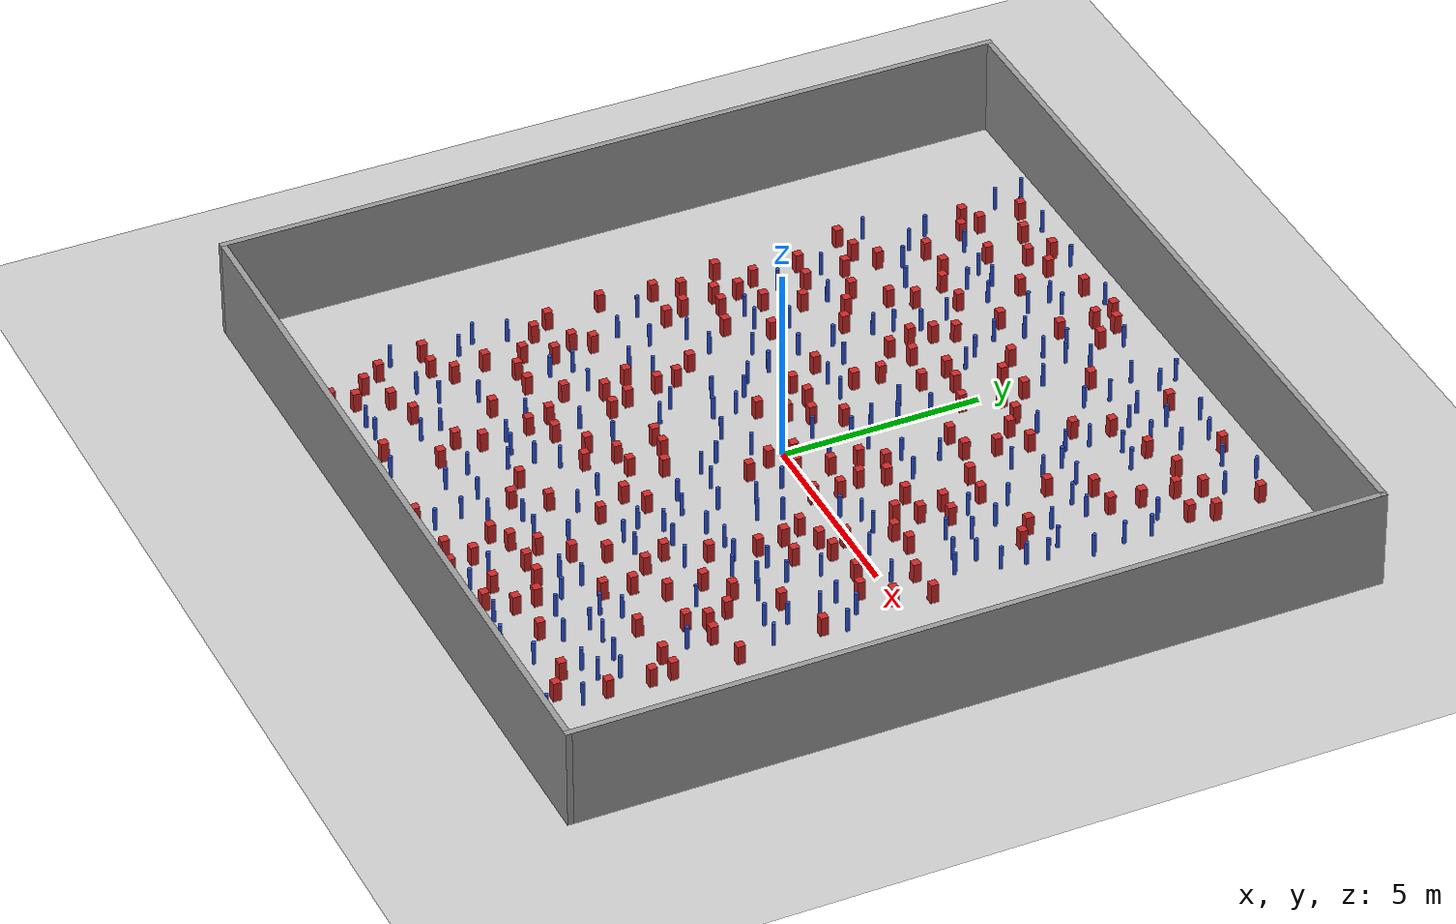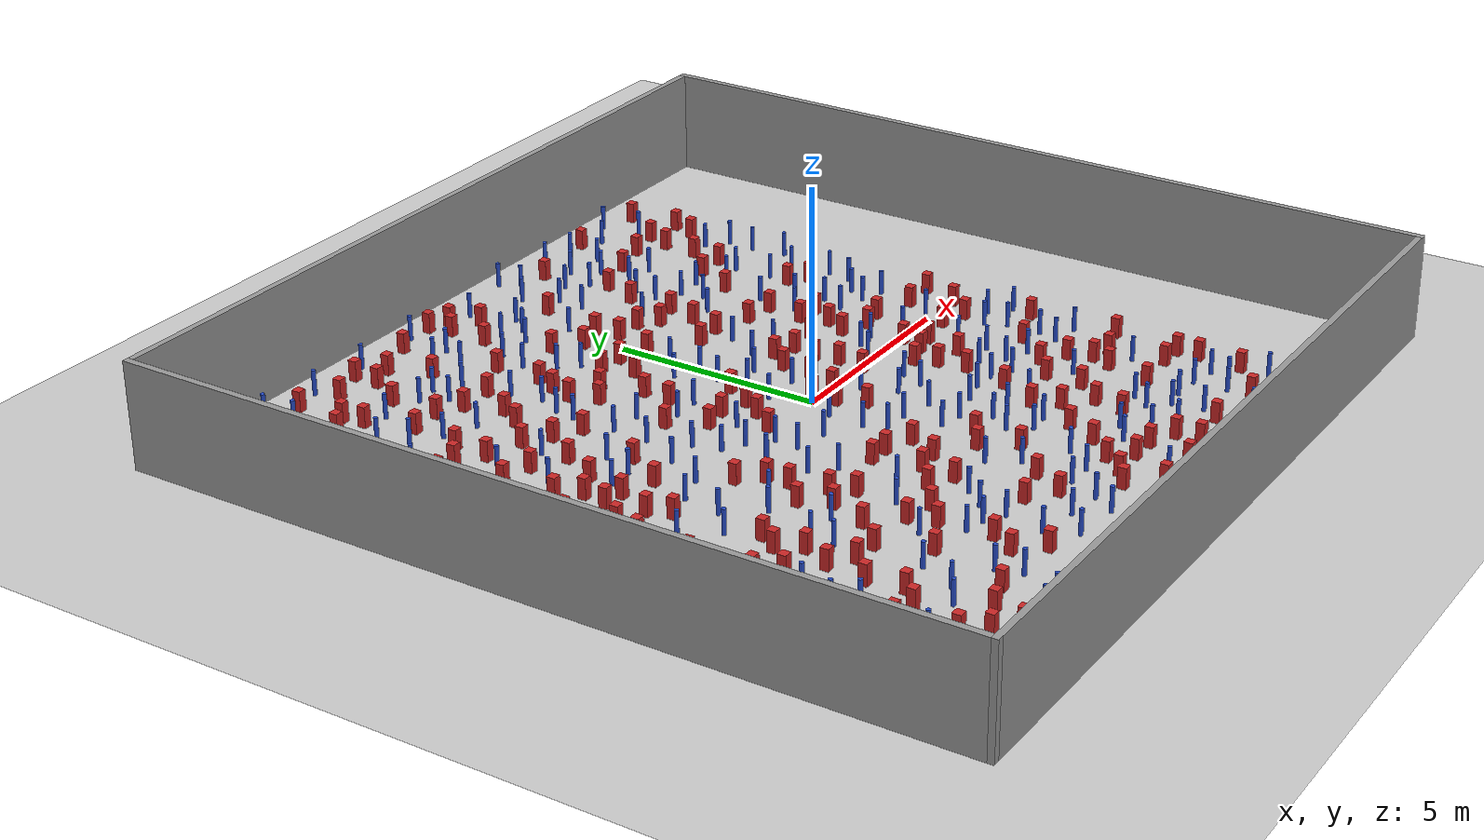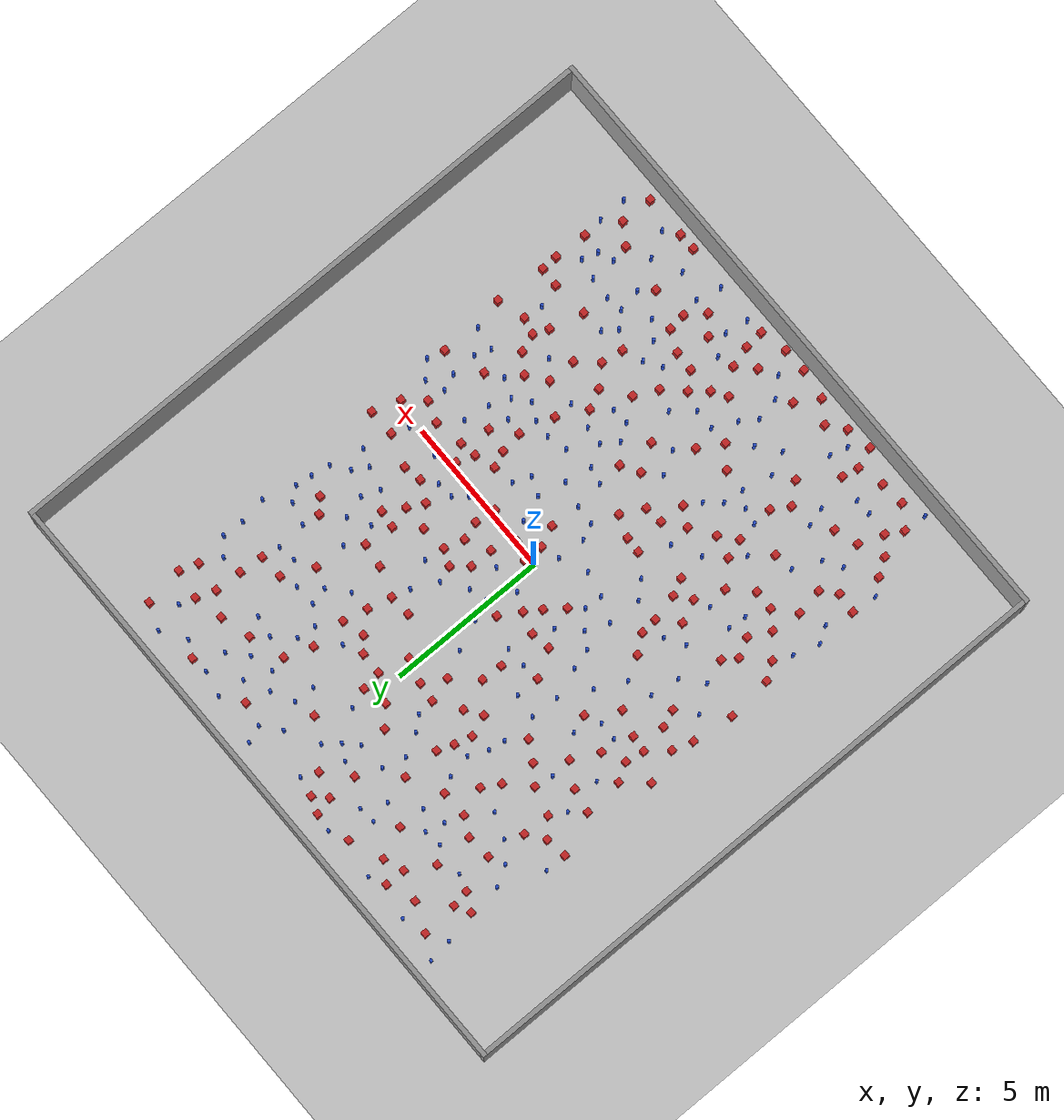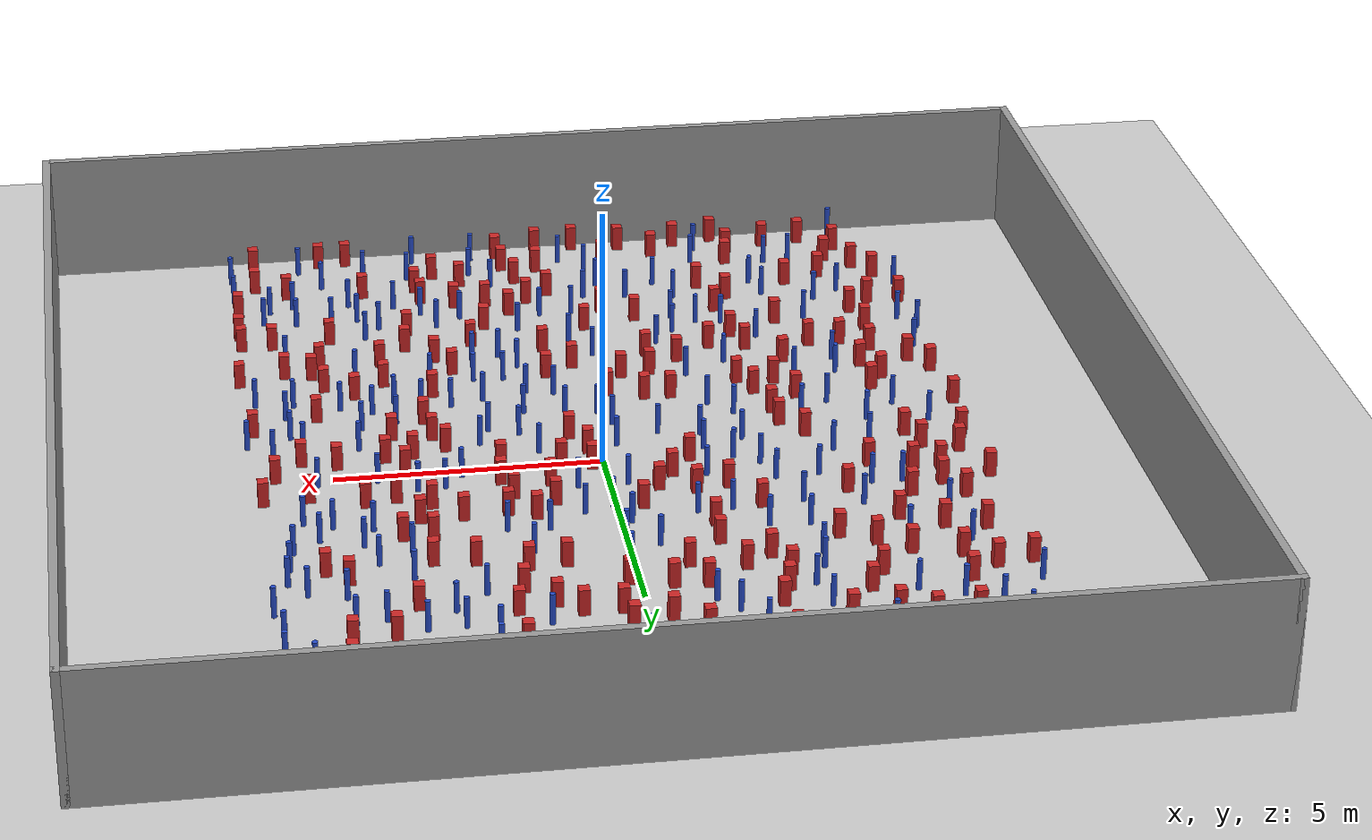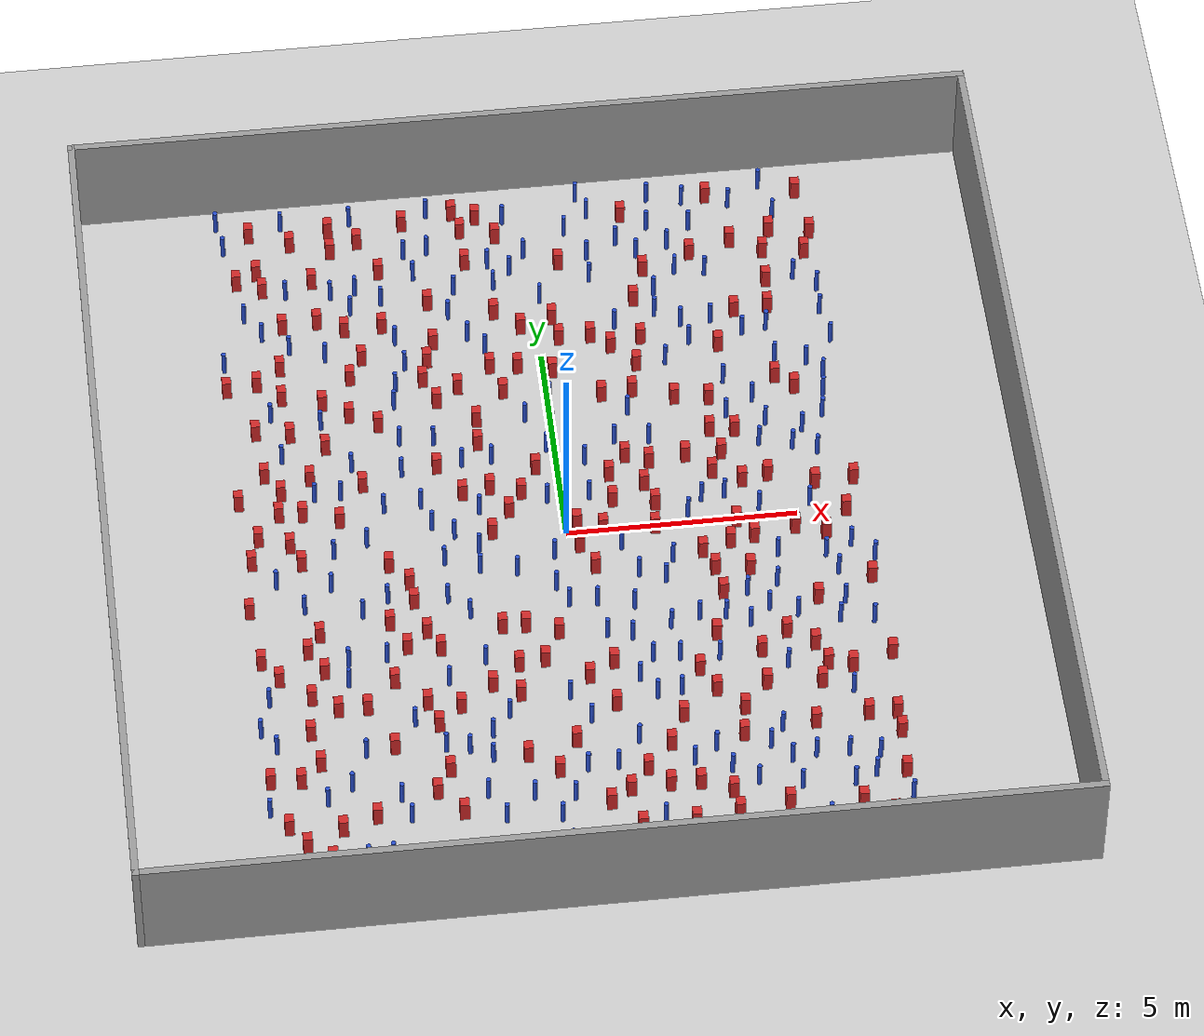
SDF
<sdf version="1.6">
 <world name="default">
  <light name="sun" type="directional">
   <pose>0 0 1000 0 -0 0</pose>
   <diffuse>0.8 0.8 0.8 1</diffuse>
   <specular>0.1 0.1 0.1 1</specular>
   <attenuation>
    <range>1000</range>
    <constant>0.9</constant>
    <linear>0.01</linear>
    <quadratic>0.001</quadratic>
   </attenuation>
   <direction>-0.5 0.5 -1</direction>
  </light>
  <model name="ground_plane">
   <static>1</static>
   <link name="link">
    <collision name="collision">
     <geometry><plane><normal>0 0 1</normal><size>100 100</size></plane></geometry>
     <surface><friction><ode><mu>100</mu><mu2>50</mu2></ode></friction></surface>
    </collision>
    <visual name="visual">
     <cast_shadows>0</cast_shadows>
     <geometry><plane><normal>0 0 1</normal><size>100 100</size></plane></geometry>
     <material>
      <ambient>1.0 1.0 1.0 1.0</ambient>
      <diffuse>0.8 0.8 0.8 1.0</diffuse>
      <specular>0.01 0.01 0.01 1.000000</specular>
     </material>
    </visual>
   </link>
  </model>
  <gravity>0 0 -9.8</gravity>
  <magnetic_field>6e-06 2.3e-05 -4.2e-05</magnetic_field>
  <atmosphere type="adiabatic"/>
  <physics name="default_physics" default="0" type="ode">
   <max_step_size>0.001</max_step_size>
   <real_time_factor>1</real_time_factor>
   <real_time_update_rate>1000</real_time_update_rate>
  </physics>
  <scene><ambient>0.4 0.4 0.4 1</ambient><background>0.7 0.7 0.7 1</background><shadows>1</shadows></scene>
  <spherical_coordinates>
   <surface_model>EARTH_WGS84</surface_model>
   <latitude_deg>0</latitude_deg>
   <longitude_deg>0</longitude_deg>
   <elevation>0</elevation>
   <heading_deg>0</heading_deg>
  </spherical_coordinates>
  <plugin name="gazebo_occupancy_map" filename="libgazebo_2Dmap_plugin.so">
   <map_resolution>0.05</map_resolution>
   <map_topic>generated_map</map_topic>
   <map_height>0.01</map_height>
   <map_size_x>50</map_size_x>
   <map_size_y>50</map_size_y>
  </plugin>
  <model name="NamedLocations">
   <static>true</static>
   <link name="DefaultStart"><pose>8.5 0 0 0 0 3.14</pose></link>
  </model>
  <model name="20x20_walls">
   <pose>0.044518 0.176112 0 0 -0 0</pose>
   <link name="Wall_1">
    <collision name="Wall_1_Collision">
     <geometry><box><size>20 0.15 2.5</size></box></geometry>
     <pose>0 0 1.25 0 -0 0</pose>
    </collision>
    <visual name="Wall_1_Visual">
     <pose>0 0 1.25 0 -0 0</pose>
     <geometry><box><size>20 0.15 2.5</size></box></geometry>
     <material>
      <script><uri>file://media/materials/scripts/gazebo.material</uri><name>Gazebo/Grey</name></script>
      <ambient>0.976471 0.992157 1 1</ambient>
     </material>
     <meta><layer>0</layer></meta>
    </visual>
    <pose>0 9.925 0 0 -0 0</pose>
   </link>
   <link name="Wall_3">
    <collision name="Wall_3_Collision">
     <geometry><box><size>20 0.15 2.5</size></box></geometry>
     <pose>0 0 1.25 0 -0 0</pose>
    </collision>
    <visual name="Wall_3_Visual">
     <pose>0 0 1.25 0 -0 0</pose>
     <geometry><box><size>20 0.15 2.5</size></box></geometry>
     <material>
      <script><uri>file://media/materials/scripts/gazebo.material</uri><name>Gazebo/Grey</name></script>
      <ambient>0.976471 0.992157 1 1</ambient>
     </material>
     <meta><layer>0</layer></meta>
    </visual>
    <pose>9.925 0 0 0 0 -1.5708</pose>
   </link>
   <link name="Wall_4">
    <collision name="Wall_4_Collision">
     <geometry><box><size>20 0.15 2.5</size></box></geometry>
     <pose>0 0 1.25 0 -0 0</pose>
    </collision>
    <visual name="Wall_4_Visual">
     <pose>0 0 1.25 0 -0 0</pose>
     <geometry><box><size>20 0.15 2.5</size></box></geometry>
     <material>
      <script><uri>file://media/materials/scripts/gazebo.material</uri><name>Gazebo/Grey</name></script>
      <ambient>0.976471 0.992157 1 1</ambient>
     </material>
     <meta><layer>0</layer></meta>
    </visual>
    <pose>0 -9.925 0 0 -0 3.14159</pose>
   </link>
   <link name="Wall_5">
    <collision name="Wall_5_Collision">
     <geometry><box><size>20 0.15 2.5</size></box></geometry>
     <pose>0 0 1.25 0 -0 0</pose>
    </collision>
    <visual name="Wall_5_Visual">
     <pose>0 0 1.25 0 -0 0</pose>
     <geometry><box><size>20 0.15 2.5</size></box></geometry>
     <material>
      <script><uri>file://media/materials/scripts/gazebo.material</uri><name>Gazebo/Grey</name></script>
      <ambient>0.976471 0.992157 1 1</ambient>
     </material>
     <meta><layer>0</layer></meta>
    </visual>
    <pose>-9.925 0 0 0 -0 1.5708</pose>
   </link>
   <static>1</static>
  </model>
  <model name="square_post_obstacle0">
   <static>true</static>
   <pose>5.91802541232 -9.29908358302 1.91545236811e-07 -7.35059704564e-06 1.12565212e-07 2.39332434364e-05</pose>
   <link name="link">
    <pose>0 0 0.25 0 -0 0</pose>
    <inertial>
     <mass>100</mass>
     <inertia>
      <ixx>0.166667</ixx>
      <ixy>0</ixy>
      <ixz>0</ixz>
      <iyy>0.166667</iyy>
      <iyz>0</iyz>
      <izz>0.166667</izz>
     </inertia>
    </inertial>
    <collision name="collision"><geometry><box><size>.2 .2 .5</size></box></geometry></collision>
    <visual name="visual">
     <geometry><box><size>.2 .2 .5</size></box></geometry>
     <material>
      <script><name>Gazebo/Red</name><uri>file://media/materials/scripts/gazebo.material</uri></script>
     </material>
    </visual>
   </link>
  </model>
  <model name="square_post_obstacle1">
   <static>true</static>
   <pose>5.17241559216 6.57983816717 1.91545236811e-07 -7.35059704564e-06 1.12565212e-07 2.39332434364e-05</pose>
   <link name="link">
    <pose>0 0 0.25 0 -0 0</pose>
    <inertial>
     <mass>100</mass>
     <inertia>
      <ixx>0.166667</ixx>
      <ixy>0</ixy>
      <ixz>0</ixz>
      <iyy>0.166667</iyy>
      <iyz>0</iyz>
      <izz>0.166667</izz>
     </inertia>
    </inertial>
    <collision name="collision"><geometry><box><size>.2 .2 .5</size></box></geometry></collision>
    <visual name="visual">
     <geometry><box><size>.2 .2 .5</size></box></geometry>
     <material>
      <script><name>Gazebo/Red</name><uri>file://media/materials/scripts/gazebo.material</uri></script>
     </material>
    </visual>
   </link>
  </model>
  <model name="pole_obstacle0">
   <static>true</static>
   <pose>-2.74047596833 8.22016565613 7.38925637345e-09 -8.47170692793e-08 1.24976764408e-08 -1.74513093041e-07</pose>
   <link name="link">
    <pose>0 0 0.3 0 -0 0</pose>
    <inertial>
     <mass>1</mass>
     <inertia><ixx>0.145833</ixx><ixy>0</ixy><ixz>0</ixz><iyy>0.145833</iyy><iyz>0</iyz><izz>0.125</izz></inertia>
    </inertial>
    <collision name="collision">
     <geometry><cylinder><radius>0.05</radius><length>.6</length></cylinder></geometry>
    </collision>
    <visual name="visual">
     <geometry><cylinder><radius>0.05</radius><length>.6</length></cylinder></geometry>
     <material>
      <script><name>Gazebo/Blue</name><uri>file://media/materials/scripts/gazebo.material</uri></script>
     </material>
    </visual>
   </link>
  </model>
  <model name="square_post_obstacle2">
   <static>true</static>
   <pose>-1.20168735869 -8.64444956129 1.91545236811e-07 -7.35059704564e-06 1.12565212e-07 2.39332434364e-05</pose>
   <link name="link">
    <pose>0 0 0.25 0 -0 0</pose>
    <inertial>
     <mass>100</mass>
     <inertia>
      <ixx>0.166667</ixx>
      <ixy>0</ixy>
      <ixz>0</ixz>
      <iyy>0.166667</iyy>
      <iyz>0</iyz>
      <izz>0.166667</izz>
     </inertia>
    </inertial>
    <collision name="collision"><geometry><box><size>.2 .2 .5</size></box></geometry></collision>
    <visual name="visual">
     <geometry><box><size>.2 .2 .5</size></box></geometry>
     <material>
      <script><name>Gazebo/Red</name><uri>file://media/materials/scripts/gazebo.material</uri></script>
     </material>
    </visual>
   </link>
  </model>
  <model name="pole_obstacle1">
   <static>true</static>
   <pose>-0.560717947316 3.22492922202 7.38925637345e-09 -8.47170692799e-08 1.2497676509e-08 -1.74513093016e-07</pose>
   <link name="link">
    <pose>0 0 0.3 0 -0 0</pose>
    <inertial>
     <mass>1</mass>
     <inertia><ixx>0.145833</ixx><ixy>0</ixy><ixz>0</ixz><iyy>0.145833</iyy><iyz>0</iyz><izz>0.125</izz></inertia>
    </inertial>
    <collision name="collision">
     <geometry><cylinder><radius>0.05</radius><length>.6</length></cylinder></geometry>
    </collision>
    <visual name="visual">
     <geometry><cylinder><radius>0.05</radius><length>.6</length></cylinder></geometry>
     <material>
      <script><name>Gazebo/Blue</name><uri>file://media/materials/scripts/gazebo.material</uri></script>
     </material>
    </visual>
   </link>
  </model>
  <model name="square_post_obstacle3">
   <static>true</static>
   <pose>3.19145135522 -5.20112439328 1.91545236811e-07 -7.35059704564e-06 1.12565212e-07 2.39332434364e-05</pose>
   <link name="link">
    <pose>0 0 0.25 0 -0 0</pose>
    <inertial>
     <mass>100</mass>
     <inertia>
      <ixx>0.166667</ixx>
      <ixy>0</ixy>
      <ixz>0</ixz>
      <iyy>0.166667</iyy>
      <iyz>0</iyz>
      <izz>0.166667</izz>
     </inertia>
    </inertial>
    <collision name="collision"><geometry><box><size>.2 .2 .5</size></box></geometry></collision>
    <visual name="visual">
     <geometry><box><size>.2 .2 .5</size></box></geometry>
     <material>
      <script><name>Gazebo/Red</name><uri>file://media/materials/scripts/gazebo.material</uri></script>
     </material>
    </visual>
   </link>
  </model>
  <model name="pole_obstacle2">
   <static>true</static>
   <pose>-5.3107187006 1.49005839693 7.38925637345e-09 -8.471706928e-08 1.24976765134e-08 -1.74513093015e-07</pose>
   <link name="link">
    <pose>0 0 0.3 0 -0 0</pose>
    <inertial>
     <mass>1</mass>
     <inertia><ixx>0.145833</ixx><ixy>0</ixy><ixz>0</ixz><iyy>0.145833</iyy><iyz>0</iyz><izz>0.125</izz></inertia>
    </inertial>
    <collision name="collision">
     <geometry><cylinder><radius>0.05</radius><length>.6</length></cylinder></geometry>
    </collision>
    <visual name="visual">
     <geometry><cylinder><radius>0.05</radius><length>.6</length></cylinder></geometry>
     <material>
      <script><name>Gazebo/Blue</name><uri>file://media/materials/scripts/gazebo.material</uri></script>
     </material>
    </visual>
   </link>
  </model>
  <model name="pole_obstacle3">
   <static>true</static>
   <pose>-4.98828440317 -3.05685536045 7.38925637345e-09 -8.47170692798e-08 1.24976764937e-08 -1.74513093023e-07</pose>
   <link name="link">
    <pose>0 0 0.3 0 -0 0</pose>
    <inertial>
     <mass>1</mass>
     <inertia><ixx>0.145833</ixx><ixy>0</ixy><ixz>0</ixz><iyy>0.145833</iyy><iyz>0</iyz><izz>0.125</izz></inertia>
    </inertial>
    <collision name="collision">
     <geometry><cylinder><radius>0.05</radius><length>.6</length></cylinder></geometry>
    </collision>
    <visual name="visual">
     <geometry><cylinder><radius>0.05</radius><length>.6</length></cylinder></geometry>
     <material>
      <script><name>Gazebo/Blue</name><uri>file://media/materials/scripts/gazebo.material</uri></script>
     </material>
    </visual>
   </link>
  </model>
  <model name="square_post_obstacle4">
   <static>true</static>
   <pose>0.591381948 -3.68222701026 1.91545236811e-07 -7.35059704564e-06 1.12565212e-07 2.39332434364e-05</pose>
   <link name="link">
    <pose>0 0 0.25 0 -0 0</pose>
    <inertial>
     <mass>100</mass>
     <inertia>
      <ixx>0.166667</ixx>
      <ixy>0</ixy>
      <ixz>0</ixz>
      <iyy>0.166667</iyy>
      <iyz>0</iyz>
      <izz>0.166667</izz>
     </inertia>
    </inertial>
    <collision name="collision"><geometry><box><size>.2 .2 .5</size></box></geometry></collision>
    <visual name="visual">
     <geometry><box><size>.2 .2 .5</size></box></geometry>
     <material>
      <script><name>Gazebo/Red</name><uri>file://media/materials/scripts/gazebo.material</uri></script>
     </material>
    </visual>
   </link>
  </model>
  <model name="square_post_obstacle5">
   <static>true</static>
   <pose>6.12620740187 7.31819296594 1.91545236811e-07 -7.35059704564e-06 1.12565212e-07 2.39332434364e-05</pose>
   <link name="link">
    <pose>0 0 0.25 0 -0 0</pose>
    <inertial>
     <mass>100</mass>
     <inertia>
      <ixx>0.166667</ixx>
      <ixy>0</ixy>
      <ixz>0</ixz>
      <iyy>0.166667</iyy>
      <iyz>0</iyz>
      <izz>0.166667</izz>
     </inertia>
    </inertial>
    <collision name="collision"><geometry><box><size>.2 .2 .5</size></box></geometry></collision>
    <visual name="visual">
     <geometry><box><size>.2 .2 .5</size></box></geometry>
     <material>
      <script><name>Gazebo/Red</name><uri>file://media/materials/scripts/gazebo.material</uri></script>
     </material>
    </visual>
   </link>
  </model>
  <model name="square_post_obstacle6">
   <static>true</static>
   <pose>2.74779495735 3.42681355464 1.91545236811e-07 -7.35059704564e-06 1.12565212e-07 2.39332434364e-05</pose>
   <link name="link">
    <pose>0 0 0.25 0 -0 0</pose>
    <inertial>
     <mass>100</mass>
     <inertia>
      <ixx>0.166667</ixx>
      <ixy>0</ixy>
      <ixz>0</ixz>
      <iyy>0.166667</iyy>
      <iyz>0</iyz>
      <izz>0.166667</izz>
     </inertia>
    </inertial>
    <collision name="collision"><geometry><box><size>.2 .2 .5</size></box></geometry></collision>
    <visual name="visual">
     <geometry><box><size>.2 .2 .5</size></box></geometry>
     <material>
      <script><name>Gazebo/Red</name><uri>file://media/materials/scripts/gazebo.material</uri></script>
     </material>
    </visual>
   </link>
  </model>
  <model name="pole_obstacle4">
   <static>true</static>
   <pose>-4.57300198142 -1.81196447435 7.38925637345e-09 -8.471706928e-08 1.24976765134e-08 -1.74513093015e-07</pose>
   <link name="link">
    <pose>0 0 0.3 0 -0 0</pose>
    <inertial>
     <mass>1</mass>
     <inertia><ixx>0.145833</ixx><ixy>0</ixy><ixz>0</ixz><iyy>0.145833</iyy><iyz>0</iyz><izz>0.125</izz></inertia>
    </inertial>
    <collision name="collision">
     <geometry><cylinder><radius>0.05</radius><length>.6</length></cylinder></geometry>
    </collision>
    <visual name="visual">
     <geometry><cylinder><radius>0.05</radius><length>.6</length></cylinder></geometry>
     <material>
      <script><name>Gazebo/Blue</name><uri>file://media/materials/scripts/gazebo.material</uri></script>
     </material>
    </visual>
   </link>
  </model>
  <model name="pole_obstacle5">
   <static>true</static>
   <pose>2.83213413651 9.30783360719 7.38925637345e-09 -8.47170692793e-08 1.24976764408e-08 -1.74513093041e-07</pose>
   <link name="link">
    <pose>0 0 0.3 0 -0 0</pose>
    <inertial>
     <mass>1</mass>
     <inertia><ixx>0.145833</ixx><ixy>0</ixy><ixz>0</ixz><iyy>0.145833</iyy><iyz>0</iyz><izz>0.125</izz></inertia>
    </inertial>
    <collision name="collision">
     <geometry><cylinder><radius>0.05</radius><length>.6</length></cylinder></geometry>
    </collision>
    <visual name="visual">
     <geometry><cylinder><radius>0.05</radius><length>.6</length></cylinder></geometry>
     <material>
      <script><name>Gazebo/Blue</name><uri>file://media/materials/scripts/gazebo.material</uri></script>
     </material>
    </visual>
   </link>
  </model>
  <model name="square_post_obstacle7">
   <static>true</static>
   <pose>1.96890873145 0.516541553531 1.91545236811e-07 -7.35059704564e-06 1.12565212e-07 2.39332434364e-05</pose>
   <link name="link">
    <pose>0 0 0.25 0 -0 0</pose>
    <inertial>
     <mass>100</mass>
     <inertia>
      <ixx>0.166667</ixx>
      <ixy>0</ixy>
      <ixz>0</ixz>
      <iyy>0.166667</iyy>
      <iyz>0</iyz>
      <izz>0.166667</izz>
     </inertia>
    </inertial>
    <collision name="collision"><geometry><box><size>.2 .2 .5</size></box></geometry></collision>
    <visual name="visual">
     <geometry><box><size>.2 .2 .5</size></box></geometry>
     <material>
      <script><name>Gazebo/Red</name><uri>file://media/materials/scripts/gazebo.material</uri></script>
     </material>
    </visual>
   </link>
  </model>
  <model name="square_post_obstacle8">
   <static>true</static>
   <pose>-6.50042134347 7.75709684066 1.91545236811e-07 -7.35059704564e-06 1.12565212e-07 2.39332434364e-05</pose>
   <link name="link">
    <pose>0 0 0.25 0 -0 0</pose>
    <inertial>
     <mass>100</mass>
     <inertia>
      <ixx>0.166667</ixx>
      <ixy>0</ixy>
      <ixz>0</ixz>
      <iyy>0.166667</iyy>
      <iyz>0</iyz>
      <izz>0.166667</izz>
     </inertia>
    </inertial>
    <collision name="collision"><geometry><box><size>.2 .2 .5</size></box></geometry></collision>
    <visual name="visual">
     <geometry><box><size>.2 .2 .5</size></box></geometry>
     <material>
      <script><name>Gazebo/Red</name><uri>file://media/materials/scripts/gazebo.material</uri></script>
     </material>
    </visual>
   </link>
  </model>
  <model name="pole_obstacle6">
   <static>true</static>
   <pose>-5.92039442164 2.6374540266 7.38925637345e-09 -8.47170692798e-08 1.24976764937e-08 -1.74513093023e-07</pose>
   <link name="link">
    <pose>0 0 0.3 0 -0 0</pose>
    <inertial>
     <mass>1</mass>
     <inertia><ixx>0.145833</ixx><ixy>0</ixy><ixz>0</ixz><iyy>0.145833</iyy><iyz>0</iyz><izz>0.125</izz></inertia>
    </inertial>
    <collision name="collision">
     <geometry><cylinder><radius>0.05</radius><length>.6</length></cylinder></geometry>
    </collision>
    <visual name="visual">
     <geometry><cylinder><radius>0.05</radius><length>.6</length></cylinder></geometry>
     <material>
      <script><name>Gazebo/Blue</name><uri>file://media/materials/scripts/gazebo.material</uri></script>
     </material>
    </visual>
   </link>
  </model>
  <model name="pole_obstacle7">
   <static>true</static>
   <pose>4.42884117087 1.99683691813 7.38925637345e-09 -8.471706928e-08 1.24976765177e-08 -1.74513093012e-07</pose>
   <link name="link">
    <pose>0 0 0.3 0 -0 0</pose>
    <inertial>
     <mass>1</mass>
     <inertia><ixx>0.145833</ixx><ixy>0</ixy><ixz>0</ixz><iyy>0.145833</iyy><iyz>0</iyz><izz>0.125</izz></inertia>
    </inertial>
    <collision name="collision">
     <geometry><cylinder><radius>0.05</radius><length>.6</length></cylinder></geometry>
    </collision>
    <visual name="visual">
     <geometry><cylinder><radius>0.05</radius><length>.6</length></cylinder></geometry>
     <material>
      <script><name>Gazebo/Blue</name><uri>file://media/materials/scripts/gazebo.material</uri></script>
     </material>
    </visual>
   </link>
  </model>
  <model name="square_post_obstacle9">
   <static>true</static>
   <pose>0.974941100024 -6.5548905209 1.91545236811e-07 -7.35059704564e-06 1.12565212e-07 2.39332434364e-05</pose>
   <link name="link">
    <pose>0 0 0.25 0 -0 0</pose>
    <inertial>
     <mass>100</mass>
     <inertia>
      <ixx>0.166667</ixx>
      <ixy>0</ixy>
      <ixz>0</ixz>
      <iyy>0.166667</iyy>
      <iyz>0</iyz>
      <izz>0.166667</izz>
     </inertia>
    </inertial>
    <collision name="collision"><geometry><box><size>.2 .2 .5</size></box></geometry></collision>
    <visual name="visual">
     <geometry><box><size>.2 .2 .5</size></box></geometry>
     <material>
      <script><name>Gazebo/Red</name><uri>file://media/materials/scripts/gazebo.material</uri></script>
     </material>
    </visual>
   </link>
  </model>
  <model name="square_post_obstacle10">
   <static>true</static>
   <pose>-5.74730264443 -0.327476296227 1.91545236811e-07 -7.35059704564e-06 1.12565212e-07 2.39332434364e-05</pose>
   <link name="link">
    <pose>0 0 0.25 0 -0 0</pose>
    <inertial>
     <mass>100</mass>
     <inertia>
      <ixx>0.166667</ixx>
      <ixy>0</ixy>
      <ixz>0</ixz>
      <iyy>0.166667</iyy>
      <iyz>0</iyz>
      <izz>0.166667</izz>
     </inertia>
    </inertial>
    <collision name="collision"><geometry><box><size>.2 .2 .5</size></box></geometry></collision>
    <visual name="visual">
     <geometry><box><size>.2 .2 .5</size></box></geometry>
     <material>
      <script><name>Gazebo/Red</name><uri>file://media/materials/scripts/gazebo.material</uri></script>
     </material>
    </visual>
   </link>
  </model>
  <model name="square_post_obstacle11">
   <static>true</static>
   <pose>-2.60580880805 2.04460660842 1.91545236811e-07 -7.35059704564e-06 1.12565212e-07 2.39332434364e-05</pose>
   <link name="link">
    <pose>0 0 0.25 0 -0 0</pose>
    <inertial>
     <mass>100</mass>
     <inertia>
      <ixx>0.166667</ixx>
      <ixy>0</ixy>
      <ixz>0</ixz>
      <iyy>0.166667</iyy>
      <iyz>0</iyz>
      <izz>0.166667</izz>
     </inertia>
    </inertial>
    <collision name="collision"><geometry><box><size>.2 .2 .5</size></box></geometry></collision>
    <visual name="visual">
     <geometry><box><size>.2 .2 .5</size></box></geometry>
     <material>
      <script><name>Gazebo/Red</name><uri>file://media/materials/scripts/gazebo.material</uri></script>
     </material>
    </visual>
   </link>
  </model>
  <model name="square_post_obstacle12">
   <static>true</static>
   <pose>-0.953486799942 3.99989411962 1.91545236811e-07 -7.35059704564e-06 1.12565212e-07 2.39332434364e-05</pose>
   <link name="link">
    <pose>0 0 0.25 0 -0 0</pose>
    <inertial>
     <mass>100</mass>
     <inertia>
      <ixx>0.166667</ixx>
      <ixy>0</ixy>
      <ixz>0</ixz>
      <iyy>0.166667</iyy>
      <iyz>0</iyz>
      <izz>0.166667</izz>
     </inertia>
    </inertial>
    <collision name="collision"><geometry><box><size>.2 .2 .5</size></box></geometry></collision>
    <visual name="visual">
     <geometry><box><size>.2 .2 .5</size></box></geometry>
     <material>
      <script><name>Gazebo/Red</name><uri>file://media/materials/scripts/gazebo.material</uri></script>
     </material>
    </visual>
   </link>
  </model>
  <model name="square_post_obstacle13">
   <static>true</static>
   <pose>-0.686878680234 -9.48801535259 1.91545236811e-07 -7.35059704564e-06 1.12565212e-07 2.39332434364e-05</pose>
   <link name="link">
    <pose>0 0 0.25 0 -0 0</pose>
    <inertial>
     <mass>100</mass>
     <inertia>
      <ixx>0.166667</ixx>
      <ixy>0</ixy>
      <ixz>0</ixz>
      <iyy>0.166667</iyy>
      <iyz>0</iyz>
      <izz>0.166667</izz>
     </inertia>
    </inertial>
    <collision name="collision"><geometry><box><size>.2 .2 .5</size></box></geometry></collision>
    <visual name="visual">
     <geometry><box><size>.2 .2 .5</size></box></geometry>
     <material>
      <script><name>Gazebo/Red</name><uri>file://media/materials/scripts/gazebo.material</uri></script>
     </material>
    </visual>
   </link>
  </model>
  <model name="pole_obstacle8">
   <static>true</static>
   <pose>-4.21248484026 -6.73208509425 7.38925637345e-09 -8.47170692796e-08 1.24976764786e-08 -1.74513093032e-07</pose>
   <link name="link">
    <pose>0 0 0.3 0 -0 0</pose>
    <inertial>
     <mass>1</mass>
     <inertia><ixx>0.145833</ixx><ixy>0</ixy><ixz>0</ixz><iyy>0.145833</iyy><iyz>0</iyz><izz>0.125</izz></inertia>
    </inertial>
    <collision name="collision">
     <geometry><cylinder><radius>0.05</radius><length>.6</length></cylinder></geometry>
    </collision>
    <visual name="visual">
     <geometry><cylinder><radius>0.05</radius><length>.6</length></cylinder></geometry>
     <material>
      <script><name>Gazebo/Blue</name><uri>file://media/materials/scripts/gazebo.material</uri></script>
     </material>
    </visual>
   </link>
  </model>
  <model name="square_post_obstacle14">
   <static>true</static>
   <pose>3.88749947179 4.82470724292 1.91545236811e-07 -7.35059704564e-06 1.12565212e-07 2.39332434364e-05</pose>
   <link name="link">
    <pose>0 0 0.25 0 -0 0</pose>
    <inertial>
     <mass>100</mass>
     <inertia>
      <ixx>0.166667</ixx>
      <ixy>0</ixy>
      <ixz>0</ixz>
      <iyy>0.166667</iyy>
      <iyz>0</iyz>
      <izz>0.166667</izz>
     </inertia>
    </inertial>
    <collision name="collision"><geometry><box><size>.2 .2 .5</size></box></geometry></collision>
    <visual name="visual">
     <geometry><box><size>.2 .2 .5</size></box></geometry>
     <material>
      <script><name>Gazebo/Red</name><uri>file://media/materials/scripts/gazebo.material</uri></script>
     </material>
    </visual>
   </link>
  </model>
  <model name="square_post_obstacle15">
   <static>true</static>
   <pose>-2.27690724691 -8.92274579487 1.91545236811e-07 -7.35059704564e-06 1.12565212e-07 2.39332434364e-05</pose>
   <link name="link">
    <pose>0 0 0.25 0 -0 0</pose>
    <inertial>
     <mass>100</mass>
     <inertia>
      <ixx>0.166667</ixx>
      <ixy>0</ixy>
      <ixz>0</ixz>
      <iyy>0.166667</iyy>
      <iyz>0</iyz>
      <izz>0.166667</izz>
     </inertia>
    </inertial>
    <collision name="collision"><geometry><box><size>.2 .2 .5</size></box></geometry></collision>
    <visual name="visual">
     <geometry><box><size>.2 .2 .5</size></box></geometry>
     <material>
      <script><name>Gazebo/Red</name><uri>file://media/materials/scripts/gazebo.material</uri></script>
     </material>
    </visual>
   </link>
  </model>
  <model name="square_post_obstacle16">
   <static>true</static>
   <pose>-3.45719369046 -6.68199653338 1.91545236811e-07 -7.35059704564e-06 1.12565212e-07 2.39332434364e-05</pose>
   <link name="link">
    <pose>0 0 0.25 0 -0 0</pose>
    <inertial>
     <mass>100</mass>
     <inertia>
      <ixx>0.166667</ixx>
      <ixy>0</ixy>
      <ixz>0</ixz>
      <iyy>0.166667</iyy>
      <iyz>0</iyz>
      <izz>0.166667</izz>
     </inertia>
    </inertial>
    <collision name="collision"><geometry><box><size>.2 .2 .5</size></box></geometry></collision>
    <visual name="visual">
     <geometry><box><size>.2 .2 .5</size></box></geometry>
     <material>
      <script><name>Gazebo/Red</name><uri>file://media/materials/scripts/gazebo.material</uri></script>
     </material>
    </visual>
   </link>
  </model>
  <model name="pole_obstacle9">
   <static>true</static>
   <pose>1.30406484558 2.3932725286 7.38925637345e-09 -8.47170692799e-08 1.24976765053e-08 -1.74513093017e-07</pose>
   <link name="link">
    <pose>0 0 0.3 0 -0 0</pose>
    <inertial>
     <mass>1</mass>
     <inertia><ixx>0.145833</ixx><ixy>0</ixy><ixz>0</ixz><iyy>0.145833</iyy><iyz>0</iyz><izz>0.125</izz></inertia>
    </inertial>
    <collision name="collision">
     <geometry><cylinder><radius>0.05</radius><length>.6</length></cylinder></geometry>
    </collision>
    <visual name="visual">
     <geometry><cylinder><radius>0.05</radius><length>.6</length></cylinder></geometry>
     <material>
      <script><name>Gazebo/Blue</name><uri>file://media/materials/scripts/gazebo.material</uri></script>
     </material>
    </visual>
   </link>
  </model>
  <model name="square_post_obstacle17">
   <static>true</static>
   <pose>-3.75734223442 3.34890527654 1.91545236811e-07 -7.35059704564e-06 1.12565212e-07 2.39332434364e-05</pose>
   <link name="link">
    <pose>0 0 0.25 0 -0 0</pose>
    <inertial>
     <mass>100</mass>
     <inertia>
      <ixx>0.166667</ixx>
      <ixy>0</ixy>
      <ixz>0</ixz>
      <iyy>0.166667</iyy>
      <iyz>0</iyz>
      <izz>0.166667</izz>
     </inertia>
    </inertial>
    <collision name="collision"><geometry><box><size>.2 .2 .5</size></box></geometry></collision>
    <visual name="visual">
     <geometry><box><size>.2 .2 .5</size></box></geometry>
     <material>
      <script><name>Gazebo/Red</name><uri>file://media/materials/scripts/gazebo.material</uri></script>
     </material>
    </visual>
   </link>
  </model>
  <model name="square_post_obstacle18">
   <static>true</static>
   <pose>4.48623797648 1.04986090024 1.91545236811e-07 -7.35059704564e-06 1.12565212e-07 2.39332434364e-05</pose>
   <link name="link">
    <pose>0 0 0.25 0 -0 0</pose>
    <inertial>
     <mass>100</mass>
     <inertia>
      <ixx>0.166667</ixx>
      <ixy>0</ixy>
      <ixz>0</ixz>
      <iyy>0.166667</iyy>
      <iyz>0</iyz>
      <izz>0.166667</izz>
     </inertia>
    </inertial>
    <collision name="collision"><geometry><box><size>.2 .2 .5</size></box></geometry></collision>
    <visual name="visual">
     <geometry><box><size>.2 .2 .5</size></box></geometry>
     <material>
      <script><name>Gazebo/Red</name><uri>file://media/materials/scripts/gazebo.material</uri></script>
     </material>
    </visual>
   </link>
  </model>
  <model name="pole_obstacle10">
   <static>true</static>
   <pose>2.98692102486 0.5763629176 7.38925637345e-09 -8.471706928e-08 1.24976765177e-08 -1.74513093012e-07</pose>
   <link name="link">
    <pose>0 0 0.3 0 -0 0</pose>
    <inertial>
     <mass>1</mass>
     <inertia><ixx>0.145833</ixx><ixy>0</ixy><ixz>0</ixz><iyy>0.145833</iyy><iyz>0</iyz><izz>0.125</izz></inertia>
    </inertial>
    <collision name="collision">
     <geometry><cylinder><radius>0.05</radius><length>.6</length></cylinder></geometry>
    </collision>
    <visual name="visual">
     <geometry><cylinder><radius>0.05</radius><length>.6</length></cylinder></geometry>
     <material>
      <script><name>Gazebo/Blue</name><uri>file://media/materials/scripts/gazebo.material</uri></script>
     </material>
    </visual>
   </link>
  </model>
  <model name="square_post_obstacle19">
   <static>true</static>
   <pose>-1.17114769434 4.74576161731 1.91545236811e-07 -7.35059704564e-06 1.12565212e-07 2.39332434364e-05</pose>
   <link name="link">
    <pose>0 0 0.25 0 -0 0</pose>
    <inertial>
     <mass>100</mass>
     <inertia>
      <ixx>0.166667</ixx>
      <ixy>0</ixy>
      <ixz>0</ixz>
      <iyy>0.166667</iyy>
      <iyz>0</iyz>
      <izz>0.166667</izz>
     </inertia>
    </inertial>
    <collision name="collision"><geometry><box><size>.2 .2 .5</size></box></geometry></collision>
    <visual name="visual">
     <geometry><box><size>.2 .2 .5</size></box></geometry>
     <material>
      <script><name>Gazebo/Red</name><uri>file://media/materials/scripts/gazebo.material</uri></script>
     </material>
    </visual>
   </link>
  </model>
  <model name="pole_obstacle11">
   <static>true</static>
   <pose>-0.171977113743 -1.9775579437 7.38925637345e-09 -8.471706928e-08 1.24976765063e-08 -1.74513093017e-07</pose>
   <link name="link">
    <pose>0 0 0.3 0 -0 0</pose>
    <inertial>
     <mass>1</mass>
     <inertia><ixx>0.145833</ixx><ixy>0</ixy><ixz>0</ixz><iyy>0.145833</iyy><iyz>0</iyz><izz>0.125</izz></inertia>
    </inertial>
    <collision name="collision">
     <geometry><cylinder><radius>0.05</radius><length>.6</length></cylinder></geometry>
    </collision>
    <visual name="visual">
     <geometry><cylinder><radius>0.05</radius><length>.6</length></cylinder></geometry>
     <material>
      <script><name>Gazebo/Blue</name><uri>file://media/materials/scripts/gazebo.material</uri></script>
     </material>
    </visual>
   </link>
  </model>
  <model name="square_post_obstacle20">
   <static>true</static>
   <pose>-2.42705209212 3.88906436774 1.91545236811e-07 -7.35059704564e-06 1.12565212e-07 2.39332434364e-05</pose>
   <link name="link">
    <pose>0 0 0.25 0 -0 0</pose>
    <inertial>
     <mass>100</mass>
     <inertia>
      <ixx>0.166667</ixx>
      <ixy>0</ixy>
      <ixz>0</ixz>
      <iyy>0.166667</iyy>
      <iyz>0</iyz>
      <izz>0.166667</izz>
     </inertia>
    </inertial>
    <collision name="collision"><geometry><box><size>.2 .2 .5</size></box></geometry></collision>
    <visual name="visual">
     <geometry><box><size>.2 .2 .5</size></box></geometry>
     <material>
      <script><name>Gazebo/Red</name><uri>file://media/materials/scripts/gazebo.material</uri></script>
     </material>
    </visual>
   </link>
  </model>
  <model name="pole_obstacle12">
   <static>true</static>
   <pose>-4.7468510527 1.48127857913 7.38925637345e-09 -8.471706928e-08 1.24976765134e-08 -1.74513093015e-07</pose>
   <link name="link">
    <pose>0 0 0.3 0 -0 0</pose>
    <inertial>
     <mass>1</mass>
     <inertia><ixx>0.145833</ixx><ixy>0</ixy><ixz>0</ixz><iyy>0.145833</iyy><iyz>0</iyz><izz>0.125</izz></inertia>
    </inertial>
    <collision name="collision">
     <geometry><cylinder><radius>0.05</radius><length>.6</length></cylinder></geometry>
    </collision>
    <visual name="visual">
     <geometry><cylinder><radius>0.05</radius><length>.6</length></cylinder></geometry>
     <material>
      <script><name>Gazebo/Blue</name><uri>file://media/materials/scripts/gazebo.material</uri></script>
     </material>
    </visual>
   </link>
  </model>
  <model name="square_post_obstacle21">
   <static>true</static>
   <pose>6.04395570483 -0.102435734392 1.91545236811e-07 -7.35059704564e-06 1.12565212e-07 2.39332434364e-05</pose>
   <link name="link">
    <pose>0 0 0.25 0 -0 0</pose>
    <inertial>
     <mass>100</mass>
     <inertia>
      <ixx>0.166667</ixx>
      <ixy>0</ixy>
      <ixz>0</ixz>
      <iyy>0.166667</iyy>
      <iyz>0</iyz>
      <izz>0.166667</izz>
     </inertia>
    </inertial>
    <collision name="collision"><geometry><box><size>.2 .2 .5</size></box></geometry></collision>
    <visual name="visual">
     <geometry><box><size>.2 .2 .5</size></box></geometry>
     <material>
      <script><name>Gazebo/Red</name><uri>file://media/materials/scripts/gazebo.material</uri></script>
     </material>
    </visual>
   </link>
  </model>
  <model name="pole_obstacle13">
   <static>true</static>
   <pose>3.72014007891 -8.66063864401 7.38925637345e-09 -8.47170692793e-08 1.24976764408e-08 -1.74513093041e-07</pose>
   <link name="link">
    <pose>0 0 0.3 0 -0 0</pose>
    <inertial>
     <mass>1</mass>
     <inertia><ixx>0.145833</ixx><ixy>0</ixy><ixz>0</ixz><iyy>0.145833</iyy><iyz>0</iyz><izz>0.125</izz></inertia>
    </inertial>
    <collision name="collision">
     <geometry><cylinder><radius>0.05</radius><length>.6</length></cylinder></geometry>
    </collision>
    <visual name="visual">
     <geometry><cylinder><radius>0.05</radius><length>.6</length></cylinder></geometry>
     <material>
      <script><name>Gazebo/Blue</name><uri>file://media/materials/scripts/gazebo.material</uri></script>
     </material>
    </visual>
   </link>
  </model>
  <model name="square_post_obstacle22">
   <static>true</static>
   <pose>-6.81083238746 -0.198538770943 1.91545236811e-07 -7.35059704564e-06 1.12565212e-07 2.39332434364e-05</pose>
   <link name="link">
    <pose>0 0 0.25 0 -0 0</pose>
    <inertial>
     <mass>100</mass>
     <inertia>
      <ixx>0.166667</ixx>
      <ixy>0</ixy>
      <ixz>0</ixz>
      <iyy>0.166667</iyy>
      <iyz>0</iyz>
      <izz>0.166667</izz>
     </inertia>
    </inertial>
    <collision name="collision"><geometry><box><size>.2 .2 .5</size></box></geometry></collision>
    <visual name="visual">
     <geometry><box><size>.2 .2 .5</size></box></geometry>
     <material>
      <script><name>Gazebo/Red</name><uri>file://media/materials/scripts/gazebo.material</uri></script>
     </material>
    </visual>
   </link>
  </model>
  <model name="pole_obstacle14">
   <static>true</static>
   <pose>3.11258376095 -2.67955882009 7.38925637345e-09 -8.47170692798e-08 1.24976764939e-08 -1.74513093025e-07</pose>
   <link name="link">
    <pose>0 0 0.3 0 -0 0</pose>
    <inertial>
     <mass>1</mass>
     <inertia><ixx>0.145833</ixx><ixy>0</ixy><ixz>0</ixz><iyy>0.145833</iyy><iyz>0</iyz><izz>0.125</izz></inertia>
    </inertial>
    <collision name="collision">
     <geometry><cylinder><radius>0.05</radius><length>.6</length></cylinder></geometry>
    </collision>
    <visual name="visual">
     <geometry><cylinder><radius>0.05</radius><length>.6</length></cylinder></geometry>
     <material>
      <script><name>Gazebo/Blue</name><uri>file://media/materials/scripts/gazebo.material</uri></script>
     </material>
    </visual>
   </link>
  </model>
  <model name="pole_obstacle15">
   <static>true</static>
   <pose>-3.9103735772 7.27797868932 7.38925637345e-09 -8.47170692798e-08 1.24976765033e-08 -1.74513093019e-07</pose>
   <link name="link">
    <pose>0 0 0.3 0 -0 0</pose>
    <inertial>
     <mass>1</mass>
     <inertia><ixx>0.145833</ixx><ixy>0</ixy><ixz>0</ixz><iyy>0.145833</iyy><iyz>0</iyz><izz>0.125</izz></inertia>
    </inertial>
    <collision name="collision">
     <geometry><cylinder><radius>0.05</radius><length>.6</length></cylinder></geometry>
    </collision>
    <visual name="visual">
     <geometry><cylinder><radius>0.05</radius><length>.6</length></cylinder></geometry>
     <material>
      <script><name>Gazebo/Blue</name><uri>file://media/materials/scripts/gazebo.material</uri></script>
     </material>
    </visual>
   </link>
  </model>
  <model name="pole_obstacle16">
   <static>true</static>
   <pose>-0.0484112616853 -5.11918985772 7.38925637345e-09 -8.47170692799e-08 1.24976765086e-08 -1.74513093017e-07</pose>
   <link name="link">
    <pose>0 0 0.3 0 -0 0</pose>
    <inertial>
     <mass>1</mass>
     <inertia><ixx>0.145833</ixx><ixy>0</ixy><ixz>0</ixz><iyy>0.145833</iyy><iyz>0</iyz><izz>0.125</izz></inertia>
    </inertial>
    <collision name="collision">
     <geometry><cylinder><radius>0.05</radius><length>.6</length></cylinder></geometry>
    </collision>
    <visual name="visual">
     <geometry><cylinder><radius>0.05</radius><length>.6</length></cylinder></geometry>
     <material>
      <script><name>Gazebo/Blue</name><uri>file://media/materials/scripts/gazebo.material</uri></script>
     </material>
    </visual>
   </link>
  </model>
  <model name="square_post_obstacle23">
   <static>true</static>
   <pose>-3.45728172434 -1.60527301583 1.91545236811e-07 -7.35059704564e-06 1.12565212e-07 2.39332434364e-05</pose>
   <link name="link">
    <pose>0 0 0.25 0 -0 0</pose>
    <inertial>
     <mass>100</mass>
     <inertia>
      <ixx>0.166667</ixx>
      <ixy>0</ixy>
      <ixz>0</ixz>
      <iyy>0.166667</iyy>
      <iyz>0</iyz>
      <izz>0.166667</izz>
     </inertia>
    </inertial>
    <collision name="collision"><geometry><box><size>.2 .2 .5</size></box></geometry></collision>
    <visual name="visual">
     <geometry><box><size>.2 .2 .5</size></box></geometry>
     <material>
      <script><name>Gazebo/Red</name><uri>file://media/materials/scripts/gazebo.material</uri></script>
     </material>
    </visual>
   </link>
  </model>
  <model name="pole_obstacle17">
   <static>true</static>
   <pose>-4.44216015125 2.24138379186 7.38925637345e-09 -8.47170692798e-08 1.24976764937e-08 -1.74513093023e-07</pose>
   <link name="link">
    <pose>0 0 0.3 0 -0 0</pose>
    <inertial>
     <mass>1</mass>
     <inertia><ixx>0.145833</ixx><ixy>0</ixy><ixz>0</ixz><iyy>0.145833</iyy><iyz>0</iyz><izz>0.125</izz></inertia>
    </inertial>
    <collision name="collision">
     <geometry><cylinder><radius>0.05</radius><length>.6</length></cylinder></geometry>
    </collision>
    <visual name="visual">
     <geometry><cylinder><radius>0.05</radius><length>.6</length></cylinder></geometry>
     <material>
      <script><name>Gazebo/Blue</name><uri>file://media/materials/scripts/gazebo.material</uri></script>
     </material>
    </visual>
   </link>
  </model>
  <model name="square_post_obstacle24">
   <static>true</static>
   <pose>-3.01696144579 -2.9321759393 1.91545236811e-07 -7.35059704564e-06 1.12565212e-07 2.39332434364e-05</pose>
   <link name="link">
    <pose>0 0 0.25 0 -0 0</pose>
    <inertial>
     <mass>100</mass>
     <inertia>
      <ixx>0.166667</ixx>
      <ixy>0</ixy>
      <ixz>0</ixz>
      <iyy>0.166667</iyy>
      <iyz>0</iyz>
      <izz>0.166667</izz>
     </inertia>
    </inertial>
    <collision name="collision"><geometry><box><size>.2 .2 .5</size></box></geometry></collision>
    <visual name="visual">
     <geometry><box><size>.2 .2 .5</size></box></geometry>
     <material>
      <script><name>Gazebo/Red</name><uri>file://media/materials/scripts/gazebo.material</uri></script>
     </material>
    </visual>
   </link>
  </model>
  <model name="square_post_obstacle25">
   <static>true</static>
   <pose>-4.95838039901 2.84136335254 1.91545236811e-07 -7.35059704564e-06 1.12565212e-07 2.39332434364e-05</pose>
   <link name="link">
    <pose>0 0 0.25 0 -0 0</pose>
    <inertial>
     <mass>100</mass>
     <inertia>
      <ixx>0.166667</ixx>
      <ixy>0</ixy>
      <ixz>0</ixz>
      <iyy>0.166667</iyy>
      <iyz>0</iyz>
      <izz>0.166667</izz>
     </inertia>
    </inertial>
    <collision name="collision"><geometry><box><size>.2 .2 .5</size></box></geometry></collision>
    <visual name="visual">
     <geometry><box><size>.2 .2 .5</size></box></geometry>
     <material>
      <script><name>Gazebo/Red</name><uri>file://media/materials/scripts/gazebo.material</uri></script>
     </material>
    </visual>
   </link>
  </model>
  <model name="square_post_obstacle26">
   <static>true</static>
   <pose>-2.52311962346 5.06204377096 1.91545236811e-07 -7.35059704564e-06 1.12565212e-07 2.39332434364e-05</pose>
   <link name="link">
    <pose>0 0 0.25 0 -0 0</pose>
    <inertial>
     <mass>100</mass>
     <inertia>
      <ixx>0.166667</ixx>
      <ixy>0</ixy>
      <ixz>0</ixz>
      <iyy>0.166667</iyy>
      <iyz>0</iyz>
      <izz>0.166667</izz>
     </inertia>
    </inertial>
    <collision name="collision"><geometry><box><size>.2 .2 .5</size></box></geometry></collision>
    <visual name="visual">
     <geometry><box><size>.2 .2 .5</size></box></geometry>
     <material>
      <script><name>Gazebo/Red</name><uri>file://media/materials/scripts/gazebo.material</uri></script>
     </material>
    </visual>
   </link>
  </model>
  <model name="square_post_obstacle27">
   <static>true</static>
   <pose>5.32845050327 -7.89079048025 1.91545236811e-07 -7.35059704564e-06 1.12565212e-07 2.39332434364e-05</pose>
   <link name="link">
    <pose>0 0 0.25 0 -0 0</pose>
    <inertial>
     <mass>100</mass>
     <inertia>
      <ixx>0.166667</ixx>
      <ixy>0</ixy>
      <ixz>0</ixz>
      <iyy>0.166667</iyy>
      <iyz>0</iyz>
      <izz>0.166667</izz>
     </inertia>
    </inertial>
    <collision name="collision"><geometry><box><size>.2 .2 .5</size></box></geometry></collision>
    <visual name="visual">
     <geometry><box><size>.2 .2 .5</size></box></geometry>
     <material>
      <script><name>Gazebo/Red</name><uri>file://media/materials/scripts/gazebo.material</uri></script>
     </material>
    </visual>
   </link>
  </model>
  <model name="pole_obstacle18">
   <static>true</static>
   <pose>-5.04143109885 -8.23964521974 7.38925637345e-09 -8.471706928e-08 1.24976765081e-08 -1.74513093015e-07</pose>
   <link name="link">
    <pose>0 0 0.3 0 -0 0</pose>
    <inertial>
     <mass>1</mass>
     <inertia><ixx>0.145833</ixx><ixy>0</ixy><ixz>0</ixz><iyy>0.145833</iyy><iyz>0</iyz><izz>0.125</izz></inertia>
    </inertial>
    <collision name="collision">
     <geometry><cylinder><radius>0.05</radius><length>.6</length></cylinder></geometry>
    </collision>
    <visual name="visual">
     <geometry><cylinder><radius>0.05</radius><length>.6</length></cylinder></geometry>
     <material>
      <script><name>Gazebo/Blue</name><uri>file://media/materials/scripts/gazebo.material</uri></script>
     </material>
    </visual>
   </link>
  </model>
  <model name="square_post_obstacle28">
   <static>true</static>
   <pose>-6.96407308411 -1.49995333478 1.91545236811e-07 -7.35059704564e-06 1.12565212e-07 2.39332434364e-05</pose>
   <link name="link">
    <pose>0 0 0.25 0 -0 0</pose>
    <inertial>
     <mass>100</mass>
     <inertia>
      <ixx>0.166667</ixx>
      <ixy>0</ixy>
      <ixz>0</ixz>
      <iyy>0.166667</iyy>
      <iyz>0</iyz>
      <izz>0.166667</izz>
     </inertia>
    </inertial>
    <collision name="collision"><geometry><box><size>.2 .2 .5</size></box></geometry></collision>
    <visual name="visual">
     <geometry><box><size>.2 .2 .5</size></box></geometry>
     <material>
      <script><name>Gazebo/Red</name><uri>file://media/materials/scripts/gazebo.material</uri></script>
     </material>
    </visual>
   </link>
  </model>
  <model name="pole_obstacle19">
   <static>true</static>
   <pose>5.0812405203 4.34473684918 7.38925637345e-09 -8.47170692796e-08 1.24976764786e-08 -1.74513093032e-07</pose>
   <link name="link">
    <pose>0 0 0.3 0 -0 0</pose>
    <inertial>
     <mass>1</mass>
     <inertia><ixx>0.145833</ixx><ixy>0</ixy><ixz>0</ixz><iyy>0.145833</iyy><iyz>0</iyz><izz>0.125</izz></inertia>
    </inertial>
    <collision name="collision">
     <geometry><cylinder><radius>0.05</radius><length>.6</length></cylinder></geometry>
    </collision>
    <visual name="visual">
     <geometry><cylinder><radius>0.05</radius><length>.6</length></cylinder></geometry>
     <material>
      <script><name>Gazebo/Blue</name><uri>file://media/materials/scripts/gazebo.material</uri></script>
     </material>
    </visual>
   </link>
  </model>
  <model name="square_post_obstacle29">
   <static>true</static>
   <pose>1.07501174103 1.42228093594 1.91545236811e-07 -7.35059704564e-06 1.12565212e-07 2.39332434364e-05</pose>
   <link name="link">
    <pose>0 0 0.25 0 -0 0</pose>
    <inertial>
     <mass>100</mass>
     <inertia>
      <ixx>0.166667</ixx>
      <ixy>0</ixy>
      <ixz>0</ixz>
      <iyy>0.166667</iyy>
      <iyz>0</iyz>
      <izz>0.166667</izz>
     </inertia>
    </inertial>
    <collision name="collision"><geometry><box><size>.2 .2 .5</size></box></geometry></collision>
    <visual name="visual">
     <geometry><box><size>.2 .2 .5</size></box></geometry>
     <material>
      <script><name>Gazebo/Red</name><uri>file://media/materials/scripts/gazebo.material</uri></script>
     </material>
    </visual>
   </link>
  </model>
  <model name="square_post_obstacle30">
   <static>true</static>
   <pose>5.47710392444 0.726197041636 1.91545236811e-07 -7.35059704564e-06 1.12565212e-07 2.39332434364e-05</pose>
   <link name="link">
    <pose>0 0 0.25 0 -0 0</pose>
    <inertial>
     <mass>100</mass>
     <inertia>
      <ixx>0.166667</ixx>
      <ixy>0</ixy>
      <ixz>0</ixz>
      <iyy>0.166667</iyy>
      <iyz>0</iyz>
      <izz>0.166667</izz>
     </inertia>
    </inertial>
    <collision name="collision"><geometry><box><size>.2 .2 .5</size></box></geometry></collision>
    <visual name="visual">
     <geometry><box><size>.2 .2 .5</size></box></geometry>
     <material>
      <script><name>Gazebo/Red</name><uri>file://media/materials/scripts/gazebo.material</uri></script>
     </material>
    </visual>
   </link>
  </model>
  <model name="pole_obstacle20">
   <static>true</static>
   <pose>4.0101638845 -6.61513149973 7.38925637345e-09 -8.47170692796e-08 1.24976764793e-08 -1.74513093032e-07</pose>
   <link name="link">
    <pose>0 0 0.3 0 -0 0</pose>
    <inertial>
     <mass>1</mass>
     <inertia><ixx>0.145833</ixx><ixy>0</ixy><ixz>0</ixz><iyy>0.145833</iyy><iyz>0</iyz><izz>0.125</izz></inertia>
    </inertial>
    <collision name="collision">
     <geometry><cylinder><radius>0.05</radius><length>.6</length></cylinder></geometry>
    </collision>
    <visual name="visual">
     <geometry><cylinder><radius>0.05</radius><length>.6</length></cylinder></geometry>
     <material>
      <script><name>Gazebo/Blue</name><uri>file://media/materials/scripts/gazebo.material</uri></script>
     </material>
    </visual>
   </link>
  </model>
  <model name="pole_obstacle21">
   <static>true</static>
   <pose>-2.67010924325 -5.63333449304 7.38925637345e-09 -8.47170692798e-08 1.24976765033e-08 -1.74513093019e-07</pose>
   <link name="link">
    <pose>0 0 0.3 0 -0 0</pose>
    <inertial>
     <mass>1</mass>
     <inertia><ixx>0.145833</ixx><ixy>0</ixy><ixz>0</ixz><iyy>0.145833</iyy><iyz>0</iyz><izz>0.125</izz></inertia>
    </inertial>
    <collision name="collision">
     <geometry><cylinder><radius>0.05</radius><length>.6</length></cylinder></geometry>
    </collision>
    <visual name="visual">
     <geometry><cylinder><radius>0.05</radius><length>.6</length></cylinder></geometry>
     <material>
      <script><name>Gazebo/Blue</name><uri>file://media/materials/scripts/gazebo.material</uri></script>
     </material>
    </visual>
   </link>
  </model>
  <model name="square_post_obstacle31">
   <static>true</static>
   <pose>-4.06890721013 -3.69258017221 1.91545236811e-07 -7.35059704564e-06 1.12565212e-07 2.39332434364e-05</pose>
   <link name="link">
    <pose>0 0 0.25 0 -0 0</pose>
    <inertial>
     <mass>100</mass>
     <inertia>
      <ixx>0.166667</ixx>
      <ixy>0</ixy>
      <ixz>0</ixz>
      <iyy>0.166667</iyy>
      <iyz>0</iyz>
      <izz>0.166667</izz>
     </inertia>
    </inertial>
    <collision name="collision"><geometry><box><size>.2 .2 .5</size></box></geometry></collision>
    <visual name="visual">
     <geometry><box><size>.2 .2 .5</size></box></geometry>
     <material>
      <script><name>Gazebo/Red</name><uri>file://media/materials/scripts/gazebo.material</uri></script>
     </material>
    </visual>
   </link>
  </model>
  <model name="pole_obstacle22">
   <static>true</static>
   <pose>1.31160862554 7.74836695447 7.38925637345e-09 -8.47170692799e-08 1.24976765033e-08 -1.74513093018e-07</pose>
   <link name="link">
    <pose>0 0 0.3 0 -0 0</pose>
    <inertial>
     <mass>1</mass>
     <inertia><ixx>0.145833</ixx><ixy>0</ixy><ixz>0</ixz><iyy>0.145833</iyy><iyz>0</iyz><izz>0.125</izz></inertia>
    </inertial>
    <collision name="collision">
     <geometry><cylinder><radius>0.05</radius><length>.6</length></cylinder></geometry>
    </collision>
    <visual name="visual">
     <geometry><cylinder><radius>0.05</radius><length>.6</length></cylinder></geometry>
     <material>
      <script><name>Gazebo/Blue</name><uri>file://media/materials/scripts/gazebo.material</uri></script>
     </material>
    </visual>
   </link>
  </model>
  <model name="pole_obstacle23">
   <static>true</static>
   <pose>3.81328017638 2.8599224622 7.38925637345e-09 -8.47170692798e-08 1.24976764939e-08 -1.74513093025e-07</pose>
   <link name="link">
    <pose>0 0 0.3 0 -0 0</pose>
    <inertial>
     <mass>1</mass>
     <inertia><ixx>0.145833</ixx><ixy>0</ixy><ixz>0</ixz><iyy>0.145833</iyy><iyz>0</iyz><izz>0.125</izz></inertia>
    </inertial>
    <collision name="collision">
     <geometry><cylinder><radius>0.05</radius><length>.6</length></cylinder></geometry>
    </collision>
    <visual name="visual">
     <geometry><cylinder><radius>0.05</radius><length>.6</length></cylinder></geometry>
     <material>
      <script><name>Gazebo/Blue</name><uri>file://media/materials/scripts/gazebo.material</uri></script>
     </material>
    </visual>
   </link>
  </model>
  <model name="pole_obstacle24">
   <static>true</static>
   <pose>0.369326233479 -6.38760950172 7.38925637345e-09 -8.471706928e-08 1.24976765079e-08 -1.74513093015e-07</pose>
   <link name="link">
    <pose>0 0 0.3 0 -0 0</pose>
    <inertial>
     <mass>1</mass>
     <inertia><ixx>0.145833</ixx><ixy>0</ixy><ixz>0</ixz><iyy>0.145833</iyy><iyz>0</iyz><izz>0.125</izz></inertia>
    </inertial>
    <collision name="collision">
     <geometry><cylinder><radius>0.05</radius><length>.6</length></cylinder></geometry>
    </collision>
    <visual name="visual">
     <geometry><cylinder><radius>0.05</radius><length>.6</length></cylinder></geometry>
     <material>
      <script><name>Gazebo/Blue</name><uri>file://media/materials/scripts/gazebo.material</uri></script>
     </material>
    </visual>
   </link>
  </model>
  <model name="pole_obstacle25">
   <static>true</static>
   <pose>1.96782251755 -6.45773322744 7.38925637345e-09 -8.471706928e-08 1.24976765202e-08 -1.7451309301e-07</pose>
   <link name="link">
    <pose>0 0 0.3 0 -0 0</pose>
    <inertial>
     <mass>1</mass>
     <inertia><ixx>0.145833</ixx><ixy>0</ixy><ixz>0</ixz><iyy>0.145833</iyy><iyz>0</iyz><izz>0.125</izz></inertia>
    </inertial>
    <collision name="collision">
     <geometry><cylinder><radius>0.05</radius><length>.6</length></cylinder></geometry>
    </collision>
    <visual name="visual">
     <geometry><cylinder><radius>0.05</radius><length>.6</length></cylinder></geometry>
     <material>
      <script><name>Gazebo/Blue</name><uri>file://media/materials/scripts/gazebo.material</uri></script>
     </material>
    </visual>
   </link>
  </model>
  <model name="pole_obstacle26">
   <static>true</static>
   <pose>-1.9584652011 -0.851368311238 7.38925637345e-09 -8.47170692798e-08 1.24976764937e-08 -1.74513093025e-07</pose>
   <link name="link">
    <pose>0 0 0.3 0 -0 0</pose>
    <inertial>
     <mass>1</mass>
     <inertia><ixx>0.145833</ixx><ixy>0</ixy><ixz>0</ixz><iyy>0.145833</iyy><iyz>0</iyz><izz>0.125</izz></inertia>
    </inertial>
    <collision name="collision">
     <geometry><cylinder><radius>0.05</radius><length>.6</length></cylinder></geometry>
    </collision>
    <visual name="visual">
     <geometry><cylinder><radius>0.05</radius><length>.6</length></cylinder></geometry>
     <material>
      <script><name>Gazebo/Blue</name><uri>file://media/materials/scripts/gazebo.material</uri></script>
     </material>
    </visual>
   </link>
  </model>
  <model name="pole_obstacle27">
   <static>true</static>
   <pose>-1.74761450512 -4.80458505382 7.38925637345e-09 -8.47170692799e-08 1.24976765033e-08 -1.74513093018e-07</pose>
   <link name="link">
    <pose>0 0 0.3 0 -0 0</pose>
    <inertial>
     <mass>1</mass>
     <inertia><ixx>0.145833</ixx><ixy>0</ixy><ixz>0</ixz><iyy>0.145833</iyy><iyz>0</iyz><izz>0.125</izz></inertia>
    </inertial>
    <collision name="collision">
     <geometry><cylinder><radius>0.05</radius><length>.6</length></cylinder></geometry>
    </collision>
    <visual name="visual">
     <geometry><cylinder><radius>0.05</radius><length>.6</length></cylinder></geometry>
     <material>
      <script><name>Gazebo/Blue</name><uri>file://media/materials/scripts/gazebo.material</uri></script>
     </material>
    </visual>
   </link>
  </model>
  <model name="square_post_obstacle32">
   <static>true</static>
   <pose>-5.23135822842 8.76338103771 1.91545236811e-07 -7.35059704564e-06 1.12565212e-07 2.39332434364e-05</pose>
   <link name="link">
    <pose>0 0 0.25 0 -0 0</pose>
    <inertial>
     <mass>100</mass>
     <inertia>
      <ixx>0.166667</ixx>
      <ixy>0</ixy>
      <ixz>0</ixz>
      <iyy>0.166667</iyy>
      <iyz>0</iyz>
      <izz>0.166667</izz>
     </inertia>
    </inertial>
    <collision name="collision"><geometry><box><size>.2 .2 .5</size></box></geometry></collision>
    <visual name="visual">
     <geometry><box><size>.2 .2 .5</size></box></geometry>
     <material>
      <script><name>Gazebo/Red</name><uri>file://media/materials/scripts/gazebo.material</uri></script>
     </material>
    </visual>
   </link>
  </model>
  <model name="square_post_obstacle33">
   <static>true</static>
   <pose>-6.61525538989 0.4385133472 1.91545236811e-07 -7.35059704564e-06 1.12565212e-07 2.39332434364e-05</pose>
   <link name="link">
    <pose>0 0 0.25 0 -0 0</pose>
    <inertial>
     <mass>100</mass>
     <inertia>
      <ixx>0.166667</ixx>
      <ixy>0</ixy>
      <ixz>0</ixz>
      <iyy>0.166667</iyy>
      <iyz>0</iyz>
      <izz>0.166667</izz>
     </inertia>
    </inertial>
    <collision name="collision"><geometry><box><size>.2 .2 .5</size></box></geometry></collision>
    <visual name="visual">
     <geometry><box><size>.2 .2 .5</size></box></geometry>
     <material>
      <script><name>Gazebo/Red</name><uri>file://media/materials/scripts/gazebo.material</uri></script>
     </material>
    </visual>
   </link>
  </model>
  <model name="pole_obstacle28">
   <static>true</static>
   <pose>4.43226692969 -1.12067069874 7.38925637345e-09 -8.471706928e-08 1.24976765134e-08 -1.74513093015e-07</pose>
   <link name="link">
    <pose>0 0 0.3 0 -0 0</pose>
    <inertial>
     <mass>1</mass>
     <inertia><ixx>0.145833</ixx><ixy>0</ixy><ixz>0</ixz><iyy>0.145833</iyy><iyz>0</iyz><izz>0.125</izz></inertia>
    </inertial>
    <collision name="collision">
     <geometry><cylinder><radius>0.05</radius><length>.6</length></cylinder></geometry>
    </collision>
    <visual name="visual">
     <geometry><cylinder><radius>0.05</radius><length>.6</length></cylinder></geometry>
     <material>
      <script><name>Gazebo/Blue</name><uri>file://media/materials/scripts/gazebo.material</uri></script>
     </material>
    </visual>
   </link>
  </model>
  <model name="pole_obstacle29">
   <static>true</static>
   <pose>-4.73370630405 5.41766139829 7.38925637345e-09 -8.47170692796e-08 1.24976764786e-08 -1.74513093032e-07</pose>
   <link name="link">
    <pose>0 0 0.3 0 -0 0</pose>
    <inertial>
     <mass>1</mass>
     <inertia><ixx>0.145833</ixx><ixy>0</ixy><ixz>0</ixz><iyy>0.145833</iyy><iyz>0</iyz><izz>0.125</izz></inertia>
    </inertial>
    <collision name="collision">
     <geometry><cylinder><radius>0.05</radius><length>.6</length></cylinder></geometry>
    </collision>
    <visual name="visual">
     <geometry><cylinder><radius>0.05</radius><length>.6</length></cylinder></geometry>
     <material>
      <script><name>Gazebo/Blue</name><uri>file://media/materials/scripts/gazebo.material</uri></script>
     </material>
    </visual>
   </link>
  </model>
  <model name="square_post_obstacle34">
   <static>true</static>
   <pose>-3.25838353723 -2.4360656461 1.91545236811e-07 -7.35059704564e-06 1.12565212e-07 2.39332434364e-05</pose>
   <link name="link">
    <pose>0 0 0.25 0 -0 0</pose>
    <inertial>
     <mass>100</mass>
     <inertia>
      <ixx>0.166667</ixx>
      <ixy>0</ixy>
      <ixz>0</ixz>
      <iyy>0.166667</iyy>
      <iyz>0</iyz>
      <izz>0.166667</izz>
     </inertia>
    </inertial>
    <collision name="collision"><geometry><box><size>.2 .2 .5</size></box></geometry></collision>
    <visual name="visual">
     <geometry><box><size>.2 .2 .5</size></box></geometry>
     <material>
      <script><name>Gazebo/Red</name><uri>file://media/materials/scripts/gazebo.material</uri></script>
     </material>
    </visual>
   </link>
  </model>
  <model name="pole_obstacle30">
   <static>true</static>
   <pose>-3.33835124246 2.856577763 7.38925637345e-09 -8.471706928e-08 1.24976765098e-08 -1.74513093016e-07</pose>
   <link name="link">
    <pose>0 0 0.3 0 -0 0</pose>
    <inertial>
     <mass>1</mass>
     <inertia><ixx>0.145833</ixx><ixy>0</ixy><ixz>0</ixz><iyy>0.145833</iyy><iyz>0</iyz><izz>0.125</izz></inertia>
    </inertial>
    <collision name="collision">
     <geometry><cylinder><radius>0.05</radius><length>.6</length></cylinder></geometry>
    </collision>
    <visual name="visual">
     <geometry><cylinder><radius>0.05</radius><length>.6</length></cylinder></geometry>
     <material>
      <script><name>Gazebo/Blue</name><uri>file://media/materials/scripts/gazebo.material</uri></script>
     </material>
    </visual>
   </link>
  </model>
  <model name="pole_obstacle31">
   <static>true</static>
   <pose>-0.447804162188 7.48627772428 7.38925637345e-09 -8.471706928e-08 1.24976765079e-08 -1.74513093015e-07</pose>
   <link name="link">
    <pose>0 0 0.3 0 -0 0</pose>
    <inertial>
     <mass>1</mass>
     <inertia><ixx>0.145833</ixx><ixy>0</ixy><ixz>0</ixz><iyy>0.145833</iyy><iyz>0</iyz><izz>0.125</izz></inertia>
    </inertial>
    <collision name="collision">
     <geometry><cylinder><radius>0.05</radius><length>.6</length></cylinder></geometry>
    </collision>
    <visual name="visual">
     <geometry><cylinder><radius>0.05</radius><length>.6</length></cylinder></geometry>
     <material>
      <script><name>Gazebo/Blue</name><uri>file://media/materials/scripts/gazebo.material</uri></script>
     </material>
    </visual>
   </link>
  </model>
  <model name="pole_obstacle32">
   <static>true</static>
   <pose>0.134973502712 6.60585734662 7.38925637345e-09 -8.471706928e-08 1.24976765036e-08 -1.74513093019e-07</pose>
   <link name="link">
    <pose>0 0 0.3 0 -0 0</pose>
    <inertial>
     <mass>1</mass>
     <inertia><ixx>0.145833</ixx><ixy>0</ixy><ixz>0</ixz><iyy>0.145833</iyy><iyz>0</iyz><izz>0.125</izz></inertia>
    </inertial>
    <collision name="collision">
     <geometry><cylinder><radius>0.05</radius><length>.6</length></cylinder></geometry>
    </collision>
    <visual name="visual">
     <geometry><cylinder><radius>0.05</radius><length>.6</length></cylinder></geometry>
     <material>
      <script><name>Gazebo/Blue</name><uri>file://media/materials/scripts/gazebo.material</uri></script>
     </material>
    </visual>
   </link>
  </model>
  <model name="pole_obstacle33">
   <static>true</static>
   <pose>-3.74356728804 -4.79807553551 7.38925637345e-09 -8.47170692794e-08 1.24976764468e-08 -1.7451309304e-07</pose>
   <link name="link">
    <pose>0 0 0.3 0 -0 0</pose>
    <inertial>
     <mass>1</mass>
     <inertia><ixx>0.145833</ixx><ixy>0</ixy><ixz>0</ixz><iyy>0.145833</iyy><iyz>0</iyz><izz>0.125</izz></inertia>
    </inertial>
    <collision name="collision">
     <geometry><cylinder><radius>0.05</radius><length>.6</length></cylinder></geometry>
    </collision>
    <visual name="visual">
     <geometry><cylinder><radius>0.05</radius><length>.6</length></cylinder></geometry>
     <material>
      <script><name>Gazebo/Blue</name><uri>file://media/materials/scripts/gazebo.material</uri></script>
     </material>
    </visual>
   </link>
  </model>
  <model name="square_post_obstacle35">
   <static>true</static>
   <pose>-2.13119340467 1.23984928694 1.91545236811e-07 -7.35059704564e-06 1.12565212e-07 2.39332434364e-05</pose>
   <link name="link">
    <pose>0 0 0.25 0 -0 0</pose>
    <inertial>
     <mass>100</mass>
     <inertia>
      <ixx>0.166667</ixx>
      <ixy>0</ixy>
      <ixz>0</ixz>
      <iyy>0.166667</iyy>
      <iyz>0</iyz>
      <izz>0.166667</izz>
     </inertia>
    </inertial>
    <collision name="collision"><geometry><box><size>.2 .2 .5</size></box></geometry></collision>
    <visual name="visual">
     <geometry><box><size>.2 .2 .5</size></box></geometry>
     <material>
      <script><name>Gazebo/Red</name><uri>file://media/materials/scripts/gazebo.material</uri></script>
     </material>
    </visual>
   </link>
  </model>
  <model name="pole_obstacle34">
   <static>true</static>
   <pose>3.67018050537 8.37507236685 7.38925637345e-09 -8.47170692793e-08 1.24976764408e-08 -1.74513093041e-07</pose>
   <link name="link">
    <pose>0 0 0.3 0 -0 0</pose>
    <inertial>
     <mass>1</mass>
     <inertia><ixx>0.145833</ixx><ixy>0</ixy><ixz>0</ixz><iyy>0.145833</iyy><iyz>0</iyz><izz>0.125</izz></inertia>
    </inertial>
    <collision name="collision">
     <geometry><cylinder><radius>0.05</radius><length>.6</length></cylinder></geometry>
    </collision>
    <visual name="visual">
     <geometry><cylinder><radius>0.05</radius><length>.6</length></cylinder></geometry>
     <material>
      <script><name>Gazebo/Blue</name><uri>file://media/materials/scripts/gazebo.material</uri></script>
     </material>
    </visual>
   </link>
  </model>
  <model name="pole_obstacle35">
   <static>true</static>
   <pose>-6.41034922686 6.73731167254 7.38925637345e-09 -8.47170692796e-08 1.24976764786e-08 -1.74513093032e-07</pose>
   <link name="link">
    <pose>0 0 0.3 0 -0 0</pose>
    <inertial>
     <mass>1</mass>
     <inertia><ixx>0.145833</ixx><ixy>0</ixy><ixz>0</ixz><iyy>0.145833</iyy><iyz>0</iyz><izz>0.125</izz></inertia>
    </inertial>
    <collision name="collision">
     <geometry><cylinder><radius>0.05</radius><length>.6</length></cylinder></geometry>
    </collision>
    <visual name="visual">
     <geometry><cylinder><radius>0.05</radius><length>.6</length></cylinder></geometry>
     <material>
      <script><name>Gazebo/Blue</name><uri>file://media/materials/scripts/gazebo.material</uri></script>
     </material>
    </visual>
   </link>
  </model>
  <model name="pole_obstacle36">
   <static>true</static>
   <pose>2.65133265014 0.18968282143 7.38925637345e-09 -8.47170692801e-08 1.24976765195e-08 -1.74513093011e-07</pose>
   <link name="link">
    <pose>0 0 0.3 0 -0 0</pose>
    <inertial>
     <mass>1</mass>
     <inertia><ixx>0.145833</ixx><ixy>0</ixy><ixz>0</ixz><iyy>0.145833</iyy><iyz>0</iyz><izz>0.125</izz></inertia>
    </inertial>
    <collision name="collision">
     <geometry><cylinder><radius>0.05</radius><length>.6</length></cylinder></geometry>
    </collision>
    <visual name="visual">
     <geometry><cylinder><radius>0.05</radius><length>.6</length></cylinder></geometry>
     <material>
      <script><name>Gazebo/Blue</name><uri>file://media/materials/scripts/gazebo.material</uri></script>
     </material>
    </visual>
   </link>
  </model>
  <model name="square_post_obstacle36">
   <static>true</static>
   <pose>0.655256204872 7.58457973847 1.91545236811e-07 -7.35059704564e-06 1.12565212e-07 2.39332434364e-05</pose>
   <link name="link">
    <pose>0 0 0.25 0 -0 0</pose>
    <inertial>
     <mass>100</mass>
     <inertia>
      <ixx>0.166667</ixx>
      <ixy>0</ixy>
      <ixz>0</ixz>
      <iyy>0.166667</iyy>
      <iyz>0</iyz>
      <izz>0.166667</izz>
     </inertia>
    </inertial>
    <collision name="collision"><geometry><box><size>.2 .2 .5</size></box></geometry></collision>
    <visual name="visual">
     <geometry><box><size>.2 .2 .5</size></box></geometry>
     <material>
      <script><name>Gazebo/Red</name><uri>file://media/materials/scripts/gazebo.material</uri></script>
     </material>
    </visual>
   </link>
  </model>
  <model name="square_post_obstacle37">
   <static>true</static>
   <pose>-5.5180360071 -3.28660912892 1.91545236811e-07 -7.35059704564e-06 1.12565212e-07 2.39332434364e-05</pose>
   <link name="link">
    <pose>0 0 0.25 0 -0 0</pose>
    <inertial>
     <mass>100</mass>
     <inertia>
      <ixx>0.166667</ixx>
      <ixy>0</ixy>
      <ixz>0</ixz>
      <iyy>0.166667</iyy>
      <iyz>0</iyz>
      <izz>0.166667</izz>
     </inertia>
    </inertial>
    <collision name="collision"><geometry><box><size>.2 .2 .5</size></box></geometry></collision>
    <visual name="visual">
     <geometry><box><size>.2 .2 .5</size></box></geometry>
     <material>
      <script><name>Gazebo/Red</name><uri>file://media/materials/scripts/gazebo.material</uri></script>
     </material>
    </visual>
   </link>
  </model>
  <model name="pole_obstacle37">
   <static>true</static>
   <pose>2.17845702507 -1.01704458703 7.38925637345e-09 -8.471706928e-08 1.2497676513e-08 -1.74513093016e-07</pose>
   <link name="link">
    <pose>0 0 0.3 0 -0 0</pose>
    <inertial>
     <mass>1</mass>
     <inertia><ixx>0.145833</ixx><ixy>0</ixy><ixz>0</ixz><iyy>0.145833</iyy><iyz>0</iyz><izz>0.125</izz></inertia>
    </inertial>
    <collision name="collision">
     <geometry><cylinder><radius>0.05</radius><length>.6</length></cylinder></geometry>
    </collision>
    <visual name="visual">
     <geometry><cylinder><radius>0.05</radius><length>.6</length></cylinder></geometry>
     <material>
      <script><name>Gazebo/Blue</name><uri>file://media/materials/scripts/gazebo.material</uri></script>
     </material>
    </visual>
   </link>
  </model>
  <model name="pole_obstacle38">
   <static>true</static>
   <pose>1.99631412118 8.09566170405 7.38925637345e-09 -8.47170692798e-08 1.24976764928e-08 -1.74513093023e-07</pose>
   <link name="link">
    <pose>0 0 0.3 0 -0 0</pose>
    <inertial>
     <mass>1</mass>
     <inertia><ixx>0.145833</ixx><ixy>0</ixy><ixz>0</ixz><iyy>0.145833</iyy><iyz>0</iyz><izz>0.125</izz></inertia>
    </inertial>
    <collision name="collision">
     <geometry><cylinder><radius>0.05</radius><length>.6</length></cylinder></geometry>
    </collision>
    <visual name="visual">
     <geometry><cylinder><radius>0.05</radius><length>.6</length></cylinder></geometry>
     <material>
      <script><name>Gazebo/Blue</name><uri>file://media/materials/scripts/gazebo.material</uri></script>
     </material>
    </visual>
   </link>
  </model>
  <model name="square_post_obstacle38">
   <static>true</static>
   <pose>-1.65792401284 2.59913225852 1.91545236811e-07 -7.35059704564e-06 1.12565212e-07 2.39332434364e-05</pose>
   <link name="link">
    <pose>0 0 0.25 0 -0 0</pose>
    <inertial>
     <mass>100</mass>
     <inertia>
      <ixx>0.166667</ixx>
      <ixy>0</ixy>
      <ixz>0</ixz>
      <iyy>0.166667</iyy>
      <iyz>0</iyz>
      <izz>0.166667</izz>
     </inertia>
    </inertial>
    <collision name="collision"><geometry><box><size>.2 .2 .5</size></box></geometry></collision>
    <visual name="visual">
     <geometry><box><size>.2 .2 .5</size></box></geometry>
     <material>
      <script><name>Gazebo/Red</name><uri>file://media/materials/scripts/gazebo.material</uri></script>
     </material>
    </visual>
   </link>
  </model>
  <model name="square_post_obstacle39">
   <static>true</static>
   <pose>-2.95581052496 -7.26107989423 1.91545236811e-07 -7.35059704564e-06 1.12565212e-07 2.39332434364e-05</pose>
   <link name="link">
    <pose>0 0 0.25 0 -0 0</pose>
    <inertial>
     <mass>100</mass>
     <inertia>
      <ixx>0.166667</ixx>
      <ixy>0</ixy>
      <ixz>0</ixz>
      <iyy>0.166667</iyy>
      <iyz>0</iyz>
      <izz>0.166667</izz>
     </inertia>
    </inertial>
    <collision name="collision"><geometry><box><size>.2 .2 .5</size></box></geometry></collision>
    <visual name="visual">
     <geometry><box><size>.2 .2 .5</size></box></geometry>
     <material>
      <script><name>Gazebo/Red</name><uri>file://media/materials/scripts/gazebo.material</uri></script>
     </material>
    </visual>
   </link>
  </model>
  <model name="pole_obstacle39">
   <static>true</static>
   <pose>6.23566429272 -3.13608479678 7.38925637345e-09 -8.47170692798e-08 1.24976764937e-08 -1.74513093023e-07</pose>
   <link name="link">
    <pose>0 0 0.3 0 -0 0</pose>
    <inertial>
     <mass>1</mass>
     <inertia><ixx>0.145833</ixx><ixy>0</ixy><ixz>0</ixz><iyy>0.145833</iyy><iyz>0</iyz><izz>0.125</izz></inertia>
    </inertial>
    <collision name="collision">
     <geometry><cylinder><radius>0.05</radius><length>.6</length></cylinder></geometry>
    </collision>
    <visual name="visual">
     <geometry><cylinder><radius>0.05</radius><length>.6</length></cylinder></geometry>
     <material>
      <script><name>Gazebo/Blue</name><uri>file://media/materials/scripts/gazebo.material</uri></script>
     </material>
    </visual>
   </link>
  </model>
  <model name="pole_obstacle40">
   <static>true</static>
   <pose>2.06021648572 2.32384527895 7.38925637345e-09 -8.47170692798e-08 1.24976764939e-08 -1.74513093025e-07</pose>
   <link name="link">
    <pose>0 0 0.3 0 -0 0</pose>
    <inertial>
     <mass>1</mass>
     <inertia><ixx>0.145833</ixx><ixy>0</ixy><ixz>0</ixz><iyy>0.145833</iyy><iyz>0</iyz><izz>0.125</izz></inertia>
    </inertial>
    <collision name="collision">
     <geometry><cylinder><radius>0.05</radius><length>.6</length></cylinder></geometry>
    </collision>
    <visual name="visual">
     <geometry><cylinder><radius>0.05</radius><length>.6</length></cylinder></geometry>
     <material>
      <script><name>Gazebo/Blue</name><uri>file://media/materials/scripts/gazebo.material</uri></script>
     </material>
    </visual>
   </link>
  </model>
  <model name="pole_obstacle41">
   <static>true</static>
   <pose>-6.71391786176 8.75395670122 7.38925637345e-09 -8.471706928e-08 1.24976765081e-08 -1.74513093015e-07</pose>
   <link name="link">
    <pose>0 0 0.3 0 -0 0</pose>
    <inertial>
     <mass>1</mass>
     <inertia><ixx>0.145833</ixx><ixy>0</ixy><ixz>0</ixz><iyy>0.145833</iyy><iyz>0</iyz><izz>0.125</izz></inertia>
    </inertial>
    <collision name="collision">
     <geometry><cylinder><radius>0.05</radius><length>.6</length></cylinder></geometry>
    </collision>
    <visual name="visual">
     <geometry><cylinder><radius>0.05</radius><length>.6</length></cylinder></geometry>
     <material>
      <script><name>Gazebo/Blue</name><uri>file://media/materials/scripts/gazebo.material</uri></script>
     </material>
    </visual>
   </link>
  </model>
  <model name="pole_obstacle42">
   <static>true</static>
   <pose>-4.0075675882 -1.45762143122 7.38925637345e-09 -8.471706928e-08 1.2497676513e-08 -1.74513093015e-07</pose>
   <link name="link">
    <pose>0 0 0.3 0 -0 0</pose>
    <inertial>
     <mass>1</mass>
     <inertia><ixx>0.145833</ixx><ixy>0</ixy><ixz>0</ixz><iyy>0.145833</iyy><iyz>0</iyz><izz>0.125</izz></inertia>
    </inertial>
    <collision name="collision">
     <geometry><cylinder><radius>0.05</radius><length>.6</length></cylinder></geometry>
    </collision>
    <visual name="visual">
     <geometry><cylinder><radius>0.05</radius><length>.6</length></cylinder></geometry>
     <material>
      <script><name>Gazebo/Blue</name><uri>file://media/materials/scripts/gazebo.material</uri></script>
     </material>
    </visual>
   </link>
  </model>
  <model name="pole_obstacle43">
   <static>true</static>
   <pose>5.37183002987 9.42682174601 7.38925637345e-09 -8.471706928e-08 1.24976765081e-08 -1.74513093015e-07</pose>
   <link name="link">
    <pose>0 0 0.3 0 -0 0</pose>
    <inertial>
     <mass>1</mass>
     <inertia><ixx>0.145833</ixx><ixy>0</ixy><ixz>0</ixz><iyy>0.145833</iyy><iyz>0</iyz><izz>0.125</izz></inertia>
    </inertial>
    <collision name="collision">
     <geometry><cylinder><radius>0.05</radius><length>.6</length></cylinder></geometry>
    </collision>
    <visual name="visual">
     <geometry><cylinder><radius>0.05</radius><length>.6</length></cylinder></geometry>
     <material>
      <script><name>Gazebo/Blue</name><uri>file://media/materials/scripts/gazebo.material</uri></script>
     </material>
    </visual>
   </link>
  </model>
  <model name="square_post_obstacle40">
   <static>true</static>
   <pose>6.35906747789 -5.65132127458 1.91545236811e-07 -7.35059704564e-06 1.12565212e-07 2.39332434364e-05</pose>
   <link name="link">
    <pose>0 0 0.25 0 -0 0</pose>
    <inertial>
     <mass>100</mass>
     <inertia>
      <ixx>0.166667</ixx>
      <ixy>0</ixy>
      <ixz>0</ixz>
      <iyy>0.166667</iyy>
      <iyz>0</iyz>
      <izz>0.166667</izz>
     </inertia>
    </inertial>
    <collision name="collision"><geometry><box><size>.2 .2 .5</size></box></geometry></collision>
    <visual name="visual">
     <geometry><box><size>.2 .2 .5</size></box></geometry>
     <material>
      <script><name>Gazebo/Red</name><uri>file://media/materials/scripts/gazebo.material</uri></script>
     </material>
    </visual>
   </link>
  </model>
  <model name="square_post_obstacle41">
   <static>true</static>
   <pose>-6.02653967946 1.65194200317 1.91545236811e-07 -7.35059704564e-06 1.12565212e-07 2.39332434364e-05</pose>
   <link name="link">
    <pose>0 0 0.25 0 -0 0</pose>
    <inertial>
     <mass>100</mass>
     <inertia>
      <ixx>0.166667</ixx>
      <ixy>0</ixy>
      <ixz>0</ixz>
      <iyy>0.166667</iyy>
      <iyz>0</iyz>
      <izz>0.166667</izz>
     </inertia>
    </inertial>
    <collision name="collision"><geometry><box><size>.2 .2 .5</size></box></geometry></collision>
    <visual name="visual">
     <geometry><box><size>.2 .2 .5</size></box></geometry>
     <material>
      <script><name>Gazebo/Red</name><uri>file://media/materials/scripts/gazebo.material</uri></script>
     </material>
    </visual>
   </link>
  </model>
  <model name="pole_obstacle44">
   <static>true</static>
   <pose>1.92040717514 -2.80527896279 7.38925637345e-09 -8.47170692799e-08 1.24976765053e-08 -1.74513093017e-07</pose>
   <link name="link">
    <pose>0 0 0.3 0 -0 0</pose>
    <inertial>
     <mass>1</mass>
     <inertia><ixx>0.145833</ixx><ixy>0</ixy><ixz>0</ixz><iyy>0.145833</iyy><iyz>0</iyz><izz>0.125</izz></inertia>
    </inertial>
    <collision name="collision">
     <geometry><cylinder><radius>0.05</radius><length>.6</length></cylinder></geometry>
    </collision>
    <visual name="visual">
     <geometry><cylinder><radius>0.05</radius><length>.6</length></cylinder></geometry>
     <material>
      <script><name>Gazebo/Blue</name><uri>file://media/materials/scripts/gazebo.material</uri></script>
     </material>
    </visual>
   </link>
  </model>
  <model name="pole_obstacle45">
   <static>true</static>
   <pose>5.01745704292 -8.99251812514 7.38925637345e-09 -8.471706928e-08 1.24976765081e-08 -1.74513093015e-07</pose>
   <link name="link">
    <pose>0 0 0.3 0 -0 0</pose>
    <inertial>
     <mass>1</mass>
     <inertia><ixx>0.145833</ixx><ixy>0</ixy><ixz>0</ixz><iyy>0.145833</iyy><iyz>0</iyz><izz>0.125</izz></inertia>
    </inertial>
    <collision name="collision">
     <geometry><cylinder><radius>0.05</radius><length>.6</length></cylinder></geometry>
    </collision>
    <visual name="visual">
     <geometry><cylinder><radius>0.05</radius><length>.6</length></cylinder></geometry>
     <material>
      <script><name>Gazebo/Blue</name><uri>file://media/materials/scripts/gazebo.material</uri></script>
     </material>
    </visual>
   </link>
  </model>
  <model name="square_post_obstacle42">
   <static>true</static>
   <pose>-2.73671078378 -4.50340242945 1.91545236811e-07 -7.35059704564e-06 1.12565212e-07 2.39332434364e-05</pose>
   <link name="link">
    <pose>0 0 0.25 0 -0 0</pose>
    <inertial>
     <mass>100</mass>
     <inertia>
      <ixx>0.166667</ixx>
      <ixy>0</ixy>
      <ixz>0</ixz>
      <iyy>0.166667</iyy>
      <iyz>0</iyz>
      <izz>0.166667</izz>
     </inertia>
    </inertial>
    <collision name="collision"><geometry><box><size>.2 .2 .5</size></box></geometry></collision>
    <visual name="visual">
     <geometry><box><size>.2 .2 .5</size></box></geometry>
     <material>
      <script><name>Gazebo/Red</name><uri>file://media/materials/scripts/gazebo.material</uri></script>
     </material>
    </visual>
   </link>
  </model>
  <model name="square_post_obstacle43">
   <static>true</static>
   <pose>-2.02106269035 -4.01286235766 1.91545236811e-07 -7.35059704564e-06 1.12565212e-07 2.39332434364e-05</pose>
   <link name="link">
    <pose>0 0 0.25 0 -0 0</pose>
    <inertial>
     <mass>100</mass>
     <inertia>
      <ixx>0.166667</ixx>
      <ixy>0</ixy>
      <ixz>0</ixz>
      <iyy>0.166667</iyy>
      <iyz>0</iyz>
      <izz>0.166667</izz>
     </inertia>
    </inertial>
    <collision name="collision"><geometry><box><size>.2 .2 .5</size></box></geometry></collision>
    <visual name="visual">
     <geometry><box><size>.2 .2 .5</size></box></geometry>
     <material>
      <script><name>Gazebo/Red</name><uri>file://media/materials/scripts/gazebo.material</uri></script>
     </material>
    </visual>
   </link>
  </model>
  <model name="square_post_obstacle44">
   <static>true</static>
   <pose>2.213361793 5.22627907843 1.91545236811e-07 -7.35059704564e-06 1.12565212e-07 2.39332434364e-05</pose>
   <link name="link">
    <pose>0 0 0.25 0 -0 0</pose>
    <inertial>
     <mass>100</mass>
     <inertia>
      <ixx>0.166667</ixx>
      <ixy>0</ixy>
      <ixz>0</ixz>
      <iyy>0.166667</iyy>
      <iyz>0</iyz>
      <izz>0.166667</izz>
     </inertia>
    </inertial>
    <collision name="collision"><geometry><box><size>.2 .2 .5</size></box></geometry></collision>
    <visual name="visual">
     <geometry><box><size>.2 .2 .5</size></box></geometry>
     <material>
      <script><name>Gazebo/Red</name><uri>file://media/materials/scripts/gazebo.material</uri></script>
     </material>
    </visual>
   </link>
  </model>
  <model name="square_post_obstacle45">
   <static>true</static>
   <pose>4.0357943352 -9.33460095483 1.91545236811e-07 -7.35059704564e-06 1.12565212e-07 2.39332434364e-05</pose>
   <link name="link">
    <pose>0 0 0.25 0 -0 0</pose>
    <inertial>
     <mass>100</mass>
     <inertia>
      <ixx>0.166667</ixx>
      <ixy>0</ixy>
      <ixz>0</ixz>
      <iyy>0.166667</iyy>
      <iyz>0</iyz>
      <izz>0.166667</izz>
     </inertia>
    </inertial>
    <collision name="collision"><geometry><box><size>.2 .2 .5</size></box></geometry></collision>
    <visual name="visual">
     <geometry><box><size>.2 .2 .5</size></box></geometry>
     <material>
      <script><name>Gazebo/Red</name><uri>file://media/materials/scripts/gazebo.material</uri></script>
     </material>
    </visual>
   </link>
  </model>
  <model name="square_post_obstacle46">
   <static>true</static>
   <pose>-6.12232445304 1.06817409139 1.91545236811e-07 -7.35059704564e-06 1.12565212e-07 2.39332434364e-05</pose>
   <link name="link">
    <pose>0 0 0.25 0 -0 0</pose>
    <inertial>
     <mass>100</mass>
     <inertia>
      <ixx>0.166667</ixx>
      <ixy>0</ixy>
      <ixz>0</ixz>
      <iyy>0.166667</iyy>
      <iyz>0</iyz>
      <izz>0.166667</izz>
     </inertia>
    </inertial>
    <collision name="collision"><geometry><box><size>.2 .2 .5</size></box></geometry></collision>
    <visual name="visual">
     <geometry><box><size>.2 .2 .5</size></box></geometry>
     <material>
      <script><name>Gazebo/Red</name><uri>file://media/materials/scripts/gazebo.material</uri></script>
     </material>
    </visual>
   </link>
  </model>
  <model name="square_post_obstacle47">
   <static>true</static>
   <pose>4.58356273006 -9.3201476978 1.91545236811e-07 -7.35059704564e-06 1.12565212e-07 2.39332434364e-05</pose>
   <link name="link">
    <pose>0 0 0.25 0 -0 0</pose>
    <inertial>
     <mass>100</mass>
     <inertia>
      <ixx>0.166667</ixx>
      <ixy>0</ixy>
      <ixz>0</ixz>
      <iyy>0.166667</iyy>
      <iyz>0</iyz>
      <izz>0.166667</izz>
     </inertia>
    </inertial>
    <collision name="collision"><geometry><box><size>.2 .2 .5</size></box></geometry></collision>
    <visual name="visual">
     <geometry><box><size>.2 .2 .5</size></box></geometry>
     <material>
      <script><name>Gazebo/Red</name><uri>file://media/materials/scripts/gazebo.material</uri></script>
     </material>
    </visual>
   </link>
  </model>
  <model name="square_post_obstacle48">
   <static>true</static>
   <pose>-3.24626801114 -4.93754020114 1.91545236811e-07 -7.35059704564e-06 1.12565212e-07 2.39332434364e-05</pose>
   <link name="link">
    <pose>0 0 0.25 0 -0 0</pose>
    <inertial>
     <mass>100</mass>
     <inertia>
      <ixx>0.166667</ixx>
      <ixy>0</ixy>
      <ixz>0</ixz>
      <iyy>0.166667</iyy>
      <iyz>0</iyz>
      <izz>0.166667</izz>
     </inertia>
    </inertial>
    <collision name="collision"><geometry><box><size>.2 .2 .5</size></box></geometry></collision>
    <visual name="visual">
     <geometry><box><size>.2 .2 .5</size></box></geometry>
     <material>
      <script><name>Gazebo/Red</name><uri>file://media/materials/scripts/gazebo.material</uri></script>
     </material>
    </visual>
   </link>
  </model>
  <model name="pole_obstacle46">
   <static>true</static>
   <pose>2.40883959603 7.68379019346 7.38925637345e-09 -8.47170692798e-08 1.24976765033e-08 -1.74513093019e-07</pose>
   <link name="link">
    <pose>0 0 0.3 0 -0 0</pose>
    <inertial>
     <mass>1</mass>
     <inertia><ixx>0.145833</ixx><ixy>0</ixy><ixz>0</ixz><iyy>0.145833</iyy><iyz>0</iyz><izz>0.125</izz></inertia>
    </inertial>
    <collision name="collision">
     <geometry><cylinder><radius>0.05</radius><length>.6</length></cylinder></geometry>
    </collision>
    <visual name="visual">
     <geometry><cylinder><radius>0.05</radius><length>.6</length></cylinder></geometry>
     <material>
      <script><name>Gazebo/Blue</name><uri>file://media/materials/scripts/gazebo.material</uri></script>
     </material>
    </visual>
   </link>
  </model>
  <model name="pole_obstacle47">
   <static>true</static>
   <pose>2.67036907308 6.53079809149 7.38925637345e-09 -8.47170692798e-08 1.24976765033e-08 -1.74513093019e-07</pose>
   <link name="link">
    <pose>0 0 0.3 0 -0 0</pose>
    <inertial>
     <mass>1</mass>
     <inertia><ixx>0.145833</ixx><ixy>0</ixy><ixz>0</ixz><iyy>0.145833</iyy><iyz>0</iyz><izz>0.125</izz></inertia>
    </inertial>
    <collision name="collision">
     <geometry><cylinder><radius>0.05</radius><length>.6</length></cylinder></geometry>
    </collision>
    <visual name="visual">
     <geometry><cylinder><radius>0.05</radius><length>.6</length></cylinder></geometry>
     <material>
      <script><name>Gazebo/Blue</name><uri>file://media/materials/scripts/gazebo.material</uri></script>
     </material>
    </visual>
   </link>
  </model>
  <model name="pole_obstacle48">
   <static>true</static>
   <pose>-3.1614789813 5.72908168423 7.38925637345e-09 -8.47170692798e-08 1.24976765033e-08 -1.74513093019e-07</pose>
   <link name="link">
    <pose>0 0 0.3 0 -0 0</pose>
    <inertial>
     <mass>1</mass>
     <inertia><ixx>0.145833</ixx><ixy>0</ixy><ixz>0</ixz><iyy>0.145833</iyy><iyz>0</iyz><izz>0.125</izz></inertia>
    </inertial>
    <collision name="collision">
     <geometry><cylinder><radius>0.05</radius><length>.6</length></cylinder></geometry>
    </collision>
    <visual name="visual">
     <geometry><cylinder><radius>0.05</radius><length>.6</length></cylinder></geometry>
     <material>
      <script><name>Gazebo/Blue</name><uri>file://media/materials/scripts/gazebo.material</uri></script>
     </material>
    </visual>
   </link>
  </model>
  <model name="pole_obstacle49">
   <static>true</static>
   <pose>-1.56277596051 5.68180230896 7.38925637345e-09 -8.47170692799e-08 1.24976765033e-08 -1.74513093018e-07</pose>
   <link name="link">
    <pose>0 0 0.3 0 -0 0</pose>
    <inertial>
     <mass>1</mass>
     <inertia><ixx>0.145833</ixx><ixy>0</ixy><ixz>0</ixz><iyy>0.145833</iyy><iyz>0</iyz><izz>0.125</izz></inertia>
    </inertial>
    <collision name="collision">
     <geometry><cylinder><radius>0.05</radius><length>.6</length></cylinder></geometry>
    </collision>
    <visual name="visual">
     <geometry><cylinder><radius>0.05</radius><length>.6</length></cylinder></geometry>
     <material>
      <script><name>Gazebo/Blue</name><uri>file://media/materials/scripts/gazebo.material</uri></script>
     </material>
    </visual>
   </link>
  </model>
  <model name="pole_obstacle50">
   <static>true</static>
   <pose>2.00447578282 -3.67813593714 7.38925637345e-09 -8.47170692797e-08 1.24976764891e-08 -1.74513093027e-07</pose>
   <link name="link">
    <pose>0 0 0.3 0 -0 0</pose>
    <inertial>
     <mass>1</mass>
     <inertia><ixx>0.145833</ixx><ixy>0</ixy><ixz>0</ixz><iyy>0.145833</iyy><iyz>0</iyz><izz>0.125</izz></inertia>
    </inertial>
    <collision name="collision">
     <geometry><cylinder><radius>0.05</radius><length>.6</length></cylinder></geometry>
    </collision>
    <visual name="visual">
     <geometry><cylinder><radius>0.05</radius><length>.6</length></cylinder></geometry>
     <material>
      <script><name>Gazebo/Blue</name><uri>file://media/materials/scripts/gazebo.material</uri></script>
     </material>
    </visual>
   </link>
  </model>
  <model name="square_post_obstacle49">
   <static>true</static>
   <pose>-1.45679060145 -4.32177870324 1.91545236811e-07 -7.35059704564e-06 1.12565212e-07 2.39332434364e-05</pose>
   <link name="link">
    <pose>0 0 0.25 0 -0 0</pose>
    <inertial>
     <mass>100</mass>
     <inertia>
      <ixx>0.166667</ixx>
      <ixy>0</ixy>
      <ixz>0</ixz>
      <iyy>0.166667</iyy>
      <iyz>0</iyz>
      <izz>0.166667</izz>
     </inertia>
    </inertial>
    <collision name="collision"><geometry><box><size>.2 .2 .5</size></box></geometry></collision>
    <visual name="visual">
     <geometry><box><size>.2 .2 .5</size></box></geometry>
     <material>
      <script><name>Gazebo/Red</name><uri>file://media/materials/scripts/gazebo.material</uri></script>
     </material>
    </visual>
   </link>
  </model>
  <model name="square_post_obstacle50">
   <static>true</static>
   <pose>0.781725389976 -0.02594043501 1.91545236811e-07 -7.35059704564e-06 1.12565212e-07 2.39332434364e-05</pose>
   <link name="link">
    <pose>0 0 0.25 0 -0 0</pose>
    <inertial>
     <mass>100</mass>
     <inertia>
      <ixx>0.166667</ixx>
      <ixy>0</ixy>
      <ixz>0</ixz>
      <iyy>0.166667</iyy>
      <iyz>0</iyz>
      <izz>0.166667</izz>
     </inertia>
    </inertial>
    <collision name="collision"><geometry><box><size>.2 .2 .5</size></box></geometry></collision>
    <visual name="visual">
     <geometry><box><size>.2 .2 .5</size></box></geometry>
     <material>
      <script><name>Gazebo/Red</name><uri>file://media/materials/scripts/gazebo.material</uri></script>
     </material>
    </visual>
   </link>
  </model>
  <model name="square_post_obstacle51">
   <static>true</static>
   <pose>1.88297851376 -5.25009784492 1.91545236811e-07 -7.35059704564e-06 1.12565212e-07 2.39332434364e-05</pose>
   <link name="link">
    <pose>0 0 0.25 0 -0 0</pose>
    <inertial>
     <mass>100</mass>
     <inertia>
      <ixx>0.166667</ixx>
      <ixy>0</ixy>
      <ixz>0</ixz>
      <iyy>0.166667</iyy>
      <iyz>0</iyz>
      <izz>0.166667</izz>
     </inertia>
    </inertial>
    <collision name="collision"><geometry><box><size>.2 .2 .5</size></box></geometry></collision>
    <visual name="visual">
     <geometry><box><size>.2 .2 .5</size></box></geometry>
     <material>
      <script><name>Gazebo/Red</name><uri>file://media/materials/scripts/gazebo.material</uri></script>
     </material>
    </visual>
   </link>
  </model>
  <model name="square_post_obstacle52">
   <static>true</static>
   <pose>-5.49789595483 -7.42657653751 1.91545236811e-07 -7.35059704564e-06 1.12565212e-07 2.39332434364e-05</pose>
   <link name="link">
    <pose>0 0 0.25 0 -0 0</pose>
    <inertial>
     <mass>100</mass>
     <inertia>
      <ixx>0.166667</ixx>
      <ixy>0</ixy>
      <ixz>0</ixz>
      <iyy>0.166667</iyy>
      <iyz>0</iyz>
      <izz>0.166667</izz>
     </inertia>
    </inertial>
    <collision name="collision"><geometry><box><size>.2 .2 .5</size></box></geometry></collision>
    <visual name="visual">
     <geometry><box><size>.2 .2 .5</size></box></geometry>
     <material>
      <script><name>Gazebo/Red</name><uri>file://media/materials/scripts/gazebo.material</uri></script>
     </material>
    </visual>
   </link>
  </model>
  <model name="square_post_obstacle53">
   <static>true</static>
   <pose>-4.25133898155 1.70456583758 1.91545236811e-07 -7.35059704564e-06 1.12565212e-07 2.39332434364e-05</pose>
   <link name="link">
    <pose>0 0 0.25 0 -0 0</pose>
    <inertial>
     <mass>100</mass>
     <inertia>
      <ixx>0.166667</ixx>
      <ixy>0</ixy>
      <ixz>0</ixz>
      <iyy>0.166667</iyy>
      <iyz>0</iyz>
      <izz>0.166667</izz>
     </inertia>
    </inertial>
    <collision name="collision"><geometry><box><size>.2 .2 .5</size></box></geometry></collision>
    <visual name="visual">
     <geometry><box><size>.2 .2 .5</size></box></geometry>
     <material>
      <script><name>Gazebo/Red</name><uri>file://media/materials/scripts/gazebo.material</uri></script>
     </material>
    </visual>
   </link>
  </model>
  <model name="pole_obstacle51">
   <static>true</static>
   <pose>3.61067177983 -6.19628787344 7.38925637345e-09 -8.47170692798e-08 1.24976765033e-08 -1.74513093019e-07</pose>
   <link name="link">
    <pose>0 0 0.3 0 -0 0</pose>
    <inertial>
     <mass>1</mass>
     <inertia><ixx>0.145833</ixx><ixy>0</ixy><ixz>0</ixz><iyy>0.145833</iyy><iyz>0</iyz><izz>0.125</izz></inertia>
    </inertial>
    <collision name="collision">
     <geometry><cylinder><radius>0.05</radius><length>.6</length></cylinder></geometry>
    </collision>
    <visual name="visual">
     <geometry><cylinder><radius>0.05</radius><length>.6</length></cylinder></geometry>
     <material>
      <script><name>Gazebo/Blue</name><uri>file://media/materials/scripts/gazebo.material</uri></script>
     </material>
    </visual>
   </link>
  </model>
  <model name="square_post_obstacle54">
   <static>true</static>
   <pose>-3.13216050707 -6.13981047084 1.91545236811e-07 -7.35059704564e-06 1.12565212e-07 2.39332434364e-05</pose>
   <link name="link">
    <pose>0 0 0.25 0 -0 0</pose>
    <inertial>
     <mass>100</mass>
     <inertia>
      <ixx>0.166667</ixx>
      <ixy>0</ixy>
      <ixz>0</ixz>
      <iyy>0.166667</iyy>
      <iyz>0</iyz>
      <izz>0.166667</izz>
     </inertia>
    </inertial>
    <collision name="collision"><geometry><box><size>.2 .2 .5</size></box></geometry></collision>
    <visual name="visual">
     <geometry><box><size>.2 .2 .5</size></box></geometry>
     <material>
      <script><name>Gazebo/Red</name><uri>file://media/materials/scripts/gazebo.material</uri></script>
     </material>
    </visual>
   </link>
  </model>
  <model name="square_post_obstacle55">
   <static>true</static>
   <pose>5.42168226613 8.02622924849 1.91545236811e-07 -7.35059704564e-06 1.12565212e-07 2.39332434364e-05</pose>
   <link name="link">
    <pose>0 0 0.25 0 -0 0</pose>
    <inertial>
     <mass>100</mass>
     <inertia>
      <ixx>0.166667</ixx>
      <ixy>0</ixy>
      <ixz>0</ixz>
      <iyy>0.166667</iyy>
      <iyz>0</iyz>
      <izz>0.166667</izz>
     </inertia>
    </inertial>
    <collision name="collision"><geometry><box><size>.2 .2 .5</size></box></geometry></collision>
    <visual name="visual">
     <geometry><box><size>.2 .2 .5</size></box></geometry>
     <material>
      <script><name>Gazebo/Red</name><uri>file://media/materials/scripts/gazebo.material</uri></script>
     </material>
    </visual>
   </link>
  </model>
  <model name="pole_obstacle52">
   <static>true</static>
   <pose>5.65788533901 1.61920491972 7.38925637345e-09 -8.471706928e-08 1.24976765134e-08 -1.74513093015e-07</pose>
   <link name="link">
    <pose>0 0 0.3 0 -0 0</pose>
    <inertial>
     <mass>1</mass>
     <inertia><ixx>0.145833</ixx><ixy>0</ixy><ixz>0</ixz><iyy>0.145833</iyy><iyz>0</iyz><izz>0.125</izz></inertia>
    </inertial>
    <collision name="collision">
     <geometry><cylinder><radius>0.05</radius><length>.6</length></cylinder></geometry>
    </collision>
    <visual name="visual">
     <geometry><cylinder><radius>0.05</radius><length>.6</length></cylinder></geometry>
     <material>
      <script><name>Gazebo/Blue</name><uri>file://media/materials/scripts/gazebo.material</uri></script>
     </material>
    </visual>
   </link>
  </model>
  <model name="square_post_obstacle56">
   <static>true</static>
   <pose>-0.372940608553 5.80518816378 1.91545236811e-07 -7.35059704564e-06 1.12565212e-07 2.39332434364e-05</pose>
   <link name="link">
    <pose>0 0 0.25 0 -0 0</pose>
    <inertial>
     <mass>100</mass>
     <inertia>
      <ixx>0.166667</ixx>
      <ixy>0</ixy>
      <ixz>0</ixz>
      <iyy>0.166667</iyy>
      <iyz>0</iyz>
      <izz>0.166667</izz>
     </inertia>
    </inertial>
    <collision name="collision"><geometry><box><size>.2 .2 .5</size></box></geometry></collision>
    <visual name="visual">
     <geometry><box><size>.2 .2 .5</size></box></geometry>
     <material>
      <script><name>Gazebo/Red</name><uri>file://media/materials/scripts/gazebo.material</uri></script>
     </material>
    </visual>
   </link>
  </model>
  <model name="pole_obstacle53">
   <static>true</static>
   <pose>0.590451067668 0.897449104899 7.38925637345e-09 -8.47170692799e-08 1.24976765008e-08 -1.7451309302e-07</pose>
   <link name="link">
    <pose>0 0 0.3 0 -0 0</pose>
    <inertial>
     <mass>1</mass>
     <inertia><ixx>0.145833</ixx><ixy>0</ixy><ixz>0</ixz><iyy>0.145833</iyy><iyz>0</iyz><izz>0.125</izz></inertia>
    </inertial>
    <collision name="collision">
     <geometry><cylinder><radius>0.05</radius><length>.6</length></cylinder></geometry>
    </collision>
    <visual name="visual">
     <geometry><cylinder><radius>0.05</radius><length>.6</length></cylinder></geometry>
     <material>
      <script><name>Gazebo/Blue</name><uri>file://media/materials/scripts/gazebo.material</uri></script>
     </material>
    </visual>
   </link>
  </model>
  <model name="square_post_obstacle57">
   <static>true</static>
   <pose>-2.69815519711 9.10023518948 1.91545236811e-07 -7.35059704564e-06 1.12565212e-07 2.39332434364e-05</pose>
   <link name="link">
    <pose>0 0 0.25 0 -0 0</pose>
    <inertial>
     <mass>100</mass>
     <inertia>
      <ixx>0.166667</ixx>
      <ixy>0</ixy>
      <ixz>0</ixz>
      <iyy>0.166667</iyy>
      <iyz>0</iyz>
      <izz>0.166667</izz>
     </inertia>
    </inertial>
    <collision name="collision"><geometry><box><size>.2 .2 .5</size></box></geometry></collision>
    <visual name="visual">
     <geometry><box><size>.2 .2 .5</size></box></geometry>
     <material>
      <script><name>Gazebo/Red</name><uri>file://media/materials/scripts/gazebo.material</uri></script>
     </material>
    </visual>
   </link>
  </model>
  <model name="pole_obstacle54">
   <static>true</static>
   <pose>-0.0874605672671 7.95014138427 7.38925637345e-09 -8.47170692798e-08 1.24976764933e-08 -1.74513093023e-07</pose>
   <link name="link">
    <pose>0 0 0.3 0 -0 0</pose>
    <inertial>
     <mass>1</mass>
     <inertia><ixx>0.145833</ixx><ixy>0</ixy><ixz>0</ixz><iyy>0.145833</iyy><iyz>0</iyz><izz>0.125</izz></inertia>
    </inertial>
    <collision name="collision">
     <geometry><cylinder><radius>0.05</radius><length>.6</length></cylinder></geometry>
    </collision>
    <visual name="visual">
     <geometry><cylinder><radius>0.05</radius><length>.6</length></cylinder></geometry>
     <material>
      <script><name>Gazebo/Blue</name><uri>file://media/materials/scripts/gazebo.material</uri></script>
     </material>
    </visual>
   </link>
  </model>
  <model name="pole_obstacle55">
   <static>true</static>
   <pose>-2.69922632657 -0.558277185187 7.38925637345e-09 -8.471706928e-08 1.24976765177e-08 -1.74513093012e-07</pose>
   <link name="link">
    <pose>0 0 0.3 0 -0 0</pose>
    <inertial>
     <mass>1</mass>
     <inertia><ixx>0.145833</ixx><ixy>0</ixy><ixz>0</ixz><iyy>0.145833</iyy><iyz>0</iyz><izz>0.125</izz></inertia>
    </inertial>
    <collision name="collision">
     <geometry><cylinder><radius>0.05</radius><length>.6</length></cylinder></geometry>
    </collision>
    <visual name="visual">
     <geometry><cylinder><radius>0.05</radius><length>.6</length></cylinder></geometry>
     <material>
      <script><name>Gazebo/Blue</name><uri>file://media/materials/scripts/gazebo.material</uri></script>
     </material>
    </visual>
   </link>
  </model>
  <model name="square_post_obstacle58">
   <static>true</static>
   <pose>-1.62002600436 3.26491859349 1.91545236811e-07 -7.35059704564e-06 1.12565212e-07 2.39332434364e-05</pose>
   <link name="link">
    <pose>0 0 0.25 0 -0 0</pose>
    <inertial>
     <mass>100</mass>
     <inertia>
      <ixx>0.166667</ixx>
      <ixy>0</ixy>
      <ixz>0</ixz>
      <iyy>0.166667</iyy>
      <iyz>0</iyz>
      <izz>0.166667</izz>
     </inertia>
    </inertial>
    <collision name="collision"><geometry><box><size>.2 .2 .5</size></box></geometry></collision>
    <visual name="visual">
     <geometry><box><size>.2 .2 .5</size></box></geometry>
     <material>
      <script><name>Gazebo/Red</name><uri>file://media/materials/scripts/gazebo.material</uri></script>
     </material>
    </visual>
   </link>
  </model>
  <model name="square_post_obstacle59">
   <static>true</static>
   <pose>-0.918948018108 6.29497373474 1.91545236811e-07 -7.35059704564e-06 1.12565212e-07 2.39332434364e-05</pose>
   <link name="link">
    <pose>0 0 0.25 0 -0 0</pose>
    <inertial>
     <mass>100</mass>
     <inertia>
      <ixx>0.166667</ixx>
      <ixy>0</ixy>
      <ixz>0</ixz>
      <iyy>0.166667</iyy>
      <iyz>0</iyz>
      <izz>0.166667</izz>
     </inertia>
    </inertial>
    <collision name="collision"><geometry><box><size>.2 .2 .5</size></box></geometry></collision>
    <visual name="visual">
     <geometry><box><size>.2 .2 .5</size></box></geometry>
     <material>
      <script><name>Gazebo/Red</name><uri>file://media/materials/scripts/gazebo.material</uri></script>
     </material>
    </visual>
   </link>
  </model>
  <model name="square_post_obstacle60">
   <static>true</static>
   <pose>3.56521192778 1.76793558898 1.91545236811e-07 -7.35059704564e-06 1.12565212e-07 2.39332434364e-05</pose>
   <link name="link">
    <pose>0 0 0.25 0 -0 0</pose>
    <inertial>
     <mass>100</mass>
     <inertia>
      <ixx>0.166667</ixx>
      <ixy>0</ixy>
      <ixz>0</ixz>
      <iyy>0.166667</iyy>
      <iyz>0</iyz>
      <izz>0.166667</izz>
     </inertia>
    </inertial>
    <collision name="collision"><geometry><box><size>.2 .2 .5</size></box></geometry></collision>
    <visual name="visual">
     <geometry><box><size>.2 .2 .5</size></box></geometry>
     <material>
      <script><name>Gazebo/Red</name><uri>file://media/materials/scripts/gazebo.material</uri></script>
     </material>
    </visual>
   </link>
  </model>
  <model name="pole_obstacle56">
   <static>true</static>
   <pose>3.91176299712 -5.78391773838 7.38925637345e-09 -8.47170692798e-08 1.24976765033e-08 -1.74513093019e-07</pose>
   <link name="link">
    <pose>0 0 0.3 0 -0 0</pose>
    <inertial>
     <mass>1</mass>
     <inertia><ixx>0.145833</ixx><ixy>0</ixy><ixz>0</ixz><iyy>0.145833</iyy><iyz>0</iyz><izz>0.125</izz></inertia>
    </inertial>
    <collision name="collision">
     <geometry><cylinder><radius>0.05</radius><length>.6</length></cylinder></geometry>
    </collision>
    <visual name="visual">
     <geometry><cylinder><radius>0.05</radius><length>.6</length></cylinder></geometry>
     <material>
      <script><name>Gazebo/Blue</name><uri>file://media/materials/scripts/gazebo.material</uri></script>
     </material>
    </visual>
   </link>
  </model>
  <model name="pole_obstacle57">
   <static>true</static>
   <pose>-4.30485414501 0.119792069853 7.38925637345e-09 -8.47170692799e-08 1.24976765098e-08 -1.74513093016e-07</pose>
   <link name="link">
    <pose>0 0 0.3 0 -0 0</pose>
    <inertial>
     <mass>1</mass>
     <inertia><ixx>0.145833</ixx><ixy>0</ixy><ixz>0</ixz><iyy>0.145833</iyy><iyz>0</iyz><izz>0.125</izz></inertia>
    </inertial>
    <collision name="collision">
     <geometry><cylinder><radius>0.05</radius><length>.6</length></cylinder></geometry>
    </collision>
    <visual name="visual">
     <geometry><cylinder><radius>0.05</radius><length>.6</length></cylinder></geometry>
     <material>
      <script><name>Gazebo/Blue</name><uri>file://media/materials/scripts/gazebo.material</uri></script>
     </material>
    </visual>
   </link>
  </model>
  <model name="square_post_obstacle61">
   <static>true</static>
   <pose>-4.83421276216 0.770627071369 1.91545236811e-07 -7.35059704564e-06 1.12565212e-07 2.39332434364e-05</pose>
   <link name="link">
    <pose>0 0 0.25 0 -0 0</pose>
    <inertial>
     <mass>100</mass>
     <inertia>
      <ixx>0.166667</ixx>
      <ixy>0</ixy>
      <ixz>0</ixz>
      <iyy>0.166667</iyy>
      <iyz>0</iyz>
      <izz>0.166667</izz>
     </inertia>
    </inertial>
    <collision name="collision"><geometry><box><size>.2 .2 .5</size></box></geometry></collision>
    <visual name="visual">
     <geometry><box><size>.2 .2 .5</size></box></geometry>
     <material>
      <script><name>Gazebo/Red</name><uri>file://media/materials/scripts/gazebo.material</uri></script>
     </material>
    </visual>
   </link>
  </model>
  <model name="pole_obstacle58">
   <static>true</static>
   <pose>-2.09490985106 -7.50292769107 7.38925637345e-09 -8.47170692798e-08 1.24976765033e-08 -1.74513093019e-07</pose>
   <link name="link">
    <pose>0 0 0.3 0 -0 0</pose>
    <inertial>
     <mass>1</mass>
     <inertia><ixx>0.145833</ixx><ixy>0</ixy><ixz>0</ixz><iyy>0.145833</iyy><iyz>0</iyz><izz>0.125</izz></inertia>
    </inertial>
    <collision name="collision">
     <geometry><cylinder><radius>0.05</radius><length>.6</length></cylinder></geometry>
    </collision>
    <visual name="visual">
     <geometry><cylinder><radius>0.05</radius><length>.6</length></cylinder></geometry>
     <material>
      <script><name>Gazebo/Blue</name><uri>file://media/materials/scripts/gazebo.material</uri></script>
     </material>
    </visual>
   </link>
  </model>
  <model name="pole_obstacle59">
   <static>true</static>
   <pose>-6.95492985248 5.35925655726 7.38925637345e-09 -8.47170692796e-08 1.24976764786e-08 -1.74513093032e-07</pose>
   <link name="link">
    <pose>0 0 0.3 0 -0 0</pose>
    <inertial>
     <mass>1</mass>
     <inertia><ixx>0.145833</ixx><ixy>0</ixy><ixz>0</ixz><iyy>0.145833</iyy><iyz>0</iyz><izz>0.125</izz></inertia>
    </inertial>
    <collision name="collision">
     <geometry><cylinder><radius>0.05</radius><length>.6</length></cylinder></geometry>
    </collision>
    <visual name="visual">
     <geometry><cylinder><radius>0.05</radius><length>.6</length></cylinder></geometry>
     <material>
      <script><name>Gazebo/Blue</name><uri>file://media/materials/scripts/gazebo.material</uri></script>
     </material>
    </visual>
   </link>
  </model>
  <model name="pole_obstacle60">
   <static>true</static>
   <pose>1.25440195212 9.49234281528 7.38925637345e-09 -8.47170692798e-08 1.24976764881e-08 -1.74513093027e-07</pose>
   <link name="link">
    <pose>0 0 0.3 0 -0 0</pose>
    <inertial>
     <mass>1</mass>
     <inertia><ixx>0.145833</ixx><ixy>0</ixy><ixz>0</ixz><iyy>0.145833</iyy><iyz>0</iyz><izz>0.125</izz></inertia>
    </inertial>
    <collision name="collision">
     <geometry><cylinder><radius>0.05</radius><length>.6</length></cylinder></geometry>
    </collision>
    <visual name="visual">
     <geometry><cylinder><radius>0.05</radius><length>.6</length></cylinder></geometry>
     <material>
      <script><name>Gazebo/Blue</name><uri>file://media/materials/scripts/gazebo.material</uri></script>
     </material>
    </visual>
   </link>
  </model>
  <model name="square_post_obstacle62">
   <static>true</static>
   <pose>-5.40851448508 -9.15220973878 1.91545236811e-07 -7.35059704564e-06 1.12565212e-07 2.39332434364e-05</pose>
   <link name="link">
    <pose>0 0 0.25 0 -0 0</pose>
    <inertial>
     <mass>100</mass>
     <inertia>
      <ixx>0.166667</ixx>
      <ixy>0</ixy>
      <ixz>0</ixz>
      <iyy>0.166667</iyy>
      <iyz>0</iyz>
      <izz>0.166667</izz>
     </inertia>
    </inertial>
    <collision name="collision"><geometry><box><size>.2 .2 .5</size></box></geometry></collision>
    <visual name="visual">
     <geometry><box><size>.2 .2 .5</size></box></geometry>
     <material>
      <script><name>Gazebo/Red</name><uri>file://media/materials/scripts/gazebo.material</uri></script>
     </material>
    </visual>
   </link>
  </model>
  <model name="square_post_obstacle63">
   <static>true</static>
   <pose>3.74047074823 -3.72328140833 1.91545236811e-07 -7.35059704564e-06 1.12565212e-07 2.39332434364e-05</pose>
   <link name="link">
    <pose>0 0 0.25 0 -0 0</pose>
    <inertial>
     <mass>100</mass>
     <inertia>
      <ixx>0.166667</ixx>
      <ixy>0</ixy>
      <ixz>0</ixz>
      <iyy>0.166667</iyy>
      <iyz>0</iyz>
      <izz>0.166667</izz>
     </inertia>
    </inertial>
    <collision name="collision"><geometry><box><size>.2 .2 .5</size></box></geometry></collision>
    <visual name="visual">
     <geometry><box><size>.2 .2 .5</size></box></geometry>
     <material>
      <script><name>Gazebo/Red</name><uri>file://media/materials/scripts/gazebo.material</uri></script>
     </material>
    </visual>
   </link>
  </model>
  <model name="pole_obstacle61">
   <static>true</static>
   <pose>5.52131830112 -3.02730431551 7.38925637345e-09 -8.47170692798e-08 1.24976764937e-08 -1.74513093023e-07</pose>
   <link name="link">
    <pose>0 0 0.3 0 -0 0</pose>
    <inertial>
     <mass>1</mass>
     <inertia><ixx>0.145833</ixx><ixy>0</ixy><ixz>0</ixz><iyy>0.145833</iyy><iyz>0</iyz><izz>0.125</izz></inertia>
    </inertial>
    <collision name="collision">
     <geometry><cylinder><radius>0.05</radius><length>.6</length></cylinder></geometry>
    </collision>
    <visual name="visual">
     <geometry><cylinder><radius>0.05</radius><length>.6</length></cylinder></geometry>
     <material>
      <script><name>Gazebo/Blue</name><uri>file://media/materials/scripts/gazebo.material</uri></script>
     </material>
    </visual>
   </link>
  </model>
  <model name="pole_obstacle62">
   <static>true</static>
   <pose>5.85686588419 -6.69482676359 7.38925637345e-09 -8.47170692796e-08 1.24976764786e-08 -1.74513093032e-07</pose>
   <link name="link">
    <pose>0 0 0.3 0 -0 0</pose>
    <inertial>
     <mass>1</mass>
     <inertia><ixx>0.145833</ixx><ixy>0</ixy><ixz>0</ixz><iyy>0.145833</iyy><iyz>0</iyz><izz>0.125</izz></inertia>
    </inertial>
    <collision name="collision">
     <geometry><cylinder><radius>0.05</radius><length>.6</length></cylinder></geometry>
    </collision>
    <visual name="visual">
     <geometry><cylinder><radius>0.05</radius><length>.6</length></cylinder></geometry>
     <material>
      <script><name>Gazebo/Blue</name><uri>file://media/materials/scripts/gazebo.material</uri></script>
     </material>
    </visual>
   </link>
  </model>
  <model name="square_post_obstacle64">
   <static>true</static>
   <pose>5.20816578705 7.43209575624 1.91545236811e-07 -7.35059704564e-06 1.12565212e-07 2.39332434364e-05</pose>
   <link name="link">
    <pose>0 0 0.25 0 -0 0</pose>
    <inertial>
     <mass>100</mass>
     <inertia>
      <ixx>0.166667</ixx>
      <ixy>0</ixy>
      <ixz>0</ixz>
      <iyy>0.166667</iyy>
      <iyz>0</iyz>
      <izz>0.166667</izz>
     </inertia>
    </inertial>
    <collision name="collision"><geometry><box><size>.2 .2 .5</size></box></geometry></collision>
    <visual name="visual">
     <geometry><box><size>.2 .2 .5</size></box></geometry>
     <material>
      <script><name>Gazebo/Red</name><uri>file://media/materials/scripts/gazebo.material</uri></script>
     </material>
    </visual>
   </link>
  </model>
  <model name="square_post_obstacle65">
   <static>true</static>
   <pose>3.65642023419 -0.153123214816 1.91545236811e-07 -7.35059704564e-06 1.12565212e-07 2.39332434364e-05</pose>
   <link name="link">
    <pose>0 0 0.25 0 -0 0</pose>
    <inertial>
     <mass>100</mass>
     <inertia>
      <ixx>0.166667</ixx>
      <ixy>0</ixy>
      <ixz>0</ixz>
      <iyy>0.166667</iyy>
      <iyz>0</iyz>
      <izz>0.166667</izz>
     </inertia>
    </inertial>
    <collision name="collision"><geometry><box><size>.2 .2 .5</size></box></geometry></collision>
    <visual name="visual">
     <geometry><box><size>.2 .2 .5</size></box></geometry>
     <material>
      <script><name>Gazebo/Red</name><uri>file://media/materials/scripts/gazebo.material</uri></script>
     </material>
    </visual>
   </link>
  </model>
  <model name="pole_obstacle63">
   <static>true</static>
   <pose>6.2490078587 5.59803535284 7.38925637345e-09 -8.47170692796e-08 1.24976764786e-08 -1.74513093032e-07</pose>
   <link name="link">
    <pose>0 0 0.3 0 -0 0</pose>
    <inertial>
     <mass>1</mass>
     <inertia><ixx>0.145833</ixx><ixy>0</ixy><ixz>0</ixz><iyy>0.145833</iyy><iyz>0</iyz><izz>0.125</izz></inertia>
    </inertial>
    <collision name="collision">
     <geometry><cylinder><radius>0.05</radius><length>.6</length></cylinder></geometry>
    </collision>
    <visual name="visual">
     <geometry><cylinder><radius>0.05</radius><length>.6</length></cylinder></geometry>
     <material>
      <script><name>Gazebo/Blue</name><uri>file://media/materials/scripts/gazebo.material</uri></script>
     </material>
    </visual>
   </link>
  </model>
  <model name="square_post_obstacle66">
   <static>true</static>
   <pose>-4.76406280884 -7.18029670145 1.91545236811e-07 -7.35059704564e-06 1.12565212e-07 2.39332434364e-05</pose>
   <link name="link">
    <pose>0 0 0.25 0 -0 0</pose>
    <inertial>
     <mass>100</mass>
     <inertia>
      <ixx>0.166667</ixx>
      <ixy>0</ixy>
      <ixz>0</ixz>
      <iyy>0.166667</iyy>
      <iyz>0</iyz>
      <izz>0.166667</izz>
     </inertia>
    </inertial>
    <collision name="collision"><geometry><box><size>.2 .2 .5</size></box></geometry></collision>
    <visual name="visual">
     <geometry><box><size>.2 .2 .5</size></box></geometry>
     <material>
      <script><name>Gazebo/Red</name><uri>file://media/materials/scripts/gazebo.material</uri></script>
     </material>
    </visual>
   </link>
  </model>
  <model name="pole_obstacle64">
   <static>true</static>
   <pose>-6.98999125479 -4.74301480197 7.38925637345e-09 -8.47170692796e-08 1.24976764786e-08 -1.74513093032e-07</pose>
   <link name="link">
    <pose>0 0 0.3 0 -0 0</pose>
    <inertial>
     <mass>1</mass>
     <inertia><ixx>0.145833</ixx><ixy>0</ixy><ixz>0</ixz><iyy>0.145833</iyy><iyz>0</iyz><izz>0.125</izz></inertia>
    </inertial>
    <collision name="collision">
     <geometry><cylinder><radius>0.05</radius><length>.6</length></cylinder></geometry>
    </collision>
    <visual name="visual">
     <geometry><cylinder><radius>0.05</radius><length>.6</length></cylinder></geometry>
     <material>
      <script><name>Gazebo/Blue</name><uri>file://media/materials/scripts/gazebo.material</uri></script>
     </material>
    </visual>
   </link>
  </model>
  <model name="square_post_obstacle67">
   <static>true</static>
   <pose>-5.69200615293 3.26198052427 1.91545236811e-07 -7.35059704564e-06 1.12565212e-07 2.39332434364e-05</pose>
   <link name="link">
    <pose>0 0 0.25 0 -0 0</pose>
    <inertial>
     <mass>100</mass>
     <inertia>
      <ixx>0.166667</ixx>
      <ixy>0</ixy>
      <ixz>0</ixz>
      <iyy>0.166667</iyy>
      <iyz>0</iyz>
      <izz>0.166667</izz>
     </inertia>
    </inertial>
    <collision name="collision"><geometry><box><size>.2 .2 .5</size></box></geometry></collision>
    <visual name="visual">
     <geometry><box><size>.2 .2 .5</size></box></geometry>
     <material>
      <script><name>Gazebo/Red</name><uri>file://media/materials/scripts/gazebo.material</uri></script>
     </material>
    </visual>
   </link>
  </model>
  <model name="pole_obstacle65">
   <static>true</static>
   <pose>-5.17575388716 -1.01310706074 7.38925637345e-09 -8.471706928e-08 1.24976765101e-08 -1.74513093015e-07</pose>
   <link name="link">
    <pose>0 0 0.3 0 -0 0</pose>
    <inertial>
     <mass>1</mass>
     <inertia><ixx>0.145833</ixx><ixy>0</ixy><ixz>0</ixz><iyy>0.145833</iyy><iyz>0</iyz><izz>0.125</izz></inertia>
    </inertial>
    <collision name="collision">
     <geometry><cylinder><radius>0.05</radius><length>.6</length></cylinder></geometry>
    </collision>
    <visual name="visual">
     <geometry><cylinder><radius>0.05</radius><length>.6</length></cylinder></geometry>
     <material>
      <script><name>Gazebo/Blue</name><uri>file://media/materials/scripts/gazebo.material</uri></script>
     </material>
    </visual>
   </link>
  </model>
  <model name="square_post_obstacle68">
   <static>true</static>
   <pose>0.186246512709 -8.51093672795 1.91545236811e-07 -7.35059704564e-06 1.12565212e-07 2.39332434364e-05</pose>
   <link name="link">
    <pose>0 0 0.25 0 -0 0</pose>
    <inertial>
     <mass>100</mass>
     <inertia>
      <ixx>0.166667</ixx>
      <ixy>0</ixy>
      <ixz>0</ixz>
      <iyy>0.166667</iyy>
      <iyz>0</iyz>
      <izz>0.166667</izz>
     </inertia>
    </inertial>
    <collision name="collision"><geometry><box><size>.2 .2 .5</size></box></geometry></collision>
    <visual name="visual">
     <geometry><box><size>.2 .2 .5</size></box></geometry>
     <material>
      <script><name>Gazebo/Red</name><uri>file://media/materials/scripts/gazebo.material</uri></script>
     </material>
    </visual>
   </link>
  </model>
  <model name="pole_obstacle66">
   <static>true</static>
   <pose>-3.04685775689 1.06043124986 7.38925637345e-09 -8.471706928e-08 1.24976765152e-08 -1.74513093012e-07</pose>
   <link name="link">
    <pose>0 0 0.3 0 -0 0</pose>
    <inertial>
     <mass>1</mass>
     <inertia><ixx>0.145833</ixx><ixy>0</ixy><ixz>0</ixz><iyy>0.145833</iyy><iyz>0</iyz><izz>0.125</izz></inertia>
    </inertial>
    <collision name="collision">
     <geometry><cylinder><radius>0.05</radius><length>.6</length></cylinder></geometry>
    </collision>
    <visual name="visual">
     <geometry><cylinder><radius>0.05</radius><length>.6</length></cylinder></geometry>
     <material>
      <script><name>Gazebo/Blue</name><uri>file://media/materials/scripts/gazebo.material</uri></script>
     </material>
    </visual>
   </link>
  </model>
  <model name="square_post_obstacle69">
   <static>true</static>
   <pose>-6.83186437281 -2.89696729668 1.91545236811e-07 -7.35059704564e-06 1.12565212e-07 2.39332434364e-05</pose>
   <link name="link">
    <pose>0 0 0.25 0 -0 0</pose>
    <inertial>
     <mass>100</mass>
     <inertia>
      <ixx>0.166667</ixx>
      <ixy>0</ixy>
      <ixz>0</ixz>
      <iyy>0.166667</iyy>
      <iyz>0</iyz>
      <izz>0.166667</izz>
     </inertia>
    </inertial>
    <collision name="collision"><geometry><box><size>.2 .2 .5</size></box></geometry></collision>
    <visual name="visual">
     <geometry><box><size>.2 .2 .5</size></box></geometry>
     <material>
      <script><name>Gazebo/Red</name><uri>file://media/materials/scripts/gazebo.material</uri></script>
     </material>
    </visual>
   </link>
  </model>
  <model name="square_post_obstacle70">
   <static>true</static>
   <pose>-6.4316079445 3.40149915815 1.91545236811e-07 -7.35059704564e-06 1.12565212e-07 2.39332434364e-05</pose>
   <link name="link">
    <pose>0 0 0.25 0 -0 0</pose>
    <inertial>
     <mass>100</mass>
     <inertia>
      <ixx>0.166667</ixx>
      <ixy>0</ixy>
      <ixz>0</ixz>
      <iyy>0.166667</iyy>
      <iyz>0</iyz>
      <izz>0.166667</izz>
     </inertia>
    </inertial>
    <collision name="collision"><geometry><box><size>.2 .2 .5</size></box></geometry></collision>
    <visual name="visual">
     <geometry><box><size>.2 .2 .5</size></box></geometry>
     <material>
      <script><name>Gazebo/Red</name><uri>file://media/materials/scripts/gazebo.material</uri></script>
     </material>
    </visual>
   </link>
  </model>
  <model name="pole_obstacle67">
   <static>true</static>
   <pose>1.40788522867 -1.32780624625 7.38925637345e-09 -8.471706928e-08 1.24976765079e-08 -1.74513093017e-07</pose>
   <link name="link">
    <pose>0 0 0.3 0 -0 0</pose>
    <inertial>
     <mass>1</mass>
     <inertia><ixx>0.145833</ixx><ixy>0</ixy><ixz>0</ixz><iyy>0.145833</iyy><iyz>0</iyz><izz>0.125</izz></inertia>
    </inertial>
    <collision name="collision">
     <geometry><cylinder><radius>0.05</radius><length>.6</length></cylinder></geometry>
    </collision>
    <visual name="visual">
     <geometry><cylinder><radius>0.05</radius><length>.6</length></cylinder></geometry>
     <material>
      <script><name>Gazebo/Blue</name><uri>file://media/materials/scripts/gazebo.material</uri></script>
     </material>
    </visual>
   </link>
  </model>
  <model name="square_post_obstacle71">
   <static>true</static>
   <pose>4.33298151807 -3.26898588142 1.91545236811e-07 -7.35059704564e-06 1.12565212e-07 2.39332434364e-05</pose>
   <link name="link">
    <pose>0 0 0.25 0 -0 0</pose>
    <inertial>
     <mass>100</mass>
     <inertia>
      <ixx>0.166667</ixx>
      <ixy>0</ixy>
      <ixz>0</ixz>
      <iyy>0.166667</iyy>
      <iyz>0</iyz>
      <izz>0.166667</izz>
     </inertia>
    </inertial>
    <collision name="collision"><geometry><box><size>.2 .2 .5</size></box></geometry></collision>
    <visual name="visual">
     <geometry><box><size>.2 .2 .5</size></box></geometry>
     <material>
      <script><name>Gazebo/Red</name><uri>file://media/materials/scripts/gazebo.material</uri></script>
     </material>
    </visual>
   </link>
  </model>
  <model name="pole_obstacle68">
   <static>true</static>
   <pose>6.3874585457 -7.83293034767 7.38925637345e-09 -8.47170692796e-08 1.24976764786e-08 -1.74513093032e-07</pose>
   <link name="link">
    <pose>0 0 0.3 0 -0 0</pose>
    <inertial>
     <mass>1</mass>
     <inertia><ixx>0.145833</ixx><ixy>0</ixy><ixz>0</ixz><iyy>0.145833</iyy><iyz>0</iyz><izz>0.125</izz></inertia>
    </inertial>
    <collision name="collision">
     <geometry><cylinder><radius>0.05</radius><length>.6</length></cylinder></geometry>
    </collision>
    <visual name="visual">
     <geometry><cylinder><radius>0.05</radius><length>.6</length></cylinder></geometry>
     <material>
      <script><name>Gazebo/Blue</name><uri>file://media/materials/scripts/gazebo.material</uri></script>
     </material>
    </visual>
   </link>
  </model>
  <model name="square_post_obstacle72">
   <static>true</static>
   <pose>0.0436798303822 -4.01592238428 1.91545236811e-07 -7.35059704564e-06 1.12565212e-07 2.39332434364e-05</pose>
   <link name="link">
    <pose>0 0 0.25 0 -0 0</pose>
    <inertial>
     <mass>100</mass>
     <inertia>
      <ixx>0.166667</ixx>
      <ixy>0</ixy>
      <ixz>0</ixz>
      <iyy>0.166667</iyy>
      <iyz>0</iyz>
      <izz>0.166667</izz>
     </inertia>
    </inertial>
    <collision name="collision"><geometry><box><size>.2 .2 .5</size></box></geometry></collision>
    <visual name="visual">
     <geometry><box><size>.2 .2 .5</size></box></geometry>
     <material>
      <script><name>Gazebo/Red</name><uri>file://media/materials/scripts/gazebo.material</uri></script>
     </material>
    </visual>
   </link>
  </model>
  <model name="square_post_obstacle73">
   <static>true</static>
   <pose>2.7805694358 1.77309273545 1.91545236811e-07 -7.35059704564e-06 1.12565212e-07 2.39332434364e-05</pose>
   <link name="link">
    <pose>0 0 0.25 0 -0 0</pose>
    <inertial>
     <mass>100</mass>
     <inertia>
      <ixx>0.166667</ixx>
      <ixy>0</ixy>
      <ixz>0</ixz>
      <iyy>0.166667</iyy>
      <iyz>0</iyz>
      <izz>0.166667</izz>
     </inertia>
    </inertial>
    <collision name="collision"><geometry><box><size>.2 .2 .5</size></box></geometry></collision>
    <visual name="visual">
     <geometry><box><size>.2 .2 .5</size></box></geometry>
     <material>
      <script><name>Gazebo/Red</name><uri>file://media/materials/scripts/gazebo.material</uri></script>
     </material>
    </visual>
   </link>
  </model>
  <model name="square_post_obstacle74">
   <static>true</static>
   <pose>5.602487614 -4.33225980927 1.91545236811e-07 -7.35059704564e-06 1.12565212e-07 2.39332434364e-05</pose>
   <link name="link">
    <pose>0 0 0.25 0 -0 0</pose>
    <inertial>
     <mass>100</mass>
     <inertia>
      <ixx>0.166667</ixx>
      <ixy>0</ixy>
      <ixz>0</ixz>
      <iyy>0.166667</iyy>
      <iyz>0</iyz>
      <izz>0.166667</izz>
     </inertia>
    </inertial>
    <collision name="collision"><geometry><box><size>.2 .2 .5</size></box></geometry></collision>
    <visual name="visual">
     <geometry><box><size>.2 .2 .5</size></box></geometry>
     <material>
      <script><name>Gazebo/Red</name><uri>file://media/materials/scripts/gazebo.material</uri></script>
     </material>
    </visual>
   </link>
  </model>
  <model name="square_post_obstacle75">
   <static>true</static>
   <pose>-1.41010822327 -3.53915145302 1.91545236811e-07 -7.35059704564e-06 1.12565212e-07 2.39332434364e-05</pose>
   <link name="link">
    <pose>0 0 0.25 0 -0 0</pose>
    <inertial>
     <mass>100</mass>
     <inertia>
      <ixx>0.166667</ixx>
      <ixy>0</ixy>
      <ixz>0</ixz>
      <iyy>0.166667</iyy>
      <iyz>0</iyz>
      <izz>0.166667</izz>
     </inertia>
    </inertial>
    <collision name="collision"><geometry><box><size>.2 .2 .5</size></box></geometry></collision>
    <visual name="visual">
     <geometry><box><size>.2 .2 .5</size></box></geometry>
     <material>
      <script><name>Gazebo/Red</name><uri>file://media/materials/scripts/gazebo.material</uri></script>
     </material>
    </visual>
   </link>
  </model>
  <model name="pole_obstacle69">
   <static>true</static>
   <pose>4.64017804551 2.5516675536 7.38925637345e-09 -8.47170692798e-08 1.24976764937e-08 -1.74513093023e-07</pose>
   <link name="link">
    <pose>0 0 0.3 0 -0 0</pose>
    <inertial>
     <mass>1</mass>
     <inertia><ixx>0.145833</ixx><ixy>0</ixy><ixz>0</ixz><iyy>0.145833</iyy><iyz>0</iyz><izz>0.125</izz></inertia>
    </inertial>
    <collision name="collision">
     <geometry><cylinder><radius>0.05</radius><length>.6</length></cylinder></geometry>
    </collision>
    <visual name="visual">
     <geometry><cylinder><radius>0.05</radius><length>.6</length></cylinder></geometry>
     <material>
      <script><name>Gazebo/Blue</name><uri>file://media/materials/scripts/gazebo.material</uri></script>
     </material>
    </visual>
   </link>
  </model>
  <model name="pole_obstacle70">
   <static>true</static>
   <pose>2.83966890681 -8.44475994747 7.38925637345e-09 -8.47170692793e-08 1.24976764408e-08 -1.74513093041e-07</pose>
   <link name="link">
    <pose>0 0 0.3 0 -0 0</pose>
    <inertial>
     <mass>1</mass>
     <inertia><ixx>0.145833</ixx><ixy>0</ixy><ixz>0</ixz><iyy>0.145833</iyy><iyz>0</iyz><izz>0.125</izz></inertia>
    </inertial>
    <collision name="collision">
     <geometry><cylinder><radius>0.05</radius><length>.6</length></cylinder></geometry>
    </collision>
    <visual name="visual">
     <geometry><cylinder><radius>0.05</radius><length>.6</length></cylinder></geometry>
     <material>
      <script><name>Gazebo/Blue</name><uri>file://media/materials/scripts/gazebo.material</uri></script>
     </material>
    </visual>
   </link>
  </model>
  <model name="pole_obstacle71">
   <static>true</static>
   <pose>4.3102893246 -1.91938529184 7.38925637345e-09 -8.471706928e-08 1.24976765134e-08 -1.74513093015e-07</pose>
   <link name="link">
    <pose>0 0 0.3 0 -0 0</pose>
    <inertial>
     <mass>1</mass>
     <inertia><ixx>0.145833</ixx><ixy>0</ixy><ixz>0</ixz><iyy>0.145833</iyy><iyz>0</iyz><izz>0.125</izz></inertia>
    </inertial>
    <collision name="collision">
     <geometry><cylinder><radius>0.05</radius><length>.6</length></cylinder></geometry>
    </collision>
    <visual name="visual">
     <geometry><cylinder><radius>0.05</radius><length>.6</length></cylinder></geometry>
     <material>
      <script><name>Gazebo/Blue</name><uri>file://media/materials/scripts/gazebo.material</uri></script>
     </material>
    </visual>
   </link>
  </model>
  <model name="square_post_obstacle76">
   <static>true</static>
   <pose>6.33407540804 -7.20073876101 1.91545236811e-07 -7.35059704564e-06 1.12565212e-07 2.39332434364e-05</pose>
   <link name="link">
    <pose>0 0 0.25 0 -0 0</pose>
    <inertial>
     <mass>100</mass>
     <inertia>
      <ixx>0.166667</ixx>
      <ixy>0</ixy>
      <ixz>0</ixz>
      <iyy>0.166667</iyy>
      <iyz>0</iyz>
      <izz>0.166667</izz>
     </inertia>
    </inertial>
    <collision name="collision"><geometry><box><size>.2 .2 .5</size></box></geometry></collision>
    <visual name="visual">
     <geometry><box><size>.2 .2 .5</size></box></geometry>
     <material>
      <script><name>Gazebo/Red</name><uri>file://media/materials/scripts/gazebo.material</uri></script>
     </material>
    </visual>
   </link>
  </model>
  <model name="pole_obstacle72">
   <static>true</static>
   <pose>-2.21505190173 8.27574011707 7.38925637345e-09 -8.47170692793e-08 1.24976764408e-08 -1.74513093041e-07</pose>
   <link name="link">
    <pose>0 0 0.3 0 -0 0</pose>
    <inertial>
     <mass>1</mass>
     <inertia><ixx>0.145833</ixx><ixy>0</ixy><ixz>0</ixz><iyy>0.145833</iyy><iyz>0</iyz><izz>0.125</izz></inertia>
    </inertial>
    <collision name="collision">
     <geometry><cylinder><radius>0.05</radius><length>.6</length></cylinder></geometry>
    </collision>
    <visual name="visual">
     <geometry><cylinder><radius>0.05</radius><length>.6</length></cylinder></geometry>
     <material>
      <script><name>Gazebo/Blue</name><uri>file://media/materials/scripts/gazebo.material</uri></script>
     </material>
    </visual>
   </link>
  </model>
  <model name="pole_obstacle73">
   <static>true</static>
   <pose>-0.845746992816 7.10002834338 7.38925637345e-09 -8.471706928e-08 1.24976765086e-08 -1.74513093015e-07</pose>
   <link name="link">
    <pose>0 0 0.3 0 -0 0</pose>
    <inertial>
     <mass>1</mass>
     <inertia><ixx>0.145833</ixx><ixy>0</ixy><ixz>0</ixz><iyy>0.145833</iyy><iyz>0</iyz><izz>0.125</izz></inertia>
    </inertial>
    <collision name="collision">
     <geometry><cylinder><radius>0.05</radius><length>.6</length></cylinder></geometry>
    </collision>
    <visual name="visual">
     <geometry><cylinder><radius>0.05</radius><length>.6</length></cylinder></geometry>
     <material>
      <script><name>Gazebo/Blue</name><uri>file://media/materials/scripts/gazebo.material</uri></script>
     </material>
    </visual>
   </link>
  </model>
  <model name="pole_obstacle74">
   <static>true</static>
   <pose>2.73351678044 8.48164151533 7.38925637345e-09 -8.47170692793e-08 1.24976764408e-08 -1.74513093041e-07</pose>
   <link name="link">
    <pose>0 0 0.3 0 -0 0</pose>
    <inertial>
     <mass>1</mass>
     <inertia><ixx>0.145833</ixx><ixy>0</ixy><ixz>0</ixz><iyy>0.145833</iyy><iyz>0</iyz><izz>0.125</izz></inertia>
    </inertial>
    <collision name="collision">
     <geometry><cylinder><radius>0.05</radius><length>.6</length></cylinder></geometry>
    </collision>
    <visual name="visual">
     <geometry><cylinder><radius>0.05</radius><length>.6</length></cylinder></geometry>
     <material>
      <script><name>Gazebo/Blue</name><uri>file://media/materials/scripts/gazebo.material</uri></script>
     </material>
    </visual>
   </link>
  </model>
  <model name="pole_obstacle75">
   <static>true</static>
   <pose>5.13959863347 1.82079990731 7.38925637345e-09 -8.471706928e-08 1.24976765134e-08 -1.74513093015e-07</pose>
   <link name="link">
    <pose>0 0 0.3 0 -0 0</pose>
    <inertial>
     <mass>1</mass>
     <inertia><ixx>0.145833</ixx><ixy>0</ixy><ixz>0</ixz><iyy>0.145833</iyy><iyz>0</iyz><izz>0.125</izz></inertia>
    </inertial>
    <collision name="collision">
     <geometry><cylinder><radius>0.05</radius><length>.6</length></cylinder></geometry>
    </collision>
    <visual name="visual">
     <geometry><cylinder><radius>0.05</radius><length>.6</length></cylinder></geometry>
     <material>
      <script><name>Gazebo/Blue</name><uri>file://media/materials/scripts/gazebo.material</uri></script>
     </material>
    </visual>
   </link>
  </model>
  <model name="pole_obstacle76">
   <static>true</static>
   <pose>-4.45694245112 7.20230404313 7.38925637345e-09 -8.47170692796e-08 1.24976764786e-08 -1.74513093032e-07</pose>
   <link name="link">
    <pose>0 0 0.3 0 -0 0</pose>
    <inertial>
     <mass>1</mass>
     <inertia><ixx>0.145833</ixx><ixy>0</ixy><ixz>0</ixz><iyy>0.145833</iyy><iyz>0</iyz><izz>0.125</izz></inertia>
    </inertial>
    <collision name="collision">
     <geometry><cylinder><radius>0.05</radius><length>.6</length></cylinder></geometry>
    </collision>
    <visual name="visual">
     <geometry><cylinder><radius>0.05</radius><length>.6</length></cylinder></geometry>
     <material>
      <script><name>Gazebo/Blue</name><uri>file://media/materials/scripts/gazebo.material</uri></script>
     </material>
    </visual>
   </link>
  </model>
  <model name="pole_obstacle77">
   <static>true</static>
   <pose>2.72728426632 -6.74001676096 7.38925637345e-09 -8.47170692798e-08 1.24976765033e-08 -1.74513093019e-07</pose>
   <link name="link">
    <pose>0 0 0.3 0 -0 0</pose>
    <inertial>
     <mass>1</mass>
     <inertia><ixx>0.145833</ixx><ixy>0</ixy><ixz>0</ixz><iyy>0.145833</iyy><iyz>0</iyz><izz>0.125</izz></inertia>
    </inertial>
    <collision name="collision">
     <geometry><cylinder><radius>0.05</radius><length>.6</length></cylinder></geometry>
    </collision>
    <visual name="visual">
     <geometry><cylinder><radius>0.05</radius><length>.6</length></cylinder></geometry>
     <material>
      <script><name>Gazebo/Blue</name><uri>file://media/materials/scripts/gazebo.material</uri></script>
     </material>
    </visual>
   </link>
  </model>
  <model name="pole_obstacle78">
   <static>true</static>
   <pose>4.2529713792 -4.12390057666 7.38925637345e-09 -8.47170692796e-08 1.24976764786e-08 -1.74513093032e-07</pose>
   <link name="link">
    <pose>0 0 0.3 0 -0 0</pose>
    <inertial>
     <mass>1</mass>
     <inertia><ixx>0.145833</ixx><ixy>0</ixy><ixz>0</ixz><iyy>0.145833</iyy><iyz>0</iyz><izz>0.125</izz></inertia>
    </inertial>
    <collision name="collision">
     <geometry><cylinder><radius>0.05</radius><length>.6</length></cylinder></geometry>
    </collision>
    <visual name="visual">
     <geometry><cylinder><radius>0.05</radius><length>.6</length></cylinder></geometry>
     <material>
      <script><name>Gazebo/Blue</name><uri>file://media/materials/scripts/gazebo.material</uri></script>
     </material>
    </visual>
   </link>
  </model>
  <model name="square_post_obstacle77">
   <static>true</static>
   <pose>-3.50247431384 -1.08403801484 1.91545236811e-07 -7.35059704564e-06 1.12565212e-07 2.39332434364e-05</pose>
   <link name="link">
    <pose>0 0 0.25 0 -0 0</pose>
    <inertial>
     <mass>100</mass>
     <inertia>
      <ixx>0.166667</ixx>
      <ixy>0</ixy>
      <ixz>0</ixz>
      <iyy>0.166667</iyy>
      <iyz>0</iyz>
      <izz>0.166667</izz>
     </inertia>
    </inertial>
    <collision name="collision"><geometry><box><size>.2 .2 .5</size></box></geometry></collision>
    <visual name="visual">
     <geometry><box><size>.2 .2 .5</size></box></geometry>
     <material>
      <script><name>Gazebo/Red</name><uri>file://media/materials/scripts/gazebo.material</uri></script>
     </material>
    </visual>
   </link>
  </model>
  <model name="pole_obstacle79">
   <static>true</static>
   <pose>5.90344295679 2.65675222108 7.38925637345e-09 -8.47170692798e-08 1.24976764937e-08 -1.74513093023e-07</pose>
   <link name="link">
    <pose>0 0 0.3 0 -0 0</pose>
    <inertial>
     <mass>1</mass>
     <inertia><ixx>0.145833</ixx><ixy>0</ixy><ixz>0</ixz><iyy>0.145833</iyy><iyz>0</iyz><izz>0.125</izz></inertia>
    </inertial>
    <collision name="collision">
     <geometry><cylinder><radius>0.05</radius><length>.6</length></cylinder></geometry>
    </collision>
    <visual name="visual">
     <geometry><cylinder><radius>0.05</radius><length>.6</length></cylinder></geometry>
     <material>
      <script><name>Gazebo/Blue</name><uri>file://media/materials/scripts/gazebo.material</uri></script>
     </material>
    </visual>
   </link>
  </model>
  <model name="square_post_obstacle78">
   <static>true</static>
   <pose>6.47995073223 -4.08024581609 1.91545236811e-07 -7.35059704564e-06 1.12565212e-07 2.39332434364e-05</pose>
   <link name="link">
    <pose>0 0 0.25 0 -0 0</pose>
    <inertial>
     <mass>100</mass>
     <inertia>
      <ixx>0.166667</ixx>
      <ixy>0</ixy>
      <ixz>0</ixz>
      <iyy>0.166667</iyy>
      <iyz>0</iyz>
      <izz>0.166667</izz>
     </inertia>
    </inertial>
    <collision name="collision"><geometry><box><size>.2 .2 .5</size></box></geometry></collision>
    <visual name="visual">
     <geometry><box><size>.2 .2 .5</size></box></geometry>
     <material>
      <script><name>Gazebo/Red</name><uri>file://media/materials/scripts/gazebo.material</uri></script>
     </material>
    </visual>
   </link>
  </model>
  <model name="square_post_obstacle79">
   <static>true</static>
   <pose>-0.861699221732 -6.4067654888 1.91545236811e-07 -7.35059704564e-06 1.12565212e-07 2.39332434364e-05</pose>
   <link name="link">
    <pose>0 0 0.25 0 -0 0</pose>
    <inertial>
     <mass>100</mass>
     <inertia>
      <ixx>0.166667</ixx>
      <ixy>0</ixy>
      <ixz>0</ixz>
      <iyy>0.166667</iyy>
      <iyz>0</iyz>
      <izz>0.166667</izz>
     </inertia>
    </inertial>
    <collision name="collision"><geometry><box><size>.2 .2 .5</size></box></geometry></collision>
    <visual name="visual">
     <geometry><box><size>.2 .2 .5</size></box></geometry>
     <material>
      <script><name>Gazebo/Red</name><uri>file://media/materials/scripts/gazebo.material</uri></script>
     </material>
    </visual>
   </link>
  </model>
  <model name="pole_obstacle80">
   <static>true</static>
   <pose>-6.74772738415 -3.9565932873 7.38925637345e-09 -8.47170692799e-08 1.24976764984e-08 -1.7451309302e-07</pose>
   <link name="link">
    <pose>0 0 0.3 0 -0 0</pose>
    <inertial>
     <mass>1</mass>
     <inertia><ixx>0.145833</ixx><ixy>0</ixy><ixz>0</ixz><iyy>0.145833</iyy><iyz>0</iyz><izz>0.125</izz></inertia>
    </inertial>
    <collision name="collision">
     <geometry><cylinder><radius>0.05</radius><length>.6</length></cylinder></geometry>
    </collision>
    <visual name="visual">
     <geometry><cylinder><radius>0.05</radius><length>.6</length></cylinder></geometry>
     <material>
      <script><name>Gazebo/Blue</name><uri>file://media/materials/scripts/gazebo.material</uri></script>
     </material>
    </visual>
   </link>
  </model>
  <model name="pole_obstacle81">
   <static>true</static>
   <pose>4.62969621121 8.93830365577 7.38925637345e-09 -8.471706928e-08 1.24976765081e-08 -1.74513093015e-07</pose>
   <link name="link">
    <pose>0 0 0.3 0 -0 0</pose>
    <inertial>
     <mass>1</mass>
     <inertia><ixx>0.145833</ixx><ixy>0</ixy><ixz>0</ixz><iyy>0.145833</iyy><iyz>0</iyz><izz>0.125</izz></inertia>
    </inertial>
    <collision name="collision">
     <geometry><cylinder><radius>0.05</radius><length>.6</length></cylinder></geometry>
    </collision>
    <visual name="visual">
     <geometry><cylinder><radius>0.05</radius><length>.6</length></cylinder></geometry>
     <material>
      <script><name>Gazebo/Blue</name><uri>file://media/materials/scripts/gazebo.material</uri></script>
     </material>
    </visual>
   </link>
  </model>
  <model name="pole_obstacle82">
   <static>true</static>
   <pose>-6.11411648872 -9.4121967596 7.38925637345e-09 -8.471706928e-08 1.24976765081e-08 -1.74513093015e-07</pose>
   <link name="link">
    <pose>0 0 0.3 0 -0 0</pose>
    <inertial>
     <mass>1</mass>
     <inertia><ixx>0.145833</ixx><ixy>0</ixy><ixz>0</ixz><iyy>0.145833</iyy><iyz>0</iyz><izz>0.125</izz></inertia>
    </inertial>
    <collision name="collision">
     <geometry><cylinder><radius>0.05</radius><length>.6</length></cylinder></geometry>
    </collision>
    <visual name="visual">
     <geometry><cylinder><radius>0.05</radius><length>.6</length></cylinder></geometry>
     <material>
      <script><name>Gazebo/Blue</name><uri>file://media/materials/scripts/gazebo.material</uri></script>
     </material>
    </visual>
   </link>
  </model>
  <model name="pole_obstacle83">
   <static>true</static>
   <pose>-3.16235492324 -5.53448335277 7.38925637345e-09 -8.47170692798e-08 1.24976765033e-08 -1.74513093019e-07</pose>
   <link name="link">
    <pose>0 0 0.3 0 -0 0</pose>
    <inertial>
     <mass>1</mass>
     <inertia><ixx>0.145833</ixx><ixy>0</ixy><ixz>0</ixz><iyy>0.145833</iyy><iyz>0</iyz><izz>0.125</izz></inertia>
    </inertial>
    <collision name="collision">
     <geometry><cylinder><radius>0.05</radius><length>.6</length></cylinder></geometry>
    </collision>
    <visual name="visual">
     <geometry><cylinder><radius>0.05</radius><length>.6</length></cylinder></geometry>
     <material>
      <script><name>Gazebo/Blue</name><uri>file://media/materials/scripts/gazebo.material</uri></script>
     </material>
    </visual>
   </link>
  </model>
  <model name="pole_obstacle84">
   <static>true</static>
   <pose>1.18742929544 -7.85548197411 7.38925637345e-09 -8.47170692799e-08 1.24976765033e-08 -1.74513093018e-07</pose>
   <link name="link">
    <pose>0 0 0.3 0 -0 0</pose>
    <inertial>
     <mass>1</mass>
     <inertia><ixx>0.145833</ixx><ixy>0</ixy><ixz>0</ixz><iyy>0.145833</iyy><iyz>0</iyz><izz>0.125</izz></inertia>
    </inertial>
    <collision name="collision">
     <geometry><cylinder><radius>0.05</radius><length>.6</length></cylinder></geometry>
    </collision>
    <visual name="visual">
     <geometry><cylinder><radius>0.05</radius><length>.6</length></cylinder></geometry>
     <material>
      <script><name>Gazebo/Blue</name><uri>file://media/materials/scripts/gazebo.material</uri></script>
     </material>
    </visual>
   </link>
  </model>
  <model name="pole_obstacle85">
   <static>true</static>
   <pose>-3.85383028565 1.01690058531 7.38925637345e-09 -8.47170692793e-08 1.2497676438e-08 -1.74513093043e-07</pose>
   <link name="link">
    <pose>0 0 0.3 0 -0 0</pose>
    <inertial>
     <mass>1</mass>
     <inertia><ixx>0.145833</ixx><ixy>0</ixy><ixz>0</ixz><iyy>0.145833</iyy><iyz>0</iyz><izz>0.125</izz></inertia>
    </inertial>
    <collision name="collision">
     <geometry><cylinder><radius>0.05</radius><length>.6</length></cylinder></geometry>
    </collision>
    <visual name="visual">
     <geometry><cylinder><radius>0.05</radius><length>.6</length></cylinder></geometry>
     <material>
      <script><name>Gazebo/Blue</name><uri>file://media/materials/scripts/gazebo.material</uri></script>
     </material>
    </visual>
   </link>
  </model>
  <model name="square_post_obstacle80">
   <static>true</static>
   <pose>0.690478280085 -8.01573289568 1.91545236811e-07 -7.35059704564e-06 1.12565212e-07 2.39332434364e-05</pose>
   <link name="link">
    <pose>0 0 0.25 0 -0 0</pose>
    <inertial>
     <mass>100</mass>
     <inertia>
      <ixx>0.166667</ixx>
      <ixy>0</ixy>
      <ixz>0</ixz>
      <iyy>0.166667</iyy>
      <iyz>0</iyz>
      <izz>0.166667</izz>
     </inertia>
    </inertial>
    <collision name="collision"><geometry><box><size>.2 .2 .5</size></box></geometry></collision>
    <visual name="visual">
     <geometry><box><size>.2 .2 .5</size></box></geometry>
     <material>
      <script><name>Gazebo/Red</name><uri>file://media/materials/scripts/gazebo.material</uri></script>
     </material>
    </visual>
   </link>
  </model>
  <model name="pole_obstacle86">
   <static>true</static>
   <pose>-0.387416812336 -1.50135176035 7.38925637345e-09 -8.47170692798e-08 1.24976765025e-08 -1.74513093018e-07</pose>
   <link name="link">
    <pose>0 0 0.3 0 -0 0</pose>
    <inertial>
     <mass>1</mass>
     <inertia><ixx>0.145833</ixx><ixy>0</ixy><ixz>0</ixz><iyy>0.145833</iyy><iyz>0</iyz><izz>0.125</izz></inertia>
    </inertial>
    <collision name="collision">
     <geometry><cylinder><radius>0.05</radius><length>.6</length></cylinder></geometry>
    </collision>
    <visual name="visual">
     <geometry><cylinder><radius>0.05</radius><length>.6</length></cylinder></geometry>
     <material>
      <script><name>Gazebo/Blue</name><uri>file://media/materials/scripts/gazebo.material</uri></script>
     </material>
    </visual>
   </link>
  </model>
  <model name="pole_obstacle87">
   <static>true</static>
   <pose>-2.72856770123 -1.59355495274 7.38925637345e-09 -8.471706928e-08 1.24976765152e-08 -1.74513093012e-07</pose>
   <link name="link">
    <pose>0 0 0.3 0 -0 0</pose>
    <inertial>
     <mass>1</mass>
     <inertia><ixx>0.145833</ixx><ixy>0</ixy><ixz>0</ixz><iyy>0.145833</iyy><iyz>0</iyz><izz>0.125</izz></inertia>
    </inertial>
    <collision name="collision">
     <geometry><cylinder><radius>0.05</radius><length>.6</length></cylinder></geometry>
    </collision>
    <visual name="visual">
     <geometry><cylinder><radius>0.05</radius><length>.6</length></cylinder></geometry>
     <material>
      <script><name>Gazebo/Blue</name><uri>file://media/materials/scripts/gazebo.material</uri></script>
     </material>
    </visual>
   </link>
  </model>
  <model name="square_post_obstacle81">
   <static>true</static>
   <pose>-5.53601199116 -2.29777273636 1.91545236811e-07 -7.35059704564e-06 1.12565212e-07 2.39332434364e-05</pose>
   <link name="link">
    <pose>0 0 0.25 0 -0 0</pose>
    <inertial>
     <mass>100</mass>
     <inertia>
      <ixx>0.166667</ixx>
      <ixy>0</ixy>
      <ixz>0</ixz>
      <iyy>0.166667</iyy>
      <iyz>0</iyz>
      <izz>0.166667</izz>
     </inertia>
    </inertial>
    <collision name="collision"><geometry><box><size>.2 .2 .5</size></box></geometry></collision>
    <visual name="visual">
     <geometry><box><size>.2 .2 .5</size></box></geometry>
     <material>
      <script><name>Gazebo/Red</name><uri>file://media/materials/scripts/gazebo.material</uri></script>
     </material>
    </visual>
   </link>
  </model>
  <model name="pole_obstacle88">
   <static>true</static>
   <pose>-5.20990191274 -6.3407751545 7.38925637345e-09 -8.47170692796e-08 1.24976764786e-08 -1.74513093032e-07</pose>
   <link name="link">
    <pose>0 0 0.3 0 -0 0</pose>
    <inertial>
     <mass>1</mass>
     <inertia><ixx>0.145833</ixx><ixy>0</ixy><ixz>0</ixz><iyy>0.145833</iyy><iyz>0</iyz><izz>0.125</izz></inertia>
    </inertial>
    <collision name="collision">
     <geometry><cylinder><radius>0.05</radius><length>.6</length></cylinder></geometry>
    </collision>
    <visual name="visual">
     <geometry><cylinder><radius>0.05</radius><length>.6</length></cylinder></geometry>
     <material>
      <script><name>Gazebo/Blue</name><uri>file://media/materials/scripts/gazebo.material</uri></script>
     </material>
    </visual>
   </link>
  </model>
  <model name="pole_obstacle89">
   <static>true</static>
   <pose>5.66213381733 -1.72991225972 7.38925637345e-09 -8.471706928e-08 1.24976765134e-08 -1.74513093015e-07</pose>
   <link name="link">
    <pose>0 0 0.3 0 -0 0</pose>
    <inertial>
     <mass>1</mass>
     <inertia><ixx>0.145833</ixx><ixy>0</ixy><ixz>0</ixz><iyy>0.145833</iyy><iyz>0</iyz><izz>0.125</izz></inertia>
    </inertial>
    <collision name="collision">
     <geometry><cylinder><radius>0.05</radius><length>.6</length></cylinder></geometry>
    </collision>
    <visual name="visual">
     <geometry><cylinder><radius>0.05</radius><length>.6</length></cylinder></geometry>
     <material>
      <script><name>Gazebo/Blue</name><uri>file://media/materials/scripts/gazebo.material</uri></script>
     </material>
    </visual>
   </link>
  </model>
  <model name="square_post_obstacle82">
   <static>true</static>
   <pose>-6.25487078932 -6.10360038055 1.91545236811e-07 -7.35059704564e-06 1.12565212e-07 2.39332434364e-05</pose>
   <link name="link">
    <pose>0 0 0.25 0 -0 0</pose>
    <inertial>
     <mass>100</mass>
     <inertia>
      <ixx>0.166667</ixx>
      <ixy>0</ixy>
      <ixz>0</ixz>
      <iyy>0.166667</iyy>
      <iyz>0</iyz>
      <izz>0.166667</izz>
     </inertia>
    </inertial>
    <collision name="collision"><geometry><box><size>.2 .2 .5</size></box></geometry></collision>
    <visual name="visual">
     <geometry><box><size>.2 .2 .5</size></box></geometry>
     <material>
      <script><name>Gazebo/Red</name><uri>file://media/materials/scripts/gazebo.material</uri></script>
     </material>
    </visual>
   </link>
  </model>
  <model name="pole_obstacle90">
   <static>true</static>
   <pose>1.29216793242 7.09213186938 7.38925637345e-09 -8.47170692799e-08 1.24976765033e-08 -1.74513093018e-07</pose>
   <link name="link">
    <pose>0 0 0.3 0 -0 0</pose>
    <inertial>
     <mass>1</mass>
     <inertia><ixx>0.145833</ixx><ixy>0</ixy><ixz>0</ixz><iyy>0.145833</iyy><iyz>0</iyz><izz>0.125</izz></inertia>
    </inertial>
    <collision name="collision">
     <geometry><cylinder><radius>0.05</radius><length>.6</length></cylinder></geometry>
    </collision>
    <visual name="visual">
     <geometry><cylinder><radius>0.05</radius><length>.6</length></cylinder></geometry>
     <material>
      <script><name>Gazebo/Blue</name><uri>file://media/materials/scripts/gazebo.material</uri></script>
     </material>
    </visual>
   </link>
  </model>
  <model name="pole_obstacle91">
   <static>true</static>
   <pose>4.59770289103 -8.23365576051 7.38925637345e-09 -8.471706928e-08 1.24976765081e-08 -1.74513093015e-07</pose>
   <link name="link">
    <pose>0 0 0.3 0 -0 0</pose>
    <inertial>
     <mass>1</mass>
     <inertia><ixx>0.145833</ixx><ixy>0</ixy><ixz>0</ixz><iyy>0.145833</iyy><iyz>0</iyz><izz>0.125</izz></inertia>
    </inertial>
    <collision name="collision">
     <geometry><cylinder><radius>0.05</radius><length>.6</length></cylinder></geometry>
    </collision>
    <visual name="visual">
     <geometry><cylinder><radius>0.05</radius><length>.6</length></cylinder></geometry>
     <material>
      <script><name>Gazebo/Blue</name><uri>file://media/materials/scripts/gazebo.material</uri></script>
     </material>
    </visual>
   </link>
  </model>
  <model name="pole_obstacle92">
   <static>true</static>
   <pose>-2.05316402087 2.11165233086 7.38925637345e-09 -8.47170692798e-08 1.24976764939e-08 -1.74513093025e-07</pose>
   <link name="link">
    <pose>0 0 0.3 0 -0 0</pose>
    <inertial>
     <mass>1</mass>
     <inertia><ixx>0.145833</ixx><ixy>0</ixy><ixz>0</ixz><iyy>0.145833</iyy><iyz>0</iyz><izz>0.125</izz></inertia>
    </inertial>
    <collision name="collision">
     <geometry><cylinder><radius>0.05</radius><length>.6</length></cylinder></geometry>
    </collision>
    <visual name="visual">
     <geometry><cylinder><radius>0.05</radius><length>.6</length></cylinder></geometry>
     <material>
      <script><name>Gazebo/Blue</name><uri>file://media/materials/scripts/gazebo.material</uri></script>
     </material>
    </visual>
   </link>
  </model>
  <model name="pole_obstacle93">
   <static>true</static>
   <pose>-1.80808214609 0.763237005884 7.38925637345e-09 -8.47170692799e-08 1.24976765075e-08 -1.74513093017e-07</pose>
   <link name="link">
    <pose>0 0 0.3 0 -0 0</pose>
    <inertial>
     <mass>1</mass>
     <inertia><ixx>0.145833</ixx><ixy>0</ixy><ixz>0</ixz><iyy>0.145833</iyy><iyz>0</iyz><izz>0.125</izz></inertia>
    </inertial>
    <collision name="collision">
     <geometry><cylinder><radius>0.05</radius><length>.6</length></cylinder></geometry>
    </collision>
    <visual name="visual">
     <geometry><cylinder><radius>0.05</radius><length>.6</length></cylinder></geometry>
     <material>
      <script><name>Gazebo/Blue</name><uri>file://media/materials/scripts/gazebo.material</uri></script>
     </material>
    </visual>
   </link>
  </model>
  <model name="pole_obstacle94">
   <static>true</static>
   <pose>-2.41207570671 0.141591664739 7.38925637345e-09 -8.471706928e-08 1.2497676517e-08 -1.74513093012e-07</pose>
   <link name="link">
    <pose>0 0 0.3 0 -0 0</pose>
    <inertial>
     <mass>1</mass>
     <inertia><ixx>0.145833</ixx><ixy>0</ixy><ixz>0</ixz><iyy>0.145833</iyy><iyz>0</iyz><izz>0.125</izz></inertia>
    </inertial>
    <collision name="collision">
     <geometry><cylinder><radius>0.05</radius><length>.6</length></cylinder></geometry>
    </collision>
    <visual name="visual">
     <geometry><cylinder><radius>0.05</radius><length>.6</length></cylinder></geometry>
     <material>
      <script><name>Gazebo/Blue</name><uri>file://media/materials/scripts/gazebo.material</uri></script>
     </material>
    </visual>
   </link>
  </model>
  <model name="square_post_obstacle83">
   <static>true</static>
   <pose>-1.41263466587 7.8131366715 1.91545236811e-07 -7.35059704564e-06 1.12565212e-07 2.39332434364e-05</pose>
   <link name="link">
    <pose>0 0 0.25 0 -0 0</pose>
    <inertial>
     <mass>100</mass>
     <inertia>
      <ixx>0.166667</ixx>
      <ixy>0</ixy>
      <ixz>0</ixz>
      <iyy>0.166667</iyy>
      <iyz>0</iyz>
      <izz>0.166667</izz>
     </inertia>
    </inertial>
    <collision name="collision"><geometry><box><size>.2 .2 .5</size></box></geometry></collision>
    <visual name="visual">
     <geometry><box><size>.2 .2 .5</size></box></geometry>
     <material>
      <script><name>Gazebo/Red</name><uri>file://media/materials/scripts/gazebo.material</uri></script>
     </material>
    </visual>
   </link>
  </model>
  <model name="pole_obstacle95">
   <static>true</static>
   <pose>5.23960944196 -7.36124188293 7.38925637345e-09 -8.47170692796e-08 1.24976764786e-08 -1.74513093032e-07</pose>
   <link name="link">
    <pose>0 0 0.3 0 -0 0</pose>
    <inertial>
     <mass>1</mass>
     <inertia><ixx>0.145833</ixx><ixy>0</ixy><ixz>0</ixz><iyy>0.145833</iyy><iyz>0</iyz><izz>0.125</izz></inertia>
    </inertial>
    <collision name="collision">
     <geometry><cylinder><radius>0.05</radius><length>.6</length></cylinder></geometry>
    </collision>
    <visual name="visual">
     <geometry><cylinder><radius>0.05</radius><length>.6</length></cylinder></geometry>
     <material>
      <script><name>Gazebo/Blue</name><uri>file://media/materials/scripts/gazebo.material</uri></script>
     </material>
    </visual>
   </link>
  </model>
  <model name="pole_obstacle96">
   <static>true</static>
   <pose>-6.81792147704 9.49633468451 7.38925637345e-09 -8.471706928e-08 1.24976765081e-08 -1.74513093015e-07</pose>
   <link name="link">
    <pose>0 0 0.3 0 -0 0</pose>
    <inertial>
     <mass>1</mass>
     <inertia><ixx>0.145833</ixx><ixy>0</ixy><ixz>0</ixz><iyy>0.145833</iyy><iyz>0</iyz><izz>0.125</izz></inertia>
    </inertial>
    <collision name="collision">
     <geometry><cylinder><radius>0.05</radius><length>.6</length></cylinder></geometry>
    </collision>
    <visual name="visual">
     <geometry><cylinder><radius>0.05</radius><length>.6</length></cylinder></geometry>
     <material>
      <script><name>Gazebo/Blue</name><uri>file://media/materials/scripts/gazebo.material</uri></script>
     </material>
    </visual>
   </link>
  </model>
  <model name="square_post_obstacle84">
   <static>true</static>
   <pose>3.30220605292 1.25213418225 1.91545236811e-07 -7.35059704564e-06 1.12565212e-07 2.39332434364e-05</pose>
   <link name="link">
    <pose>0 0 0.25 0 -0 0</pose>
    <inertial>
     <mass>100</mass>
     <inertia>
      <ixx>0.166667</ixx>
      <ixy>0</ixy>
      <ixz>0</ixz>
      <iyy>0.166667</iyy>
      <iyz>0</iyz>
      <izz>0.166667</izz>
     </inertia>
    </inertial>
    <collision name="collision"><geometry><box><size>.2 .2 .5</size></box></geometry></collision>
    <visual name="visual">
     <geometry><box><size>.2 .2 .5</size></box></geometry>
     <material>
      <script><name>Gazebo/Red</name><uri>file://media/materials/scripts/gazebo.material</uri></script>
     </material>
    </visual>
   </link>
  </model>
  <model name="square_post_obstacle85">
   <static>true</static>
   <pose>-0.48052606813 1.78521412935 1.91545236811e-07 -7.35059704564e-06 1.12565212e-07 2.39332434364e-05</pose>
   <link name="link">
    <pose>0 0 0.25 0 -0 0</pose>
    <inertial>
     <mass>100</mass>
     <inertia>
      <ixx>0.166667</ixx>
      <ixy>0</ixy>
      <ixz>0</ixz>
      <iyy>0.166667</iyy>
      <iyz>0</iyz>
      <izz>0.166667</izz>
     </inertia>
    </inertial>
    <collision name="collision"><geometry><box><size>.2 .2 .5</size></box></geometry></collision>
    <visual name="visual">
     <geometry><box><size>.2 .2 .5</size></box></geometry>
     <material>
      <script><name>Gazebo/Red</name><uri>file://media/materials/scripts/gazebo.material</uri></script>
     </material>
    </visual>
   </link>
  </model>
  <model name="square_post_obstacle86">
   <static>true</static>
   <pose>-2.67025493579 4.52228234512 1.91545236811e-07 -7.35059704564e-06 1.12565212e-07 2.39332434364e-05</pose>
   <link name="link">
    <pose>0 0 0.25 0 -0 0</pose>
    <inertial>
     <mass>100</mass>
     <inertia>
      <ixx>0.166667</ixx>
      <ixy>0</ixy>
      <ixz>0</ixz>
      <iyy>0.166667</iyy>
      <iyz>0</iyz>
      <izz>0.166667</izz>
     </inertia>
    </inertial>
    <collision name="collision"><geometry><box><size>.2 .2 .5</size></box></geometry></collision>
    <visual name="visual">
     <geometry><box><size>.2 .2 .5</size></box></geometry>
     <material>
      <script><name>Gazebo/Red</name><uri>file://media/materials/scripts/gazebo.material</uri></script>
     </material>
    </visual>
   </link>
  </model>
  <model name="square_post_obstacle87">
   <static>true</static>
   <pose>2.02219436791 -7.04199621471 1.91545236811e-07 -7.35059704564e-06 1.12565212e-07 2.39332434364e-05</pose>
   <link name="link">
    <pose>0 0 0.25 0 -0 0</pose>
    <inertial>
     <mass>100</mass>
     <inertia>
      <ixx>0.166667</ixx>
      <ixy>0</ixy>
      <ixz>0</ixz>
      <iyy>0.166667</iyy>
      <iyz>0</iyz>
      <izz>0.166667</izz>
     </inertia>
    </inertial>
    <collision name="collision"><geometry><box><size>.2 .2 .5</size></box></geometry></collision>
    <visual name="visual">
     <geometry><box><size>.2 .2 .5</size></box></geometry>
     <material>
      <script><name>Gazebo/Red</name><uri>file://media/materials/scripts/gazebo.material</uri></script>
     </material>
    </visual>
   </link>
  </model>
  <model name="pole_obstacle97">
   <static>true</static>
   <pose>3.85957681827 6.99582978268 7.38925637345e-09 -8.47170692798e-08 1.24976765033e-08 -1.74513093019e-07</pose>
   <link name="link">
    <pose>0 0 0.3 0 -0 0</pose>
    <inertial>
     <mass>1</mass>
     <inertia><ixx>0.145833</ixx><ixy>0</ixy><ixz>0</ixz><iyy>0.145833</iyy><iyz>0</iyz><izz>0.125</izz></inertia>
    </inertial>
    <collision name="collision">
     <geometry><cylinder><radius>0.05</radius><length>.6</length></cylinder></geometry>
    </collision>
    <visual name="visual">
     <geometry><cylinder><radius>0.05</radius><length>.6</length></cylinder></geometry>
     <material>
      <script><name>Gazebo/Blue</name><uri>file://media/materials/scripts/gazebo.material</uri></script>
     </material>
    </visual>
   </link>
  </model>
  <model name="pole_obstacle98">
   <static>true</static>
   <pose>-0.325933430519 0.903424053404 7.38925637345e-09 -8.47170692799e-08 1.24976765033e-08 -1.74513093019e-07</pose>
   <link name="link">
    <pose>0 0 0.3 0 -0 0</pose>
    <inertial>
     <mass>1</mass>
     <inertia><ixx>0.145833</ixx><ixy>0</ixy><ixz>0</ixz><iyy>0.145833</iyy><iyz>0</iyz><izz>0.125</izz></inertia>
    </inertial>
    <collision name="collision">
     <geometry><cylinder><radius>0.05</radius><length>.6</length></cylinder></geometry>
    </collision>
    <visual name="visual">
     <geometry><cylinder><radius>0.05</radius><length>.6</length></cylinder></geometry>
     <material>
      <script><name>Gazebo/Blue</name><uri>file://media/materials/scripts/gazebo.material</uri></script>
     </material>
    </visual>
   </link>
  </model>
  <model name="pole_obstacle99">
   <static>true</static>
   <pose>-2.60471388288 2.78612400726 7.38925637345e-09 -8.47170692798e-08 1.24976764939e-08 -1.74513093025e-07</pose>
   <link name="link">
    <pose>0 0 0.3 0 -0 0</pose>
    <inertial>
     <mass>1</mass>
     <inertia><ixx>0.145833</ixx><ixy>0</ixy><ixz>0</ixz><iyy>0.145833</iyy><iyz>0</iyz><izz>0.125</izz></inertia>
    </inertial>
    <collision name="collision">
     <geometry><cylinder><radius>0.05</radius><length>.6</length></cylinder></geometry>
    </collision>
    <visual name="visual">
     <geometry><cylinder><radius>0.05</radius><length>.6</length></cylinder></geometry>
     <material>
      <script><name>Gazebo/Blue</name><uri>file://media/materials/scripts/gazebo.material</uri></script>
     </material>
    </visual>
   </link>
  </model>
  <model name="pole_obstacle100">
   <static>true</static>
   <pose>3.87284101218 3.83542529778 7.38925637345e-09 -8.47170692798e-08 1.24976764939e-08 -1.74513093025e-07</pose>
   <link name="link">
    <pose>0 0 0.3 0 -0 0</pose>
    <inertial>
     <mass>1</mass>
     <inertia><ixx>0.145833</ixx><ixy>0</ixy><ixz>0</ixz><iyy>0.145833</iyy><iyz>0</iyz><izz>0.125</izz></inertia>
    </inertial>
    <collision name="collision">
     <geometry><cylinder><radius>0.05</radius><length>.6</length></cylinder></geometry>
    </collision>
    <visual name="visual">
     <geometry><cylinder><radius>0.05</radius><length>.6</length></cylinder></geometry>
     <material>
      <script><name>Gazebo/Blue</name><uri>file://media/materials/scripts/gazebo.material</uri></script>
     </material>
    </visual>
   </link>
  </model>
  <model name="square_post_obstacle88">
   <static>true</static>
   <pose>4.89028319784 -3.65988234122 1.91545236811e-07 -7.35059704564e-06 1.12565212e-07 2.39332434364e-05</pose>
   <link name="link">
    <pose>0 0 0.25 0 -0 0</pose>
    <inertial>
     <mass>100</mass>
     <inertia>
      <ixx>0.166667</ixx>
      <ixy>0</ixy>
      <ixz>0</ixz>
      <iyy>0.166667</iyy>
      <iyz>0</iyz>
      <izz>0.166667</izz>
     </inertia>
    </inertial>
    <collision name="collision"><geometry><box><size>.2 .2 .5</size></box></geometry></collision>
    <visual name="visual">
     <geometry><box><size>.2 .2 .5</size></box></geometry>
     <material>
      <script><name>Gazebo/Red</name><uri>file://media/materials/scripts/gazebo.material</uri></script>
     </material>
    </visual>
   </link>
  </model>
  <model name="pole_obstacle101">
   <static>true</static>
   <pose>-2.20834698481 -5.90704364045 7.38925637345e-09 -8.47170692798e-08 1.24976765033e-08 -1.74513093019e-07</pose>
   <link name="link">
    <pose>0 0 0.3 0 -0 0</pose>
    <inertial>
     <mass>1</mass>
     <inertia><ixx>0.145833</ixx><ixy>0</ixy><ixz>0</ixz><iyy>0.145833</iyy><iyz>0</iyz><izz>0.125</izz></inertia>
    </inertial>
    <collision name="collision">
     <geometry><cylinder><radius>0.05</radius><length>.6</length></cylinder></geometry>
    </collision>
    <visual name="visual">
     <geometry><cylinder><radius>0.05</radius><length>.6</length></cylinder></geometry>
     <material>
      <script><name>Gazebo/Blue</name><uri>file://media/materials/scripts/gazebo.material</uri></script>
     </material>
    </visual>
   </link>
  </model>
  <model name="square_post_obstacle89">
   <static>true</static>
   <pose>6.15918084794 9.11562397184 1.91545236811e-07 -7.35059704564e-06 1.12565212e-07 2.39332434364e-05</pose>
   <link name="link">
    <pose>0 0 0.25 0 -0 0</pose>
    <inertial>
     <mass>100</mass>
     <inertia>
      <ixx>0.166667</ixx>
      <ixy>0</ixy>
      <ixz>0</ixz>
      <iyy>0.166667</iyy>
      <iyz>0</iyz>
      <izz>0.166667</izz>
     </inertia>
    </inertial>
    <collision name="collision"><geometry><box><size>.2 .2 .5</size></box></geometry></collision>
    <visual name="visual">
     <geometry><box><size>.2 .2 .5</size></box></geometry>
     <material>
      <script><name>Gazebo/Red</name><uri>file://media/materials/scripts/gazebo.material</uri></script>
     </material>
    </visual>
   </link>
  </model>
  <model name="square_post_obstacle90">
   <static>true</static>
   <pose>-3.3439964749 7.74330198725 1.91545236811e-07 -7.35059704564e-06 1.12565212e-07 2.39332434364e-05</pose>
   <link name="link">
    <pose>0 0 0.25 0 -0 0</pose>
    <inertial>
     <mass>100</mass>
     <inertia>
      <ixx>0.166667</ixx>
      <ixy>0</ixy>
      <ixz>0</ixz>
      <iyy>0.166667</iyy>
      <iyz>0</iyz>
      <izz>0.166667</izz>
     </inertia>
    </inertial>
    <collision name="collision"><geometry><box><size>.2 .2 .5</size></box></geometry></collision>
    <visual name="visual">
     <geometry><box><size>.2 .2 .5</size></box></geometry>
     <material>
      <script><name>Gazebo/Red</name><uri>file://media/materials/scripts/gazebo.material</uri></script>
     </material>
    </visual>
   </link>
  </model>
  <model name="pole_obstacle102">
   <static>true</static>
   <pose>6.40056564858 -8.71573344989 7.38925637345e-09 -8.471706928e-08 1.24976765081e-08 -1.74513093015e-07</pose>
   <link name="link">
    <pose>0 0 0.3 0 -0 0</pose>
    <inertial>
     <mass>1</mass>
     <inertia><ixx>0.145833</ixx><ixy>0</ixy><ixz>0</ixz><iyy>0.145833</iyy><iyz>0</iyz><izz>0.125</izz></inertia>
    </inertial>
    <collision name="collision">
     <geometry><cylinder><radius>0.05</radius><length>.6</length></cylinder></geometry>
    </collision>
    <visual name="visual">
     <geometry><cylinder><radius>0.05</radius><length>.6</length></cylinder></geometry>
     <material>
      <script><name>Gazebo/Blue</name><uri>file://media/materials/scripts/gazebo.material</uri></script>
     </material>
    </visual>
   </link>
  </model>
  <model name="square_post_obstacle91">
   <static>true</static>
   <pose>-5.78439930525 4.32473814824 1.91545236811e-07 -7.35059704564e-06 1.12565212e-07 2.39332434364e-05</pose>
   <link name="link">
    <pose>0 0 0.25 0 -0 0</pose>
    <inertial>
     <mass>100</mass>
     <inertia>
      <ixx>0.166667</ixx>
      <ixy>0</ixy>
      <ixz>0</ixz>
      <iyy>0.166667</iyy>
      <iyz>0</iyz>
      <izz>0.166667</izz>
     </inertia>
    </inertial>
    <collision name="collision"><geometry><box><size>.2 .2 .5</size></box></geometry></collision>
    <visual name="visual">
     <geometry><box><size>.2 .2 .5</size></box></geometry>
     <material>
      <script><name>Gazebo/Red</name><uri>file://media/materials/scripts/gazebo.material</uri></script>
     </material>
    </visual>
   </link>
  </model>
  <model name="pole_obstacle103">
   <static>true</static>
   <pose>-0.90763587211 7.74226885329 7.38925637345e-09 -8.471706928e-08 1.24976765086e-08 -1.74513093015e-07</pose>
   <link name="link">
    <pose>0 0 0.3 0 -0 0</pose>
    <inertial>
     <mass>1</mass>
     <inertia><ixx>0.145833</ixx><ixy>0</ixy><ixz>0</ixz><iyy>0.145833</iyy><iyz>0</iyz><izz>0.125</izz></inertia>
    </inertial>
    <collision name="collision">
     <geometry><cylinder><radius>0.05</radius><length>.6</length></cylinder></geometry>
    </collision>
    <visual name="visual">
     <geometry><cylinder><radius>0.05</radius><length>.6</length></cylinder></geometry>
     <material>
      <script><name>Gazebo/Blue</name><uri>file://media/materials/scripts/gazebo.material</uri></script>
     </material>
    </visual>
   </link>
  </model>
  <model name="pole_obstacle104">
   <static>true</static>
   <pose>-1.21713917066 5.27326865557 7.38925637345e-09 -8.47170692799e-08 1.24976765033e-08 -1.74513093018e-07</pose>
   <link name="link">
    <pose>0 0 0.3 0 -0 0</pose>
    <inertial>
     <mass>1</mass>
     <inertia><ixx>0.145833</ixx><ixy>0</ixy><ixz>0</ixz><iyy>0.145833</iyy><iyz>0</iyz><izz>0.125</izz></inertia>
    </inertial>
    <collision name="collision">
     <geometry><cylinder><radius>0.05</radius><length>.6</length></cylinder></geometry>
    </collision>
    <visual name="visual">
     <geometry><cylinder><radius>0.05</radius><length>.6</length></cylinder></geometry>
     <material>
      <script><name>Gazebo/Blue</name><uri>file://media/materials/scripts/gazebo.material</uri></script>
     </material>
    </visual>
   </link>
  </model>
  <model name="square_post_obstacle92">
   <static>true</static>
   <pose>1.85218060831 3.73177177197 1.91545236811e-07 -7.35059704564e-06 1.12565212e-07 2.39332434364e-05</pose>
   <link name="link">
    <pose>0 0 0.25 0 -0 0</pose>
    <inertial>
     <mass>100</mass>
     <inertia>
      <ixx>0.166667</ixx>
      <ixy>0</ixy>
      <ixz>0</ixz>
      <iyy>0.166667</iyy>
      <iyz>0</iyz>
      <izz>0.166667</izz>
     </inertia>
    </inertial>
    <collision name="collision"><geometry><box><size>.2 .2 .5</size></box></geometry></collision>
    <visual name="visual">
     <geometry><box><size>.2 .2 .5</size></box></geometry>
     <material>
      <script><name>Gazebo/Red</name><uri>file://media/materials/scripts/gazebo.material</uri></script>
     </material>
    </visual>
   </link>
  </model>
  <model name="square_post_obstacle93">
   <static>true</static>
   <pose>1.53048885681 5.04342255428 1.91545236811e-07 -7.35059704564e-06 1.12565212e-07 2.39332434364e-05</pose>
   <link name="link">
    <pose>0 0 0.25 0 -0 0</pose>
    <inertial>
     <mass>100</mass>
     <inertia>
      <ixx>0.166667</ixx>
      <ixy>0</ixy>
      <ixz>0</ixz>
      <iyy>0.166667</iyy>
      <iyz>0</iyz>
      <izz>0.166667</izz>
     </inertia>
    </inertial>
    <collision name="collision"><geometry><box><size>.2 .2 .5</size></box></geometry></collision>
    <visual name="visual">
     <geometry><box><size>.2 .2 .5</size></box></geometry>
     <material>
      <script><name>Gazebo/Red</name><uri>file://media/materials/scripts/gazebo.material</uri></script>
     </material>
    </visual>
   </link>
  </model>
  <model name="pole_obstacle105">
   <static>true</static>
   <pose>5.57735691718 8.5050680303 7.38925637345e-09 -8.471706928e-08 1.24976765081e-08 -1.74513093015e-07</pose>
   <link name="link">
    <pose>0 0 0.3 0 -0 0</pose>
    <inertial>
     <mass>1</mass>
     <inertia><ixx>0.145833</ixx><ixy>0</ixy><ixz>0</ixz><iyy>0.145833</iyy><iyz>0</iyz><izz>0.125</izz></inertia>
    </inertial>
    <collision name="collision">
     <geometry><cylinder><radius>0.05</radius><length>.6</length></cylinder></geometry>
    </collision>
    <visual name="visual">
     <geometry><cylinder><radius>0.05</radius><length>.6</length></cylinder></geometry>
     <material>
      <script><name>Gazebo/Blue</name><uri>file://media/materials/scripts/gazebo.material</uri></script>
     </material>
    </visual>
   </link>
  </model>
  <model name="pole_obstacle106">
   <static>true</static>
   <pose>2.66700962202 -9.20906071102 7.38925637345e-09 -8.47170692793e-08 1.24976764408e-08 -1.74513093041e-07</pose>
   <link name="link">
    <pose>0 0 0.3 0 -0 0</pose>
    <inertial>
     <mass>1</mass>
     <inertia><ixx>0.145833</ixx><ixy>0</ixy><ixz>0</ixz><iyy>0.145833</iyy><iyz>0</iyz><izz>0.125</izz></inertia>
    </inertial>
    <collision name="collision">
     <geometry><cylinder><radius>0.05</radius><length>.6</length></cylinder></geometry>
    </collision>
    <visual name="visual">
     <geometry><cylinder><radius>0.05</radius><length>.6</length></cylinder></geometry>
     <material>
      <script><name>Gazebo/Blue</name><uri>file://media/materials/scripts/gazebo.material</uri></script>
     </material>
    </visual>
   </link>
  </model>
  <model name="square_post_obstacle94">
   <static>true</static>
   <pose>-1.56279489217 9.29971634583 1.91545236811e-07 -7.35059704564e-06 1.12565212e-07 2.39332434364e-05</pose>
   <link name="link">
    <pose>0 0 0.25 0 -0 0</pose>
    <inertial>
     <mass>100</mass>
     <inertia>
      <ixx>0.166667</ixx>
      <ixy>0</ixy>
      <ixz>0</ixz>
      <iyy>0.166667</iyy>
      <iyz>0</iyz>
      <izz>0.166667</izz>
     </inertia>
    </inertial>
    <collision name="collision"><geometry><box><size>.2 .2 .5</size></box></geometry></collision>
    <visual name="visual">
     <geometry><box><size>.2 .2 .5</size></box></geometry>
     <material>
      <script><name>Gazebo/Red</name><uri>file://media/materials/scripts/gazebo.material</uri></script>
     </material>
    </visual>
   </link>
  </model>
  <model name="pole_obstacle107">
   <static>true</static>
   <pose>2.46715745902 -6.13149019021 7.38925637345e-09 -8.47170692798e-08 1.24976765033e-08 -1.74513093019e-07</pose>
   <link name="link">
    <pose>0 0 0.3 0 -0 0</pose>
    <inertial>
     <mass>1</mass>
     <inertia><ixx>0.145833</ixx><ixy>0</ixy><ixz>0</ixz><iyy>0.145833</iyy><iyz>0</iyz><izz>0.125</izz></inertia>
    </inertial>
    <collision name="collision">
     <geometry><cylinder><radius>0.05</radius><length>.6</length></cylinder></geometry>
    </collision>
    <visual name="visual">
     <geometry><cylinder><radius>0.05</radius><length>.6</length></cylinder></geometry>
     <material>
      <script><name>Gazebo/Blue</name><uri>file://media/materials/scripts/gazebo.material</uri></script>
     </material>
    </visual>
   </link>
  </model>
  <model name="square_post_obstacle95">
   <static>true</static>
   <pose>-5.81103374965 -5.70045936742 1.91545236811e-07 -7.35059704564e-06 1.12565212e-07 2.39332434364e-05</pose>
   <link name="link">
    <pose>0 0 0.25 0 -0 0</pose>
    <inertial>
     <mass>100</mass>
     <inertia>
      <ixx>0.166667</ixx>
      <ixy>0</ixy>
      <ixz>0</ixz>
      <iyy>0.166667</iyy>
      <iyz>0</iyz>
      <izz>0.166667</izz>
     </inertia>
    </inertial>
    <collision name="collision"><geometry><box><size>.2 .2 .5</size></box></geometry></collision>
    <visual name="visual">
     <geometry><box><size>.2 .2 .5</size></box></geometry>
     <material>
      <script><name>Gazebo/Red</name><uri>file://media/materials/scripts/gazebo.material</uri></script>
     </material>
    </visual>
   </link>
  </model>
  <model name="pole_obstacle108">
   <static>true</static>
   <pose>0.60476029904 1.88756414676 7.38925637345e-09 -8.47170692799e-08 1.24976765033e-08 -1.7451309302e-07</pose>
   <link name="link">
    <pose>0 0 0.3 0 -0 0</pose>
    <inertial>
     <mass>1</mass>
     <inertia><ixx>0.145833</ixx><ixy>0</ixy><ixz>0</ixz><iyy>0.145833</iyy><iyz>0</iyz><izz>0.125</izz></inertia>
    </inertial>
    <collision name="collision">
     <geometry><cylinder><radius>0.05</radius><length>.6</length></cylinder></geometry>
    </collision>
    <visual name="visual">
     <geometry><cylinder><radius>0.05</radius><length>.6</length></cylinder></geometry>
     <material>
      <script><name>Gazebo/Blue</name><uri>file://media/materials/scripts/gazebo.material</uri></script>
     </material>
    </visual>
   </link>
  </model>
  <model name="square_post_obstacle96">
   <static>true</static>
   <pose>5.00298688856 3.79150272132 1.91545236811e-07 -7.35059704564e-06 1.12565212e-07 2.39332434364e-05</pose>
   <link name="link">
    <pose>0 0 0.25 0 -0 0</pose>
    <inertial>
     <mass>100</mass>
     <inertia>
      <ixx>0.166667</ixx>
      <ixy>0</ixy>
      <ixz>0</ixz>
      <iyy>0.166667</iyy>
      <iyz>0</iyz>
      <izz>0.166667</izz>
     </inertia>
    </inertial>
    <collision name="collision"><geometry><box><size>.2 .2 .5</size></box></geometry></collision>
    <visual name="visual">
     <geometry><box><size>.2 .2 .5</size></box></geometry>
     <material>
      <script><name>Gazebo/Red</name><uri>file://media/materials/scripts/gazebo.material</uri></script>
     </material>
    </visual>
   </link>
  </model>
  <model name="pole_obstacle109">
   <static>true</static>
   <pose>3.81399548282 5.60609675276 7.38925637345e-09 -8.47170692798e-08 1.24976765033e-08 -1.74513093019e-07</pose>
   <link name="link">
    <pose>0 0 0.3 0 -0 0</pose>
    <inertial>
     <mass>1</mass>
     <inertia><ixx>0.145833</ixx><ixy>0</ixy><ixz>0</ixz><iyy>0.145833</iyy><iyz>0</iyz><izz>0.125</izz></inertia>
    </inertial>
    <collision name="collision">
     <geometry><cylinder><radius>0.05</radius><length>.6</length></cylinder></geometry>
    </collision>
    <visual name="visual">
     <geometry><cylinder><radius>0.05</radius><length>.6</length></cylinder></geometry>
     <material>
      <script><name>Gazebo/Blue</name><uri>file://media/materials/scripts/gazebo.material</uri></script>
     </material>
    </visual>
   </link>
  </model>
  <model name="square_post_obstacle97">
   <static>true</static>
   <pose>-3.41477374361 6.16441515888 1.91545236811e-07 -7.35059704564e-06 1.12565212e-07 2.39332434364e-05</pose>
   <link name="link">
    <pose>0 0 0.25 0 -0 0</pose>
    <inertial>
     <mass>100</mass>
     <inertia>
      <ixx>0.166667</ixx>
      <ixy>0</ixy>
      <ixz>0</ixz>
      <iyy>0.166667</iyy>
      <iyz>0</iyz>
      <izz>0.166667</izz>
     </inertia>
    </inertial>
    <collision name="collision"><geometry><box><size>.2 .2 .5</size></box></geometry></collision>
    <visual name="visual">
     <geometry><box><size>.2 .2 .5</size></box></geometry>
     <material>
      <script><name>Gazebo/Red</name><uri>file://media/materials/scripts/gazebo.material</uri></script>
     </material>
    </visual>
   </link>
  </model>
  <model name="square_post_obstacle98">
   <static>true</static>
   <pose>-0.47927641785 -2.76039685436 1.91545236811e-07 -7.35059704564e-06 1.12565212e-07 2.39332434364e-05</pose>
   <link name="link">
    <pose>0 0 0.25 0 -0 0</pose>
    <inertial>
     <mass>100</mass>
     <inertia>
      <ixx>0.166667</ixx>
      <ixy>0</ixy>
      <ixz>0</ixz>
      <iyy>0.166667</iyy>
      <iyz>0</iyz>
      <izz>0.166667</izz>
     </inertia>
    </inertial>
    <collision name="collision"><geometry><box><size>.2 .2 .5</size></box></geometry></collision>
    <visual name="visual">
     <geometry><box><size>.2 .2 .5</size></box></geometry>
     <material>
      <script><name>Gazebo/Red</name><uri>file://media/materials/scripts/gazebo.material</uri></script>
     </material>
    </visual>
   </link>
  </model>
  <model name="pole_obstacle110">
   <static>true</static>
   <pose>-0.265892633473 -6.38199301766 7.38925637345e-09 -8.47170692799e-08 1.24976765096e-08 -1.74513093014e-07</pose>
   <link name="link">
    <pose>0 0 0.3 0 -0 0</pose>
    <inertial>
     <mass>1</mass>
     <inertia><ixx>0.145833</ixx><ixy>0</ixy><ixz>0</ixz><iyy>0.145833</iyy><iyz>0</iyz><izz>0.125</izz></inertia>
    </inertial>
    <collision name="collision">
     <geometry><cylinder><radius>0.05</radius><length>.6</length></cylinder></geometry>
    </collision>
    <visual name="visual">
     <geometry><cylinder><radius>0.05</radius><length>.6</length></cylinder></geometry>
     <material>
      <script><name>Gazebo/Blue</name><uri>file://media/materials/scripts/gazebo.material</uri></script>
     </material>
    </visual>
   </link>
  </model>
  <model name="pole_obstacle111">
   <static>true</static>
   <pose>3.64526870127 -2.0918814273 7.38925637345e-09 -8.47170692798e-08 1.24976764939e-08 -1.74513093025e-07</pose>
   <link name="link">
    <pose>0 0 0.3 0 -0 0</pose>
    <inertial>
     <mass>1</mass>
     <inertia><ixx>0.145833</ixx><ixy>0</ixy><ixz>0</ixz><iyy>0.145833</iyy><iyz>0</iyz><izz>0.125</izz></inertia>
    </inertial>
    <collision name="collision">
     <geometry><cylinder><radius>0.05</radius><length>.6</length></cylinder></geometry>
    </collision>
    <visual name="visual">
     <geometry><cylinder><radius>0.05</radius><length>.6</length></cylinder></geometry>
     <material>
      <script><name>Gazebo/Blue</name><uri>file://media/materials/scripts/gazebo.material</uri></script>
     </material>
    </visual>
   </link>
  </model>
  <model name="pole_obstacle112">
   <static>true</static>
   <pose>0.884597210753 -5.75880666594 7.38925637345e-09 -8.471706928e-08 1.24976765086e-08 -1.74513093015e-07</pose>
   <link name="link">
    <pose>0 0 0.3 0 -0 0</pose>
    <inertial>
     <mass>1</mass>
     <inertia><ixx>0.145833</ixx><ixy>0</ixy><ixz>0</ixz><iyy>0.145833</iyy><iyz>0</iyz><izz>0.125</izz></inertia>
    </inertial>
    <collision name="collision">
     <geometry><cylinder><radius>0.05</radius><length>.6</length></cylinder></geometry>
    </collision>
    <visual name="visual">
     <geometry><cylinder><radius>0.05</radius><length>.6</length></cylinder></geometry>
     <material>
      <script><name>Gazebo/Blue</name><uri>file://media/materials/scripts/gazebo.material</uri></script>
     </material>
    </visual>
   </link>
  </model>
  <model name="square_post_obstacle99">
   <static>true</static>
   <pose>-5.9533000497 0.192571677126 1.91545236811e-07 -7.35059704564e-06 1.12565212e-07 2.39332434364e-05</pose>
   <link name="link">
    <pose>0 0 0.25 0 -0 0</pose>
    <inertial>
     <mass>100</mass>
     <inertia>
      <ixx>0.166667</ixx>
      <ixy>0</ixy>
      <ixz>0</ixz>
      <iyy>0.166667</iyy>
      <iyz>0</iyz>
      <izz>0.166667</izz>
     </inertia>
    </inertial>
    <collision name="collision"><geometry><box><size>.2 .2 .5</size></box></geometry></collision>
    <visual name="visual">
     <geometry><box><size>.2 .2 .5</size></box></geometry>
     <material>
      <script><name>Gazebo/Red</name><uri>file://media/materials/scripts/gazebo.material</uri></script>
     </material>
    </visual>
   </link>
  </model>
  <model name="pole_obstacle113">
   <static>true</static>
   <pose>-4.05169295337 -7.28666990241 7.38925637345e-09 -8.47170692796e-08 1.24976764786e-08 -1.74513093032e-07</pose>
   <link name="link">
    <pose>0 0 0.3 0 -0 0</pose>
    <inertial>
     <mass>1</mass>
     <inertia><ixx>0.145833</ixx><ixy>0</ixy><ixz>0</ixz><iyy>0.145833</iyy><iyz>0</iyz><izz>0.125</izz></inertia>
    </inertial>
    <collision name="collision">
     <geometry><cylinder><radius>0.05</radius><length>.6</length></cylinder></geometry>
    </collision>
    <visual name="visual">
     <geometry><cylinder><radius>0.05</radius><length>.6</length></cylinder></geometry>
     <material>
      <script><name>Gazebo/Blue</name><uri>file://media/materials/scripts/gazebo.material</uri></script>
     </material>
    </visual>
   </link>
  </model>
  <model name="square_post_obstacle100">
   <static>true</static>
   <pose>-3.90047879984 -0.566928263476 1.91545236811e-07 -7.35059704564e-06 1.12565212e-07 2.39332434364e-05</pose>
   <link name="link">
    <pose>0 0 0.25 0 -0 0</pose>
    <inertial>
     <mass>100</mass>
     <inertia>
      <ixx>0.166667</ixx>
      <ixy>0</ixy>
      <ixz>0</ixz>
      <iyy>0.166667</iyy>
      <iyz>0</iyz>
      <izz>0.166667</izz>
     </inertia>
    </inertial>
    <collision name="collision"><geometry><box><size>.2 .2 .5</size></box></geometry></collision>
    <visual name="visual">
     <geometry><box><size>.2 .2 .5</size></box></geometry>
     <material>
      <script><name>Gazebo/Red</name><uri>file://media/materials/scripts/gazebo.material</uri></script>
     </material>
    </visual>
   </link>
  </model>
  <model name="square_post_obstacle101">
   <static>true</static>
   <pose>0.230453771746 0.156098682803 1.91545236811e-07 -7.35059704564e-06 1.12565212e-07 2.39332434364e-05</pose>
   <link name="link">
    <pose>0 0 0.25 0 -0 0</pose>
    <inertial>
     <mass>100</mass>
     <inertia>
      <ixx>0.166667</ixx>
      <ixy>0</ixy>
      <ixz>0</ixz>
      <iyy>0.166667</iyy>
      <iyz>0</iyz>
      <izz>0.166667</izz>
     </inertia>
    </inertial>
    <collision name="collision"><geometry><box><size>.2 .2 .5</size></box></geometry></collision>
    <visual name="visual">
     <geometry><box><size>.2 .2 .5</size></box></geometry>
     <material>
      <script><name>Gazebo/Red</name><uri>file://media/materials/scripts/gazebo.material</uri></script>
     </material>
    </visual>
   </link>
  </model>
  <model name="pole_obstacle114">
   <static>true</static>
   <pose>3.60449244363 9.13206002548 7.38925637345e-09 -8.47170692793e-08 1.24976764408e-08 -1.74513093041e-07</pose>
   <link name="link">
    <pose>0 0 0.3 0 -0 0</pose>
    <inertial>
     <mass>1</mass>
     <inertia><ixx>0.145833</ixx><ixy>0</ixy><ixz>0</ixz><iyy>0.145833</iyy><iyz>0</iyz><izz>0.125</izz></inertia>
    </inertial>
    <collision name="collision">
     <geometry><cylinder><radius>0.05</radius><length>.6</length></cylinder></geometry>
    </collision>
    <visual name="visual">
     <geometry><cylinder><radius>0.05</radius><length>.6</length></cylinder></geometry>
     <material>
      <script><name>Gazebo/Blue</name><uri>file://media/materials/scripts/gazebo.material</uri></script>
     </material>
    </visual>
   </link>
  </model>
  <model name="pole_obstacle115">
   <static>true</static>
   <pose>-5.00061995362 3.50222551562 7.38925637345e-09 -8.47170692798e-08 1.24976764937e-08 -1.74513093023e-07</pose>
   <link name="link">
    <pose>0 0 0.3 0 -0 0</pose>
    <inertial>
     <mass>1</mass>
     <inertia><ixx>0.145833</ixx><ixy>0</ixy><ixz>0</ixz><iyy>0.145833</iyy><iyz>0</iyz><izz>0.125</izz></inertia>
    </inertial>
    <collision name="collision">
     <geometry><cylinder><radius>0.05</radius><length>.6</length></cylinder></geometry>
    </collision>
    <visual name="visual">
     <geometry><cylinder><radius>0.05</radius><length>.6</length></cylinder></geometry>
     <material>
      <script><name>Gazebo/Blue</name><uri>file://media/materials/scripts/gazebo.material</uri></script>
     </material>
    </visual>
   </link>
  </model>
  <model name="square_post_obstacle102">
   <static>true</static>
   <pose>0.111374889757 -7.34810733922 1.91545236811e-07 -7.35059704564e-06 1.12565212e-07 2.39332434364e-05</pose>
   <link name="link">
    <pose>0 0 0.25 0 -0 0</pose>
    <inertial>
     <mass>100</mass>
     <inertia>
      <ixx>0.166667</ixx>
      <ixy>0</ixy>
      <ixz>0</ixz>
      <iyy>0.166667</iyy>
      <iyz>0</iyz>
      <izz>0.166667</izz>
     </inertia>
    </inertial>
    <collision name="collision"><geometry><box><size>.2 .2 .5</size></box></geometry></collision>
    <visual name="visual">
     <geometry><box><size>.2 .2 .5</size></box></geometry>
     <material>
      <script><name>Gazebo/Red</name><uri>file://media/materials/scripts/gazebo.material</uri></script>
     </material>
    </visual>
   </link>
  </model>
  <model name="pole_obstacle116">
   <static>true</static>
   <pose>3.20375683495 7.10827957734 7.38925637345e-09 -8.47170692798e-08 1.24976765033e-08 -1.74513093019e-07</pose>
   <link name="link">
    <pose>0 0 0.3 0 -0 0</pose>
    <inertial>
     <mass>1</mass>
     <inertia><ixx>0.145833</ixx><ixy>0</ixy><ixz>0</ixz><iyy>0.145833</iyy><iyz>0</iyz><izz>0.125</izz></inertia>
    </inertial>
    <collision name="collision">
     <geometry><cylinder><radius>0.05</radius><length>.6</length></cylinder></geometry>
    </collision>
    <visual name="visual">
     <geometry><cylinder><radius>0.05</radius><length>.6</length></cylinder></geometry>
     <material>
      <script><name>Gazebo/Blue</name><uri>file://media/materials/scripts/gazebo.material</uri></script>
     </material>
    </visual>
   </link>
  </model>
  <model name="pole_obstacle117">
   <static>true</static>
   <pose>-0.798303028623 -8.31573845078 7.38925637345e-09 -8.47170692797e-08 1.249767648e-08 -1.74513093032e-07</pose>
   <link name="link">
    <pose>0 0 0.3 0 -0 0</pose>
    <inertial>
     <mass>1</mass>
     <inertia><ixx>0.145833</ixx><ixy>0</ixy><ixz>0</ixz><iyy>0.145833</iyy><iyz>0</iyz><izz>0.125</izz></inertia>
    </inertial>
    <collision name="collision">
     <geometry><cylinder><radius>0.05</radius><length>.6</length></cylinder></geometry>
    </collision>
    <visual name="visual">
     <geometry><cylinder><radius>0.05</radius><length>.6</length></cylinder></geometry>
     <material>
      <script><name>Gazebo/Blue</name><uri>file://media/materials/scripts/gazebo.material</uri></script>
     </material>
    </visual>
   </link>
  </model>
  <model name="pole_obstacle118">
   <static>true</static>
   <pose>0.0646321608904 1.71178864233 7.38925637345e-09 -8.471706928e-08 1.24976765024e-08 -1.7451309302e-07</pose>
   <link name="link">
    <pose>0 0 0.3 0 -0 0</pose>
    <inertial>
     <mass>1</mass>
     <inertia><ixx>0.145833</ixx><ixy>0</ixy><ixz>0</ixz><iyy>0.145833</iyy><iyz>0</iyz><izz>0.125</izz></inertia>
    </inertial>
    <collision name="collision">
     <geometry><cylinder><radius>0.05</radius><length>.6</length></cylinder></geometry>
    </collision>
    <visual name="visual">
     <geometry><cylinder><radius>0.05</radius><length>.6</length></cylinder></geometry>
     <material>
      <script><name>Gazebo/Blue</name><uri>file://media/materials/scripts/gazebo.material</uri></script>
     </material>
    </visual>
   </link>
  </model>
  <model name="square_post_obstacle103">
   <static>true</static>
   <pose>-1.42729048579 8.74738170099 1.91545236811e-07 -7.35059704564e-06 1.12565212e-07 2.39332434364e-05</pose>
   <link name="link">
    <pose>0 0 0.25 0 -0 0</pose>
    <inertial>
     <mass>100</mass>
     <inertia>
      <ixx>0.166667</ixx>
      <ixy>0</ixy>
      <ixz>0</ixz>
      <iyy>0.166667</iyy>
      <iyz>0</iyz>
      <izz>0.166667</izz>
     </inertia>
    </inertial>
    <collision name="collision"><geometry><box><size>.2 .2 .5</size></box></geometry></collision>
    <visual name="visual">
     <geometry><box><size>.2 .2 .5</size></box></geometry>
     <material>
      <script><name>Gazebo/Red</name><uri>file://media/materials/scripts/gazebo.material</uri></script>
     </material>
    </visual>
   </link>
  </model>
  <model name="square_post_obstacle104">
   <static>true</static>
   <pose>4.90169187253 -4.67783938072 1.91545236811e-07 -7.35059704564e-06 1.12565212e-07 2.39332434364e-05</pose>
   <link name="link">
    <pose>0 0 0.25 0 -0 0</pose>
    <inertial>
     <mass>100</mass>
     <inertia>
      <ixx>0.166667</ixx>
      <ixy>0</ixy>
      <ixz>0</ixz>
      <iyy>0.166667</iyy>
      <iyz>0</iyz>
      <izz>0.166667</izz>
     </inertia>
    </inertial>
    <collision name="collision"><geometry><box><size>.2 .2 .5</size></box></geometry></collision>
    <visual name="visual">
     <geometry><box><size>.2 .2 .5</size></box></geometry>
     <material>
      <script><name>Gazebo/Red</name><uri>file://media/materials/scripts/gazebo.material</uri></script>
     </material>
    </visual>
   </link>
  </model>
  <model name="square_post_obstacle105">
   <static>true</static>
   <pose>3.08391630261 -5.88631896239 1.91545236811e-07 -7.35059704564e-06 1.12565212e-07 2.39332434364e-05</pose>
   <link name="link">
    <pose>0 0 0.25 0 -0 0</pose>
    <inertial>
     <mass>100</mass>
     <inertia>
      <ixx>0.166667</ixx>
      <ixy>0</ixy>
      <ixz>0</ixz>
      <iyy>0.166667</iyy>
      <iyz>0</iyz>
      <izz>0.166667</izz>
     </inertia>
    </inertial>
    <collision name="collision"><geometry><box><size>.2 .2 .5</size></box></geometry></collision>
    <visual name="visual">
     <geometry><box><size>.2 .2 .5</size></box></geometry>
     <material>
      <script><name>Gazebo/Red</name><uri>file://media/materials/scripts/gazebo.material</uri></script>
     </material>
    </visual>
   </link>
  </model>
  <model name="square_post_obstacle106">
   <static>true</static>
   <pose>-4.24651521928 6.14296597648 1.91545236811e-07 -7.35059704564e-06 1.12565212e-07 2.39332434364e-05</pose>
   <link name="link">
    <pose>0 0 0.25 0 -0 0</pose>
    <inertial>
     <mass>100</mass>
     <inertia>
      <ixx>0.166667</ixx>
      <ixy>0</ixy>
      <ixz>0</ixz>
      <iyy>0.166667</iyy>
      <iyz>0</iyz>
      <izz>0.166667</izz>
     </inertia>
    </inertial>
    <collision name="collision"><geometry><box><size>.2 .2 .5</size></box></geometry></collision>
    <visual name="visual">
     <geometry><box><size>.2 .2 .5</size></box></geometry>
     <material>
      <script><name>Gazebo/Red</name><uri>file://media/materials/scripts/gazebo.material</uri></script>
     </material>
    </visual>
   </link>
  </model>
  <model name="square_post_obstacle107">
   <static>true</static>
   <pose>0.559766274928 -7.05273132615 1.91545236811e-07 -7.35059704564e-06 1.12565212e-07 2.39332434364e-05</pose>
   <link name="link">
    <pose>0 0 0.25 0 -0 0</pose>
    <inertial>
     <mass>100</mass>
     <inertia>
      <ixx>0.166667</ixx>
      <ixy>0</ixy>
      <ixz>0</ixz>
      <iyy>0.166667</iyy>
      <iyz>0</iyz>
      <izz>0.166667</izz>
     </inertia>
    </inertial>
    <collision name="collision"><geometry><box><size>.2 .2 .5</size></box></geometry></collision>
    <visual name="visual">
     <geometry><box><size>.2 .2 .5</size></box></geometry>
     <material>
      <script><name>Gazebo/Red</name><uri>file://media/materials/scripts/gazebo.material</uri></script>
     </material>
    </visual>
   </link>
  </model>
  <model name="pole_obstacle119">
   <static>true</static>
   <pose>2.68119062996 4.52120176312 7.38925637345e-09 -8.47170692798e-08 1.24976765033e-08 -1.74513093019e-07</pose>
   <link name="link">
    <pose>0 0 0.3 0 -0 0</pose>
    <inertial>
     <mass>1</mass>
     <inertia><ixx>0.145833</ixx><ixy>0</ixy><ixz>0</ixz><iyy>0.145833</iyy><iyz>0</iyz><izz>0.125</izz></inertia>
    </inertial>
    <collision name="collision">
     <geometry><cylinder><radius>0.05</radius><length>.6</length></cylinder></geometry>
    </collision>
    <visual name="visual">
     <geometry><cylinder><radius>0.05</radius><length>.6</length></cylinder></geometry>
     <material>
      <script><name>Gazebo/Blue</name><uri>file://media/materials/scripts/gazebo.material</uri></script>
     </material>
    </visual>
   </link>
  </model>
  <model name="square_post_obstacle108">
   <static>true</static>
   <pose>-4.35006842996 9.08717272169 1.91545236811e-07 -7.35059704564e-06 1.12565212e-07 2.39332434364e-05</pose>
   <link name="link">
    <pose>0 0 0.25 0 -0 0</pose>
    <inertial>
     <mass>100</mass>
     <inertia>
      <ixx>0.166667</ixx>
      <ixy>0</ixy>
      <ixz>0</ixz>
      <iyy>0.166667</iyy>
      <iyz>0</iyz>
      <izz>0.166667</izz>
     </inertia>
    </inertial>
    <collision name="collision"><geometry><box><size>.2 .2 .5</size></box></geometry></collision>
    <visual name="visual">
     <geometry><box><size>.2 .2 .5</size></box></geometry>
     <material>
      <script><name>Gazebo/Red</name><uri>file://media/materials/scripts/gazebo.material</uri></script>
     </material>
    </visual>
   </link>
  </model>
  <model name="square_post_obstacle109">
   <static>true</static>
   <pose>-4.35754577168 8.45608632136 1.91545236811e-07 -7.35059704564e-06 1.12565212e-07 2.39332434364e-05</pose>
   <link name="link">
    <pose>0 0 0.25 0 -0 0</pose>
    <inertial>
     <mass>100</mass>
     <inertia>
      <ixx>0.166667</ixx>
      <ixy>0</ixy>
      <ixz>0</ixz>
      <iyy>0.166667</iyy>
      <iyz>0</iyz>
      <izz>0.166667</izz>
     </inertia>
    </inertial>
    <collision name="collision"><geometry><box><size>.2 .2 .5</size></box></geometry></collision>
    <visual name="visual">
     <geometry><box><size>.2 .2 .5</size></box></geometry>
     <material>
      <script><name>Gazebo/Red</name><uri>file://media/materials/scripts/gazebo.material</uri></script>
     </material>
    </visual>
   </link>
  </model>
  <model name="square_post_obstacle110">
   <static>true</static>
   <pose>-4.83790942512 7.62581526449 1.91545236811e-07 -7.35059704564e-06 1.12565212e-07 2.39332434364e-05</pose>
   <link name="link">
    <pose>0 0 0.25 0 -0 0</pose>
    <inertial>
     <mass>100</mass>
     <inertia>
      <ixx>0.166667</ixx>
      <ixy>0</ixy>
      <ixz>0</ixz>
      <iyy>0.166667</iyy>
      <iyz>0</iyz>
      <izz>0.166667</izz>
     </inertia>
    </inertial>
    <collision name="collision"><geometry><box><size>.2 .2 .5</size></box></geometry></collision>
    <visual name="visual">
     <geometry><box><size>.2 .2 .5</size></box></geometry>
     <material>
      <script><name>Gazebo/Red</name><uri>file://media/materials/scripts/gazebo.material</uri></script>
     </material>
    </visual>
   </link>
  </model>
  <model name="square_post_obstacle111">
   <static>true</static>
   <pose>3.49053614567 3.32802907171 1.91545236811e-07 -7.35059704564e-06 1.12565212e-07 2.39332434364e-05</pose>
   <link name="link">
    <pose>0 0 0.25 0 -0 0</pose>
    <inertial>
     <mass>100</mass>
     <inertia>
      <ixx>0.166667</ixx>
      <ixy>0</ixy>
      <ixz>0</ixz>
      <iyy>0.166667</iyy>
      <iyz>0</iyz>
      <izz>0.166667</izz>
     </inertia>
    </inertial>
    <collision name="collision"><geometry><box><size>.2 .2 .5</size></box></geometry></collision>
    <visual name="visual">
     <geometry><box><size>.2 .2 .5</size></box></geometry>
     <material>
      <script><name>Gazebo/Red</name><uri>file://media/materials/scripts/gazebo.material</uri></script>
     </material>
    </visual>
   </link>
  </model>
  <model name="pole_obstacle120">
   <static>true</static>
   <pose>-0.339439771824 -0.638728217716 7.38925637345e-09 -8.47170692799e-08 1.24976765033e-08 -1.74513093019e-07</pose>
   <link name="link">
    <pose>0 0 0.3 0 -0 0</pose>
    <inertial>
     <mass>1</mass>
     <inertia><ixx>0.145833</ixx><ixy>0</ixy><ixz>0</ixz><iyy>0.145833</iyy><iyz>0</iyz><izz>0.125</izz></inertia>
    </inertial>
    <collision name="collision">
     <geometry><cylinder><radius>0.05</radius><length>.6</length></cylinder></geometry>
    </collision>
    <visual name="visual">
     <geometry><cylinder><radius>0.05</radius><length>.6</length></cylinder></geometry>
     <material>
      <script><name>Gazebo/Blue</name><uri>file://media/materials/scripts/gazebo.material</uri></script>
     </material>
    </visual>
   </link>
  </model>
  <model name="square_post_obstacle112">
   <static>true</static>
   <pose>-5.7759023202 -8.18765746175 1.91545236811e-07 -7.35059704564e-06 1.12565212e-07 2.39332434364e-05</pose>
   <link name="link">
    <pose>0 0 0.25 0 -0 0</pose>
    <inertial>
     <mass>100</mass>
     <inertia>
      <ixx>0.166667</ixx>
      <ixy>0</ixy>
      <ixz>0</ixz>
      <iyy>0.166667</iyy>
      <iyz>0</iyz>
      <izz>0.166667</izz>
     </inertia>
    </inertial>
    <collision name="collision"><geometry><box><size>.2 .2 .5</size></box></geometry></collision>
    <visual name="visual">
     <geometry><box><size>.2 .2 .5</size></box></geometry>
     <material>
      <script><name>Gazebo/Red</name><uri>file://media/materials/scripts/gazebo.material</uri></script>
     </material>
    </visual>
   </link>
  </model>
  <model name="pole_obstacle121">
   <static>true</static>
   <pose>2.60925362654 5.93713046502 7.38925637345e-09 -8.47170692798e-08 1.24976765033e-08 -1.74513093019e-07</pose>
   <link name="link">
    <pose>0 0 0.3 0 -0 0</pose>
    <inertial>
     <mass>1</mass>
     <inertia><ixx>0.145833</ixx><ixy>0</ixy><ixz>0</ixz><iyy>0.145833</iyy><iyz>0</iyz><izz>0.125</izz></inertia>
    </inertial>
    <collision name="collision">
     <geometry><cylinder><radius>0.05</radius><length>.6</length></cylinder></geometry>
    </collision>
    <visual name="visual">
     <geometry><cylinder><radius>0.05</radius><length>.6</length></cylinder></geometry>
     <material>
      <script><name>Gazebo/Blue</name><uri>file://media/materials/scripts/gazebo.material</uri></script>
     </material>
    </visual>
   </link>
  </model>
  <model name="pole_obstacle122">
   <static>true</static>
   <pose>4.52605245914 -6.53517771362 7.38925637345e-09 -8.47170692796e-08 1.24976764786e-08 -1.74513093032e-07</pose>
   <link name="link">
    <pose>0 0 0.3 0 -0 0</pose>
    <inertial>
     <mass>1</mass>
     <inertia><ixx>0.145833</ixx><ixy>0</ixy><ixz>0</ixz><iyy>0.145833</iyy><iyz>0</iyz><izz>0.125</izz></inertia>
    </inertial>
    <collision name="collision">
     <geometry><cylinder><radius>0.05</radius><length>.6</length></cylinder></geometry>
    </collision>
    <visual name="visual">
     <geometry><cylinder><radius>0.05</radius><length>.6</length></cylinder></geometry>
     <material>
      <script><name>Gazebo/Blue</name><uri>file://media/materials/scripts/gazebo.material</uri></script>
     </material>
    </visual>
   </link>
  </model>
  <model name="pole_obstacle123">
   <static>true</static>
   <pose>0.436060722084 -2.01464768148 7.38925637345e-09 -8.47170692798e-08 1.24976764954e-08 -1.74513093022e-07</pose>
   <link name="link">
    <pose>0 0 0.3 0 -0 0</pose>
    <inertial>
     <mass>1</mass>
     <inertia><ixx>0.145833</ixx><ixy>0</ixy><ixz>0</ixz><iyy>0.145833</iyy><iyz>0</iyz><izz>0.125</izz></inertia>
    </inertial>
    <collision name="collision">
     <geometry><cylinder><radius>0.05</radius><length>.6</length></cylinder></geometry>
    </collision>
    <visual name="visual">
     <geometry><cylinder><radius>0.05</radius><length>.6</length></cylinder></geometry>
     <material>
      <script><name>Gazebo/Blue</name><uri>file://media/materials/scripts/gazebo.material</uri></script>
     </material>
    </visual>
   </link>
  </model>
  <model name="pole_obstacle124">
   <static>true</static>
   <pose>-2.14353758086 -5.2739643794 7.38925637345e-09 -8.47170692798e-08 1.24976765033e-08 -1.74513093019e-07</pose>
   <link name="link">
    <pose>0 0 0.3 0 -0 0</pose>
    <inertial>
     <mass>1</mass>
     <inertia><ixx>0.145833</ixx><ixy>0</ixy><ixz>0</ixz><iyy>0.145833</iyy><iyz>0</iyz><izz>0.125</izz></inertia>
    </inertial>
    <collision name="collision">
     <geometry><cylinder><radius>0.05</radius><length>.6</length></cylinder></geometry>
    </collision>
    <visual name="visual">
     <geometry><cylinder><radius>0.05</radius><length>.6</length></cylinder></geometry>
     <material>
      <script><name>Gazebo/Blue</name><uri>file://media/materials/scripts/gazebo.material</uri></script>
     </material>
    </visual>
   </link>
  </model>
  <model name="pole_obstacle125">
   <static>true</static>
   <pose>5.45775709832 -1.23795774924 7.38925637345e-09 -8.471706928e-08 1.24976765134e-08 -1.74513093015e-07</pose>
   <link name="link">
    <pose>0 0 0.3 0 -0 0</pose>
    <inertial>
     <mass>1</mass>
     <inertia><ixx>0.145833</ixx><ixy>0</ixy><ixz>0</ixz><iyy>0.145833</iyy><iyz>0</iyz><izz>0.125</izz></inertia>
    </inertial>
    <collision name="collision">
     <geometry><cylinder><radius>0.05</radius><length>.6</length></cylinder></geometry>
    </collision>
    <visual name="visual">
     <geometry><cylinder><radius>0.05</radius><length>.6</length></cylinder></geometry>
     <material>
      <script><name>Gazebo/Blue</name><uri>file://media/materials/scripts/gazebo.material</uri></script>
     </material>
    </visual>
   </link>
  </model>
  <model name="pole_obstacle126">
   <static>true</static>
   <pose>-0.185885994054 2.33326420951 7.38925637345e-09 -8.471706928e-08 1.2497676511e-08 -1.74513093013e-07</pose>
   <link name="link">
    <pose>0 0 0.3 0 -0 0</pose>
    <inertial>
     <mass>1</mass>
     <inertia><ixx>0.145833</ixx><ixy>0</ixy><ixz>0</ixz><iyy>0.145833</iyy><iyz>0</iyz><izz>0.125</izz></inertia>
    </inertial>
    <collision name="collision">
     <geometry><cylinder><radius>0.05</radius><length>.6</length></cylinder></geometry>
    </collision>
    <visual name="visual">
     <geometry><cylinder><radius>0.05</radius><length>.6</length></cylinder></geometry>
     <material>
      <script><name>Gazebo/Blue</name><uri>file://media/materials/scripts/gazebo.material</uri></script>
     </material>
    </visual>
   </link>
  </model>
  <model name="pole_obstacle127">
   <static>true</static>
   <pose>1.44505064701 8.97486241884 7.38925637345e-09 -8.47170692798e-08 1.24976764881e-08 -1.74513093027e-07</pose>
   <link name="link">
    <pose>0 0 0.3 0 -0 0</pose>
    <inertial>
     <mass>1</mass>
     <inertia><ixx>0.145833</ixx><ixy>0</ixy><ixz>0</ixz><iyy>0.145833</iyy><iyz>0</iyz><izz>0.125</izz></inertia>
    </inertial>
    <collision name="collision">
     <geometry><cylinder><radius>0.05</radius><length>.6</length></cylinder></geometry>
    </collision>
    <visual name="visual">
     <geometry><cylinder><radius>0.05</radius><length>.6</length></cylinder></geometry>
     <material>
      <script><name>Gazebo/Blue</name><uri>file://media/materials/scripts/gazebo.material</uri></script>
     </material>
    </visual>
   </link>
  </model>
  <model name="square_post_obstacle113">
   <static>true</static>
   <pose>4.51950296672 7.81662821188 1.91545236811e-07 -7.35059704564e-06 1.12565212e-07 2.39332434364e-05</pose>
   <link name="link">
    <pose>0 0 0.25 0 -0 0</pose>
    <inertial>
     <mass>100</mass>
     <inertia>
      <ixx>0.166667</ixx>
      <ixy>0</ixy>
      <ixz>0</ixz>
      <iyy>0.166667</iyy>
      <iyz>0</iyz>
      <izz>0.166667</izz>
     </inertia>
    </inertial>
    <collision name="collision"><geometry><box><size>.2 .2 .5</size></box></geometry></collision>
    <visual name="visual">
     <geometry><box><size>.2 .2 .5</size></box></geometry>
     <material>
      <script><name>Gazebo/Red</name><uri>file://media/materials/scripts/gazebo.material</uri></script>
     </material>
    </visual>
   </link>
  </model>
  <model name="pole_obstacle128">
   <static>true</static>
   <pose>-5.7924240408 -1.5604612746 7.38925637345e-09 -8.471706928e-08 1.24976765134e-08 -1.74513093015e-07</pose>
   <link name="link">
    <pose>0 0 0.3 0 -0 0</pose>
    <inertial>
     <mass>1</mass>
     <inertia><ixx>0.145833</ixx><ixy>0</ixy><ixz>0</ixz><iyy>0.145833</iyy><iyz>0</iyz><izz>0.125</izz></inertia>
    </inertial>
    <collision name="collision">
     <geometry><cylinder><radius>0.05</radius><length>.6</length></cylinder></geometry>
    </collision>
    <visual name="visual">
     <geometry><cylinder><radius>0.05</radius><length>.6</length></cylinder></geometry>
     <material>
      <script><name>Gazebo/Blue</name><uri>file://media/materials/scripts/gazebo.material</uri></script>
     </material>
    </visual>
   </link>
  </model>
  <model name="pole_obstacle129">
   <static>true</static>
   <pose>-3.377908276 1.985124934 7.38925637345e-09 -8.47170692793e-08 1.24976764428e-08 -1.74513093041e-07</pose>
   <link name="link">
    <pose>0 0 0.3 0 -0 0</pose>
    <inertial>
     <mass>1</mass>
     <inertia><ixx>0.145833</ixx><ixy>0</ixy><ixz>0</ixz><iyy>0.145833</iyy><iyz>0</iyz><izz>0.125</izz></inertia>
    </inertial>
    <collision name="collision">
     <geometry><cylinder><radius>0.05</radius><length>.6</length></cylinder></geometry>
    </collision>
    <visual name="visual">
     <geometry><cylinder><radius>0.05</radius><length>.6</length></cylinder></geometry>
     <material>
      <script><name>Gazebo/Blue</name><uri>file://media/materials/scripts/gazebo.material</uri></script>
     </material>
    </visual>
   </link>
  </model>
  <model name="square_post_obstacle114">
   <static>true</static>
   <pose>2.18580687244 8.83728782776 1.91545236811e-07 -7.35059704564e-06 1.12565212e-07 2.39332434364e-05</pose>
   <link name="link">
    <pose>0 0 0.25 0 -0 0</pose>
    <inertial>
     <mass>100</mass>
     <inertia>
      <ixx>0.166667</ixx>
      <ixy>0</ixy>
      <ixz>0</ixz>
      <iyy>0.166667</iyy>
      <iyz>0</iyz>
      <izz>0.166667</izz>
     </inertia>
    </inertial>
    <collision name="collision"><geometry><box><size>.2 .2 .5</size></box></geometry></collision>
    <visual name="visual">
     <geometry><box><size>.2 .2 .5</size></box></geometry>
     <material>
      <script><name>Gazebo/Red</name><uri>file://media/materials/scripts/gazebo.material</uri></script>
     </material>
    </visual>
   </link>
  </model>
  <model name="pole_obstacle130">
   <static>true</static>
   <pose>-0.426989969129 -4.458673057 7.38925637345e-09 -8.471706928e-08 1.24976765079e-08 -1.74513093015e-07</pose>
   <link name="link">
    <pose>0 0 0.3 0 -0 0</pose>
    <inertial>
     <mass>1</mass>
     <inertia><ixx>0.145833</ixx><ixy>0</ixy><ixz>0</ixz><iyy>0.145833</iyy><iyz>0</iyz><izz>0.125</izz></inertia>
    </inertial>
    <collision name="collision">
     <geometry><cylinder><radius>0.05</radius><length>.6</length></cylinder></geometry>
    </collision>
    <visual name="visual">
     <geometry><cylinder><radius>0.05</radius><length>.6</length></cylinder></geometry>
     <material>
      <script><name>Gazebo/Blue</name><uri>file://media/materials/scripts/gazebo.material</uri></script>
     </material>
    </visual>
   </link>
  </model>
  <model name="pole_obstacle131">
   <static>true</static>
   <pose>-2.92073411544 -3.79672448677 7.38925637345e-09 -8.47170692798e-08 1.24976764939e-08 -1.74513093025e-07</pose>
   <link name="link">
    <pose>0 0 0.3 0 -0 0</pose>
    <inertial>
     <mass>1</mass>
     <inertia><ixx>0.145833</ixx><ixy>0</ixy><ixz>0</ixz><iyy>0.145833</iyy><iyz>0</iyz><izz>0.125</izz></inertia>
    </inertial>
    <collision name="collision">
     <geometry><cylinder><radius>0.05</radius><length>.6</length></cylinder></geometry>
    </collision>
    <visual name="visual">
     <geometry><cylinder><radius>0.05</radius><length>.6</length></cylinder></geometry>
     <material>
      <script><name>Gazebo/Blue</name><uri>file://media/materials/scripts/gazebo.material</uri></script>
     </material>
    </visual>
   </link>
  </model>
  <model name="pole_obstacle132">
   <static>true</static>
   <pose>5.40926353167 2.27947221301 7.38925637345e-09 -8.47170692798e-08 1.24976764937e-08 -1.74513093023e-07</pose>
   <link name="link">
    <pose>0 0 0.3 0 -0 0</pose>
    <inertial>
     <mass>1</mass>
     <inertia><ixx>0.145833</ixx><ixy>0</ixy><ixz>0</ixz><iyy>0.145833</iyy><iyz>0</iyz><izz>0.125</izz></inertia>
    </inertial>
    <collision name="collision">
     <geometry><cylinder><radius>0.05</radius><length>.6</length></cylinder></geometry>
    </collision>
    <visual name="visual">
     <geometry><cylinder><radius>0.05</radius><length>.6</length></cylinder></geometry>
     <material>
      <script><name>Gazebo/Blue</name><uri>file://media/materials/scripts/gazebo.material</uri></script>
     </material>
    </visual>
   </link>
  </model>
  <model name="pole_obstacle133">
   <static>true</static>
   <pose>-0.943221199095 -7.60565493368 7.38925637345e-09 -8.471706928e-08 1.24976765086e-08 -1.74513093015e-07</pose>
   <link name="link">
    <pose>0 0 0.3 0 -0 0</pose>
    <inertial>
     <mass>1</mass>
     <inertia><ixx>0.145833</ixx><ixy>0</ixy><ixz>0</ixz><iyy>0.145833</iyy><iyz>0</iyz><izz>0.125</izz></inertia>
    </inertial>
    <collision name="collision">
     <geometry><cylinder><radius>0.05</radius><length>.6</length></cylinder></geometry>
    </collision>
    <visual name="visual">
     <geometry><cylinder><radius>0.05</radius><length>.6</length></cylinder></geometry>
     <material>
      <script><name>Gazebo/Blue</name><uri>file://media/materials/scripts/gazebo.material</uri></script>
     </material>
    </visual>
   </link>
  </model>
  <model name="square_post_obstacle115">
   <static>true</static>
   <pose>-4.82530575847 6.43607412036 1.91545236811e-07 -7.35059704564e-06 1.12565212e-07 2.39332434364e-05</pose>
   <link name="link">
    <pose>0 0 0.25 0 -0 0</pose>
    <inertial>
     <mass>100</mass>
     <inertia>
      <ixx>0.166667</ixx>
      <ixy>0</ixy>
      <ixz>0</ixz>
      <iyy>0.166667</iyy>
      <iyz>0</iyz>
      <izz>0.166667</izz>
     </inertia>
    </inertial>
    <collision name="collision"><geometry><box><size>.2 .2 .5</size></box></geometry></collision>
    <visual name="visual">
     <geometry><box><size>.2 .2 .5</size></box></geometry>
     <material>
      <script><name>Gazebo/Red</name><uri>file://media/materials/scripts/gazebo.material</uri></script>
     </material>
    </visual>
   </link>
  </model>
  <model name="pole_obstacle134">
   <static>true</static>
   <pose>1.45577365722 -9.17842392211 7.38925637345e-09 -8.47170692798e-08 1.24976764881e-08 -1.74513093027e-07</pose>
   <link name="link">
    <pose>0 0 0.3 0 -0 0</pose>
    <inertial>
     <mass>1</mass>
     <inertia><ixx>0.145833</ixx><ixy>0</ixy><ixz>0</ixz><iyy>0.145833</iyy><iyz>0</iyz><izz>0.125</izz></inertia>
    </inertial>
    <collision name="collision">
     <geometry><cylinder><radius>0.05</radius><length>.6</length></cylinder></geometry>
    </collision>
    <visual name="visual">
     <geometry><cylinder><radius>0.05</radius><length>.6</length></cylinder></geometry>
     <material>
      <script><name>Gazebo/Blue</name><uri>file://media/materials/scripts/gazebo.material</uri></script>
     </material>
    </visual>
   </link>
  </model>
  <model name="pole_obstacle135">
   <static>true</static>
   <pose>-1.72909902297 7.05643582531 7.38925637345e-09 -8.47170692799e-08 1.24976765033e-08 -1.74513093018e-07</pose>
   <link name="link">
    <pose>0 0 0.3 0 -0 0</pose>
    <inertial>
     <mass>1</mass>
     <inertia><ixx>0.145833</ixx><ixy>0</ixy><ixz>0</ixz><iyy>0.145833</iyy><iyz>0</iyz><izz>0.125</izz></inertia>
    </inertial>
    <collision name="collision">
     <geometry><cylinder><radius>0.05</radius><length>.6</length></cylinder></geometry>
    </collision>
    <visual name="visual">
     <geometry><cylinder><radius>0.05</radius><length>.6</length></cylinder></geometry>
     <material>
      <script><name>Gazebo/Blue</name><uri>file://media/materials/scripts/gazebo.material</uri></script>
     </material>
    </visual>
   </link>
  </model>
  <model name="square_post_obstacle116">
   <static>true</static>
   <pose>3.46116778721 -0.706828195764 1.91545236811e-07 -7.35059704564e-06 1.12565212e-07 2.39332434364e-05</pose>
   <link name="link">
    <pose>0 0 0.25 0 -0 0</pose>
    <inertial>
     <mass>100</mass>
     <inertia>
      <ixx>0.166667</ixx>
      <ixy>0</ixy>
      <ixz>0</ixz>
      <iyy>0.166667</iyy>
      <iyz>0</iyz>
      <izz>0.166667</izz>
     </inertia>
    </inertial>
    <collision name="collision"><geometry><box><size>.2 .2 .5</size></box></geometry></collision>
    <visual name="visual">
     <geometry><box><size>.2 .2 .5</size></box></geometry>
     <material>
      <script><name>Gazebo/Red</name><uri>file://media/materials/scripts/gazebo.material</uri></script>
     </material>
    </visual>
   </link>
  </model>
  <model name="square_post_obstacle117">
   <static>true</static>
   <pose>-6.48860470978 -3.39452039414 1.91545236811e-07 -7.35059704564e-06 1.12565212e-07 2.39332434364e-05</pose>
   <link name="link">
    <pose>0 0 0.25 0 -0 0</pose>
    <inertial>
     <mass>100</mass>
     <inertia>
      <ixx>0.166667</ixx>
      <ixy>0</ixy>
      <ixz>0</ixz>
      <iyy>0.166667</iyy>
      <iyz>0</iyz>
      <izz>0.166667</izz>
     </inertia>
    </inertial>
    <collision name="collision"><geometry><box><size>.2 .2 .5</size></box></geometry></collision>
    <visual name="visual">
     <geometry><box><size>.2 .2 .5</size></box></geometry>
     <material>
      <script><name>Gazebo/Red</name><uri>file://media/materials/scripts/gazebo.material</uri></script>
     </material>
    </visual>
   </link>
  </model>
  <model name="pole_obstacle136">
   <static>true</static>
   <pose>2.54762614891 -2.64150156869 7.38925637345e-09 -8.47170692798e-08 1.24976764939e-08 -1.74513093025e-07</pose>
   <link name="link">
    <pose>0 0 0.3 0 -0 0</pose>
    <inertial>
     <mass>1</mass>
     <inertia><ixx>0.145833</ixx><ixy>0</ixy><ixz>0</ixz><iyy>0.145833</iyy><iyz>0</iyz><izz>0.125</izz></inertia>
    </inertial>
    <collision name="collision">
     <geometry><cylinder><radius>0.05</radius><length>.6</length></cylinder></geometry>
    </collision>
    <visual name="visual">
     <geometry><cylinder><radius>0.05</radius><length>.6</length></cylinder></geometry>
     <material>
      <script><name>Gazebo/Blue</name><uri>file://media/materials/scripts/gazebo.material</uri></script>
     </material>
    </visual>
   </link>
  </model>
  <model name="square_post_obstacle118">
   <static>true</static>
   <pose>1.39564081458 -7.01495339901 1.91545236811e-07 -7.35059704564e-06 1.12565212e-07 2.39332434364e-05</pose>
   <link name="link">
    <pose>0 0 0.25 0 -0 0</pose>
    <inertial>
     <mass>100</mass>
     <inertia>
      <ixx>0.166667</ixx>
      <ixy>0</ixy>
      <ixz>0</ixz>
      <iyy>0.166667</iyy>
      <iyz>0</iyz>
      <izz>0.166667</izz>
     </inertia>
    </inertial>
    <collision name="collision"><geometry><box><size>.2 .2 .5</size></box></geometry></collision>
    <visual name="visual">
     <geometry><box><size>.2 .2 .5</size></box></geometry>
     <material>
      <script><name>Gazebo/Red</name><uri>file://media/materials/scripts/gazebo.material</uri></script>
     </material>
    </visual>
   </link>
  </model>
  <model name="pole_obstacle137">
   <static>true</static>
   <pose>-6.33376306225 -0.811015069452 7.38925637345e-09 -8.47170692799e-08 1.24976765038e-08 -1.74513093018e-07</pose>
   <link name="link">
    <pose>0 0 0.3 0 -0 0</pose>
    <inertial>
     <mass>1</mass>
     <inertia><ixx>0.145833</ixx><ixy>0</ixy><ixz>0</ixz><iyy>0.145833</iyy><iyz>0</iyz><izz>0.125</izz></inertia>
    </inertial>
    <collision name="collision">
     <geometry><cylinder><radius>0.05</radius><length>.6</length></cylinder></geometry>
    </collision>
    <visual name="visual">
     <geometry><cylinder><radius>0.05</radius><length>.6</length></cylinder></geometry>
     <material>
      <script><name>Gazebo/Blue</name><uri>file://media/materials/scripts/gazebo.material</uri></script>
     </material>
    </visual>
   </link>
  </model>
  <model name="pole_obstacle138">
   <static>true</static>
   <pose>-5.03846401409 -0.124188693478 7.38925637345e-09 -8.47170692799e-08 1.24976765077e-08 -1.74513093018e-07</pose>
   <link name="link">
    <pose>0 0 0.3 0 -0 0</pose>
    <inertial>
     <mass>1</mass>
     <inertia><ixx>0.145833</ixx><ixy>0</ixy><ixz>0</ixz><iyy>0.145833</iyy><iyz>0</iyz><izz>0.125</izz></inertia>
    </inertial>
    <collision name="collision">
     <geometry><cylinder><radius>0.05</radius><length>.6</length></cylinder></geometry>
    </collision>
    <visual name="visual">
     <geometry><cylinder><radius>0.05</radius><length>.6</length></cylinder></geometry>
     <material>
      <script><name>Gazebo/Blue</name><uri>file://media/materials/scripts/gazebo.material</uri></script>
     </material>
    </visual>
   </link>
  </model>
  <model name="square_post_obstacle119">
   <static>true</static>
   <pose>-1.59816661595 0.0983796874942 1.91545236811e-07 -7.35059704564e-06 1.12565212e-07 2.39332434364e-05</pose>
   <link name="link">
    <pose>0 0 0.25 0 -0 0</pose>
    <inertial>
     <mass>100</mass>
     <inertia>
      <ixx>0.166667</ixx>
      <ixy>0</ixy>
      <ixz>0</ixz>
      <iyy>0.166667</iyy>
      <iyz>0</iyz>
      <izz>0.166667</izz>
     </inertia>
    </inertial>
    <collision name="collision"><geometry><box><size>.2 .2 .5</size></box></geometry></collision>
    <visual name="visual">
     <geometry><box><size>.2 .2 .5</size></box></geometry>
     <material>
      <script><name>Gazebo/Red</name><uri>file://media/materials/scripts/gazebo.material</uri></script>
     </material>
    </visual>
   </link>
  </model>
  <model name="square_post_obstacle120">
   <static>true</static>
   <pose>-3.43537294014 -4.34275895938 1.91545236811e-07 -7.35059704564e-06 1.12565212e-07 2.39332434364e-05</pose>
   <link name="link">
    <pose>0 0 0.25 0 -0 0</pose>
    <inertial>
     <mass>100</mass>
     <inertia>
      <ixx>0.166667</ixx>
      <ixy>0</ixy>
      <ixz>0</ixz>
      <iyy>0.166667</iyy>
      <iyz>0</iyz>
      <izz>0.166667</izz>
     </inertia>
    </inertial>
    <collision name="collision"><geometry><box><size>.2 .2 .5</size></box></geometry></collision>
    <visual name="visual">
     <geometry><box><size>.2 .2 .5</size></box></geometry>
     <material>
      <script><name>Gazebo/Red</name><uri>file://media/materials/scripts/gazebo.material</uri></script>
     </material>
    </visual>
   </link>
  </model>
  <model name="square_post_obstacle121">
   <static>true</static>
   <pose>3.98112811571 -0.620218554285 1.91545236811e-07 -7.35059704564e-06 1.12565212e-07 2.39332434364e-05</pose>
   <link name="link">
    <pose>0 0 0.25 0 -0 0</pose>
    <inertial>
     <mass>100</mass>
     <inertia>
      <ixx>0.166667</ixx>
      <ixy>0</ixy>
      <ixz>0</ixz>
      <iyy>0.166667</iyy>
      <iyz>0</iyz>
      <izz>0.166667</izz>
     </inertia>
    </inertial>
    <collision name="collision"><geometry><box><size>.2 .2 .5</size></box></geometry></collision>
    <visual name="visual">
     <geometry><box><size>.2 .2 .5</size></box></geometry>
     <material>
      <script><name>Gazebo/Red</name><uri>file://media/materials/scripts/gazebo.material</uri></script>
     </material>
    </visual>
   </link>
  </model>
  <model name="square_post_obstacle122">
   <static>true</static>
   <pose>0.224615007999 -0.467737239477 1.91545236811e-07 -7.35059704564e-06 1.12565212e-07 2.39332434364e-05</pose>
   <link name="link">
    <pose>0 0 0.25 0 -0 0</pose>
    <inertial>
     <mass>100</mass>
     <inertia>
      <ixx>0.166667</ixx>
      <ixy>0</ixy>
      <ixz>0</ixz>
      <iyy>0.166667</iyy>
      <iyz>0</iyz>
      <izz>0.166667</izz>
     </inertia>
    </inertial>
    <collision name="collision"><geometry><box><size>.2 .2 .5</size></box></geometry></collision>
    <visual name="visual">
     <geometry><box><size>.2 .2 .5</size></box></geometry>
     <material>
      <script><name>Gazebo/Red</name><uri>file://media/materials/scripts/gazebo.material</uri></script>
     </material>
    </visual>
   </link>
  </model>
  <model name="pole_obstacle139">
   <static>true</static>
   <pose>5.69550595124 -2.53905012527 7.38925637345e-09 -8.47170692798e-08 1.24976764937e-08 -1.74513093023e-07</pose>
   <link name="link">
    <pose>0 0 0.3 0 -0 0</pose>
    <inertial>
     <mass>1</mass>
     <inertia><ixx>0.145833</ixx><ixy>0</ixy><ixz>0</ixz><iyy>0.145833</iyy><iyz>0</iyz><izz>0.125</izz></inertia>
    </inertial>
    <collision name="collision">
     <geometry><cylinder><radius>0.05</radius><length>.6</length></cylinder></geometry>
    </collision>
    <visual name="visual">
     <geometry><cylinder><radius>0.05</radius><length>.6</length></cylinder></geometry>
     <material>
      <script><name>Gazebo/Blue</name><uri>file://media/materials/scripts/gazebo.material</uri></script>
     </material>
    </visual>
   </link>
  </model>
  <model name="square_post_obstacle123">
   <static>true</static>
   <pose>5.94321336377 -8.29727431137 1.91545236811e-07 -7.35059704564e-06 1.12565212e-07 2.39332434364e-05</pose>
   <link name="link">
    <pose>0 0 0.25 0 -0 0</pose>
    <inertial>
     <mass>100</mass>
     <inertia>
      <ixx>0.166667</ixx>
      <ixy>0</ixy>
      <ixz>0</ixz>
      <iyy>0.166667</iyy>
      <iyz>0</iyz>
      <izz>0.166667</izz>
     </inertia>
    </inertial>
    <collision name="collision"><geometry><box><size>.2 .2 .5</size></box></geometry></collision>
    <visual name="visual">
     <geometry><box><size>.2 .2 .5</size></box></geometry>
     <material>
      <script><name>Gazebo/Red</name><uri>file://media/materials/scripts/gazebo.material</uri></script>
     </material>
    </visual>
   </link>
  </model>
  <model name="square_post_obstacle124">
   <static>true</static>
   <pose>-5.82241088117 -2.72464987032 1.91545236811e-07 -7.35059704564e-06 1.12565212e-07 2.39332434364e-05</pose>
   <link name="link">
    <pose>0 0 0.25 0 -0 0</pose>
    <inertial>
     <mass>100</mass>
     <inertia>
      <ixx>0.166667</ixx>
      <ixy>0</ixy>
      <ixz>0</ixz>
      <iyy>0.166667</iyy>
      <iyz>0</iyz>
      <izz>0.166667</izz>
     </inertia>
    </inertial>
    <collision name="collision"><geometry><box><size>.2 .2 .5</size></box></geometry></collision>
    <visual name="visual">
     <geometry><box><size>.2 .2 .5</size></box></geometry>
     <material>
      <script><name>Gazebo/Red</name><uri>file://media/materials/scripts/gazebo.material</uri></script>
     </material>
    </visual>
   </link>
  </model>
  <model name="square_post_obstacle125">
   <static>true</static>
   <pose>-4.91396663422 4.0793611735 1.91545236811e-07 -7.35059704564e-06 1.12565212e-07 2.39332434364e-05</pose>
   <link name="link">
    <pose>0 0 0.25 0 -0 0</pose>
    <inertial>
     <mass>100</mass>
     <inertia>
      <ixx>0.166667</ixx>
      <ixy>0</ixy>
      <ixz>0</ixz>
      <iyy>0.166667</iyy>
      <iyz>0</iyz>
      <izz>0.166667</izz>
     </inertia>
    </inertial>
    <collision name="collision"><geometry><box><size>.2 .2 .5</size></box></geometry></collision>
    <visual name="visual">
     <geometry><box><size>.2 .2 .5</size></box></geometry>
     <material>
      <script><name>Gazebo/Red</name><uri>file://media/materials/scripts/gazebo.material</uri></script>
     </material>
    </visual>
   </link>
  </model>
  <model name="pole_obstacle140">
   <static>true</static>
   <pose>5.54184760207 -4.93345174598 7.38925637345e-09 -8.47170692796e-08 1.24976764786e-08 -1.74513093032e-07</pose>
   <link name="link">
    <pose>0 0 0.3 0 -0 0</pose>
    <inertial>
     <mass>1</mass>
     <inertia><ixx>0.145833</ixx><ixy>0</ixy><ixz>0</ixz><iyy>0.145833</iyy><iyz>0</iyz><izz>0.125</izz></inertia>
    </inertial>
    <collision name="collision">
     <geometry><cylinder><radius>0.05</radius><length>.6</length></cylinder></geometry>
    </collision>
    <visual name="visual">
     <geometry><cylinder><radius>0.05</radius><length>.6</length></cylinder></geometry>
     <material>
      <script><name>Gazebo/Blue</name><uri>file://media/materials/scripts/gazebo.material</uri></script>
     </material>
    </visual>
   </link>
  </model>
  <model name="pole_obstacle141">
   <static>true</static>
   <pose>5.00628255121 5.26275009107 7.38925637345e-09 -8.47170692796e-08 1.24976764786e-08 -1.74513093032e-07</pose>
   <link name="link">
    <pose>0 0 0.3 0 -0 0</pose>
    <inertial>
     <mass>1</mass>
     <inertia><ixx>0.145833</ixx><ixy>0</ixy><ixz>0</ixz><iyy>0.145833</iyy><iyz>0</iyz><izz>0.125</izz></inertia>
    </inertial>
    <collision name="collision">
     <geometry><cylinder><radius>0.05</radius><length>.6</length></cylinder></geometry>
    </collision>
    <visual name="visual">
     <geometry><cylinder><radius>0.05</radius><length>.6</length></cylinder></geometry>
     <material>
      <script><name>Gazebo/Blue</name><uri>file://media/materials/scripts/gazebo.material</uri></script>
     </material>
    </visual>
   </link>
  </model>
  <model name="square_post_obstacle126">
   <static>true</static>
   <pose>5.38953754324 3.43928572763 1.91545236811e-07 -7.35059704564e-06 1.12565212e-07 2.39332434364e-05</pose>
   <link name="link">
    <pose>0 0 0.25 0 -0 0</pose>
    <inertial>
     <mass>100</mass>
     <inertia>
      <ixx>0.166667</ixx>
      <ixy>0</ixy>
      <ixz>0</ixz>
      <iyy>0.166667</iyy>
      <iyz>0</iyz>
      <izz>0.166667</izz>
     </inertia>
    </inertial>
    <collision name="collision"><geometry><box><size>.2 .2 .5</size></box></geometry></collision>
    <visual name="visual">
     <geometry><box><size>.2 .2 .5</size></box></geometry>
     <material>
      <script><name>Gazebo/Red</name><uri>file://media/materials/scripts/gazebo.material</uri></script>
     </material>
    </visual>
   </link>
  </model>
  <model name="square_post_obstacle127">
   <static>true</static>
   <pose>-6.89645456358 -6.05000684082 1.91545236811e-07 -7.35059704564e-06 1.12565212e-07 2.39332434364e-05</pose>
   <link name="link">
    <pose>0 0 0.25 0 -0 0</pose>
    <inertial>
     <mass>100</mass>
     <inertia>
      <ixx>0.166667</ixx>
      <ixy>0</ixy>
      <ixz>0</ixz>
      <iyy>0.166667</iyy>
      <iyz>0</iyz>
      <izz>0.166667</izz>
     </inertia>
    </inertial>
    <collision name="collision"><geometry><box><size>.2 .2 .5</size></box></geometry></collision>
    <visual name="visual">
     <geometry><box><size>.2 .2 .5</size></box></geometry>
     <material>
      <script><name>Gazebo/Red</name><uri>file://media/materials/scripts/gazebo.material</uri></script>
     </material>
    </visual>
   </link>
  </model>
  <model name="square_post_obstacle128">
   <static>true</static>
   <pose>-2.34964180566 6.72409814215 1.91545236811e-07 -7.35059704564e-06 1.12565212e-07 2.39332434364e-05</pose>
   <link name="link">
    <pose>0 0 0.25 0 -0 0</pose>
    <inertial>
     <mass>100</mass>
     <inertia>
      <ixx>0.166667</ixx>
      <ixy>0</ixy>
      <ixz>0</ixz>
      <iyy>0.166667</iyy>
      <iyz>0</iyz>
      <izz>0.166667</izz>
     </inertia>
    </inertial>
    <collision name="collision"><geometry><box><size>.2 .2 .5</size></box></geometry></collision>
    <visual name="visual">
     <geometry><box><size>.2 .2 .5</size></box></geometry>
     <material>
      <script><name>Gazebo/Red</name><uri>file://media/materials/scripts/gazebo.material</uri></script>
     </material>
    </visual>
   </link>
  </model>
  <model name="square_post_obstacle129">
   <static>true</static>
   <pose>-1.93059639698 4.23081095013 1.91545236811e-07 -7.35059704564e-06 1.12565212e-07 2.39332434364e-05</pose>
   <link name="link">
    <pose>0 0 0.25 0 -0 0</pose>
    <inertial>
     <mass>100</mass>
     <inertia>
      <ixx>0.166667</ixx>
      <ixy>0</ixy>
      <ixz>0</ixz>
      <iyy>0.166667</iyy>
      <iyz>0</iyz>
      <izz>0.166667</izz>
     </inertia>
    </inertial>
    <collision name="collision"><geometry><box><size>.2 .2 .5</size></box></geometry></collision>
    <visual name="visual">
     <geometry><box><size>.2 .2 .5</size></box></geometry>
     <material>
      <script><name>Gazebo/Red</name><uri>file://media/materials/scripts/gazebo.material</uri></script>
     </material>
    </visual>
   </link>
  </model>
  <model name="pole_obstacle142">
   <static>true</static>
   <pose>5.21853086806 -6.57636416401 7.38925637345e-09 -8.47170692796e-08 1.24976764786e-08 -1.74513093032e-07</pose>
   <link name="link">
    <pose>0 0 0.3 0 -0 0</pose>
    <inertial>
     <mass>1</mass>
     <inertia><ixx>0.145833</ixx><ixy>0</ixy><ixz>0</ixz><iyy>0.145833</iyy><iyz>0</iyz><izz>0.125</izz></inertia>
    </inertial>
    <collision name="collision">
     <geometry><cylinder><radius>0.05</radius><length>.6</length></cylinder></geometry>
    </collision>
    <visual name="visual">
     <geometry><cylinder><radius>0.05</radius><length>.6</length></cylinder></geometry>
     <material>
      <script><name>Gazebo/Blue</name><uri>file://media/materials/scripts/gazebo.material</uri></script>
     </material>
    </visual>
   </link>
  </model>
  <model name="square_post_obstacle130">
   <static>true</static>
   <pose>-5.6103822212 1.01912202545 1.91545236811e-07 -7.35059704564e-06 1.12565212e-07 2.39332434364e-05</pose>
   <link name="link">
    <pose>0 0 0.25 0 -0 0</pose>
    <inertial>
     <mass>100</mass>
     <inertia>
      <ixx>0.166667</ixx>
      <ixy>0</ixy>
      <ixz>0</ixz>
      <iyy>0.166667</iyy>
      <iyz>0</iyz>
      <izz>0.166667</izz>
     </inertia>
    </inertial>
    <collision name="collision"><geometry><box><size>.2 .2 .5</size></box></geometry></collision>
    <visual name="visual">
     <geometry><box><size>.2 .2 .5</size></box></geometry>
     <material>
      <script><name>Gazebo/Red</name><uri>file://media/materials/scripts/gazebo.material</uri></script>
     </material>
    </visual>
   </link>
  </model>
  <model name="square_post_obstacle131">
   <static>true</static>
   <pose>-5.59545844674 6.36923777839 1.91545236811e-07 -7.35059704564e-06 1.12565212e-07 2.39332434364e-05</pose>
   <link name="link">
    <pose>0 0 0.25 0 -0 0</pose>
    <inertial>
     <mass>100</mass>
     <inertia>
      <ixx>0.166667</ixx>
      <ixy>0</ixy>
      <ixz>0</ixz>
      <iyy>0.166667</iyy>
      <iyz>0</iyz>
      <izz>0.166667</izz>
     </inertia>
    </inertial>
    <collision name="collision"><geometry><box><size>.2 .2 .5</size></box></geometry></collision>
    <visual name="visual">
     <geometry><box><size>.2 .2 .5</size></box></geometry>
     <material>
      <script><name>Gazebo/Red</name><uri>file://media/materials/scripts/gazebo.material</uri></script>
     </material>
    </visual>
   </link>
  </model>
  <model name="square_post_obstacle132">
   <static>true</static>
   <pose>-2.79732385396 -9.34621682419 1.91545236811e-07 -7.35059704564e-06 1.12565212e-07 2.39332434364e-05</pose>
   <link name="link">
    <pose>0 0 0.25 0 -0 0</pose>
    <inertial>
     <mass>100</mass>
     <inertia>
      <ixx>0.166667</ixx>
      <ixy>0</ixy>
      <ixz>0</ixz>
      <iyy>0.166667</iyy>
      <iyz>0</iyz>
      <izz>0.166667</izz>
     </inertia>
    </inertial>
    <collision name="collision"><geometry><box><size>.2 .2 .5</size></box></geometry></collision>
    <visual name="visual">
     <geometry><box><size>.2 .2 .5</size></box></geometry>
     <material>
      <script><name>Gazebo/Red</name><uri>file://media/materials/scripts/gazebo.material</uri></script>
     </material>
    </visual>
   </link>
  </model>
  <model name="pole_obstacle143">
   <static>true</static>
   <pose>0.00714552020065 2.92301817739 7.38925637345e-09 -8.47170692792e-08 1.24976764387e-08 -1.74513093042e-07</pose>
   <link name="link">
    <pose>0 0 0.3 0 -0 0</pose>
    <inertial>
     <mass>1</mass>
     <inertia><ixx>0.145833</ixx><ixy>0</ixy><ixz>0</ixz><iyy>0.145833</iyy><iyz>0</iyz><izz>0.125</izz></inertia>
    </inertial>
    <collision name="collision">
     <geometry><cylinder><radius>0.05</radius><length>.6</length></cylinder></geometry>
    </collision>
    <visual name="visual">
     <geometry><cylinder><radius>0.05</radius><length>.6</length></cylinder></geometry>
     <material>
      <script><name>Gazebo/Blue</name><uri>file://media/materials/scripts/gazebo.material</uri></script>
     </material>
    </visual>
   </link>
  </model>
  <model name="square_post_obstacle133">
   <static>true</static>
   <pose>-1.5246314995 1.33497562258 1.91545236811e-07 -7.35059704564e-06 1.12565212e-07 2.39332434364e-05</pose>
   <link name="link">
    <pose>0 0 0.25 0 -0 0</pose>
    <inertial>
     <mass>100</mass>
     <inertia>
      <ixx>0.166667</ixx>
      <ixy>0</ixy>
      <ixz>0</ixz>
      <iyy>0.166667</iyy>
      <iyz>0</iyz>
      <izz>0.166667</izz>
     </inertia>
    </inertial>
    <collision name="collision"><geometry><box><size>.2 .2 .5</size></box></geometry></collision>
    <visual name="visual">
     <geometry><box><size>.2 .2 .5</size></box></geometry>
     <material>
      <script><name>Gazebo/Red</name><uri>file://media/materials/scripts/gazebo.material</uri></script>
     </material>
    </visual>
   </link>
  </model>
  <model name="pole_obstacle144">
   <static>true</static>
   <pose>6.00311860051 3.24856825847 7.38925637345e-09 -8.47170692798e-08 1.24976764937e-08 -1.74513093023e-07</pose>
   <link name="link">
    <pose>0 0 0.3 0 -0 0</pose>
    <inertial>
     <mass>1</mass>
     <inertia><ixx>0.145833</ixx><ixy>0</ixy><ixz>0</ixz><iyy>0.145833</iyy><iyz>0</iyz><izz>0.125</izz></inertia>
    </inertial>
    <collision name="collision">
     <geometry><cylinder><radius>0.05</radius><length>.6</length></cylinder></geometry>
    </collision>
    <visual name="visual">
     <geometry><cylinder><radius>0.05</radius><length>.6</length></cylinder></geometry>
     <material>
      <script><name>Gazebo/Blue</name><uri>file://media/materials/scripts/gazebo.material</uri></script>
     </material>
    </visual>
   </link>
  </model>
  <model name="square_post_obstacle134">
   <static>true</static>
   <pose>2.7415765123 -7.87473221574 1.91545236811e-07 -7.35059704564e-06 1.12565212e-07 2.39332434364e-05</pose>
   <link name="link">
    <pose>0 0 0.25 0 -0 0</pose>
    <inertial>
     <mass>100</mass>
     <inertia>
      <ixx>0.166667</ixx>
      <ixy>0</ixy>
      <ixz>0</ixz>
      <iyy>0.166667</iyy>
      <iyz>0</iyz>
      <izz>0.166667</izz>
     </inertia>
    </inertial>
    <collision name="collision"><geometry><box><size>.2 .2 .5</size></box></geometry></collision>
    <visual name="visual">
     <geometry><box><size>.2 .2 .5</size></box></geometry>
     <material>
      <script><name>Gazebo/Red</name><uri>file://media/materials/scripts/gazebo.material</uri></script>
     </material>
    </visual>
   </link>
  </model>
  <model name="square_post_obstacle135">
   <static>true</static>
   <pose>-3.7329671377 -8.34502836426 1.91545236811e-07 -7.35059704564e-06 1.12565212e-07 2.39332434364e-05</pose>
   <link name="link">
    <pose>0 0 0.25 0 -0 0</pose>
    <inertial>
     <mass>100</mass>
     <inertia>
      <ixx>0.166667</ixx>
      <ixy>0</ixy>
      <ixz>0</ixz>
      <iyy>0.166667</iyy>
      <iyz>0</iyz>
      <izz>0.166667</izz>
     </inertia>
    </inertial>
    <collision name="collision"><geometry><box><size>.2 .2 .5</size></box></geometry></collision>
    <visual name="visual">
     <geometry><box><size>.2 .2 .5</size></box></geometry>
     <material>
      <script><name>Gazebo/Red</name><uri>file://media/materials/scripts/gazebo.material</uri></script>
     </material>
    </visual>
   </link>
  </model>
  <model name="pole_obstacle145">
   <static>true</static>
   <pose>1.12244461927 -0.552726503955 7.38925637345e-09 -8.47170692799e-08 1.24976765075e-08 -1.74513093017e-07</pose>
   <link name="link">
    <pose>0 0 0.3 0 -0 0</pose>
    <inertial>
     <mass>1</mass>
     <inertia><ixx>0.145833</ixx><ixy>0</ixy><ixz>0</ixz><iyy>0.145833</iyy><iyz>0</iyz><izz>0.125</izz></inertia>
    </inertial>
    <collision name="collision">
     <geometry><cylinder><radius>0.05</radius><length>.6</length></cylinder></geometry>
    </collision>
    <visual name="visual">
     <geometry><cylinder><radius>0.05</radius><length>.6</length></cylinder></geometry>
     <material>
      <script><name>Gazebo/Blue</name><uri>file://media/materials/scripts/gazebo.material</uri></script>
     </material>
    </visual>
   </link>
  </model>
  <model name="square_post_obstacle136">
   <static>true</static>
   <pose>0.877867653147 -8.66364401858 1.91545236811e-07 -7.35059704564e-06 1.12565212e-07 2.39332434364e-05</pose>
   <link name="link">
    <pose>0 0 0.25 0 -0 0</pose>
    <inertial>
     <mass>100</mass>
     <inertia>
      <ixx>0.166667</ixx>
      <ixy>0</ixy>
      <ixz>0</ixz>
      <iyy>0.166667</iyy>
      <iyz>0</iyz>
      <izz>0.166667</izz>
     </inertia>
    </inertial>
    <collision name="collision"><geometry><box><size>.2 .2 .5</size></box></geometry></collision>
    <visual name="visual">
     <geometry><box><size>.2 .2 .5</size></box></geometry>
     <material>
      <script><name>Gazebo/Red</name><uri>file://media/materials/scripts/gazebo.material</uri></script>
     </material>
    </visual>
   </link>
  </model>
  <model name="pole_obstacle146">
   <static>true</static>
   <pose>4.43510246325 3.24364254026 7.38925637345e-09 -8.47170692798e-08 1.24976764937e-08 -1.74513093023e-07</pose>
   <link name="link">
    <pose>0 0 0.3 0 -0 0</pose>
    <inertial>
     <mass>1</mass>
     <inertia><ixx>0.145833</ixx><ixy>0</ixy><ixz>0</ixz><iyy>0.145833</iyy><iyz>0</iyz><izz>0.125</izz></inertia>
    </inertial>
    <collision name="collision">
     <geometry><cylinder><radius>0.05</radius><length>.6</length></cylinder></geometry>
    </collision>
    <visual name="visual">
     <geometry><cylinder><radius>0.05</radius><length>.6</length></cylinder></geometry>
     <material>
      <script><name>Gazebo/Blue</name><uri>file://media/materials/scripts/gazebo.material</uri></script>
     </material>
    </visual>
   </link>
  </model>
  <model name="pole_obstacle147">
   <static>true</static>
   <pose>-6.69192343316 -5.21139188052 7.38925637345e-09 -8.47170692796e-08 1.24976764786e-08 -1.74513093032e-07</pose>
   <link name="link">
    <pose>0 0 0.3 0 -0 0</pose>
    <inertial>
     <mass>1</mass>
     <inertia><ixx>0.145833</ixx><ixy>0</ixy><ixz>0</ixz><iyy>0.145833</iyy><iyz>0</iyz><izz>0.125</izz></inertia>
    </inertial>
    <collision name="collision">
     <geometry><cylinder><radius>0.05</radius><length>.6</length></cylinder></geometry>
    </collision>
    <visual name="visual">
     <geometry><cylinder><radius>0.05</radius><length>.6</length></cylinder></geometry>
     <material>
      <script><name>Gazebo/Blue</name><uri>file://media/materials/scripts/gazebo.material</uri></script>
     </material>
    </visual>
   </link>
  </model>
  <model name="pole_obstacle148">
   <static>true</static>
   <pose>1.09506958815 -4.13864734297 7.38925637345e-09 -8.47170692799e-08 1.24976765033e-08 -1.74513093018e-07</pose>
   <link name="link">
    <pose>0 0 0.3 0 -0 0</pose>
    <inertial>
     <mass>1</mass>
     <inertia><ixx>0.145833</ixx><ixy>0</ixy><ixz>0</ixz><iyy>0.145833</iyy><iyz>0</iyz><izz>0.125</izz></inertia>
    </inertial>
    <collision name="collision">
     <geometry><cylinder><radius>0.05</radius><length>.6</length></cylinder></geometry>
    </collision>
    <visual name="visual">
     <geometry><cylinder><radius>0.05</radius><length>.6</length></cylinder></geometry>
     <material>
      <script><name>Gazebo/Blue</name><uri>file://media/materials/scripts/gazebo.material</uri></script>
     </material>
    </visual>
   </link>
  </model>
  <model name="square_post_obstacle137">
   <static>true</static>
   <pose>5.12151186016 -2.43352549917 1.91545236811e-07 -7.35059704564e-06 1.12565212e-07 2.39332434364e-05</pose>
   <link name="link">
    <pose>0 0 0.25 0 -0 0</pose>
    <inertial>
     <mass>100</mass>
     <inertia>
      <ixx>0.166667</ixx>
      <ixy>0</ixy>
      <ixz>0</ixz>
      <iyy>0.166667</iyy>
      <iyz>0</iyz>
      <izz>0.166667</izz>
     </inertia>
    </inertial>
    <collision name="collision"><geometry><box><size>.2 .2 .5</size></box></geometry></collision>
    <visual name="visual">
     <geometry><box><size>.2 .2 .5</size></box></geometry>
     <material>
      <script><name>Gazebo/Red</name><uri>file://media/materials/scripts/gazebo.material</uri></script>
     </material>
    </visual>
   </link>
  </model>
  <model name="square_post_obstacle138">
   <static>true</static>
   <pose>1.11770677654 5.38811823941 1.91545236811e-07 -7.35059704564e-06 1.12565212e-07 2.39332434364e-05</pose>
   <link name="link">
    <pose>0 0 0.25 0 -0 0</pose>
    <inertial>
     <mass>100</mass>
     <inertia>
      <ixx>0.166667</ixx>
      <ixy>0</ixy>
      <ixz>0</ixz>
      <iyy>0.166667</iyy>
      <iyz>0</iyz>
      <izz>0.166667</izz>
     </inertia>
    </inertial>
    <collision name="collision"><geometry><box><size>.2 .2 .5</size></box></geometry></collision>
    <visual name="visual">
     <geometry><box><size>.2 .2 .5</size></box></geometry>
     <material>
      <script><name>Gazebo/Red</name><uri>file://media/materials/scripts/gazebo.material</uri></script>
     </material>
    </visual>
   </link>
  </model>
  <model name="square_post_obstacle139">
   <static>true</static>
   <pose>-0.865482459817 1.13167618494 1.91545236811e-07 -7.35059704564e-06 1.12565212e-07 2.39332434364e-05</pose>
   <link name="link">
    <pose>0 0 0.25 0 -0 0</pose>
    <inertial>
     <mass>100</mass>
     <inertia>
      <ixx>0.166667</ixx>
      <ixy>0</ixy>
      <ixz>0</ixz>
      <iyy>0.166667</iyy>
      <iyz>0</iyz>
      <izz>0.166667</izz>
     </inertia>
    </inertial>
    <collision name="collision"><geometry><box><size>.2 .2 .5</size></box></geometry></collision>
    <visual name="visual">
     <geometry><box><size>.2 .2 .5</size></box></geometry>
     <material>
      <script><name>Gazebo/Red</name><uri>file://media/materials/scripts/gazebo.material</uri></script>
     </material>
    </visual>
   </link>
  </model>
  <model name="square_post_obstacle140">
   <static>true</static>
   <pose>-6.1194561871 9.12766016651 1.91545236811e-07 -7.35059704564e-06 1.12565212e-07 2.39332434364e-05</pose>
   <link name="link">
    <pose>0 0 0.25 0 -0 0</pose>
    <inertial>
     <mass>100</mass>
     <inertia>
      <ixx>0.166667</ixx>
      <ixy>0</ixy>
      <ixz>0</ixz>
      <iyy>0.166667</iyy>
      <iyz>0</iyz>
      <izz>0.166667</izz>
     </inertia>
    </inertial>
    <collision name="collision"><geometry><box><size>.2 .2 .5</size></box></geometry></collision>
    <visual name="visual">
     <geometry><box><size>.2 .2 .5</size></box></geometry>
     <material>
      <script><name>Gazebo/Red</name><uri>file://media/materials/scripts/gazebo.material</uri></script>
     </material>
    </visual>
   </link>
  </model>
  <model name="pole_obstacle149">
   <static>true</static>
   <pose>6.03105329881 -1.00898455496 7.38925637345e-09 -8.471706928e-08 1.24976765101e-08 -1.74513093015e-07</pose>
   <link name="link">
    <pose>0 0 0.3 0 -0 0</pose>
    <inertial>
     <mass>1</mass>
     <inertia><ixx>0.145833</ixx><ixy>0</ixy><ixz>0</ixz><iyy>0.145833</iyy><iyz>0</iyz><izz>0.125</izz></inertia>
    </inertial>
    <collision name="collision">
     <geometry><cylinder><radius>0.05</radius><length>.6</length></cylinder></geometry>
    </collision>
    <visual name="visual">
     <geometry><cylinder><radius>0.05</radius><length>.6</length></cylinder></geometry>
     <material>
      <script><name>Gazebo/Blue</name><uri>file://media/materials/scripts/gazebo.material</uri></script>
     </material>
    </visual>
   </link>
  </model>
  <model name="pole_obstacle150">
   <static>true</static>
   <pose>1.69088032658 3.17839503263 7.38925637345e-09 -8.47170692799e-08 1.24976765053e-08 -1.74513093017e-07</pose>
   <link name="link">
    <pose>0 0 0.3 0 -0 0</pose>
    <inertial>
     <mass>1</mass>
     <inertia><ixx>0.145833</ixx><ixy>0</ixy><ixz>0</ixz><iyy>0.145833</iyy><iyz>0</iyz><izz>0.125</izz></inertia>
    </inertial>
    <collision name="collision">
     <geometry><cylinder><radius>0.05</radius><length>.6</length></cylinder></geometry>
    </collision>
    <visual name="visual">
     <geometry><cylinder><radius>0.05</radius><length>.6</length></cylinder></geometry>
     <material>
      <script><name>Gazebo/Blue</name><uri>file://media/materials/scripts/gazebo.material</uri></script>
     </material>
    </visual>
   </link>
  </model>
  <model name="pole_obstacle151">
   <static>true</static>
   <pose>-1.41146686514 2.12948897662 7.38925637345e-09 -8.47170692799e-08 1.24976765053e-08 -1.74513093017e-07</pose>
   <link name="link">
    <pose>0 0 0.3 0 -0 0</pose>
    <inertial>
     <mass>1</mass>
     <inertia><ixx>0.145833</ixx><ixy>0</ixy><ixz>0</ixz><iyy>0.145833</iyy><iyz>0</iyz><izz>0.125</izz></inertia>
    </inertial>
    <collision name="collision">
     <geometry><cylinder><radius>0.05</radius><length>.6</length></cylinder></geometry>
    </collision>
    <visual name="visual">
     <geometry><cylinder><radius>0.05</radius><length>.6</length></cylinder></geometry>
     <material>
      <script><name>Gazebo/Blue</name><uri>file://media/materials/scripts/gazebo.material</uri></script>
     </material>
    </visual>
   </link>
  </model>
  <model name="square_post_obstacle141">
   <static>true</static>
   <pose>-5.84640701823 -3.95661108067 1.91545236811e-07 -7.35059704564e-06 1.12565212e-07 2.39332434364e-05</pose>
   <link name="link">
    <pose>0 0 0.25 0 -0 0</pose>
    <inertial>
     <mass>100</mass>
     <inertia>
      <ixx>0.166667</ixx>
      <ixy>0</ixy>
      <ixz>0</ixz>
      <iyy>0.166667</iyy>
      <iyz>0</iyz>
      <izz>0.166667</izz>
     </inertia>
    </inertial>
    <collision name="collision"><geometry><box><size>.2 .2 .5</size></box></geometry></collision>
    <visual name="visual">
     <geometry><box><size>.2 .2 .5</size></box></geometry>
     <material>
      <script><name>Gazebo/Red</name><uri>file://media/materials/scripts/gazebo.material</uri></script>
     </material>
    </visual>
   </link>
  </model>
  <model name="pole_obstacle152">
   <static>true</static>
   <pose>-2.58501780812 7.57128362582 7.38925637345e-09 -8.47170692798e-08 1.24976765033e-08 -1.74513093019e-07</pose>
   <link name="link">
    <pose>0 0 0.3 0 -0 0</pose>
    <inertial>
     <mass>1</mass>
     <inertia><ixx>0.145833</ixx><ixy>0</ixy><ixz>0</ixz><iyy>0.145833</iyy><iyz>0</iyz><izz>0.125</izz></inertia>
    </inertial>
    <collision name="collision">
     <geometry><cylinder><radius>0.05</radius><length>.6</length></cylinder></geometry>
    </collision>
    <visual name="visual">
     <geometry><cylinder><radius>0.05</radius><length>.6</length></cylinder></geometry>
     <material>
      <script><name>Gazebo/Blue</name><uri>file://media/materials/scripts/gazebo.material</uri></script>
     </material>
    </visual>
   </link>
  </model>
  <model name="pole_obstacle153">
   <static>true</static>
   <pose>1.96225716609 -1.55211361322 7.38925637345e-09 -8.47170692795e-08 1.24976764702e-08 -1.74513093038e-07</pose>
   <link name="link">
    <pose>0 0 0.3 0 -0 0</pose>
    <inertial>
     <mass>1</mass>
     <inertia><ixx>0.145833</ixx><ixy>0</ixy><ixz>0</ixz><iyy>0.145833</iyy><iyz>0</iyz><izz>0.125</izz></inertia>
    </inertial>
    <collision name="collision">
     <geometry><cylinder><radius>0.05</radius><length>.6</length></cylinder></geometry>
    </collision>
    <visual name="visual">
     <geometry><cylinder><radius>0.05</radius><length>.6</length></cylinder></geometry>
     <material>
      <script><name>Gazebo/Blue</name><uri>file://media/materials/scripts/gazebo.material</uri></script>
     </material>
    </visual>
   </link>
  </model>
  <model name="square_post_obstacle142">
   <static>true</static>
   <pose>-1.63710178331 -9.35169731791 1.91545236811e-07 -7.35059704564e-06 1.12565212e-07 2.39332434364e-05</pose>
   <link name="link">
    <pose>0 0 0.25 0 -0 0</pose>
    <inertial>
     <mass>100</mass>
     <inertia>
      <ixx>0.166667</ixx>
      <ixy>0</ixy>
      <ixz>0</ixz>
      <iyy>0.166667</iyy>
      <iyz>0</iyz>
      <izz>0.166667</izz>
     </inertia>
    </inertial>
    <collision name="collision"><geometry><box><size>.2 .2 .5</size></box></geometry></collision>
    <visual name="visual">
     <geometry><box><size>.2 .2 .5</size></box></geometry>
     <material>
      <script><name>Gazebo/Red</name><uri>file://media/materials/scripts/gazebo.material</uri></script>
     </material>
    </visual>
   </link>
  </model>
  <model name="square_post_obstacle143">
   <static>true</static>
   <pose>-1.47837197742 -5.93535168502 1.91545236811e-07 -7.35059704564e-06 1.12565212e-07 2.39332434364e-05</pose>
   <link name="link">
    <pose>0 0 0.25 0 -0 0</pose>
    <inertial>
     <mass>100</mass>
     <inertia>
      <ixx>0.166667</ixx>
      <ixy>0</ixy>
      <ixz>0</ixz>
      <iyy>0.166667</iyy>
      <iyz>0</iyz>
      <izz>0.166667</izz>
     </inertia>
    </inertial>
    <collision name="collision"><geometry><box><size>.2 .2 .5</size></box></geometry></collision>
    <visual name="visual">
     <geometry><box><size>.2 .2 .5</size></box></geometry>
     <material>
      <script><name>Gazebo/Red</name><uri>file://media/materials/scripts/gazebo.material</uri></script>
     </material>
    </visual>
   </link>
  </model>
  <model name="pole_obstacle154">
   <static>true</static>
   <pose>-4.17206135303 -3.03315423975 7.38925637345e-09 -8.47170692798e-08 1.24976764937e-08 -1.74513093023e-07</pose>
   <link name="link">
    <pose>0 0 0.3 0 -0 0</pose>
    <inertial>
     <mass>1</mass>
     <inertia><ixx>0.145833</ixx><ixy>0</ixy><ixz>0</ixz><iyy>0.145833</iyy><iyz>0</iyz><izz>0.125</izz></inertia>
    </inertial>
    <collision name="collision">
     <geometry><cylinder><radius>0.05</radius><length>.6</length></cylinder></geometry>
    </collision>
    <visual name="visual">
     <geometry><cylinder><radius>0.05</radius><length>.6</length></cylinder></geometry>
     <material>
      <script><name>Gazebo/Blue</name><uri>file://media/materials/scripts/gazebo.material</uri></script>
     </material>
    </visual>
   </link>
  </model>
  <model name="square_post_obstacle144">
   <static>true</static>
   <pose>-0.843254802791 -3.47057904896 1.91545236811e-07 -7.35059704564e-06 1.12565212e-07 2.39332434364e-05</pose>
   <link name="link">
    <pose>0 0 0.25 0 -0 0</pose>
    <inertial>
     <mass>100</mass>
     <inertia>
      <ixx>0.166667</ixx>
      <ixy>0</ixy>
      <ixz>0</ixz>
      <iyy>0.166667</iyy>
      <iyz>0</iyz>
      <izz>0.166667</izz>
     </inertia>
    </inertial>
    <collision name="collision"><geometry><box><size>.2 .2 .5</size></box></geometry></collision>
    <visual name="visual">
     <geometry><box><size>.2 .2 .5</size></box></geometry>
     <material>
      <script><name>Gazebo/Red</name><uri>file://media/materials/scripts/gazebo.material</uri></script>
     </material>
    </visual>
   </link>
  </model>
  <model name="pole_obstacle155">
   <static>true</static>
   <pose>1.92795217252 -4.58420670718 7.38925637345e-09 -8.47170692799e-08 1.24976765033e-08 -1.74513093018e-07</pose>
   <link name="link">
    <pose>0 0 0.3 0 -0 0</pose>
    <inertial>
     <mass>1</mass>
     <inertia><ixx>0.145833</ixx><ixy>0</ixy><ixz>0</ixz><iyy>0.145833</iyy><iyz>0</iyz><izz>0.125</izz></inertia>
    </inertial>
    <collision name="collision">
     <geometry><cylinder><radius>0.05</radius><length>.6</length></cylinder></geometry>
    </collision>
    <visual name="visual">
     <geometry><cylinder><radius>0.05</radius><length>.6</length></cylinder></geometry>
     <material>
      <script><name>Gazebo/Blue</name><uri>file://media/materials/scripts/gazebo.material</uri></script>
     </material>
    </visual>
   </link>
  </model>
  <model name="square_post_obstacle145">
   <static>true</static>
   <pose>5.10492572811 5.82029506303 1.91545236811e-07 -7.35059704564e-06 1.12565212e-07 2.39332434364e-05</pose>
   <link name="link">
    <pose>0 0 0.25 0 -0 0</pose>
    <inertial>
     <mass>100</mass>
     <inertia>
      <ixx>0.166667</ixx>
      <ixy>0</ixy>
      <ixz>0</ixz>
      <iyy>0.166667</iyy>
      <iyz>0</iyz>
      <izz>0.166667</izz>
     </inertia>
    </inertial>
    <collision name="collision"><geometry><box><size>.2 .2 .5</size></box></geometry></collision>
    <visual name="visual">
     <geometry><box><size>.2 .2 .5</size></box></geometry>
     <material>
      <script><name>Gazebo/Red</name><uri>file://media/materials/scripts/gazebo.material</uri></script>
     </material>
    </visual>
   </link>
  </model>
  <model name="square_post_obstacle146">
   <static>true</static>
   <pose>3.12995072762 -2.06890703029 1.91545236811e-07 -7.35059704564e-06 1.12565212e-07 2.39332434364e-05</pose>
   <link name="link">
    <pose>0 0 0.25 0 -0 0</pose>
    <inertial>
     <mass>100</mass>
     <inertia>
      <ixx>0.166667</ixx>
      <ixy>0</ixy>
      <ixz>0</ixz>
      <iyy>0.166667</iyy>
      <iyz>0</iyz>
      <izz>0.166667</izz>
     </inertia>
    </inertial>
    <collision name="collision"><geometry><box><size>.2 .2 .5</size></box></geometry></collision>
    <visual name="visual">
     <geometry><box><size>.2 .2 .5</size></box></geometry>
     <material>
      <script><name>Gazebo/Red</name><uri>file://media/materials/scripts/gazebo.material</uri></script>
     </material>
    </visual>
   </link>
  </model>
  <model name="pole_obstacle156">
   <static>true</static>
   <pose>-3.36556638618 6.90829761525 7.38925637345e-09 -8.47170692794e-08 1.24976764468e-08 -1.7451309304e-07</pose>
   <link name="link">
    <pose>0 0 0.3 0 -0 0</pose>
    <inertial>
     <mass>1</mass>
     <inertia><ixx>0.145833</ixx><ixy>0</ixy><ixz>0</ixz><iyy>0.145833</iyy><iyz>0</iyz><izz>0.125</izz></inertia>
    </inertial>
    <collision name="collision">
     <geometry><cylinder><radius>0.05</radius><length>.6</length></cylinder></geometry>
    </collision>
    <visual name="visual">
     <geometry><cylinder><radius>0.05</radius><length>.6</length></cylinder></geometry>
     <material>
      <script><name>Gazebo/Blue</name><uri>file://media/materials/scripts/gazebo.material</uri></script>
     </material>
    </visual>
   </link>
  </model>
  <model name="square_post_obstacle147">
   <static>true</static>
   <pose>3.92009606219 0.944382096751 1.91545236811e-07 -7.35059704564e-06 1.12565212e-07 2.39332434364e-05</pose>
   <link name="link">
    <pose>0 0 0.25 0 -0 0</pose>
    <inertial>
     <mass>100</mass>
     <inertia>
      <ixx>0.166667</ixx>
      <ixy>0</ixy>
      <ixz>0</ixz>
      <iyy>0.166667</iyy>
      <iyz>0</iyz>
      <izz>0.166667</izz>
     </inertia>
    </inertial>
    <collision name="collision"><geometry><box><size>.2 .2 .5</size></box></geometry></collision>
    <visual name="visual">
     <geometry><box><size>.2 .2 .5</size></box></geometry>
     <material>
      <script><name>Gazebo/Red</name><uri>file://media/materials/scripts/gazebo.material</uri></script>
     </material>
    </visual>
   </link>
  </model>
  <model name="square_post_obstacle148">
   <static>true</static>
   <pose>-4.249597601 4.74541655601 1.91545236811e-07 -7.35059704564e-06 1.12565212e-07 2.39332434364e-05</pose>
   <link name="link">
    <pose>0 0 0.25 0 -0 0</pose>
    <inertial>
     <mass>100</mass>
     <inertia>
      <ixx>0.166667</ixx>
      <ixy>0</ixy>
      <ixz>0</ixz>
      <iyy>0.166667</iyy>
      <iyz>0</iyz>
      <izz>0.166667</izz>
     </inertia>
    </inertial>
    <collision name="collision"><geometry><box><size>.2 .2 .5</size></box></geometry></collision>
    <visual name="visual">
     <geometry><box><size>.2 .2 .5</size></box></geometry>
     <material>
      <script><name>Gazebo/Red</name><uri>file://media/materials/scripts/gazebo.material</uri></script>
     </material>
    </visual>
   </link>
  </model>
  <model name="square_post_obstacle149">
   <static>true</static>
   <pose>0.0851105158133 -9.46386621411 1.91545236811e-07 -7.35059704564e-06 1.12565212e-07 2.39332434364e-05</pose>
   <link name="link">
    <pose>0 0 0.25 0 -0 0</pose>
    <inertial>
     <mass>100</mass>
     <inertia>
      <ixx>0.166667</ixx>
      <ixy>0</ixy>
      <ixz>0</ixz>
      <iyy>0.166667</iyy>
      <iyz>0</iyz>
      <izz>0.166667</izz>
     </inertia>
    </inertial>
    <collision name="collision"><geometry><box><size>.2 .2 .5</size></box></geometry></collision>
    <visual name="visual">
     <geometry><box><size>.2 .2 .5</size></box></geometry>
     <material>
      <script><name>Gazebo/Red</name><uri>file://media/materials/scripts/gazebo.material</uri></script>
     </material>
    </visual>
   </link>
  </model>
  <model name="square_post_obstacle150">
   <static>true</static>
   <pose>-3.83839042028 -8.85676622557 1.91545236811e-07 -7.35059704564e-06 1.12565212e-07 2.39332434364e-05</pose>
   <link name="link">
    <pose>0 0 0.25 0 -0 0</pose>
    <inertial>
     <mass>100</mass>
     <inertia>
      <ixx>0.166667</ixx>
      <ixy>0</ixy>
      <ixz>0</ixz>
      <iyy>0.166667</iyy>
      <iyz>0</iyz>
      <izz>0.166667</izz>
     </inertia>
    </inertial>
    <collision name="collision"><geometry><box><size>.2 .2 .5</size></box></geometry></collision>
    <visual name="visual">
     <geometry><box><size>.2 .2 .5</size></box></geometry>
     <material>
      <script><name>Gazebo/Red</name><uri>file://media/materials/scripts/gazebo.material</uri></script>
     </material>
    </visual>
   </link>
  </model>
  <model name="square_post_obstacle151">
   <static>true</static>
   <pose>3.73533360632 -4.5928505232 1.91545236811e-07 -7.35059704564e-06 1.12565212e-07 2.39332434364e-05</pose>
   <link name="link">
    <pose>0 0 0.25 0 -0 0</pose>
    <inertial>
     <mass>100</mass>
     <inertia>
      <ixx>0.166667</ixx>
      <ixy>0</ixy>
      <ixz>0</ixz>
      <iyy>0.166667</iyy>
      <iyz>0</iyz>
      <izz>0.166667</izz>
     </inertia>
    </inertial>
    <collision name="collision"><geometry><box><size>.2 .2 .5</size></box></geometry></collision>
    <visual name="visual">
     <geometry><box><size>.2 .2 .5</size></box></geometry>
     <material>
      <script><name>Gazebo/Red</name><uri>file://media/materials/scripts/gazebo.material</uri></script>
     </material>
    </visual>
   </link>
  </model>
  <model name="pole_obstacle157">
   <static>true</static>
   <pose>5.70712781997 -7.17707085056 7.38925637345e-09 -8.47170692796e-08 1.24976764786e-08 -1.74513093032e-07</pose>
   <link name="link">
    <pose>0 0 0.3 0 -0 0</pose>
    <inertial>
     <mass>1</mass>
     <inertia><ixx>0.145833</ixx><ixy>0</ixy><ixz>0</ixz><iyy>0.145833</iyy><iyz>0</iyz><izz>0.125</izz></inertia>
    </inertial>
    <collision name="collision">
     <geometry><cylinder><radius>0.05</radius><length>.6</length></cylinder></geometry>
    </collision>
    <visual name="visual">
     <geometry><cylinder><radius>0.05</radius><length>.6</length></cylinder></geometry>
     <material>
      <script><name>Gazebo/Blue</name><uri>file://media/materials/scripts/gazebo.material</uri></script>
     </material>
    </visual>
   </link>
  </model>
  <model name="pole_obstacle158">
   <static>true</static>
   <pose>1.56947755032 -8.47032598567 7.38925637345e-09 -8.47170692798e-08 1.24976764881e-08 -1.74513093027e-07</pose>
   <link name="link">
    <pose>0 0 0.3 0 -0 0</pose>
    <inertial>
     <mass>1</mass>
     <inertia><ixx>0.145833</ixx><ixy>0</ixy><ixz>0</ixz><iyy>0.145833</iyy><iyz>0</iyz><izz>0.125</izz></inertia>
    </inertial>
    <collision name="collision">
     <geometry><cylinder><radius>0.05</radius><length>.6</length></cylinder></geometry>
    </collision>
    <visual name="visual">
     <geometry><cylinder><radius>0.05</radius><length>.6</length></cylinder></geometry>
     <material>
      <script><name>Gazebo/Blue</name><uri>file://media/materials/scripts/gazebo.material</uri></script>
     </material>
    </visual>
   </link>
  </model>
  <model name="pole_obstacle159">
   <static>true</static>
   <pose>0.54365463091 -2.89551934115 7.38925637345e-09 -8.471706928e-08 1.2497676512e-08 -1.74513093015e-07</pose>
   <link name="link">
    <pose>0 0 0.3 0 -0 0</pose>
    <inertial>
     <mass>1</mass>
     <inertia><ixx>0.145833</ixx><ixy>0</ixy><ixz>0</ixz><iyy>0.145833</iyy><iyz>0</iyz><izz>0.125</izz></inertia>
    </inertial>
    <collision name="collision">
     <geometry><cylinder><radius>0.05</radius><length>.6</length></cylinder></geometry>
    </collision>
    <visual name="visual">
     <geometry><cylinder><radius>0.05</radius><length>.6</length></cylinder></geometry>
     <material>
      <script><name>Gazebo/Blue</name><uri>file://media/materials/scripts/gazebo.material</uri></script>
     </material>
    </visual>
   </link>
  </model>
  <model name="square_post_obstacle152">
   <static>true</static>
   <pose>2.19127904827 6.33824658173 1.91545236811e-07 -7.35059704564e-06 1.12565212e-07 2.39332434364e-05</pose>
   <link name="link">
    <pose>0 0 0.25 0 -0 0</pose>
    <inertial>
     <mass>100</mass>
     <inertia>
      <ixx>0.166667</ixx>
      <ixy>0</ixy>
      <ixz>0</ixz>
      <iyy>0.166667</iyy>
      <iyz>0</iyz>
      <izz>0.166667</izz>
     </inertia>
    </inertial>
    <collision name="collision"><geometry><box><size>.2 .2 .5</size></box></geometry></collision>
    <visual name="visual">
     <geometry><box><size>.2 .2 .5</size></box></geometry>
     <material>
      <script><name>Gazebo/Red</name><uri>file://media/materials/scripts/gazebo.material</uri></script>
     </material>
    </visual>
   </link>
  </model>
  <model name="square_post_obstacle153">
   <static>true</static>
   <pose>1.79583117169 1.07931875023 1.91545236811e-07 -7.35059704564e-06 1.12565212e-07 2.39332434364e-05</pose>
   <link name="link">
    <pose>0 0 0.25 0 -0 0</pose>
    <inertial>
     <mass>100</mass>
     <inertia>
      <ixx>0.166667</ixx>
      <ixy>0</ixy>
      <ixz>0</ixz>
      <iyy>0.166667</iyy>
      <iyz>0</iyz>
      <izz>0.166667</izz>
     </inertia>
    </inertial>
    <collision name="collision"><geometry><box><size>.2 .2 .5</size></box></geometry></collision>
    <visual name="visual">
     <geometry><box><size>.2 .2 .5</size></box></geometry>
     <material>
      <script><name>Gazebo/Red</name><uri>file://media/materials/scripts/gazebo.material</uri></script>
     </material>
    </visual>
   </link>
  </model>
  <model name="pole_obstacle160">
   <static>true</static>
   <pose>-0.326181616031 -8.83766050493 7.38925637345e-09 -8.47170692796e-08 1.24976764724e-08 -1.74513093036e-07</pose>
   <link name="link">
    <pose>0 0 0.3 0 -0 0</pose>
    <inertial>
     <mass>1</mass>
     <inertia><ixx>0.145833</ixx><ixy>0</ixy><ixz>0</ixz><iyy>0.145833</iyy><iyz>0</iyz><izz>0.125</izz></inertia>
    </inertial>
    <collision name="collision">
     <geometry><cylinder><radius>0.05</radius><length>.6</length></cylinder></geometry>
    </collision>
    <visual name="visual">
     <geometry><cylinder><radius>0.05</radius><length>.6</length></cylinder></geometry>
     <material>
      <script><name>Gazebo/Blue</name><uri>file://media/materials/scripts/gazebo.material</uri></script>
     </material>
    </visual>
   </link>
  </model>
  <model name="pole_obstacle161">
   <static>true</static>
   <pose>3.49401346607 0.621532051045 7.38925637345e-09 -8.471706928e-08 1.24976765177e-08 -1.74513093012e-07</pose>
   <link name="link">
    <pose>0 0 0.3 0 -0 0</pose>
    <inertial>
     <mass>1</mass>
     <inertia><ixx>0.145833</ixx><ixy>0</ixy><ixz>0</ixz><iyy>0.145833</iyy><iyz>0</iyz><izz>0.125</izz></inertia>
    </inertial>
    <collision name="collision">
     <geometry><cylinder><radius>0.05</radius><length>.6</length></cylinder></geometry>
    </collision>
    <visual name="visual">
     <geometry><cylinder><radius>0.05</radius><length>.6</length></cylinder></geometry>
     <material>
      <script><name>Gazebo/Blue</name><uri>file://media/materials/scripts/gazebo.material</uri></script>
     </material>
    </visual>
   </link>
  </model>
  <model name="pole_obstacle162">
   <static>true</static>
   <pose>-5.74827867316 -6.67952173121 7.38925637345e-09 -8.47170692796e-08 1.24976764786e-08 -1.74513093032e-07</pose>
   <link name="link">
    <pose>0 0 0.3 0 -0 0</pose>
    <inertial>
     <mass>1</mass>
     <inertia><ixx>0.145833</ixx><ixy>0</ixy><ixz>0</ixz><iyy>0.145833</iyy><iyz>0</iyz><izz>0.125</izz></inertia>
    </inertial>
    <collision name="collision">
     <geometry><cylinder><radius>0.05</radius><length>.6</length></cylinder></geometry>
    </collision>
    <visual name="visual">
     <geometry><cylinder><radius>0.05</radius><length>.6</length></cylinder></geometry>
     <material>
      <script><name>Gazebo/Blue</name><uri>file://media/materials/scripts/gazebo.material</uri></script>
     </material>
    </visual>
   </link>
  </model>
  <model name="square_post_obstacle154">
   <static>true</static>
   <pose>-6.6114091205 -7.26844097607 1.91545236811e-07 -7.35059704564e-06 1.12565212e-07 2.39332434364e-05</pose>
   <link name="link">
    <pose>0 0 0.25 0 -0 0</pose>
    <inertial>
     <mass>100</mass>
     <inertia>
      <ixx>0.166667</ixx>
      <ixy>0</ixy>
      <ixz>0</ixz>
      <iyy>0.166667</iyy>
      <iyz>0</iyz>
      <izz>0.166667</izz>
     </inertia>
    </inertial>
    <collision name="collision"><geometry><box><size>.2 .2 .5</size></box></geometry></collision>
    <visual name="visual">
     <geometry><box><size>.2 .2 .5</size></box></geometry>
     <material>
      <script><name>Gazebo/Red</name><uri>file://media/materials/scripts/gazebo.material</uri></script>
     </material>
    </visual>
   </link>
  </model>
  <model name="pole_obstacle163">
   <static>true</static>
   <pose>6.07373695527 3.76064355327 7.38925637345e-09 -8.47170692798e-08 1.24976764937e-08 -1.74513093023e-07</pose>
   <link name="link">
    <pose>0 0 0.3 0 -0 0</pose>
    <inertial>
     <mass>1</mass>
     <inertia><ixx>0.145833</ixx><ixy>0</ixy><ixz>0</ixz><iyy>0.145833</iyy><iyz>0</iyz><izz>0.125</izz></inertia>
    </inertial>
    <collision name="collision">
     <geometry><cylinder><radius>0.05</radius><length>.6</length></cylinder></geometry>
    </collision>
    <visual name="visual">
     <geometry><cylinder><radius>0.05</radius><length>.6</length></cylinder></geometry>
     <material>
      <script><name>Gazebo/Blue</name><uri>file://media/materials/scripts/gazebo.material</uri></script>
     </material>
    </visual>
   </link>
  </model>
  <model name="square_post_obstacle155">
   <static>true</static>
   <pose>0.428823108697 5.40102465153 1.91545236811e-07 -7.35059704564e-06 1.12565212e-07 2.39332434364e-05</pose>
   <link name="link">
    <pose>0 0 0.25 0 -0 0</pose>
    <inertial>
     <mass>100</mass>
     <inertia>
      <ixx>0.166667</ixx>
      <ixy>0</ixy>
      <ixz>0</ixz>
      <iyy>0.166667</iyy>
      <iyz>0</iyz>
      <izz>0.166667</izz>
     </inertia>
    </inertial>
    <collision name="collision"><geometry><box><size>.2 .2 .5</size></box></geometry></collision>
    <visual name="visual">
     <geometry><box><size>.2 .2 .5</size></box></geometry>
     <material>
      <script><name>Gazebo/Red</name><uri>file://media/materials/scripts/gazebo.material</uri></script>
     </material>
    </visual>
   </link>
  </model>
  <model name="square_post_obstacle156">
   <static>true</static>
   <pose>6.31699439927 0.753577580558 1.91545236811e-07 -7.35059704564e-06 1.12565212e-07 2.39332434364e-05</pose>
   <link name="link">
    <pose>0 0 0.25 0 -0 0</pose>
    <inertial>
     <mass>100</mass>
     <inertia>
      <ixx>0.166667</ixx>
      <ixy>0</ixy>
      <ixz>0</ixz>
      <iyy>0.166667</iyy>
      <iyz>0</iyz>
      <izz>0.166667</izz>
     </inertia>
    </inertial>
    <collision name="collision"><geometry><box><size>.2 .2 .5</size></box></geometry></collision>
    <visual name="visual">
     <geometry><box><size>.2 .2 .5</size></box></geometry>
     <material>
      <script><name>Gazebo/Red</name><uri>file://media/materials/scripts/gazebo.material</uri></script>
     </material>
    </visual>
   </link>
  </model>
  <model name="square_post_obstacle157">
   <static>true</static>
   <pose>-1.05092566276 9.11504800224 1.91545236811e-07 -7.35059704564e-06 1.12565212e-07 2.39332434364e-05</pose>
   <link name="link">
    <pose>0 0 0.25 0 -0 0</pose>
    <inertial>
     <mass>100</mass>
     <inertia>
      <ixx>0.166667</ixx>
      <ixy>0</ixy>
      <ixz>0</ixz>
      <iyy>0.166667</iyy>
      <iyz>0</iyz>
      <izz>0.166667</izz>
     </inertia>
    </inertial>
    <collision name="collision"><geometry><box><size>.2 .2 .5</size></box></geometry></collision>
    <visual name="visual">
     <geometry><box><size>.2 .2 .5</size></box></geometry>
     <material>
      <script><name>Gazebo/Red</name><uri>file://media/materials/scripts/gazebo.material</uri></script>
     </material>
    </visual>
   </link>
  </model>
  <model name="pole_obstacle164">
   <static>true</static>
   <pose>-2.12511254327 9.37037228174 7.38925637345e-09 -8.47170692793e-08 1.24976764408e-08 -1.74513093041e-07</pose>
   <link name="link">
    <pose>0 0 0.3 0 -0 0</pose>
    <inertial>
     <mass>1</mass>
     <inertia><ixx>0.145833</ixx><ixy>0</ixy><ixz>0</ixz><iyy>0.145833</iyy><iyz>0</iyz><izz>0.125</izz></inertia>
    </inertial>
    <collision name="collision">
     <geometry><cylinder><radius>0.05</radius><length>.6</length></cylinder></geometry>
    </collision>
    <visual name="visual">
     <geometry><cylinder><radius>0.05</radius><length>.6</length></cylinder></geometry>
     <material>
      <script><name>Gazebo/Blue</name><uri>file://media/materials/scripts/gazebo.material</uri></script>
     </material>
    </visual>
   </link>
  </model>
  <model name="pole_obstacle165">
   <static>true</static>
   <pose>-2.29667306336 -2.05489628864 7.38925637345e-09 -8.47170692798e-08 1.24976764939e-08 -1.74513093025e-07</pose>
   <link name="link">
    <pose>0 0 0.3 0 -0 0</pose>
    <inertial>
     <mass>1</mass>
     <inertia><ixx>0.145833</ixx><ixy>0</ixy><ixz>0</ixz><iyy>0.145833</iyy><iyz>0</iyz><izz>0.125</izz></inertia>
    </inertial>
    <collision name="collision">
     <geometry><cylinder><radius>0.05</radius><length>.6</length></cylinder></geometry>
    </collision>
    <visual name="visual">
     <geometry><cylinder><radius>0.05</radius><length>.6</length></cylinder></geometry>
     <material>
      <script><name>Gazebo/Blue</name><uri>file://media/materials/scripts/gazebo.material</uri></script>
     </material>
    </visual>
   </link>
  </model>
  <model name="pole_obstacle166">
   <static>true</static>
   <pose>-5.49588172566 5.70935067447 7.38925637345e-09 -8.47170692796e-08 1.24976764786e-08 -1.74513093032e-07</pose>
   <link name="link">
    <pose>0 0 0.3 0 -0 0</pose>
    <inertial>
     <mass>1</mass>
     <inertia><ixx>0.145833</ixx><ixy>0</ixy><ixz>0</ixz><iyy>0.145833</iyy><iyz>0</iyz><izz>0.125</izz></inertia>
    </inertial>
    <collision name="collision">
     <geometry><cylinder><radius>0.05</radius><length>.6</length></cylinder></geometry>
    </collision>
    <visual name="visual">
     <geometry><cylinder><radius>0.05</radius><length>.6</length></cylinder></geometry>
     <material>
      <script><name>Gazebo/Blue</name><uri>file://media/materials/scripts/gazebo.material</uri></script>
     </material>
    </visual>
   </link>
  </model>
  <model name="square_post_obstacle158">
   <static>true</static>
   <pose>6.34246900201 -1.98447304851 1.91545236811e-07 -7.35059704564e-06 1.12565212e-07 2.39332434364e-05</pose>
   <link name="link">
    <pose>0 0 0.25 0 -0 0</pose>
    <inertial>
     <mass>100</mass>
     <inertia>
      <ixx>0.166667</ixx>
      <ixy>0</ixy>
      <ixz>0</ixz>
      <iyy>0.166667</iyy>
      <iyz>0</iyz>
      <izz>0.166667</izz>
     </inertia>
    </inertial>
    <collision name="collision"><geometry><box><size>.2 .2 .5</size></box></geometry></collision>
    <visual name="visual">
     <geometry><box><size>.2 .2 .5</size></box></geometry>
     <material>
      <script><name>Gazebo/Red</name><uri>file://media/materials/scripts/gazebo.material</uri></script>
     </material>
    </visual>
   </link>
  </model>
  <model name="square_post_obstacle159">
   <static>true</static>
   <pose>0.494212178846 -1.0802834762 1.91545236811e-07 -7.35059704564e-06 1.12565212e-07 2.39332434364e-05</pose>
   <link name="link">
    <pose>0 0 0.25 0 -0 0</pose>
    <inertial>
     <mass>100</mass>
     <inertia>
      <ixx>0.166667</ixx>
      <ixy>0</ixy>
      <ixz>0</ixz>
      <iyy>0.166667</iyy>
      <iyz>0</iyz>
      <izz>0.166667</izz>
     </inertia>
    </inertial>
    <collision name="collision"><geometry><box><size>.2 .2 .5</size></box></geometry></collision>
    <visual name="visual">
     <geometry><box><size>.2 .2 .5</size></box></geometry>
     <material>
      <script><name>Gazebo/Red</name><uri>file://media/materials/scripts/gazebo.material</uri></script>
     </material>
    </visual>
   </link>
  </model>
  <model name="pole_obstacle167">
   <static>true</static>
   <pose>1.69546881667 5.67052377772 7.38925637345e-09 -8.47170692799e-08 1.24976765033e-08 -1.74513093018e-07</pose>
   <link name="link">
    <pose>0 0 0.3 0 -0 0</pose>
    <inertial>
     <mass>1</mass>
     <inertia><ixx>0.145833</ixx><ixy>0</ixy><ixz>0</ixz><iyy>0.145833</iyy><iyz>0</iyz><izz>0.125</izz></inertia>
    </inertial>
    <collision name="collision">
     <geometry><cylinder><radius>0.05</radius><length>.6</length></cylinder></geometry>
    </collision>
    <visual name="visual">
     <geometry><cylinder><radius>0.05</radius><length>.6</length></cylinder></geometry>
     <material>
      <script><name>Gazebo/Blue</name><uri>file://media/materials/scripts/gazebo.material</uri></script>
     </material>
    </visual>
   </link>
  </model>
  <model name="square_post_obstacle160">
   <static>true</static>
   <pose>4.62404250464 -5.72430122576 1.91545236811e-07 -7.35059704564e-06 1.12565212e-07 2.39332434364e-05</pose>
   <link name="link">
    <pose>0 0 0.25 0 -0 0</pose>
    <inertial>
     <mass>100</mass>
     <inertia>
      <ixx>0.166667</ixx>
      <ixy>0</ixy>
      <ixz>0</ixz>
      <iyy>0.166667</iyy>
      <iyz>0</iyz>
      <izz>0.166667</izz>
     </inertia>
    </inertial>
    <collision name="collision"><geometry><box><size>.2 .2 .5</size></box></geometry></collision>
    <visual name="visual">
     <geometry><box><size>.2 .2 .5</size></box></geometry>
     <material>
      <script><name>Gazebo/Red</name><uri>file://media/materials/scripts/gazebo.material</uri></script>
     </material>
    </visual>
   </link>
  </model>
  <model name="pole_obstacle168">
   <static>true</static>
   <pose>-2.86940529132 0.438156047305 7.38925637345e-09 -8.471706928e-08 1.24976765172e-08 -1.74513093013e-07</pose>
   <link name="link">
    <pose>0 0 0.3 0 -0 0</pose>
    <inertial>
     <mass>1</mass>
     <inertia><ixx>0.145833</ixx><ixy>0</ixy><ixz>0</ixz><iyy>0.145833</iyy><iyz>0</iyz><izz>0.125</izz></inertia>
    </inertial>
    <collision name="collision">
     <geometry><cylinder><radius>0.05</radius><length>.6</length></cylinder></geometry>
    </collision>
    <visual name="visual">
     <geometry><cylinder><radius>0.05</radius><length>.6</length></cylinder></geometry>
     <material>
      <script><name>Gazebo/Blue</name><uri>file://media/materials/scripts/gazebo.material</uri></script>
     </material>
    </visual>
   </link>
  </model>
  <model name="pole_obstacle169">
   <static>true</static>
   <pose>-2.09833125669 -3.32750683693 7.38925637345e-09 -8.47170692798e-08 1.24976764939e-08 -1.74513093025e-07</pose>
   <link name="link">
    <pose>0 0 0.3 0 -0 0</pose>
    <inertial>
     <mass>1</mass>
     <inertia><ixx>0.145833</ixx><ixy>0</ixy><ixz>0</ixz><iyy>0.145833</iyy><iyz>0</iyz><izz>0.125</izz></inertia>
    </inertial>
    <collision name="collision">
     <geometry><cylinder><radius>0.05</radius><length>.6</length></cylinder></geometry>
    </collision>
    <visual name="visual">
     <geometry><cylinder><radius>0.05</radius><length>.6</length></cylinder></geometry>
     <material>
      <script><name>Gazebo/Blue</name><uri>file://media/materials/scripts/gazebo.material</uri></script>
     </material>
    </visual>
   </link>
  </model>
  <model name="pole_obstacle170">
   <static>true</static>
   <pose>1.41088406296 -4.62848880067 7.38925637345e-09 -8.47170692799e-08 1.24976765033e-08 -1.74513093018e-07</pose>
   <link name="link">
    <pose>0 0 0.3 0 -0 0</pose>
    <inertial>
     <mass>1</mass>
     <inertia><ixx>0.145833</ixx><ixy>0</ixy><ixz>0</ixz><iyy>0.145833</iyy><iyz>0</iyz><izz>0.125</izz></inertia>
    </inertial>
    <collision name="collision">
     <geometry><cylinder><radius>0.05</radius><length>.6</length></cylinder></geometry>
    </collision>
    <visual name="visual">
     <geometry><cylinder><radius>0.05</radius><length>.6</length></cylinder></geometry>
     <material>
      <script><name>Gazebo/Blue</name><uri>file://media/materials/scripts/gazebo.material</uri></script>
     </material>
    </visual>
   </link>
  </model>
  <model name="square_post_obstacle161">
   <static>true</static>
   <pose>6.38102681143 -6.16877237193 1.91545236811e-07 -7.35059704564e-06 1.12565212e-07 2.39332434364e-05</pose>
   <link name="link">
    <pose>0 0 0.25 0 -0 0</pose>
    <inertial>
     <mass>100</mass>
     <inertia>
      <ixx>0.166667</ixx>
      <ixy>0</ixy>
      <ixz>0</ixz>
      <iyy>0.166667</iyy>
      <iyz>0</iyz>
      <izz>0.166667</izz>
     </inertia>
    </inertial>
    <collision name="collision"><geometry><box><size>.2 .2 .5</size></box></geometry></collision>
    <visual name="visual">
     <geometry><box><size>.2 .2 .5</size></box></geometry>
     <material>
      <script><name>Gazebo/Red</name><uri>file://media/materials/scripts/gazebo.material</uri></script>
     </material>
    </visual>
   </link>
  </model>
  <model name="pole_obstacle171">
   <static>true</static>
   <pose>-3.01832333162 4.98778284185 7.38925637345e-09 -8.47170692794e-08 1.24976764468e-08 -1.7451309304e-07</pose>
   <link name="link">
    <pose>0 0 0.3 0 -0 0</pose>
    <inertial>
     <mass>1</mass>
     <inertia><ixx>0.145833</ixx><ixy>0</ixy><ixz>0</ixz><iyy>0.145833</iyy><iyz>0</iyz><izz>0.125</izz></inertia>
    </inertial>
    <collision name="collision">
     <geometry><cylinder><radius>0.05</radius><length>.6</length></cylinder></geometry>
    </collision>
    <visual name="visual">
     <geometry><cylinder><radius>0.05</radius><length>.6</length></cylinder></geometry>
     <material>
      <script><name>Gazebo/Blue</name><uri>file://media/materials/scripts/gazebo.material</uri></script>
     </material>
    </visual>
   </link>
  </model>
  <model name="square_post_obstacle162">
   <static>true</static>
   <pose>-0.567082523954 4.6795367125 1.91545236811e-07 -7.35059704564e-06 1.12565212e-07 2.39332434364e-05</pose>
   <link name="link">
    <pose>0 0 0.25 0 -0 0</pose>
    <inertial>
     <mass>100</mass>
     <inertia>
      <ixx>0.166667</ixx>
      <ixy>0</ixy>
      <ixz>0</ixz>
      <iyy>0.166667</iyy>
      <iyz>0</iyz>
      <izz>0.166667</izz>
     </inertia>
    </inertial>
    <collision name="collision"><geometry><box><size>.2 .2 .5</size></box></geometry></collision>
    <visual name="visual">
     <geometry><box><size>.2 .2 .5</size></box></geometry>
     <material>
      <script><name>Gazebo/Red</name><uri>file://media/materials/scripts/gazebo.material</uri></script>
     </material>
    </visual>
   </link>
  </model>
  <model name="pole_obstacle172">
   <static>true</static>
   <pose>4.64447816289 -2.78252453834 7.38925637345e-09 -8.47170692798e-08 1.24976764937e-08 -1.74513093023e-07</pose>
   <link name="link">
    <pose>0 0 0.3 0 -0 0</pose>
    <inertial>
     <mass>1</mass>
     <inertia><ixx>0.145833</ixx><ixy>0</ixy><ixz>0</ixz><iyy>0.145833</iyy><iyz>0</iyz><izz>0.125</izz></inertia>
    </inertial>
    <collision name="collision">
     <geometry><cylinder><radius>0.05</radius><length>.6</length></cylinder></geometry>
    </collision>
    <visual name="visual">
     <geometry><cylinder><radius>0.05</radius><length>.6</length></cylinder></geometry>
     <material>
      <script><name>Gazebo/Blue</name><uri>file://media/materials/scripts/gazebo.material</uri></script>
     </material>
    </visual>
   </link>
  </model>
  <model name="square_post_obstacle163">
   <static>true</static>
   <pose>1.1763178697 3.68082974101 1.91545236811e-07 -7.35059704564e-06 1.12565212e-07 2.39332434364e-05</pose>
   <link name="link">
    <pose>0 0 0.25 0 -0 0</pose>
    <inertial>
     <mass>100</mass>
     <inertia>
      <ixx>0.166667</ixx>
      <ixy>0</ixy>
      <ixz>0</ixz>
      <iyy>0.166667</iyy>
      <iyz>0</iyz>
      <izz>0.166667</izz>
     </inertia>
    </inertial>
    <collision name="collision"><geometry><box><size>.2 .2 .5</size></box></geometry></collision>
    <visual name="visual">
     <geometry><box><size>.2 .2 .5</size></box></geometry>
     <material>
      <script><name>Gazebo/Red</name><uri>file://media/materials/scripts/gazebo.material</uri></script>
     </material>
    </visual>
   </link>
  </model>
  <model name="pole_obstacle173">
   <static>true</static>
   <pose>-3.84961458935 9.33514064091 7.38925637345e-09 -8.47170692799e-08 1.24976765012e-08 -1.74513093021e-07</pose>
   <link name="link">
    <pose>0 0 0.3 0 -0 0</pose>
    <inertial>
     <mass>1</mass>
     <inertia><ixx>0.145833</ixx><ixy>0</ixy><ixz>0</ixz><iyy>0.145833</iyy><iyz>0</iyz><izz>0.125</izz></inertia>
    </inertial>
    <collision name="collision">
     <geometry><cylinder><radius>0.05</radius><length>.6</length></cylinder></geometry>
    </collision>
    <visual name="visual">
     <geometry><cylinder><radius>0.05</radius><length>.6</length></cylinder></geometry>
     <material>
      <script><name>Gazebo/Blue</name><uri>file://media/materials/scripts/gazebo.material</uri></script>
     </material>
    </visual>
   </link>
  </model>
  <model name="pole_obstacle174">
   <static>true</static>
   <pose>-1.92921059342 -0.291991318063 7.38925637345e-09 -8.47170692798e-08 1.24976764989e-08 -1.74513093022e-07</pose>
   <link name="link">
    <pose>0 0 0.3 0 -0 0</pose>
    <inertial>
     <mass>1</mass>
     <inertia><ixx>0.145833</ixx><ixy>0</ixy><ixz>0</ixz><iyy>0.145833</iyy><iyz>0</iyz><izz>0.125</izz></inertia>
    </inertial>
    <collision name="collision">
     <geometry><cylinder><radius>0.05</radius><length>.6</length></cylinder></geometry>
    </collision>
    <visual name="visual">
     <geometry><cylinder><radius>0.05</radius><length>.6</length></cylinder></geometry>
     <material>
      <script><name>Gazebo/Blue</name><uri>file://media/materials/scripts/gazebo.material</uri></script>
     </material>
    </visual>
   </link>
  </model>
  <model name="square_post_obstacle164">
   <static>true</static>
   <pose>-1.65726058578 -2.48197350203 1.91545236811e-07 -7.35059704564e-06 1.12565212e-07 2.39332434364e-05</pose>
   <link name="link">
    <pose>0 0 0.25 0 -0 0</pose>
    <inertial>
     <mass>100</mass>
     <inertia>
      <ixx>0.166667</ixx>
      <ixy>0</ixy>
      <ixz>0</ixz>
      <iyy>0.166667</iyy>
      <iyz>0</iyz>
      <izz>0.166667</izz>
     </inertia>
    </inertial>
    <collision name="collision"><geometry><box><size>.2 .2 .5</size></box></geometry></collision>
    <visual name="visual">
     <geometry><box><size>.2 .2 .5</size></box></geometry>
     <material>
      <script><name>Gazebo/Red</name><uri>file://media/materials/scripts/gazebo.material</uri></script>
     </material>
    </visual>
   </link>
  </model>
  <model name="pole_obstacle175">
   <static>true</static>
   <pose>3.12816880006 7.8723347918 7.38925637345e-09 -8.47170692798e-08 1.24976765033e-08 -1.74513093019e-07</pose>
   <link name="link">
    <pose>0 0 0.3 0 -0 0</pose>
    <inertial>
     <mass>1</mass>
     <inertia><ixx>0.145833</ixx><ixy>0</ixy><ixz>0</ixz><iyy>0.145833</iyy><iyz>0</iyz><izz>0.125</izz></inertia>
    </inertial>
    <collision name="collision">
     <geometry><cylinder><radius>0.05</radius><length>.6</length></cylinder></geometry>
    </collision>
    <visual name="visual">
     <geometry><cylinder><radius>0.05</radius><length>.6</length></cylinder></geometry>
     <material>
      <script><name>Gazebo/Blue</name><uri>file://media/materials/scripts/gazebo.material</uri></script>
     </material>
    </visual>
   </link>
  </model>
  <model name="pole_obstacle176">
   <static>true</static>
   <pose>6.37508342224 4.76295795279 7.38925637345e-09 -8.47170692796e-08 1.24976764786e-08 -1.74513093032e-07</pose>
   <link name="link">
    <pose>0 0 0.3 0 -0 0</pose>
    <inertial>
     <mass>1</mass>
     <inertia><ixx>0.145833</ixx><ixy>0</ixy><ixz>0</ixz><iyy>0.145833</iyy><iyz>0</iyz><izz>0.125</izz></inertia>
    </inertial>
    <collision name="collision">
     <geometry><cylinder><radius>0.05</radius><length>.6</length></cylinder></geometry>
    </collision>
    <visual name="visual">
     <geometry><cylinder><radius>0.05</radius><length>.6</length></cylinder></geometry>
     <material>
      <script><name>Gazebo/Blue</name><uri>file://media/materials/scripts/gazebo.material</uri></script>
     </material>
    </visual>
   </link>
  </model>
  <model name="square_post_obstacle165">
   <static>true</static>
   <pose>-5.37181966254 2.0014822256 1.91545236811e-07 -7.35059704564e-06 1.12565212e-07 2.39332434364e-05</pose>
   <link name="link">
    <pose>0 0 0.25 0 -0 0</pose>
    <inertial>
     <mass>100</mass>
     <inertia>
      <ixx>0.166667</ixx>
      <ixy>0</ixy>
      <ixz>0</ixz>
      <iyy>0.166667</iyy>
      <iyz>0</iyz>
      <izz>0.166667</izz>
     </inertia>
    </inertial>
    <collision name="collision"><geometry><box><size>.2 .2 .5</size></box></geometry></collision>
    <visual name="visual">
     <geometry><box><size>.2 .2 .5</size></box></geometry>
     <material>
      <script><name>Gazebo/Red</name><uri>file://media/materials/scripts/gazebo.material</uri></script>
     </material>
    </visual>
   </link>
  </model>
  <model name="pole_obstacle177">
   <static>true</static>
   <pose>-1.45409843802 -6.98519091089 7.38925637345e-09 -8.47170692799e-08 1.24976765033e-08 -1.74513093018e-07</pose>
   <link name="link">
    <pose>0 0 0.3 0 -0 0</pose>
    <inertial>
     <mass>1</mass>
     <inertia><ixx>0.145833</ixx><ixy>0</ixy><ixz>0</ixz><iyy>0.145833</iyy><iyz>0</iyz><izz>0.125</izz></inertia>
    </inertial>
    <collision name="collision">
     <geometry><cylinder><radius>0.05</radius><length>.6</length></cylinder></geometry>
    </collision>
    <visual name="visual">
     <geometry><cylinder><radius>0.05</radius><length>.6</length></cylinder></geometry>
     <material>
      <script><name>Gazebo/Blue</name><uri>file://media/materials/scripts/gazebo.material</uri></script>
     </material>
    </visual>
   </link>
  </model>
  <model name="square_post_obstacle166">
   <static>true</static>
   <pose>0.931698348155 -9.25896911977 1.91545236811e-07 -7.35059704564e-06 1.12565212e-07 2.39332434364e-05</pose>
   <link name="link">
    <pose>0 0 0.25 0 -0 0</pose>
    <inertial>
     <mass>100</mass>
     <inertia>
      <ixx>0.166667</ixx>
      <ixy>0</ixy>
      <ixz>0</ixz>
      <iyy>0.166667</iyy>
      <iyz>0</iyz>
      <izz>0.166667</izz>
     </inertia>
    </inertial>
    <collision name="collision"><geometry><box><size>.2 .2 .5</size></box></geometry></collision>
    <visual name="visual">
     <geometry><box><size>.2 .2 .5</size></box></geometry>
     <material>
      <script><name>Gazebo/Red</name><uri>file://media/materials/scripts/gazebo.material</uri></script>
     </material>
    </visual>
   </link>
  </model>
  <model name="square_post_obstacle167">
   <static>true</static>
   <pose>-6.03935833346 8.00370408587 1.91545236811e-07 -7.35059704564e-06 1.12565212e-07 2.39332434364e-05</pose>
   <link name="link">
    <pose>0 0 0.25 0 -0 0</pose>
    <inertial>
     <mass>100</mass>
     <inertia>
      <ixx>0.166667</ixx>
      <ixy>0</ixy>
      <ixz>0</ixz>
      <iyy>0.166667</iyy>
      <iyz>0</iyz>
      <izz>0.166667</izz>
     </inertia>
    </inertial>
    <collision name="collision"><geometry><box><size>.2 .2 .5</size></box></geometry></collision>
    <visual name="visual">
     <geometry><box><size>.2 .2 .5</size></box></geometry>
     <material>
      <script><name>Gazebo/Red</name><uri>file://media/materials/scripts/gazebo.material</uri></script>
     </material>
    </visual>
   </link>
  </model>
  <model name="square_post_obstacle168">
   <static>true</static>
   <pose>2.37391441477 -4.06859270686 1.91545236811e-07 -7.35059704564e-06 1.12565212e-07 2.39332434364e-05</pose>
   <link name="link">
    <pose>0 0 0.25 0 -0 0</pose>
    <inertial>
     <mass>100</mass>
     <inertia>
      <ixx>0.166667</ixx>
      <ixy>0</ixy>
      <ixz>0</ixz>
      <iyy>0.166667</iyy>
      <iyz>0</iyz>
      <izz>0.166667</izz>
     </inertia>
    </inertial>
    <collision name="collision"><geometry><box><size>.2 .2 .5</size></box></geometry></collision>
    <visual name="visual">
     <geometry><box><size>.2 .2 .5</size></box></geometry>
     <material>
      <script><name>Gazebo/Red</name><uri>file://media/materials/scripts/gazebo.material</uri></script>
     </material>
    </visual>
   </link>
  </model>
  <model name="pole_obstacle178">
   <static>true</static>
   <pose>-4.84137146051 -5.50756568313 7.38925637345e-09 -8.47170692796e-08 1.24976764786e-08 -1.74513093032e-07</pose>
   <link name="link">
    <pose>0 0 0.3 0 -0 0</pose>
    <inertial>
     <mass>1</mass>
     <inertia><ixx>0.145833</ixx><ixy>0</ixy><ixz>0</ixz><iyy>0.145833</iyy><iyz>0</iyz><izz>0.125</izz></inertia>
    </inertial>
    <collision name="collision">
     <geometry><cylinder><radius>0.05</radius><length>.6</length></cylinder></geometry>
    </collision>
    <visual name="visual">
     <geometry><cylinder><radius>0.05</radius><length>.6</length></cylinder></geometry>
     <material>
      <script><name>Gazebo/Blue</name><uri>file://media/materials/scripts/gazebo.material</uri></script>
     </material>
    </visual>
   </link>
  </model>
  <model name="square_post_obstacle169">
   <static>true</static>
   <pose>3.03900577812 -1.39690278435 1.91545236811e-07 -7.35059704564e-06 1.12565212e-07 2.39332434364e-05</pose>
   <link name="link">
    <pose>0 0 0.25 0 -0 0</pose>
    <inertial>
     <mass>100</mass>
     <inertia>
      <ixx>0.166667</ixx>
      <ixy>0</ixy>
      <ixz>0</ixz>
      <iyy>0.166667</iyy>
      <iyz>0</iyz>
      <izz>0.166667</izz>
     </inertia>
    </inertial>
    <collision name="collision"><geometry><box><size>.2 .2 .5</size></box></geometry></collision>
    <visual name="visual">
     <geometry><box><size>.2 .2 .5</size></box></geometry>
     <material>
      <script><name>Gazebo/Red</name><uri>file://media/materials/scripts/gazebo.material</uri></script>
     </material>
    </visual>
   </link>
  </model>
  <model name="pole_obstacle179">
   <static>true</static>
   <pose>0.890500842229 8.51519495743 7.38925637345e-09 -8.47170692797e-08 1.249767648e-08 -1.74513093032e-07</pose>
   <link name="link">
    <pose>0 0 0.3 0 -0 0</pose>
    <inertial>
     <mass>1</mass>
     <inertia><ixx>0.145833</ixx><ixy>0</ixy><ixz>0</ixz><iyy>0.145833</iyy><iyz>0</iyz><izz>0.125</izz></inertia>
    </inertial>
    <collision name="collision">
     <geometry><cylinder><radius>0.05</radius><length>.6</length></cylinder></geometry>
    </collision>
    <visual name="visual">
     <geometry><cylinder><radius>0.05</radius><length>.6</length></cylinder></geometry>
     <material>
      <script><name>Gazebo/Blue</name><uri>file://media/materials/scripts/gazebo.material</uri></script>
     </material>
    </visual>
   </link>
  </model>
  <model name="pole_obstacle180">
   <static>true</static>
   <pose>-0.613112874145 -7.09411867444 7.38925637345e-09 -8.471706928e-08 1.24976765086e-08 -1.74513093015e-07</pose>
   <link name="link">
    <pose>0 0 0.3 0 -0 0</pose>
    <inertial>
     <mass>1</mass>
     <inertia><ixx>0.145833</ixx><ixy>0</ixy><ixz>0</ixz><iyy>0.145833</iyy><iyz>0</iyz><izz>0.125</izz></inertia>
    </inertial>
    <collision name="collision">
     <geometry><cylinder><radius>0.05</radius><length>.6</length></cylinder></geometry>
    </collision>
    <visual name="visual">
     <geometry><cylinder><radius>0.05</radius><length>.6</length></cylinder></geometry>
     <material>
      <script><name>Gazebo/Blue</name><uri>file://media/materials/scripts/gazebo.material</uri></script>
     </material>
    </visual>
   </link>
  </model>
  <model name="pole_obstacle181">
   <static>true</static>
   <pose>-3.18913044182 -9.00331764369 7.38925637345e-09 -8.47170692799e-08 1.24976765012e-08 -1.74513093021e-07</pose>
   <link name="link">
    <pose>0 0 0.3 0 -0 0</pose>
    <inertial>
     <mass>1</mass>
     <inertia><ixx>0.145833</ixx><ixy>0</ixy><ixz>0</ixz><iyy>0.145833</iyy><iyz>0</iyz><izz>0.125</izz></inertia>
    </inertial>
    <collision name="collision">
     <geometry><cylinder><radius>0.05</radius><length>.6</length></cylinder></geometry>
    </collision>
    <visual name="visual">
     <geometry><cylinder><radius>0.05</radius><length>.6</length></cylinder></geometry>
     <material>
      <script><name>Gazebo/Blue</name><uri>file://media/materials/scripts/gazebo.material</uri></script>
     </material>
    </visual>
   </link>
  </model>
  <model name="square_post_obstacle170">
   <static>true</static>
   <pose>2.66130995461 -4.65027587539 1.91545236811e-07 -7.35059704564e-06 1.12565212e-07 2.39332434364e-05</pose>
   <link name="link">
    <pose>0 0 0.25 0 -0 0</pose>
    <inertial>
     <mass>100</mass>
     <inertia>
      <ixx>0.166667</ixx>
      <ixy>0</ixy>
      <ixz>0</ixz>
      <iyy>0.166667</iyy>
      <iyz>0</iyz>
      <izz>0.166667</izz>
     </inertia>
    </inertial>
    <collision name="collision"><geometry><box><size>.2 .2 .5</size></box></geometry></collision>
    <visual name="visual">
     <geometry><box><size>.2 .2 .5</size></box></geometry>
     <material>
      <script><name>Gazebo/Red</name><uri>file://media/materials/scripts/gazebo.material</uri></script>
     </material>
    </visual>
   </link>
  </model>
  <model name="pole_obstacle182">
   <static>true</static>
   <pose>3.26705088555 5.03581969457 7.38925637345e-09 -8.47170692798e-08 1.24976765033e-08 -1.74513093019e-07</pose>
   <link name="link">
    <pose>0 0 0.3 0 -0 0</pose>
    <inertial>
     <mass>1</mass>
     <inertia><ixx>0.145833</ixx><ixy>0</ixy><ixz>0</ixz><iyy>0.145833</iyy><iyz>0</iyz><izz>0.125</izz></inertia>
    </inertial>
    <collision name="collision">
     <geometry><cylinder><radius>0.05</radius><length>.6</length></cylinder></geometry>
    </collision>
    <visual name="visual">
     <geometry><cylinder><radius>0.05</radius><length>.6</length></cylinder></geometry>
     <material>
      <script><name>Gazebo/Blue</name><uri>file://media/materials/scripts/gazebo.material</uri></script>
     </material>
    </visual>
   </link>
  </model>
  <model name="square_post_obstacle171">
   <static>true</static>
   <pose>6.3215436499 7.88960384452 1.91545236811e-07 -7.35059704564e-06 1.12565212e-07 2.39332434364e-05</pose>
   <link name="link">
    <pose>0 0 0.25 0 -0 0</pose>
    <inertial>
     <mass>100</mass>
     <inertia>
      <ixx>0.166667</ixx>
      <ixy>0</ixy>
      <ixz>0</ixz>
      <iyy>0.166667</iyy>
      <iyz>0</iyz>
      <izz>0.166667</izz>
     </inertia>
    </inertial>
    <collision name="collision"><geometry><box><size>.2 .2 .5</size></box></geometry></collision>
    <visual name="visual">
     <geometry><box><size>.2 .2 .5</size></box></geometry>
     <material>
      <script><name>Gazebo/Red</name><uri>file://media/materials/scripts/gazebo.material</uri></script>
     </material>
    </visual>
   </link>
  </model>
  <model name="pole_obstacle183">
   <static>true</static>
   <pose>5.75478978546 4.1616096521 7.38925637345e-09 -8.47170692796e-08 1.24976764786e-08 -1.74513093032e-07</pose>
   <link name="link">
    <pose>0 0 0.3 0 -0 0</pose>
    <inertial>
     <mass>1</mass>
     <inertia><ixx>0.145833</ixx><ixy>0</ixy><ixz>0</ixz><iyy>0.145833</iyy><iyz>0</iyz><izz>0.125</izz></inertia>
    </inertial>
    <collision name="collision">
     <geometry><cylinder><radius>0.05</radius><length>.6</length></cylinder></geometry>
    </collision>
    <visual name="visual">
     <geometry><cylinder><radius>0.05</radius><length>.6</length></cylinder></geometry>
     <material>
      <script><name>Gazebo/Blue</name><uri>file://media/materials/scripts/gazebo.material</uri></script>
     </material>
    </visual>
   </link>
  </model>
  <model name="square_post_obstacle172">
   <static>true</static>
   <pose>3.78403927257 -1.48698105482 1.91545236811e-07 -7.35059704564e-06 1.12565212e-07 2.39332434364e-05</pose>
   <link name="link">
    <pose>0 0 0.25 0 -0 0</pose>
    <inertial>
     <mass>100</mass>
     <inertia>
      <ixx>0.166667</ixx>
      <ixy>0</ixy>
      <ixz>0</ixz>
      <iyy>0.166667</iyy>
      <iyz>0</iyz>
      <izz>0.166667</izz>
     </inertia>
    </inertial>
    <collision name="collision"><geometry><box><size>.2 .2 .5</size></box></geometry></collision>
    <visual name="visual">
     <geometry><box><size>.2 .2 .5</size></box></geometry>
     <material>
      <script><name>Gazebo/Red</name><uri>file://media/materials/scripts/gazebo.material</uri></script>
     </material>
    </visual>
   </link>
  </model>
  <model name="pole_obstacle184">
   <static>true</static>
   <pose>-1.17587343409 -1.01143011254 7.38925637345e-09 -8.47170692799e-08 1.24976765073e-08 -1.74513093016e-07</pose>
   <link name="link">
    <pose>0 0 0.3 0 -0 0</pose>
    <inertial>
     <mass>1</mass>
     <inertia><ixx>0.145833</ixx><ixy>0</ixy><ixz>0</ixz><iyy>0.145833</iyy><iyz>0</iyz><izz>0.125</izz></inertia>
    </inertial>
    <collision name="collision">
     <geometry><cylinder><radius>0.05</radius><length>.6</length></cylinder></geometry>
    </collision>
    <visual name="visual">
     <geometry><cylinder><radius>0.05</radius><length>.6</length></cylinder></geometry>
     <material>
      <script><name>Gazebo/Blue</name><uri>file://media/materials/scripts/gazebo.material</uri></script>
     </material>
    </visual>
   </link>
  </model>
  <model name="pole_obstacle185">
   <static>true</static>
   <pose>-3.27932704842 4.40597217336 7.38925637345e-09 -8.47170692798e-08 1.24976765033e-08 -1.74513093019e-07</pose>
   <link name="link">
    <pose>0 0 0.3 0 -0 0</pose>
    <inertial>
     <mass>1</mass>
     <inertia><ixx>0.145833</ixx><ixy>0</ixy><ixz>0</ixz><iyy>0.145833</iyy><iyz>0</iyz><izz>0.125</izz></inertia>
    </inertial>
    <collision name="collision">
     <geometry><cylinder><radius>0.05</radius><length>.6</length></cylinder></geometry>
    </collision>
    <visual name="visual">
     <geometry><cylinder><radius>0.05</radius><length>.6</length></cylinder></geometry>
     <material>
      <script><name>Gazebo/Blue</name><uri>file://media/materials/scripts/gazebo.material</uri></script>
     </material>
    </visual>
   </link>
  </model>
  <model name="pole_obstacle186">
   <static>true</static>
   <pose>3.60586651732 -2.93990961178 7.38925637345e-09 -8.47170692798e-08 1.24976764939e-08 -1.74513093025e-07</pose>
   <link name="link">
    <pose>0 0 0.3 0 -0 0</pose>
    <inertial>
     <mass>1</mass>
     <inertia><ixx>0.145833</ixx><ixy>0</ixy><ixz>0</ixz><iyy>0.145833</iyy><iyz>0</iyz><izz>0.125</izz></inertia>
    </inertial>
    <collision name="collision">
     <geometry><cylinder><radius>0.05</radius><length>.6</length></cylinder></geometry>
    </collision>
    <visual name="visual">
     <geometry><cylinder><radius>0.05</radius><length>.6</length></cylinder></geometry>
     <material>
      <script><name>Gazebo/Blue</name><uri>file://media/materials/scripts/gazebo.material</uri></script>
     </material>
    </visual>
   </link>
  </model>
  <model name="pole_obstacle187">
   <static>true</static>
   <pose>-4.53011164115 -8.22498681126 7.38925637345e-09 -8.471706928e-08 1.24976765081e-08 -1.74513093015e-07</pose>
   <link name="link">
    <pose>0 0 0.3 0 -0 0</pose>
    <inertial>
     <mass>1</mass>
     <inertia><ixx>0.145833</ixx><ixy>0</ixy><ixz>0</ixz><iyy>0.145833</iyy><iyz>0</iyz><izz>0.125</izz></inertia>
    </inertial>
    <collision name="collision">
     <geometry><cylinder><radius>0.05</radius><length>.6</length></cylinder></geometry>
    </collision>
    <visual name="visual">
     <geometry><cylinder><radius>0.05</radius><length>.6</length></cylinder></geometry>
     <material>
      <script><name>Gazebo/Blue</name><uri>file://media/materials/scripts/gazebo.material</uri></script>
     </material>
    </visual>
   </link>
  </model>
  <model name="square_post_obstacle173">
   <static>true</static>
   <pose>1.0704236949 0.705001371182 1.91545236811e-07 -7.35059704564e-06 1.12565212e-07 2.39332434364e-05</pose>
   <link name="link">
    <pose>0 0 0.25 0 -0 0</pose>
    <inertial>
     <mass>100</mass>
     <inertia>
      <ixx>0.166667</ixx>
      <ixy>0</ixy>
      <ixz>0</ixz>
      <iyy>0.166667</iyy>
      <iyz>0</iyz>
      <izz>0.166667</izz>
     </inertia>
    </inertial>
    <collision name="collision"><geometry><box><size>.2 .2 .5</size></box></geometry></collision>
    <visual name="visual">
     <geometry><box><size>.2 .2 .5</size></box></geometry>
     <material>
      <script><name>Gazebo/Red</name><uri>file://media/materials/scripts/gazebo.material</uri></script>
     </material>
    </visual>
   </link>
  </model>
  <model name="square_post_obstacle174">
   <static>true</static>
   <pose>-2.33774701059 5.56385844915 1.91545236811e-07 -7.35059704564e-06 1.12565212e-07 2.39332434364e-05</pose>
   <link name="link">
    <pose>0 0 0.25 0 -0 0</pose>
    <inertial>
     <mass>100</mass>
     <inertia>
      <ixx>0.166667</ixx>
      <ixy>0</ixy>
      <ixz>0</ixz>
      <iyy>0.166667</iyy>
      <iyz>0</iyz>
      <izz>0.166667</izz>
     </inertia>
    </inertial>
    <collision name="collision"><geometry><box><size>.2 .2 .5</size></box></geometry></collision>
    <visual name="visual">
     <geometry><box><size>.2 .2 .5</size></box></geometry>
     <material>
      <script><name>Gazebo/Red</name><uri>file://media/materials/scripts/gazebo.material</uri></script>
     </material>
    </visual>
   </link>
  </model>
  <model name="square_post_obstacle175">
   <static>true</static>
   <pose>-1.18245739551 0.656260622309 1.91545236811e-07 -7.35059704564e-06 1.12565212e-07 2.39332434364e-05</pose>
   <link name="link">
    <pose>0 0 0.25 0 -0 0</pose>
    <inertial>
     <mass>100</mass>
     <inertia>
      <ixx>0.166667</ixx>
      <ixy>0</ixy>
      <ixz>0</ixz>
      <iyy>0.166667</iyy>
      <iyz>0</iyz>
      <izz>0.166667</izz>
     </inertia>
    </inertial>
    <collision name="collision"><geometry><box><size>.2 .2 .5</size></box></geometry></collision>
    <visual name="visual">
     <geometry><box><size>.2 .2 .5</size></box></geometry>
     <material>
      <script><name>Gazebo/Red</name><uri>file://media/materials/scripts/gazebo.material</uri></script>
     </material>
    </visual>
   </link>
  </model>
  <model name="square_post_obstacle176">
   <static>true</static>
   <pose>0.184887308028 4.47112171608 1.91545236811e-07 -7.35059704564e-06 1.12565212e-07 2.39332434364e-05</pose>
   <link name="link">
    <pose>0 0 0.25 0 -0 0</pose>
    <inertial>
     <mass>100</mass>
     <inertia>
      <ixx>0.166667</ixx>
      <ixy>0</ixy>
      <ixz>0</ixz>
      <iyy>0.166667</iyy>
      <iyz>0</iyz>
      <izz>0.166667</izz>
     </inertia>
    </inertial>
    <collision name="collision"><geometry><box><size>.2 .2 .5</size></box></geometry></collision>
    <visual name="visual">
     <geometry><box><size>.2 .2 .5</size></box></geometry>
     <material>
      <script><name>Gazebo/Red</name><uri>file://media/materials/scripts/gazebo.material</uri></script>
     </material>
    </visual>
   </link>
  </model>
  <model name="square_post_obstacle177">
   <static>true</static>
   <pose>3.39415489065 2.42739086401 1.91545236811e-07 -7.35059704564e-06 1.12565212e-07 2.39332434364e-05</pose>
   <link name="link">
    <pose>0 0 0.25 0 -0 0</pose>
    <inertial>
     <mass>100</mass>
     <inertia>
      <ixx>0.166667</ixx>
      <ixy>0</ixy>
      <ixz>0</ixz>
      <iyy>0.166667</iyy>
      <iyz>0</iyz>
      <izz>0.166667</izz>
     </inertia>
    </inertial>
    <collision name="collision"><geometry><box><size>.2 .2 .5</size></box></geometry></collision>
    <visual name="visual">
     <geometry><box><size>.2 .2 .5</size></box></geometry>
     <material>
      <script><name>Gazebo/Red</name><uri>file://media/materials/scripts/gazebo.material</uri></script>
     </material>
    </visual>
   </link>
  </model>
  <model name="square_post_obstacle178">
   <static>true</static>
   <pose>-6.95801368799 1.47882854783 1.91545236811e-07 -7.35059704564e-06 1.12565212e-07 2.39332434364e-05</pose>
   <link name="link">
    <pose>0 0 0.25 0 -0 0</pose>
    <inertial>
     <mass>100</mass>
     <inertia>
      <ixx>0.166667</ixx>
      <ixy>0</ixy>
      <ixz>0</ixz>
      <iyy>0.166667</iyy>
      <iyz>0</iyz>
      <izz>0.166667</izz>
     </inertia>
    </inertial>
    <collision name="collision"><geometry><box><size>.2 .2 .5</size></box></geometry></collision>
    <visual name="visual">
     <geometry><box><size>.2 .2 .5</size></box></geometry>
     <material>
      <script><name>Gazebo/Red</name><uri>file://media/materials/scripts/gazebo.material</uri></script>
     </material>
    </visual>
   </link>
  </model>
  <model name="square_post_obstacle179">
   <static>true</static>
   <pose>-4.23212289176 -5.42400647802 1.91545236811e-07 -7.35059704564e-06 1.12565212e-07 2.39332434364e-05</pose>
   <link name="link">
    <pose>0 0 0.25 0 -0 0</pose>
    <inertial>
     <mass>100</mass>
     <inertia>
      <ixx>0.166667</ixx>
      <ixy>0</ixy>
      <ixz>0</ixz>
      <iyy>0.166667</iyy>
      <iyz>0</iyz>
      <izz>0.166667</izz>
     </inertia>
    </inertial>
    <collision name="collision"><geometry><box><size>.2 .2 .5</size></box></geometry></collision>
    <visual name="visual">
     <geometry><box><size>.2 .2 .5</size></box></geometry>
     <material>
      <script><name>Gazebo/Red</name><uri>file://media/materials/scripts/gazebo.material</uri></script>
     </material>
    </visual>
   </link>
  </model>
  <model name="square_post_obstacle180">
   <static>true</static>
   <pose>-6.29163561929 4.78245939815 1.91545236811e-07 -7.35059704564e-06 1.12565212e-07 2.39332434364e-05</pose>
   <link name="link">
    <pose>0 0 0.25 0 -0 0</pose>
    <inertial>
     <mass>100</mass>
     <inertia>
      <ixx>0.166667</ixx>
      <ixy>0</ixy>
      <ixz>0</ixz>
      <iyy>0.166667</iyy>
      <iyz>0</iyz>
      <izz>0.166667</izz>
     </inertia>
    </inertial>
    <collision name="collision"><geometry><box><size>.2 .2 .5</size></box></geometry></collision>
    <visual name="visual">
     <geometry><box><size>.2 .2 .5</size></box></geometry>
     <material>
      <script><name>Gazebo/Red</name><uri>file://media/materials/scripts/gazebo.material</uri></script>
     </material>
    </visual>
   </link>
  </model>
  <model name="square_post_obstacle181">
   <static>true</static>
   <pose>5.09072068283 -4.20748721131 1.91545236811e-07 -7.35059704564e-06 1.12565212e-07 2.39332434364e-05</pose>
   <link name="link">
    <pose>0 0 0.25 0 -0 0</pose>
    <inertial>
     <mass>100</mass>
     <inertia>
      <ixx>0.166667</ixx>
      <ixy>0</ixy>
      <ixz>0</ixz>
      <iyy>0.166667</iyy>
      <iyz>0</iyz>
      <izz>0.166667</izz>
     </inertia>
    </inertial>
    <collision name="collision"><geometry><box><size>.2 .2 .5</size></box></geometry></collision>
    <visual name="visual">
     <geometry><box><size>.2 .2 .5</size></box></geometry>
     <material>
      <script><name>Gazebo/Red</name><uri>file://media/materials/scripts/gazebo.material</uri></script>
     </material>
    </visual>
   </link>
  </model>
  <model name="square_post_obstacle182">
   <static>true</static>
   <pose>1.97186080157 1.69371912852 1.91545236811e-07 -7.35059704564e-06 1.12565212e-07 2.39332434364e-05</pose>
   <link name="link">
    <pose>0 0 0.25 0 -0 0</pose>
    <inertial>
     <mass>100</mass>
     <inertia>
      <ixx>0.166667</ixx>
      <ixy>0</ixy>
      <ixz>0</ixz>
      <iyy>0.166667</iyy>
      <iyz>0</iyz>
      <izz>0.166667</izz>
     </inertia>
    </inertial>
    <collision name="collision"><geometry><box><size>.2 .2 .5</size></box></geometry></collision>
    <visual name="visual">
     <geometry><box><size>.2 .2 .5</size></box></geometry>
     <material>
      <script><name>Gazebo/Red</name><uri>file://media/materials/scripts/gazebo.material</uri></script>
     </material>
    </visual>
   </link>
  </model>
  <model name="square_post_obstacle183">
   <static>true</static>
   <pose>-4.36293978918 3.68592148065 1.91545236811e-07 -7.35059704564e-06 1.12565212e-07 2.39332434364e-05</pose>
   <link name="link">
    <pose>0 0 0.25 0 -0 0</pose>
    <inertial>
     <mass>100</mass>
     <inertia>
      <ixx>0.166667</ixx>
      <ixy>0</ixy>
      <ixz>0</ixz>
      <iyy>0.166667</iyy>
      <iyz>0</iyz>
      <izz>0.166667</izz>
     </inertia>
    </inertial>
    <collision name="collision"><geometry><box><size>.2 .2 .5</size></box></geometry></collision>
    <visual name="visual">
     <geometry><box><size>.2 .2 .5</size></box></geometry>
     <material>
      <script><name>Gazebo/Red</name><uri>file://media/materials/scripts/gazebo.material</uri></script>
     </material>
    </visual>
   </link>
  </model>
  <model name="square_post_obstacle184">
   <static>true</static>
   <pose>1.89184069523 -0.124675895338 1.91545236811e-07 -7.35059704564e-06 1.12565212e-07 2.39332434364e-05</pose>
   <link name="link">
    <pose>0 0 0.25 0 -0 0</pose>
    <inertial>
     <mass>100</mass>
     <inertia>
      <ixx>0.166667</ixx>
      <ixy>0</ixy>
      <ixz>0</ixz>
      <iyy>0.166667</iyy>
      <iyz>0</iyz>
      <izz>0.166667</izz>
     </inertia>
    </inertial>
    <collision name="collision"><geometry><box><size>.2 .2 .5</size></box></geometry></collision>
    <visual name="visual">
     <geometry><box><size>.2 .2 .5</size></box></geometry>
     <material>
      <script><name>Gazebo/Red</name><uri>file://media/materials/scripts/gazebo.material</uri></script>
     </material>
    </visual>
   </link>
  </model>
  <model name="square_post_obstacle185">
   <static>true</static>
   <pose>-5.94870903544 -4.87417427764 1.91545236811e-07 -7.35059704564e-06 1.12565212e-07 2.39332434364e-05</pose>
   <link name="link">
    <pose>0 0 0.25 0 -0 0</pose>
    <inertial>
     <mass>100</mass>
     <inertia>
      <ixx>0.166667</ixx>
      <ixy>0</ixy>
      <ixz>0</ixz>
      <iyy>0.166667</iyy>
      <iyz>0</iyz>
      <izz>0.166667</izz>
     </inertia>
    </inertial>
    <collision name="collision"><geometry><box><size>.2 .2 .5</size></box></geometry></collision>
    <visual name="visual">
     <geometry><box><size>.2 .2 .5</size></box></geometry>
     <material>
      <script><name>Gazebo/Red</name><uri>file://media/materials/scripts/gazebo.material</uri></script>
     </material>
    </visual>
   </link>
  </model>
  <model name="square_post_obstacle186">
   <static>true</static>
   <pose>-3.6074819805 -9.48607499063 1.91545236811e-07 -7.35059704564e-06 1.12565212e-07 2.39332434364e-05</pose>
   <link name="link">
    <pose>0 0 0.25 0 -0 0</pose>
    <inertial>
     <mass>100</mass>
     <inertia>
      <ixx>0.166667</ixx>
      <ixy>0</ixy>
      <ixz>0</ixz>
      <iyy>0.166667</iyy>
      <iyz>0</iyz>
      <izz>0.166667</izz>
     </inertia>
    </inertial>
    <collision name="collision"><geometry><box><size>.2 .2 .5</size></box></geometry></collision>
    <visual name="visual">
     <geometry><box><size>.2 .2 .5</size></box></geometry>
     <material>
      <script><name>Gazebo/Red</name><uri>file://media/materials/scripts/gazebo.material</uri></script>
     </material>
    </visual>
   </link>
  </model>
  <model name="square_post_obstacle187">
   <static>true</static>
   <pose>0.514647942686 -4.80115287381 1.91545236811e-07 -7.35059704564e-06 1.12565212e-07 2.39332434364e-05</pose>
   <link name="link">
    <pose>0 0 0.25 0 -0 0</pose>
    <inertial>
     <mass>100</mass>
     <inertia>
      <ixx>0.166667</ixx>
      <ixy>0</ixy>
      <ixz>0</ixz>
      <iyy>0.166667</iyy>
      <iyz>0</iyz>
      <izz>0.166667</izz>
     </inertia>
    </inertial>
    <collision name="collision"><geometry><box><size>.2 .2 .5</size></box></geometry></collision>
    <visual name="visual">
     <geometry><box><size>.2 .2 .5</size></box></geometry>
     <material>
      <script><name>Gazebo/Red</name><uri>file://media/materials/scripts/gazebo.material</uri></script>
     </material>
    </visual>
   </link>
  </model>
  <model name="square_post_obstacle188">
   <static>true</static>
   <pose>5.53208893283 -0.684428726055 1.91545236811e-07 -7.35059704564e-06 1.12565212e-07 2.39332434364e-05</pose>
   <link name="link">
    <pose>0 0 0.25 0 -0 0</pose>
    <inertial>
     <mass>100</mass>
     <inertia>
      <ixx>0.166667</ixx>
      <ixy>0</ixy>
      <ixz>0</ixz>
      <iyy>0.166667</iyy>
      <iyz>0</iyz>
      <izz>0.166667</izz>
     </inertia>
    </inertial>
    <collision name="collision"><geometry><box><size>.2 .2 .5</size></box></geometry></collision>
    <visual name="visual">
     <geometry><box><size>.2 .2 .5</size></box></geometry>
     <material>
      <script><name>Gazebo/Red</name><uri>file://media/materials/scripts/gazebo.material</uri></script>
     </material>
    </visual>
   </link>
  </model>
  <model name="square_post_obstacle189">
   <static>true</static>
   <pose>1.53898044132 -5.96466689424 1.91545236811e-07 -7.35059704564e-06 1.12565212e-07 2.39332434364e-05</pose>
   <link name="link">
    <pose>0 0 0.25 0 -0 0</pose>
    <inertial>
     <mass>100</mass>
     <inertia>
      <ixx>0.166667</ixx>
      <ixy>0</ixy>
      <ixz>0</ixz>
      <iyy>0.166667</iyy>
      <iyz>0</iyz>
      <izz>0.166667</izz>
     </inertia>
    </inertial>
    <collision name="collision"><geometry><box><size>.2 .2 .5</size></box></geometry></collision>
    <visual name="visual">
     <geometry><box><size>.2 .2 .5</size></box></geometry>
     <material>
      <script><name>Gazebo/Red</name><uri>file://media/materials/scripts/gazebo.material</uri></script>
     </material>
    </visual>
   </link>
  </model>
  <model name="square_post_obstacle190">
   <static>true</static>
   <pose>4.8881999227 -0.46401866342 1.91545236811e-07 -7.35059704564e-06 1.12565212e-07 2.39332434364e-05</pose>
   <link name="link">
    <pose>0 0 0.25 0 -0 0</pose>
    <inertial>
     <mass>100</mass>
     <inertia>
      <ixx>0.166667</ixx>
      <ixy>0</ixy>
      <ixz>0</ixz>
      <iyy>0.166667</iyy>
      <iyz>0</iyz>
      <izz>0.166667</izz>
     </inertia>
    </inertial>
    <collision name="collision"><geometry><box><size>.2 .2 .5</size></box></geometry></collision>
    <visual name="visual">
     <geometry><box><size>.2 .2 .5</size></box></geometry>
     <material>
      <script><name>Gazebo/Red</name><uri>file://media/materials/scripts/gazebo.material</uri></script>
     </material>
    </visual>
   </link>
  </model>
  <model name="square_post_obstacle191">
   <static>true</static>
   <pose>2.03590783833 4.47025397179 1.91545236811e-07 -7.35059704564e-06 1.12565212e-07 2.39332434364e-05</pose>
   <link name="link">
    <pose>0 0 0.25 0 -0 0</pose>
    <inertial>
     <mass>100</mass>
     <inertia>
      <ixx>0.166667</ixx>
      <ixy>0</ixy>
      <ixz>0</ixz>
      <iyy>0.166667</iyy>
      <iyz>0</iyz>
      <izz>0.166667</izz>
     </inertia>
    </inertial>
    <collision name="collision"><geometry><box><size>.2 .2 .5</size></box></geometry></collision>
    <visual name="visual">
     <geometry><box><size>.2 .2 .5</size></box></geometry>
     <material>
      <script><name>Gazebo/Red</name><uri>file://media/materials/scripts/gazebo.material</uri></script>
     </material>
    </visual>
   </link>
  </model>
  <model name="square_post_obstacle192">
   <static>true</static>
   <pose>3.57936285903 7.55194075544 1.91545236811e-07 -7.35059704564e-06 1.12565212e-07 2.39332434364e-05</pose>
   <link name="link">
    <pose>0 0 0.25 0 -0 0</pose>
    <inertial>
     <mass>100</mass>
     <inertia>
      <ixx>0.166667</ixx>
      <ixy>0</ixy>
      <ixz>0</ixz>
      <iyy>0.166667</iyy>
      <iyz>0</iyz>
      <izz>0.166667</izz>
     </inertia>
    </inertial>
    <collision name="collision"><geometry><box><size>.2 .2 .5</size></box></geometry></collision>
    <visual name="visual">
     <geometry><box><size>.2 .2 .5</size></box></geometry>
     <material>
      <script><name>Gazebo/Red</name><uri>file://media/materials/scripts/gazebo.material</uri></script>
     </material>
    </visual>
   </link>
  </model>
  <model name="square_post_obstacle193">
   <static>true</static>
   <pose>-6.06499255855 -8.70144914205 1.91545236811e-07 -7.35059704564e-06 1.12565212e-07 2.39332434364e-05</pose>
   <link name="link">
    <pose>0 0 0.25 0 -0 0</pose>
    <inertial>
     <mass>100</mass>
     <inertia>
      <ixx>0.166667</ixx>
      <ixy>0</ixy>
      <ixz>0</ixz>
      <iyy>0.166667</iyy>
      <iyz>0</iyz>
      <izz>0.166667</izz>
     </inertia>
    </inertial>
    <collision name="collision"><geometry><box><size>.2 .2 .5</size></box></geometry></collision>
    <visual name="visual">
     <geometry><box><size>.2 .2 .5</size></box></geometry>
     <material>
      <script><name>Gazebo/Red</name><uri>file://media/materials/scripts/gazebo.material</uri></script>
     </material>
    </visual>
   </link>
  </model>
  <model name="square_post_obstacle194">
   <static>true</static>
   <pose>-5.75258901372 5.17702051545 1.91545236811e-07 -7.35059704564e-06 1.12565212e-07 2.39332434364e-05</pose>
   <link name="link">
    <pose>0 0 0.25 0 -0 0</pose>
    <inertial>
     <mass>100</mass>
     <inertia>
      <ixx>0.166667</ixx>
      <ixy>0</ixy>
      <ixz>0</ixz>
      <iyy>0.166667</iyy>
      <iyz>0</iyz>
      <izz>0.166667</izz>
     </inertia>
    </inertial>
    <collision name="collision"><geometry><box><size>.2 .2 .5</size></box></geometry></collision>
    <visual name="visual">
     <geometry><box><size>.2 .2 .5</size></box></geometry>
     <material>
      <script><name>Gazebo/Red</name><uri>file://media/materials/scripts/gazebo.material</uri></script>
     </material>
    </visual>
   </link>
  </model>
  <model name="square_post_obstacle195">
   <static>true</static>
   <pose>-6.34109403858 2.18420370664 1.91545236811e-07 -7.35059704564e-06 1.12565212e-07 2.39332434364e-05</pose>
   <link name="link">
    <pose>0 0 0.25 0 -0 0</pose>
    <inertial>
     <mass>100</mass>
     <inertia>
      <ixx>0.166667</ixx>
      <ixy>0</ixy>
      <ixz>0</ixz>
      <iyy>0.166667</iyy>
      <iyz>0</iyz>
      <izz>0.166667</izz>
     </inertia>
    </inertial>
    <collision name="collision"><geometry><box><size>.2 .2 .5</size></box></geometry></collision>
    <visual name="visual">
     <geometry><box><size>.2 .2 .5</size></box></geometry>
     <material>
      <script><name>Gazebo/Red</name><uri>file://media/materials/scripts/gazebo.material</uri></script>
     </material>
    </visual>
   </link>
  </model>
  <model name="square_post_obstacle196">
   <static>true</static>
   <pose>-4.02427458421 -2.14051449008 1.91545236811e-07 -7.35059704564e-06 1.12565212e-07 2.39332434364e-05</pose>
   <link name="link">
    <pose>0 0 0.25 0 -0 0</pose>
    <inertial>
     <mass>100</mass>
     <inertia>
      <ixx>0.166667</ixx>
      <ixy>0</ixy>
      <ixz>0</ixz>
      <iyy>0.166667</iyy>
      <iyz>0</iyz>
      <izz>0.166667</izz>
     </inertia>
    </inertial>
    <collision name="collision"><geometry><box><size>.2 .2 .5</size></box></geometry></collision>
    <visual name="visual">
     <geometry><box><size>.2 .2 .5</size></box></geometry>
     <material>
      <script><name>Gazebo/Red</name><uri>file://media/materials/scripts/gazebo.material</uri></script>
     </material>
    </visual>
   </link>
  </model>
  <model name="square_post_obstacle197">
   <static>true</static>
   <pose>-4.64237711382 -9.08144436456 1.91545236811e-07 -7.35059704564e-06 1.12565212e-07 2.39332434364e-05</pose>
   <link name="link">
    <pose>0 0 0.25 0 -0 0</pose>
    <inertial>
     <mass>100</mass>
     <inertia>
      <ixx>0.166667</ixx>
      <ixy>0</ixy>
      <ixz>0</ixz>
      <iyy>0.166667</iyy>
      <iyz>0</iyz>
      <izz>0.166667</izz>
     </inertia>
    </inertial>
    <collision name="collision"><geometry><box><size>.2 .2 .5</size></box></geometry></collision>
    <visual name="visual">
     <geometry><box><size>.2 .2 .5</size></box></geometry>
     <material>
      <script><name>Gazebo/Red</name><uri>file://media/materials/scripts/gazebo.material</uri></script>
     </material>
    </visual>
   </link>
  </model>
  <model name="square_post_obstacle198">
   <static>true</static>
   <pose>-6.27294421472 -7.77631307728 1.91545236811e-07 -7.35059704564e-06 1.12565212e-07 2.39332434364e-05</pose>
   <link name="link">
    <pose>0 0 0.25 0 -0 0</pose>
    <inertial>
     <mass>100</mass>
     <inertia>
      <ixx>0.166667</ixx>
      <ixy>0</ixy>
      <ixz>0</ixz>
      <iyy>0.166667</iyy>
      <iyz>0</iyz>
      <izz>0.166667</izz>
     </inertia>
    </inertial>
    <collision name="collision"><geometry><box><size>.2 .2 .5</size></box></geometry></collision>
    <visual name="visual">
     <geometry><box><size>.2 .2 .5</size></box></geometry>
     <material>
      <script><name>Gazebo/Red</name><uri>file://media/materials/scripts/gazebo.material</uri></script>
     </material>
    </visual>
   </link>
  </model>
  <model name="square_post_obstacle199">
   <static>true</static>
   <pose>2.8462495462 -3.1610874959 1.91545236811e-07 -7.35059704564e-06 1.12565212e-07 2.39332434364e-05</pose>
   <link name="link">
    <pose>0 0 0.25 0 -0 0</pose>
    <inertial>
     <mass>100</mass>
     <inertia>
      <ixx>0.166667</ixx>
      <ixy>0</ixy>
      <ixz>0</ixz>
      <iyy>0.166667</iyy>
      <iyz>0</iyz>
      <izz>0.166667</izz>
     </inertia>
    </inertial>
    <collision name="collision"><geometry><box><size>.2 .2 .5</size></box></geometry></collision>
    <visual name="visual">
     <geometry><box><size>.2 .2 .5</size></box></geometry>
     <material>
      <script><name>Gazebo/Red</name><uri>file://media/materials/scripts/gazebo.material</uri></script>
     </material>
    </visual>
   </link>
  </model>
  <model name="square_post_obstacle200">
   <static>true</static>
   <pose>-4.70046137968 -4.33412650472 1.91545236811e-07 -7.35059704564e-06 1.12565212e-07 2.39332434364e-05</pose>
   <link name="link">
    <pose>0 0 0.25 0 -0 0</pose>
    <inertial>
     <mass>100</mass>
     <inertia>
      <ixx>0.166667</ixx>
      <ixy>0</ixy>
      <ixz>0</ixz>
      <iyy>0.166667</iyy>
      <iyz>0</iyz>
      <izz>0.166667</izz>
     </inertia>
    </inertial>
    <collision name="collision"><geometry><box><size>.2 .2 .5</size></box></geometry></collision>
    <visual name="visual">
     <geometry><box><size>.2 .2 .5</size></box></geometry>
     <material>
      <script><name>Gazebo/Red</name><uri>file://media/materials/scripts/gazebo.material</uri></script>
     </material>
    </visual>
   </link>
  </model>
  <model name="pole_obstacle188">
   <static>true</static>
   <pose>6.27764024121 6.27503616146 7.38925637345e-09 -8.47170692796e-08 1.24976764786e-08 -1.74513093032e-07</pose>
   <link name="link">
    <pose>0 0 0.3 0 -0 0</pose>
    <inertial>
     <mass>1</mass>
     <inertia><ixx>0.145833</ixx><ixy>0</ixy><ixz>0</ixz><iyy>0.145833</iyy><iyz>0</iyz><izz>0.125</izz></inertia>
    </inertial>
    <collision name="collision">
     <geometry><cylinder><radius>0.05</radius><length>.6</length></cylinder></geometry>
    </collision>
    <visual name="visual">
     <geometry><cylinder><radius>0.05</radius><length>.6</length></cylinder></geometry>
     <material>
      <script><name>Gazebo/Blue</name><uri>file://media/materials/scripts/gazebo.material</uri></script>
     </material>
    </visual>
   </link>
  </model>
  <model name="pole_obstacle189">
   <static>true</static>
   <pose>1.06786792385 -3.0232465063 7.38925637345e-09 -8.47170692799e-08 1.24976765053e-08 -1.74513093017e-07</pose>
   <link name="link">
    <pose>0 0 0.3 0 -0 0</pose>
    <inertial>
     <mass>1</mass>
     <inertia><ixx>0.145833</ixx><ixy>0</ixy><ixz>0</ixz><iyy>0.145833</iyy><iyz>0</iyz><izz>0.125</izz></inertia>
    </inertial>
    <collision name="collision">
     <geometry><cylinder><radius>0.05</radius><length>.6</length></cylinder></geometry>
    </collision>
    <visual name="visual">
     <geometry><cylinder><radius>0.05</radius><length>.6</length></cylinder></geometry>
     <material>
      <script><name>Gazebo/Blue</name><uri>file://media/materials/scripts/gazebo.material</uri></script>
     </material>
    </visual>
   </link>
  </model>
  <model name="pole_obstacle190">
   <static>true</static>
   <pose>1.21441900862 -2.19112529083 7.38925637345e-09 -8.47170692799e-08 1.24976765053e-08 -1.74513093017e-07</pose>
   <link name="link">
    <pose>0 0 0.3 0 -0 0</pose>
    <inertial>
     <mass>1</mass>
     <inertia><ixx>0.145833</ixx><ixy>0</ixy><ixz>0</ixz><iyy>0.145833</iyy><iyz>0</iyz><izz>0.125</izz></inertia>
    </inertial>
    <collision name="collision">
     <geometry><cylinder><radius>0.05</radius><length>.6</length></cylinder></geometry>
    </collision>
    <visual name="visual">
     <geometry><cylinder><radius>0.05</radius><length>.6</length></cylinder></geometry>
     <material>
      <script><name>Gazebo/Blue</name><uri>file://media/materials/scripts/gazebo.material</uri></script>
     </material>
    </visual>
   </link>
  </model>
  <model name="pole_obstacle191">
   <static>true</static>
   <pose>3.24005574382 -7.10825570667 7.38925637345e-09 -8.47170692798e-08 1.24976765033e-08 -1.74513093019e-07</pose>
   <link name="link">
    <pose>0 0 0.3 0 -0 0</pose>
    <inertial>
     <mass>1</mass>
     <inertia><ixx>0.145833</ixx><ixy>0</ixy><ixz>0</ixz><iyy>0.145833</iyy><iyz>0</iyz><izz>0.125</izz></inertia>
    </inertial>
    <collision name="collision">
     <geometry><cylinder><radius>0.05</radius><length>.6</length></cylinder></geometry>
    </collision>
    <visual name="visual">
     <geometry><cylinder><radius>0.05</radius><length>.6</length></cylinder></geometry>
     <material>
      <script><name>Gazebo/Blue</name><uri>file://media/materials/scripts/gazebo.material</uri></script>
     </material>
    </visual>
   </link>
  </model>
  <model name="pole_obstacle192">
   <static>true</static>
   <pose>4.05769171703 -2.54661487843 7.38925637345e-09 -8.47170692798e-08 1.24976764937e-08 -1.74513093023e-07</pose>
   <link name="link">
    <pose>0 0 0.3 0 -0 0</pose>
    <inertial>
     <mass>1</mass>
     <inertia><ixx>0.145833</ixx><ixy>0</ixy><ixz>0</ixz><iyy>0.145833</iyy><iyz>0</iyz><izz>0.125</izz></inertia>
    </inertial>
    <collision name="collision">
     <geometry><cylinder><radius>0.05</radius><length>.6</length></cylinder></geometry>
    </collision>
    <visual name="visual">
     <geometry><cylinder><radius>0.05</radius><length>.6</length></cylinder></geometry>
     <material>
      <script><name>Gazebo/Blue</name><uri>file://media/materials/scripts/gazebo.material</uri></script>
     </material>
    </visual>
   </link>
  </model>
  <model name="pole_obstacle193">
   <static>true</static>
   <pose>-2.41038675366 -6.82674292891 7.38925637345e-09 -8.47170692798e-08 1.24976765033e-08 -1.74513093019e-07</pose>
   <link name="link">
    <pose>0 0 0.3 0 -0 0</pose>
    <inertial>
     <mass>1</mass>
     <inertia><ixx>0.145833</ixx><ixy>0</ixy><ixz>0</ixz><iyy>0.145833</iyy><iyz>0</iyz><izz>0.125</izz></inertia>
    </inertial>
    <collision name="collision">
     <geometry><cylinder><radius>0.05</radius><length>.6</length></cylinder></geometry>
    </collision>
    <visual name="visual">
     <geometry><cylinder><radius>0.05</radius><length>.6</length></cylinder></geometry>
     <material>
      <script><name>Gazebo/Blue</name><uri>file://media/materials/scripts/gazebo.material</uri></script>
     </material>
    </visual>
   </link>
  </model>
  <model name="pole_obstacle194">
   <static>true</static>
   <pose>4.19426953487 0.191075380276 7.38925637345e-09 -8.471706928e-08 1.24976765151e-08 -1.74513093014e-07</pose>
   <link name="link">
    <pose>0 0 0.3 0 -0 0</pose>
    <inertial>
     <mass>1</mass>
     <inertia><ixx>0.145833</ixx><ixy>0</ixy><ixz>0</ixz><iyy>0.145833</iyy><iyz>0</iyz><izz>0.125</izz></inertia>
    </inertial>
    <collision name="collision">
     <geometry><cylinder><radius>0.05</radius><length>.6</length></cylinder></geometry>
    </collision>
    <visual name="visual">
     <geometry><cylinder><radius>0.05</radius><length>.6</length></cylinder></geometry>
     <material>
      <script><name>Gazebo/Blue</name><uri>file://media/materials/scripts/gazebo.material</uri></script>
     </material>
    </visual>
   </link>
  </model>
  <model name="pole_obstacle195">
   <static>true</static>
   <pose>-6.06621058493 6.14869836965 7.38925637345e-09 -8.47170692796e-08 1.24976764786e-08 -1.74513093032e-07</pose>
   <link name="link">
    <pose>0 0 0.3 0 -0 0</pose>
    <inertial>
     <mass>1</mass>
     <inertia><ixx>0.145833</ixx><ixy>0</ixy><ixz>0</ixz><iyy>0.145833</iyy><iyz>0</iyz><izz>0.125</izz></inertia>
    </inertial>
    <collision name="collision">
     <geometry><cylinder><radius>0.05</radius><length>.6</length></cylinder></geometry>
    </collision>
    <visual name="visual">
     <geometry><cylinder><radius>0.05</radius><length>.6</length></cylinder></geometry>
     <material>
      <script><name>Gazebo/Blue</name><uri>file://media/materials/scripts/gazebo.material</uri></script>
     </material>
    </visual>
   </link>
  </model>
  <model name="pole_obstacle196">
   <static>true</static>
   <pose>-6.06319742615 3.83088067186 7.38925637345e-09 -8.47170692798e-08 1.24976764937e-08 -1.74513093023e-07</pose>
   <link name="link">
    <pose>0 0 0.3 0 -0 0</pose>
    <inertial>
     <mass>1</mass>
     <inertia><ixx>0.145833</ixx><ixy>0</ixy><ixz>0</ixz><iyy>0.145833</iyy><iyz>0</iyz><izz>0.125</izz></inertia>
    </inertial>
    <collision name="collision">
     <geometry><cylinder><radius>0.05</radius><length>.6</length></cylinder></geometry>
    </collision>
    <visual name="visual">
     <geometry><cylinder><radius>0.05</radius><length>.6</length></cylinder></geometry>
     <material>
      <script><name>Gazebo/Blue</name><uri>file://media/materials/scripts/gazebo.material</uri></script>
     </material>
    </visual>
   </link>
  </model>
  <model name="pole_obstacle197">
   <static>true</static>
   <pose>-5.03574471425 -3.61809697435 7.38925637345e-09 -8.47170692798e-08 1.24976764937e-08 -1.74513093023e-07</pose>
   <link name="link">
    <pose>0 0 0.3 0 -0 0</pose>
    <inertial>
     <mass>1</mass>
     <inertia><ixx>0.145833</ixx><ixy>0</ixy><ixz>0</ixz><iyy>0.145833</iyy><iyz>0</iyz><izz>0.125</izz></inertia>
    </inertial>
    <collision name="collision">
     <geometry><cylinder><radius>0.05</radius><length>.6</length></cylinder></geometry>
    </collision>
    <visual name="visual">
     <geometry><cylinder><radius>0.05</radius><length>.6</length></cylinder></geometry>
     <material>
      <script><name>Gazebo/Blue</name><uri>file://media/materials/scripts/gazebo.material</uri></script>
     </material>
    </visual>
   </link>
  </model>
  <model name="pole_obstacle198">
   <static>true</static>
   <pose>4.1299031384 -7.31312258092 7.38925637345e-09 -8.47170692796e-08 1.24976764786e-08 -1.74513093032e-07</pose>
   <link name="link">
    <pose>0 0 0.3 0 -0 0</pose>
    <inertial>
     <mass>1</mass>
     <inertia><ixx>0.145833</ixx><ixy>0</ixy><ixz>0</ixz><iyy>0.145833</iyy><iyz>0</iyz><izz>0.125</izz></inertia>
    </inertial>
    <collision name="collision">
     <geometry><cylinder><radius>0.05</radius><length>.6</length></cylinder></geometry>
    </collision>
    <visual name="visual">
     <geometry><cylinder><radius>0.05</radius><length>.6</length></cylinder></geometry>
     <material>
      <script><name>Gazebo/Blue</name><uri>file://media/materials/scripts/gazebo.material</uri></script>
     </material>
    </visual>
   </link>
  </model>
  <model name="pole_obstacle199">
   <static>true</static>
   <pose>-0.44162700279 9.00741442138 7.38925637345e-09 -8.47170692796e-08 1.24976764724e-08 -1.74513093036e-07</pose>
   <link name="link">
    <pose>0 0 0.3 0 -0 0</pose>
    <inertial>
     <mass>1</mass>
     <inertia><ixx>0.145833</ixx><ixy>0</ixy><ixz>0</ixz><iyy>0.145833</iyy><iyz>0</iyz><izz>0.125</izz></inertia>
    </inertial>
    <collision name="collision">
     <geometry><cylinder><radius>0.05</radius><length>.6</length></cylinder></geometry>
    </collision>
    <visual name="visual">
     <geometry><cylinder><radius>0.05</radius><length>.6</length></cylinder></geometry>
     <material>
      <script><name>Gazebo/Blue</name><uri>file://media/materials/scripts/gazebo.material</uri></script>
     </material>
    </visual>
   </link>
  </model>
  <model name="pole_obstacle200">
   <static>true</static>
   <pose>-3.35776301071 3.90121457309 7.38925637345e-09 -8.47170692798e-08 1.24976764939e-08 -1.74513093025e-07</pose>
   <link name="link">
    <pose>0 0 0.3 0 -0 0</pose>
    <inertial>
     <mass>1</mass>
     <inertia><ixx>0.145833</ixx><ixy>0</ixy><ixz>0</ixz><iyy>0.145833</iyy><iyz>0</iyz><izz>0.125</izz></inertia>
    </inertial>
    <collision name="collision">
     <geometry><cylinder><radius>0.05</radius><length>.6</length></cylinder></geometry>
    </collision>
    <visual name="visual">
     <geometry><cylinder><radius>0.05</radius><length>.6</length></cylinder></geometry>
     <material>
      <script><name>Gazebo/Blue</name><uri>file://media/materials/scripts/gazebo.material</uri></script>
     </material>
    </visual>
   </link>
  </model>
  <model name="pole_obstacle201">
   <static>true</static>
   <pose>3.14852249135 5.57900624766 7.38925637345e-09 -8.47170692798e-08 1.24976765033e-08 -1.74513093019e-07</pose>
   <link name="link">
    <pose>0 0 0.3 0 -0 0</pose>
    <inertial>
     <mass>1</mass>
     <inertia><ixx>0.145833</ixx><ixy>0</ixy><ixz>0</ixz><iyy>0.145833</iyy><iyz>0</iyz><izz>0.125</izz></inertia>
    </inertial>
    <collision name="collision">
     <geometry><cylinder><radius>0.05</radius><length>.6</length></cylinder></geometry>
    </collision>
    <visual name="visual">
     <geometry><cylinder><radius>0.05</radius><length>.6</length></cylinder></geometry>
     <material>
      <script><name>Gazebo/Blue</name><uri>file://media/materials/scripts/gazebo.material</uri></script>
     </material>
    </visual>
   </link>
  </model>
  <model name="pole_obstacle202">
   <static>true</static>
   <pose>5.29535229701 0.21423760296 7.38925637345e-09 -8.471706928e-08 1.24976765136e-08 -1.74513093014e-07</pose>
   <link name="link">
    <pose>0 0 0.3 0 -0 0</pose>
    <inertial>
     <mass>1</mass>
     <inertia><ixx>0.145833</ixx><ixy>0</ixy><ixz>0</ixz><iyy>0.145833</iyy><iyz>0</iyz><izz>0.125</izz></inertia>
    </inertial>
    <collision name="collision">
     <geometry><cylinder><radius>0.05</radius><length>.6</length></cylinder></geometry>
    </collision>
    <visual name="visual">
     <geometry><cylinder><radius>0.05</radius><length>.6</length></cylinder></geometry>
     <material>
      <script><name>Gazebo/Blue</name><uri>file://media/materials/scripts/gazebo.material</uri></script>
     </material>
    </visual>
   </link>
  </model>
  <model name="pole_obstacle203">
   <static>true</static>
   <pose>2.8373677384 -3.76203940073 7.38925637345e-09 -8.47170692798e-08 1.24976764939e-08 -1.74513093025e-07</pose>
   <link name="link">
    <pose>0 0 0.3 0 -0 0</pose>
    <inertial>
     <mass>1</mass>
     <inertia><ixx>0.145833</ixx><ixy>0</ixy><ixz>0</ixz><iyy>0.145833</iyy><iyz>0</iyz><izz>0.125</izz></inertia>
    </inertial>
    <collision name="collision">
     <geometry><cylinder><radius>0.05</radius><length>.6</length></cylinder></geometry>
    </collision>
    <visual name="visual">
     <geometry><cylinder><radius>0.05</radius><length>.6</length></cylinder></geometry>
     <material>
      <script><name>Gazebo/Blue</name><uri>file://media/materials/scripts/gazebo.material</uri></script>
     </material>
    </visual>
   </link>
  </model>
  <model name="pole_obstacle204">
   <static>true</static>
   <pose>4.46689427641 5.17734911692 7.38925637345e-09 -8.47170692796e-08 1.24976764786e-08 -1.74513093032e-07</pose>
   <link name="link">
    <pose>0 0 0.3 0 -0 0</pose>
    <inertial>
     <mass>1</mass>
     <inertia><ixx>0.145833</ixx><ixy>0</ixy><ixz>0</ixz><iyy>0.145833</iyy><iyz>0</iyz><izz>0.125</izz></inertia>
    </inertial>
    <collision name="collision">
     <geometry><cylinder><radius>0.05</radius><length>.6</length></cylinder></geometry>
    </collision>
    <visual name="visual">
     <geometry><cylinder><radius>0.05</radius><length>.6</length></cylinder></geometry>
     <material>
      <script><name>Gazebo/Blue</name><uri>file://media/materials/scripts/gazebo.material</uri></script>
     </material>
    </visual>
   </link>
  </model>
  <model name="pole_obstacle205">
   <static>true</static>
   <pose>-4.05956389649 6.70594189008 7.38925637345e-09 -8.47170692796e-08 1.24976764786e-08 -1.74513093032e-07</pose>
   <link name="link">
    <pose>0 0 0.3 0 -0 0</pose>
    <inertial>
     <mass>1</mass>
     <inertia><ixx>0.145833</ixx><ixy>0</ixy><ixz>0</ixz><iyy>0.145833</iyy><iyz>0</iyz><izz>0.125</izz></inertia>
    </inertial>
    <collision name="collision">
     <geometry><cylinder><radius>0.05</radius><length>.6</length></cylinder></geometry>
    </collision>
    <visual name="visual">
     <geometry><cylinder><radius>0.05</radius><length>.6</length></cylinder></geometry>
     <material>
      <script><name>Gazebo/Blue</name><uri>file://media/materials/scripts/gazebo.material</uri></script>
     </material>
    </visual>
   </link>
  </model>
  <model name="pole_obstacle206">
   <static>true</static>
   <pose>-5.38598719774 9.34918683913 7.38925637345e-09 -8.471706928e-08 1.24976765081e-08 -1.74513093015e-07</pose>
   <link name="link">
    <pose>0 0 0.3 0 -0 0</pose>
    <inertial>
     <mass>1</mass>
     <inertia><ixx>0.145833</ixx><ixy>0</ixy><ixz>0</ixz><iyy>0.145833</iyy><iyz>0</iyz><izz>0.125</izz></inertia>
    </inertial>
    <collision name="collision">
     <geometry><cylinder><radius>0.05</radius><length>.6</length></cylinder></geometry>
    </collision>
    <visual name="visual">
     <geometry><cylinder><radius>0.05</radius><length>.6</length></cylinder></geometry>
     <material>
      <script><name>Gazebo/Blue</name><uri>file://media/materials/scripts/gazebo.material</uri></script>
     </material>
    </visual>
   </link>
  </model>
  <model name="pole_obstacle207">
   <static>true</static>
   <pose>6.48299482184 -1.44400174992 7.38925637345e-09 -8.471706928e-08 1.24976765134e-08 -1.74513093015e-07</pose>
   <link name="link">
    <pose>0 0 0.3 0 -0 0</pose>
    <inertial>
     <mass>1</mass>
     <inertia><ixx>0.145833</ixx><ixy>0</ixy><ixz>0</ixz><iyy>0.145833</iyy><iyz>0</iyz><izz>0.125</izz></inertia>
    </inertial>
    <collision name="collision">
     <geometry><cylinder><radius>0.05</radius><length>.6</length></cylinder></geometry>
    </collision>
    <visual name="visual">
     <geometry><cylinder><radius>0.05</radius><length>.6</length></cylinder></geometry>
     <material>
      <script><name>Gazebo/Blue</name><uri>file://media/materials/scripts/gazebo.material</uri></script>
     </material>
    </visual>
   </link>
  </model>
  <model name="pole_obstacle208">
   <static>true</static>
   <pose>-3.03878442317 -8.46626080254 7.38925637345e-09 -8.47170692799e-08 1.24976765012e-08 -1.74513093021e-07</pose>
   <link name="link">
    <pose>0 0 0.3 0 -0 0</pose>
    <inertial>
     <mass>1</mass>
     <inertia><ixx>0.145833</ixx><ixy>0</ixy><ixz>0</ixz><iyy>0.145833</iyy><iyz>0</iyz><izz>0.125</izz></inertia>
    </inertial>
    <collision name="collision">
     <geometry><cylinder><radius>0.05</radius><length>.6</length></cylinder></geometry>
    </collision>
    <visual name="visual">
     <geometry><cylinder><radius>0.05</radius><length>.6</length></cylinder></geometry>
     <material>
      <script><name>Gazebo/Blue</name><uri>file://media/materials/scripts/gazebo.material</uri></script>
     </material>
    </visual>
   </link>
  </model>
  <model name="pole_obstacle209">
   <static>true</static>
   <pose>0.0398417052091 3.74868275164 7.38925637345e-09 -8.47170692793e-08 1.24976764386e-08 -1.74513093042e-07</pose>
   <link name="link">
    <pose>0 0 0.3 0 -0 0</pose>
    <inertial>
     <mass>1</mass>
     <inertia><ixx>0.145833</ixx><ixy>0</ixy><ixz>0</ixz><iyy>0.145833</iyy><iyz>0</iyz><izz>0.125</izz></inertia>
    </inertial>
    <collision name="collision">
     <geometry><cylinder><radius>0.05</radius><length>.6</length></cylinder></geometry>
    </collision>
    <visual name="visual">
     <geometry><cylinder><radius>0.05</radius><length>.6</length></cylinder></geometry>
     <material>
      <script><name>Gazebo/Blue</name><uri>file://media/materials/scripts/gazebo.material</uri></script>
     </material>
    </visual>
   </link>
  </model>
  <model name="pole_obstacle210">
   <static>true</static>
   <pose>-1.92320150191 6.35033226812 7.38925637345e-09 -8.47170692799e-08 1.24976765033e-08 -1.74513093018e-07</pose>
   <link name="link">
    <pose>0 0 0.3 0 -0 0</pose>
    <inertial>
     <mass>1</mass>
     <inertia><ixx>0.145833</ixx><ixy>0</ixy><ixz>0</ixz><iyy>0.145833</iyy><iyz>0</iyz><izz>0.125</izz></inertia>
    </inertial>
    <collision name="collision">
     <geometry><cylinder><radius>0.05</radius><length>.6</length></cylinder></geometry>
    </collision>
    <visual name="visual">
     <geometry><cylinder><radius>0.05</radius><length>.6</length></cylinder></geometry>
     <material>
      <script><name>Gazebo/Blue</name><uri>file://media/materials/scripts/gazebo.material</uri></script>
     </material>
    </visual>
   </link>
  </model>
  <model name="pole_obstacle211">
   <static>true</static>
   <pose>-5.4440572835 7.31404804626 7.38925637345e-09 -8.47170692796e-08 1.24976764786e-08 -1.74513093032e-07</pose>
   <link name="link">
    <pose>0 0 0.3 0 -0 0</pose>
    <inertial>
     <mass>1</mass>
     <inertia><ixx>0.145833</ixx><ixy>0</ixy><ixz>0</ixz><iyy>0.145833</iyy><iyz>0</iyz><izz>0.125</izz></inertia>
    </inertial>
    <collision name="collision">
     <geometry><cylinder><radius>0.05</radius><length>.6</length></cylinder></geometry>
    </collision>
    <visual name="visual">
     <geometry><cylinder><radius>0.05</radius><length>.6</length></cylinder></geometry>
     <material>
      <script><name>Gazebo/Blue</name><uri>file://media/materials/scripts/gazebo.material</uri></script>
     </material>
    </visual>
   </link>
  </model>
  <model name="pole_obstacle212">
   <static>true</static>
   <pose>5.79776744786 6.67543708474 7.38925637345e-09 -8.47170692796e-08 1.24976764786e-08 -1.74513093032e-07</pose>
   <link name="link">
    <pose>0 0 0.3 0 -0 0</pose>
    <inertial>
     <mass>1</mass>
     <inertia><ixx>0.145833</ixx><ixy>0</ixy><ixz>0</ixz><iyy>0.145833</iyy><iyz>0</iyz><izz>0.125</izz></inertia>
    </inertial>
    <collision name="collision">
     <geometry><cylinder><radius>0.05</radius><length>.6</length></cylinder></geometry>
    </collision>
    <visual name="visual">
     <geometry><cylinder><radius>0.05</radius><length>.6</length></cylinder></geometry>
     <material>
      <script><name>Gazebo/Blue</name><uri>file://media/materials/scripts/gazebo.material</uri></script>
     </material>
    </visual>
   </link>
  </model>
  <model name="pole_obstacle213">
   <static>true</static>
   <pose>-6.9726396287 -6.82949952024 7.38925637345e-09 -8.47170692796e-08 1.24976764786e-08 -1.74513093032e-07</pose>
   <link name="link">
    <pose>0 0 0.3 0 -0 0</pose>
    <inertial>
     <mass>1</mass>
     <inertia><ixx>0.145833</ixx><ixy>0</ixy><ixz>0</ixz><iyy>0.145833</iyy><iyz>0</iyz><izz>0.125</izz></inertia>
    </inertial>
    <collision name="collision">
     <geometry><cylinder><radius>0.05</radius><length>.6</length></cylinder></geometry>
    </collision>
    <visual name="visual">
     <geometry><cylinder><radius>0.05</radius><length>.6</length></cylinder></geometry>
     <material>
      <script><name>Gazebo/Blue</name><uri>file://media/materials/scripts/gazebo.material</uri></script>
     </material>
    </visual>
   </link>
  </model>
  <model name="pole_obstacle214">
   <static>true</static>
   <pose>1.43307913285 -3.64276618689 7.38925637345e-09 -8.47170692799e-08 1.24976765053e-08 -1.74513093017e-07</pose>
   <link name="link">
    <pose>0 0 0.3 0 -0 0</pose>
    <inertial>
     <mass>1</mass>
     <inertia><ixx>0.145833</ixx><ixy>0</ixy><ixz>0</ixz><iyy>0.145833</iyy><iyz>0</iyz><izz>0.125</izz></inertia>
    </inertial>
    <collision name="collision">
     <geometry><cylinder><radius>0.05</radius><length>.6</length></cylinder></geometry>
    </collision>
    <visual name="visual">
     <geometry><cylinder><radius>0.05</radius><length>.6</length></cylinder></geometry>
     <material>
      <script><name>Gazebo/Blue</name><uri>file://media/materials/scripts/gazebo.material</uri></script>
     </material>
    </visual>
   </link>
  </model>
  <model name="square_post_obstacle201">
   <static>true</static>
   <pose>3.8066424155 -7.74345700354 1.91545236811e-07 -7.35059704564e-06 1.12565212e-07 2.39332434364e-05</pose>
   <link name="link">
    <pose>0 0 0.25 0 -0 0</pose>
    <inertial>
     <mass>100</mass>
     <inertia>
      <ixx>0.166667</ixx>
      <ixy>0</ixy>
      <ixz>0</ixz>
      <iyy>0.166667</iyy>
      <iyz>0</iyz>
      <izz>0.166667</izz>
     </inertia>
    </inertial>
    <collision name="collision"><geometry><box><size>.2 .2 .5</size></box></geometry></collision>
    <visual name="visual">
     <geometry><box><size>.2 .2 .5</size></box></geometry>
     <material>
      <script><name>Gazebo/Red</name><uri>file://media/materials/scripts/gazebo.material</uri></script>
     </material>
    </visual>
   </link>
  </model>
  <model name="square_post_obstacle202">
   <static>true</static>
   <pose>4.35605579245 5.78389741573 1.91545236811e-07 -7.35059704564e-06 1.12565212e-07 2.39332434364e-05</pose>
   <link name="link">
    <pose>0 0 0.25 0 -0 0</pose>
    <inertial>
     <mass>100</mass>
     <inertia>
      <ixx>0.166667</ixx>
      <ixy>0</ixy>
      <ixz>0</ixz>
      <iyy>0.166667</iyy>
      <iyz>0</iyz>
      <izz>0.166667</izz>
     </inertia>
    </inertial>
    <collision name="collision"><geometry><box><size>.2 .2 .5</size></box></geometry></collision>
    <visual name="visual">
     <geometry><box><size>.2 .2 .5</size></box></geometry>
     <material>
      <script><name>Gazebo/Red</name><uri>file://media/materials/scripts/gazebo.material</uri></script>
     </material>
    </visual>
   </link>
  </model>
  <model name="square_post_obstacle203">
   <static>true</static>
   <pose>-5.32099163257 -4.3217601406 1.91545236811e-07 -7.35059704564e-06 1.12565212e-07 2.39332434364e-05</pose>
   <link name="link">
    <pose>0 0 0.25 0 -0 0</pose>
    <inertial>
     <mass>100</mass>
     <inertia>
      <ixx>0.166667</ixx>
      <ixy>0</ixy>
      <ixz>0</ixz>
      <iyy>0.166667</iyy>
      <iyz>0</iyz>
      <izz>0.166667</izz>
     </inertia>
    </inertial>
    <collision name="collision"><geometry><box><size>.2 .2 .5</size></box></geometry></collision>
    <visual name="visual">
     <geometry><box><size>.2 .2 .5</size></box></geometry>
     <material>
      <script><name>Gazebo/Red</name><uri>file://media/materials/scripts/gazebo.material</uri></script>
     </material>
    </visual>
   </link>
  </model>
  <model name="square_post_obstacle204">
   <static>true</static>
   <pose>-3.94119841255 5.28534492715 1.91545236811e-07 -7.35059704564e-06 1.12565212e-07 2.39332434364e-05</pose>
   <link name="link">
    <pose>0 0 0.25 0 -0 0</pose>
    <inertial>
     <mass>100</mass>
     <inertia>
      <ixx>0.166667</ixx>
      <ixy>0</ixy>
      <ixz>0</ixz>
      <iyy>0.166667</iyy>
      <iyz>0</iyz>
      <izz>0.166667</izz>
     </inertia>
    </inertial>
    <collision name="collision"><geometry><box><size>.2 .2 .5</size></box></geometry></collision>
    <visual name="visual">
     <geometry><box><size>.2 .2 .5</size></box></geometry>
     <material>
      <script><name>Gazebo/Red</name><uri>file://media/materials/scripts/gazebo.material</uri></script>
     </material>
    </visual>
   </link>
  </model>
  <model name="square_post_obstacle205">
   <static>true</static>
   <pose>-0.663147406657 8.50873415535 1.91545236811e-07 -7.35059704564e-06 1.12565212e-07 2.39332434364e-05</pose>
   <link name="link">
    <pose>0 0 0.25 0 -0 0</pose>
    <inertial>
     <mass>100</mass>
     <inertia>
      <ixx>0.166667</ixx>
      <ixy>0</ixy>
      <ixz>0</ixz>
      <iyy>0.166667</iyy>
      <iyz>0</iyz>
      <izz>0.166667</izz>
     </inertia>
    </inertial>
    <collision name="collision"><geometry><box><size>.2 .2 .5</size></box></geometry></collision>
    <visual name="visual">
     <geometry><box><size>.2 .2 .5</size></box></geometry>
     <material>
      <script><name>Gazebo/Red</name><uri>file://media/materials/scripts/gazebo.material</uri></script>
     </material>
    </visual>
   </link>
  </model>
  <model name="square_post_obstacle206">
   <static>true</static>
   <pose>-1.15441026478 -2.5074498526 1.91545236811e-07 -7.35059704564e-06 1.12565212e-07 2.39332434364e-05</pose>
   <link name="link">
    <pose>0 0 0.25 0 -0 0</pose>
    <inertial>
     <mass>100</mass>
     <inertia>
      <ixx>0.166667</ixx>
      <ixy>0</ixy>
      <ixz>0</ixz>
      <iyy>0.166667</iyy>
      <iyz>0</iyz>
      <izz>0.166667</izz>
     </inertia>
    </inertial>
    <collision name="collision"><geometry><box><size>.2 .2 .5</size></box></geometry></collision>
    <visual name="visual">
     <geometry><box><size>.2 .2 .5</size></box></geometry>
     <material>
      <script><name>Gazebo/Red</name><uri>file://media/materials/scripts/gazebo.material</uri></script>
     </material>
    </visual>
   </link>
  </model>
  <model name="square_post_obstacle207">
   <static>true</static>
   <pose>0.338382810566 6.00883802725 1.91545236811e-07 -7.35059704564e-06 1.12565212e-07 2.39332434364e-05</pose>
   <link name="link">
    <pose>0 0 0.25 0 -0 0</pose>
    <inertial>
     <mass>100</mass>
     <inertia>
      <ixx>0.166667</ixx>
      <ixy>0</ixy>
      <ixz>0</ixz>
      <iyy>0.166667</iyy>
      <iyz>0</iyz>
      <izz>0.166667</izz>
     </inertia>
    </inertial>
    <collision name="collision"><geometry><box><size>.2 .2 .5</size></box></geometry></collision>
    <visual name="visual">
     <geometry><box><size>.2 .2 .5</size></box></geometry>
     <material>
      <script><name>Gazebo/Red</name><uri>file://media/materials/scripts/gazebo.material</uri></script>
     </material>
    </visual>
   </link>
  </model>
  <model name="square_post_obstacle208">
   <static>true</static>
   <pose>5.75722507975 -5.6289803193 1.91545236811e-07 -7.35059704564e-06 1.12565212e-07 2.39332434364e-05</pose>
   <link name="link">
    <pose>0 0 0.25 0 -0 0</pose>
    <inertial>
     <mass>100</mass>
     <inertia>
      <ixx>0.166667</ixx>
      <ixy>0</ixy>
      <ixz>0</ixz>
      <iyy>0.166667</iyy>
      <iyz>0</iyz>
      <izz>0.166667</izz>
     </inertia>
    </inertial>
    <collision name="collision"><geometry><box><size>.2 .2 .5</size></box></geometry></collision>
    <visual name="visual">
     <geometry><box><size>.2 .2 .5</size></box></geometry>
     <material>
      <script><name>Gazebo/Red</name><uri>file://media/materials/scripts/gazebo.material</uri></script>
     </material>
    </visual>
   </link>
  </model>
  <model name="square_post_obstacle209">
   <static>true</static>
   <pose>-6.95650578433 4.68882029787 1.91545236811e-07 -7.35059704564e-06 1.12565212e-07 2.39332434364e-05</pose>
   <link name="link">
    <pose>0 0 0.25 0 -0 0</pose>
    <inertial>
     <mass>100</mass>
     <inertia>
      <ixx>0.166667</ixx>
      <ixy>0</ixy>
      <ixz>0</ixz>
      <iyy>0.166667</iyy>
      <iyz>0</iyz>
      <izz>0.166667</izz>
     </inertia>
    </inertial>
    <collision name="collision"><geometry><box><size>.2 .2 .5</size></box></geometry></collision>
    <visual name="visual">
     <geometry><box><size>.2 .2 .5</size></box></geometry>
     <material>
      <script><name>Gazebo/Red</name><uri>file://media/materials/scripts/gazebo.material</uri></script>
     </material>
    </visual>
   </link>
  </model>
  <model name="square_post_obstacle210">
   <static>true</static>
   <pose>-0.431206176657 -5.66132340548 1.91545236811e-07 -7.35059704564e-06 1.12565212e-07 2.39332434364e-05</pose>
   <link name="link">
    <pose>0 0 0.25 0 -0 0</pose>
    <inertial>
     <mass>100</mass>
     <inertia>
      <ixx>0.166667</ixx>
      <ixy>0</ixy>
      <ixz>0</ixz>
      <iyy>0.166667</iyy>
      <iyz>0</iyz>
      <izz>0.166667</izz>
     </inertia>
    </inertial>
    <collision name="collision"><geometry><box><size>.2 .2 .5</size></box></geometry></collision>
    <visual name="visual">
     <geometry><box><size>.2 .2 .5</size></box></geometry>
     <material>
      <script><name>Gazebo/Red</name><uri>file://media/materials/scripts/gazebo.material</uri></script>
     </material>
    </visual>
   </link>
  </model>
  <model name="square_post_obstacle211">
   <static>true</static>
   <pose>-5.94944581773 7.4739589301 1.91545236811e-07 -7.35059704564e-06 1.12565212e-07 2.39332434364e-05</pose>
   <link name="link">
    <pose>0 0 0.25 0 -0 0</pose>
    <inertial>
     <mass>100</mass>
     <inertia>
      <ixx>0.166667</ixx>
      <ixy>0</ixy>
      <ixz>0</ixz>
      <iyy>0.166667</iyy>
      <iyz>0</iyz>
      <izz>0.166667</izz>
     </inertia>
    </inertial>
    <collision name="collision"><geometry><box><size>.2 .2 .5</size></box></geometry></collision>
    <visual name="visual">
     <geometry><box><size>.2 .2 .5</size></box></geometry>
     <material>
      <script><name>Gazebo/Red</name><uri>file://media/materials/scripts/gazebo.material</uri></script>
     </material>
    </visual>
   </link>
  </model>
  <model name="square_post_obstacle212">
   <static>true</static>
   <pose>4.14057257062 9.19273981157 1.91545236811e-07 -7.35059704564e-06 1.12565212e-07 2.39332434364e-05</pose>
   <link name="link">
    <pose>0 0 0.25 0 -0 0</pose>
    <inertial>
     <mass>100</mass>
     <inertia>
      <ixx>0.166667</ixx>
      <ixy>0</ixy>
      <ixz>0</ixz>
      <iyy>0.166667</iyy>
      <iyz>0</iyz>
      <izz>0.166667</izz>
     </inertia>
    </inertial>
    <collision name="collision"><geometry><box><size>.2 .2 .5</size></box></geometry></collision>
    <visual name="visual">
     <geometry><box><size>.2 .2 .5</size></box></geometry>
     <material>
      <script><name>Gazebo/Red</name><uri>file://media/materials/scripts/gazebo.material</uri></script>
     </material>
    </visual>
   </link>
  </model>
  <model name="square_post_obstacle213">
   <static>true</static>
   <pose>2.83388201336 -0.905558276459 1.91545236811e-07 -7.35059704564e-06 1.12565212e-07 2.39332434364e-05</pose>
   <link name="link">
    <pose>0 0 0.25 0 -0 0</pose>
    <inertial>
     <mass>100</mass>
     <inertia>
      <ixx>0.166667</ixx>
      <ixy>0</ixy>
      <ixz>0</ixz>
      <iyy>0.166667</iyy>
      <iyz>0</iyz>
      <izz>0.166667</izz>
     </inertia>
    </inertial>
    <collision name="collision"><geometry><box><size>.2 .2 .5</size></box></geometry></collision>
    <visual name="visual">
     <geometry><box><size>.2 .2 .5</size></box></geometry>
     <material>
      <script><name>Gazebo/Red</name><uri>file://media/materials/scripts/gazebo.material</uri></script>
     </material>
    </visual>
   </link>
  </model>
  <model name="square_post_obstacle214">
   <static>true</static>
   <pose>1.81016140858 -8.02225234475 1.91545236811e-07 -7.35059704564e-06 1.12565212e-07 2.39332434364e-05</pose>
   <link name="link">
    <pose>0 0 0.25 0 -0 0</pose>
    <inertial>
     <mass>100</mass>
     <inertia>
      <ixx>0.166667</ixx>
      <ixy>0</ixy>
      <ixz>0</ixz>
      <iyy>0.166667</iyy>
      <iyz>0</iyz>
      <izz>0.166667</izz>
     </inertia>
    </inertial>
    <collision name="collision"><geometry><box><size>.2 .2 .5</size></box></geometry></collision>
    <visual name="visual">
     <geometry><box><size>.2 .2 .5</size></box></geometry>
     <material>
      <script><name>Gazebo/Red</name><uri>file://media/materials/scripts/gazebo.material</uri></script>
     </material>
    </visual>
   </link>
  </model>
  <model name="square_post_obstacle215">
   <static>true</static>
   <pose>2.33127402464 -8.45256349294 1.91545236811e-07 -7.35059704564e-06 1.12565212e-07 2.39332434364e-05</pose>
   <link name="link">
    <pose>0 0 0.25 0 -0 0</pose>
    <inertial>
     <mass>100</mass>
     <inertia>
      <ixx>0.166667</ixx>
      <ixy>0</ixy>
      <ixz>0</ixz>
      <iyy>0.166667</iyy>
      <iyz>0</iyz>
      <izz>0.166667</izz>
     </inertia>
    </inertial>
    <collision name="collision"><geometry><box><size>.2 .2 .5</size></box></geometry></collision>
    <visual name="visual">
     <geometry><box><size>.2 .2 .5</size></box></geometry>
     <material>
      <script><name>Gazebo/Red</name><uri>file://media/materials/scripts/gazebo.material</uri></script>
     </material>
    </visual>
   </link>
  </model>
  <model name="square_post_obstacle216">
   <static>true</static>
   <pose>-3.71746301573 -2.81466884776 1.91545236811e-07 -7.35059704564e-06 1.12565212e-07 2.39332434364e-05</pose>
   <link name="link">
    <pose>0 0 0.25 0 -0 0</pose>
    <inertial>
     <mass>100</mass>
     <inertia>
      <ixx>0.166667</ixx>
      <ixy>0</ixy>
      <ixz>0</ixz>
      <iyy>0.166667</iyy>
      <iyz>0</iyz>
      <izz>0.166667</izz>
     </inertia>
    </inertial>
    <collision name="collision"><geometry><box><size>.2 .2 .5</size></box></geometry></collision>
    <visual name="visual">
     <geometry><box><size>.2 .2 .5</size></box></geometry>
     <material>
      <script><name>Gazebo/Red</name><uri>file://media/materials/scripts/gazebo.material</uri></script>
     </material>
    </visual>
   </link>
  </model>
  <model name="square_post_obstacle217">
   <static>true</static>
   <pose>3.93079175102 2.36823191891 1.91545236811e-07 -7.35059704564e-06 1.12565212e-07 2.39332434364e-05</pose>
   <link name="link">
    <pose>0 0 0.25 0 -0 0</pose>
    <inertial>
     <mass>100</mass>
     <inertia>
      <ixx>0.166667</ixx>
      <ixy>0</ixy>
      <ixz>0</ixz>
      <iyy>0.166667</iyy>
      <iyz>0</iyz>
      <izz>0.166667</izz>
     </inertia>
    </inertial>
    <collision name="collision"><geometry><box><size>.2 .2 .5</size></box></geometry></collision>
    <visual name="visual">
     <geometry><box><size>.2 .2 .5</size></box></geometry>
     <material>
      <script><name>Gazebo/Red</name><uri>file://media/materials/scripts/gazebo.material</uri></script>
     </material>
    </visual>
   </link>
  </model>
  <model name="square_post_obstacle218">
   <static>true</static>
   <pose>2.67671358285 -7.3282647005 1.91545236811e-07 -7.35059704564e-06 1.12565212e-07 2.39332434364e-05</pose>
   <link name="link">
    <pose>0 0 0.25 0 -0 0</pose>
    <inertial>
     <mass>100</mass>
     <inertia>
      <ixx>0.166667</ixx>
      <ixy>0</ixy>
      <ixz>0</ixz>
      <iyy>0.166667</iyy>
      <iyz>0</iyz>
      <izz>0.166667</izz>
     </inertia>
    </inertial>
    <collision name="collision"><geometry><box><size>.2 .2 .5</size></box></geometry></collision>
    <visual name="visual">
     <geometry><box><size>.2 .2 .5</size></box></geometry>
     <material>
      <script><name>Gazebo/Red</name><uri>file://media/materials/scripts/gazebo.material</uri></script>
     </material>
    </visual>
   </link>
  </model>
  <model name="square_post_obstacle219">
   <static>true</static>
   <pose>2.49346616591 7.18708992953 1.91545236811e-07 -7.35059704564e-06 1.12565212e-07 2.39332434364e-05</pose>
   <link name="link">
    <pose>0 0 0.25 0 -0 0</pose>
    <inertial>
     <mass>100</mass>
     <inertia>
      <ixx>0.166667</ixx>
      <ixy>0</ixy>
      <ixz>0</ixz>
      <iyy>0.166667</iyy>
      <iyz>0</iyz>
      <izz>0.166667</izz>
     </inertia>
    </inertial>
    <collision name="collision"><geometry><box><size>.2 .2 .5</size></box></geometry></collision>
    <visual name="visual">
     <geometry><box><size>.2 .2 .5</size></box></geometry>
     <material>
      <script><name>Gazebo/Red</name><uri>file://media/materials/scripts/gazebo.material</uri></script>
     </material>
    </visual>
   </link>
  </model>
  <model name="square_post_obstacle220">
   <static>true</static>
   <pose>1.47478295557 1.90258222347 1.91545236811e-07 -7.35059704564e-06 1.12565212e-07 2.39332434364e-05</pose>
   <link name="link">
    <pose>0 0 0.25 0 -0 0</pose>
    <inertial>
     <mass>100</mass>
     <inertia>
      <ixx>0.166667</ixx>
      <ixy>0</ixy>
      <ixz>0</ixz>
      <iyy>0.166667</iyy>
      <iyz>0</iyz>
      <izz>0.166667</izz>
     </inertia>
    </inertial>
    <collision name="collision"><geometry><box><size>.2 .2 .5</size></box></geometry></collision>
    <visual name="visual">
     <geometry><box><size>.2 .2 .5</size></box></geometry>
     <material>
      <script><name>Gazebo/Red</name><uri>file://media/materials/scripts/gazebo.material</uri></script>
     </material>
    </visual>
   </link>
  </model>
  <model name="square_post_obstacle221">
   <static>true</static>
   <pose>-3.73877811974 8.68644284434 1.91545236811e-07 -7.35059704564e-06 1.12565212e-07 2.39332434364e-05</pose>
   <link name="link">
    <pose>0 0 0.25 0 -0 0</pose>
    <inertial>
     <mass>100</mass>
     <inertia>
      <ixx>0.166667</ixx>
      <ixy>0</ixy>
      <ixz>0</ixz>
      <iyy>0.166667</iyy>
      <iyz>0</iyz>
      <izz>0.166667</izz>
     </inertia>
    </inertial>
    <collision name="collision"><geometry><box><size>.2 .2 .5</size></box></geometry></collision>
    <visual name="visual">
     <geometry><box><size>.2 .2 .5</size></box></geometry>
     <material>
      <script><name>Gazebo/Red</name><uri>file://media/materials/scripts/gazebo.material</uri></script>
     </material>
    </visual>
   </link>
  </model>
 </world>
</sdf>
